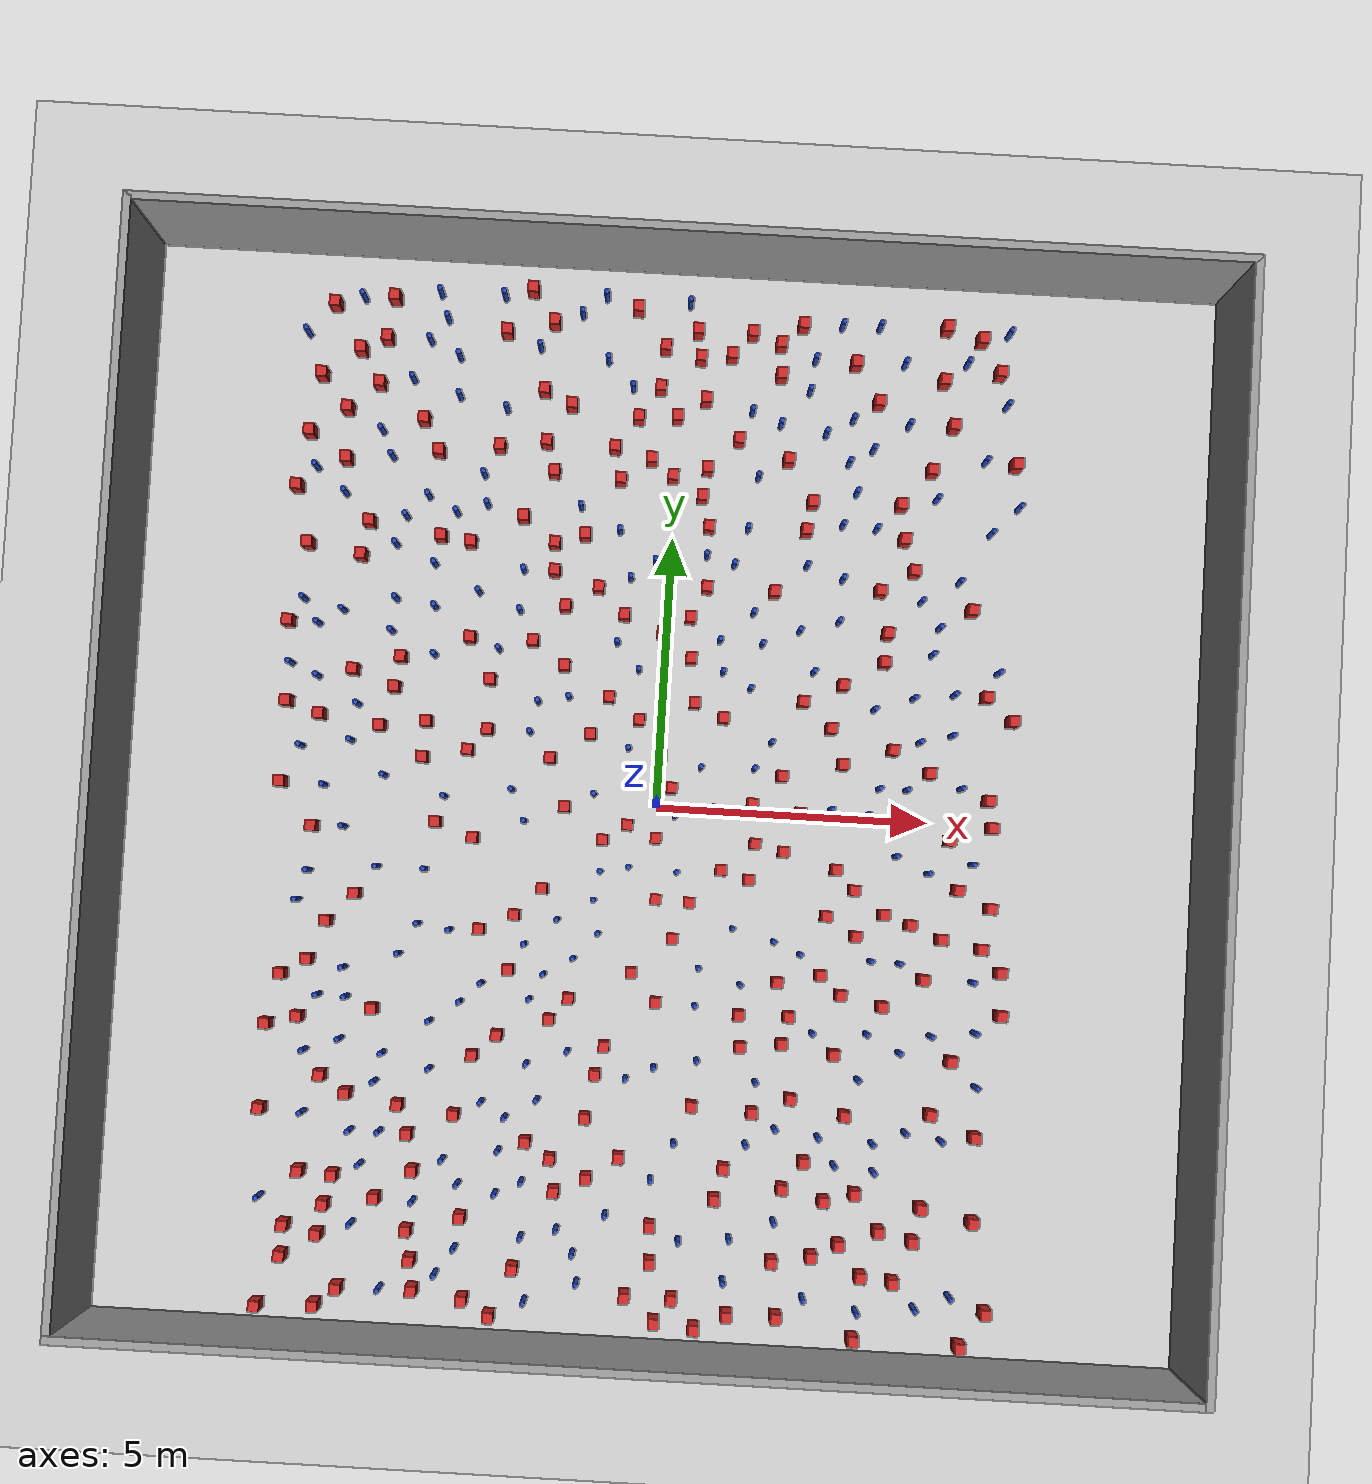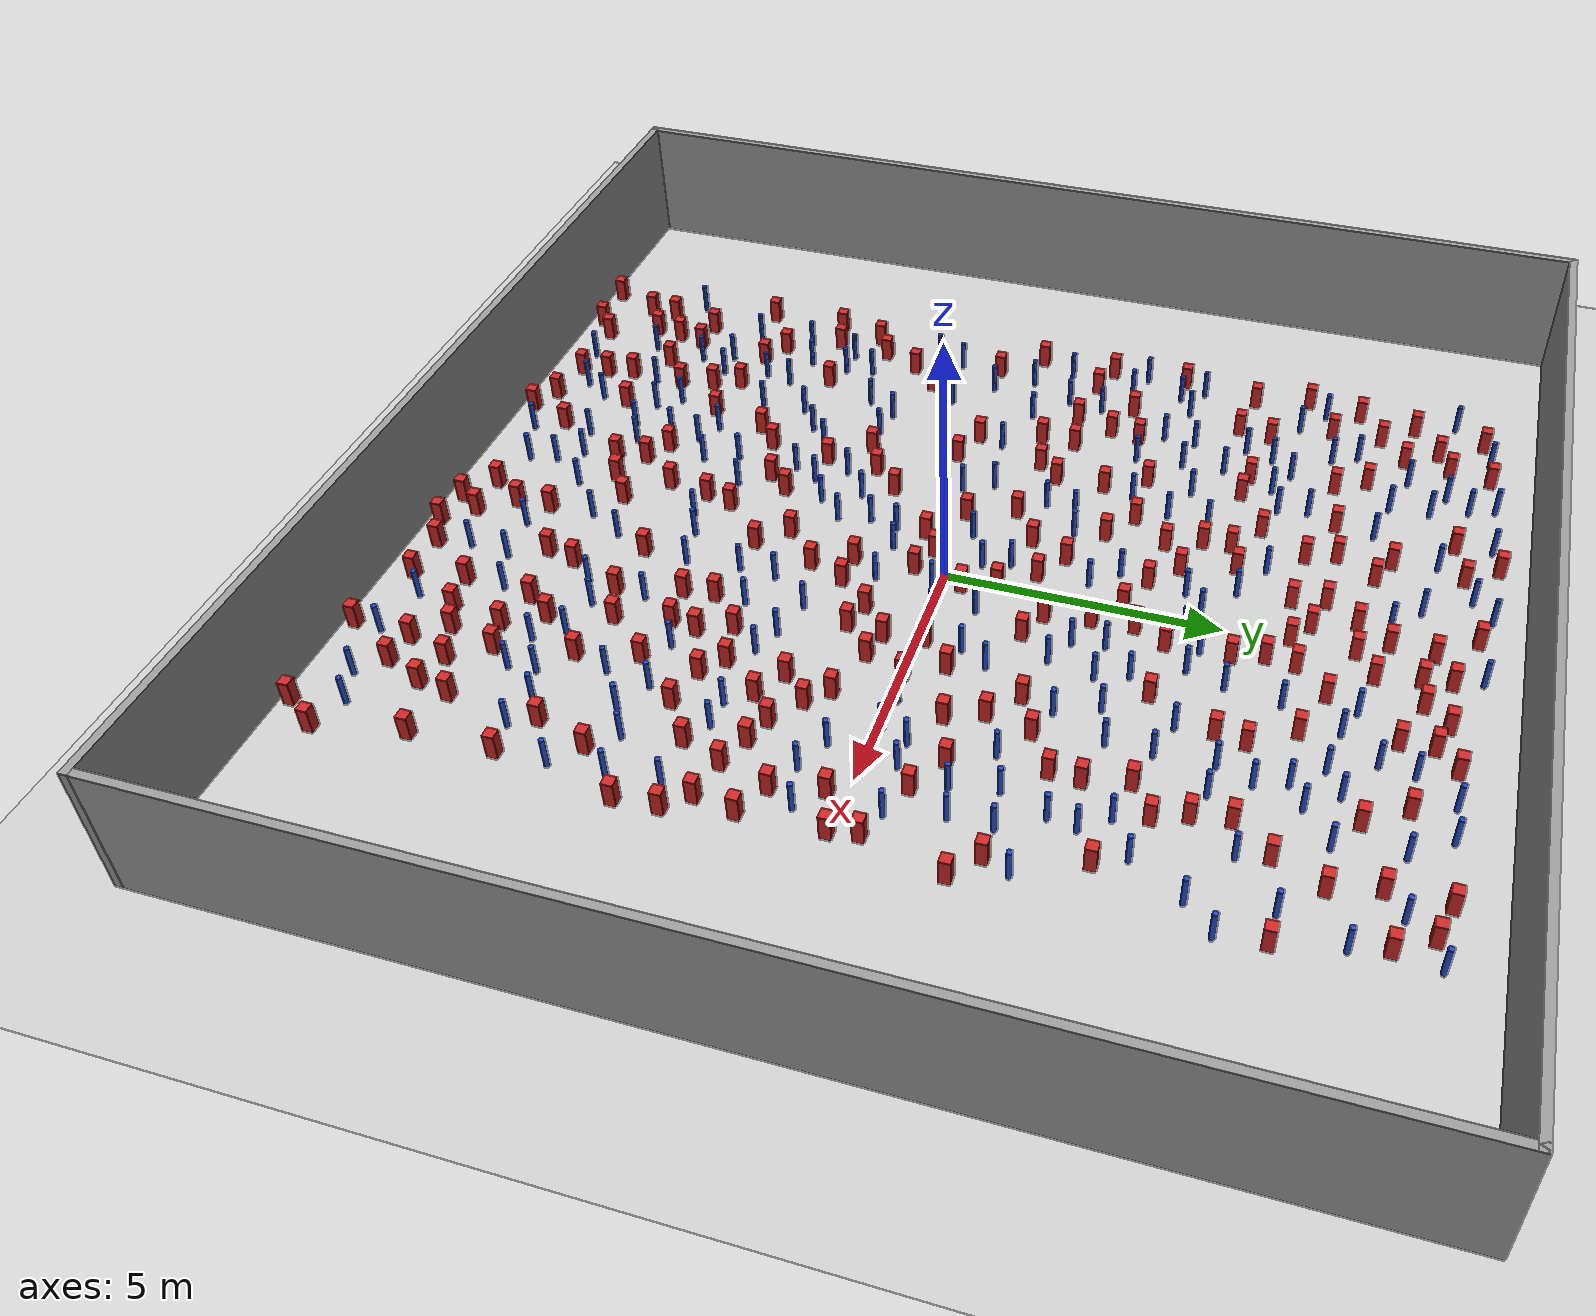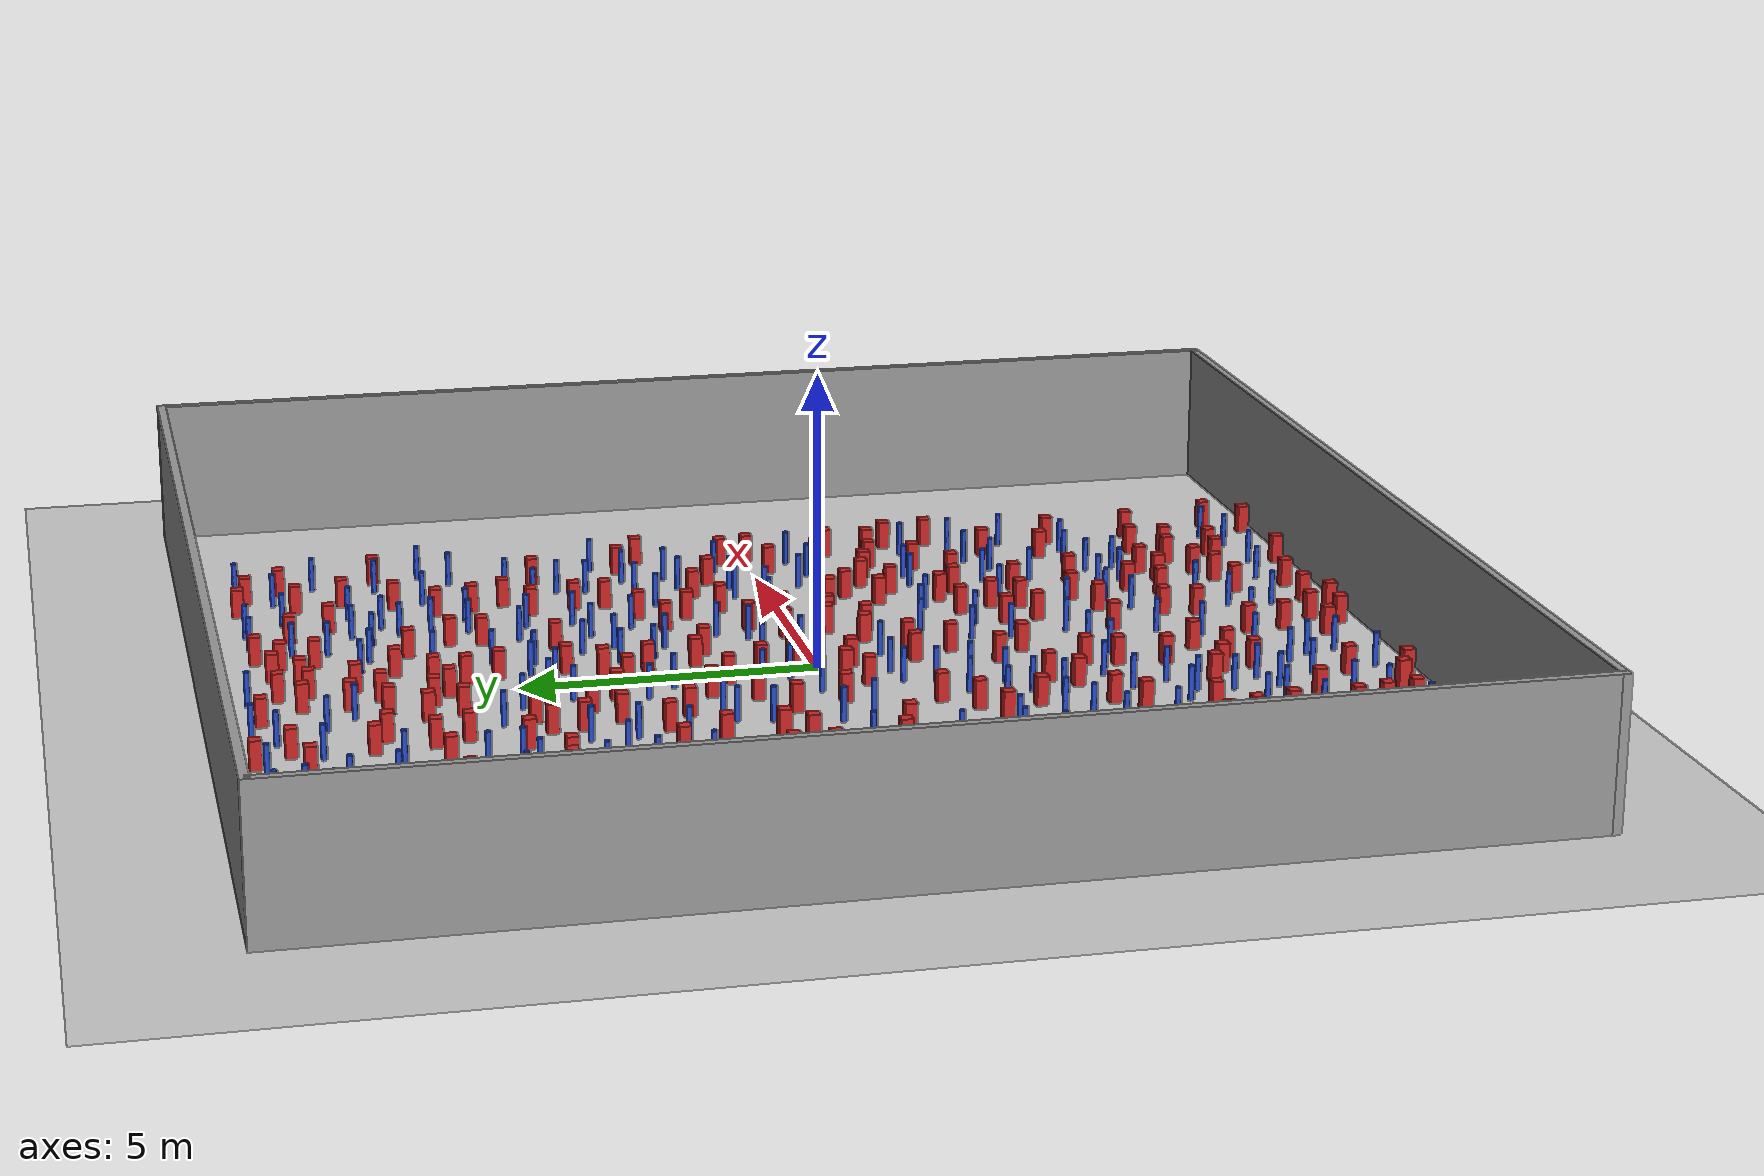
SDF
<sdf version="1.6">
 <world name="default">
  <light name="sun" type="directional">
   <pose>0 0 1000 0 -0 0</pose>
   <diffuse>0.8 0.8 0.8 1</diffuse>
   <specular>0.1 0.1 0.1 1</specular>
   <attenuation>
    <range>1000</range>
    <constant>0.9</constant>
    <linear>0.01</linear>
    <quadratic>0.001</quadratic>
   </attenuation>
   <direction>-0.5 0.5 -1</direction>
  </light>
  <model name="ground_plane">
   <static>1</static>
   <link name="link">
    <collision name="collision">
     <geometry><plane><normal>0 0 1</normal><size>100 100</size></plane></geometry>
     <surface><friction><ode><mu>100</mu><mu2>50</mu2></ode></friction></surface>
    </collision>
    <visual name="visual">
     <cast_shadows>0</cast_shadows>
     <geometry><plane><normal>0 0 1</normal><size>100 100</size></plane></geometry>
     <material>
      <ambient>1.0 1.0 1.0 1.0</ambient>
      <diffuse>0.8 0.8 0.8 1.0</diffuse>
      <specular>0.01 0.01 0.01 1.000000</specular>
     </material>
    </visual>
   </link>
  </model>
  <gravity>0 0 -9.8</gravity>
  <magnetic_field>6e-06 2.3e-05 -4.2e-05</magnetic_field>
  <atmosphere type="adiabatic"/>
  <physics name="default_physics" default="0" type="ode">
   <max_step_size>0.001</max_step_size>
   <real_time_factor>1</real_time_factor>
   <real_time_update_rate>1000</real_time_update_rate>
  </physics>
  <scene><ambient>0.4 0.4 0.4 1</ambient><background>0.7 0.7 0.7 1</background><shadows>1</shadows></scene>
  <spherical_coordinates>
   <surface_model>EARTH_WGS84</surface_model>
   <latitude_deg>0</latitude_deg>
   <longitude_deg>0</longitude_deg>
   <elevation>0</elevation>
   <heading_deg>0</heading_deg>
  </spherical_coordinates>
  <plugin name="gazebo_occupancy_map" filename="libgazebo_2Dmap_plugin.so">
   <map_resolution>0.05</map_resolution>
   <map_topic>generated_map</map_topic>
   <map_height>0.01</map_height>
   <map_size_x>50</map_size_x>
   <map_size_y>50</map_size_y>
  </plugin>
  <model name="NamedLocations">
   <static>true</static>
   <link name="DefaultStart"><pose>8.5 0 0 0 0 3.14</pose></link>
  </model>
  <model name="20x20_walls">
   <pose>0.044518 0.176112 0 0 -0 0</pose>
   <link name="Wall_1">
    <collision name="Wall_1_Collision">
     <geometry><box><size>20 0.15 2.5</size></box></geometry>
     <pose>0 0 1.25 0 -0 0</pose>
    </collision>
    <visual name="Wall_1_Visual">
     <pose>0 0 1.25 0 -0 0</pose>
     <geometry><box><size>20 0.15 2.5</size></box></geometry>
     <material>
      <script><uri>file://media/materials/scripts/gazebo.material</uri><name>Gazebo/Grey</name></script>
      <ambient>0.976471 0.992157 1 1</ambient>
     </material>
     <meta><layer>0</layer></meta>
    </visual>
    <pose>0 9.925 0 0 -0 0</pose>
   </link>
   <link name="Wall_3">
    <collision name="Wall_3_Collision">
     <geometry><box><size>20 0.15 2.5</size></box></geometry>
     <pose>0 0 1.25 0 -0 0</pose>
    </collision>
    <visual name="Wall_3_Visual">
     <pose>0 0 1.25 0 -0 0</pose>
     <geometry><box><size>20 0.15 2.5</size></box></geometry>
     <material>
      <script><uri>file://media/materials/scripts/gazebo.material</uri><name>Gazebo/Grey</name></script>
      <ambient>0.976471 0.992157 1 1</ambient>
     </material>
     <meta><layer>0</layer></meta>
    </visual>
    <pose>9.925 0 0 0 0 -1.5708</pose>
   </link>
   <link name="Wall_4">
    <collision name="Wall_4_Collision">
     <geometry><box><size>20 0.15 2.5</size></box></geometry>
     <pose>0 0 1.25 0 -0 0</pose>
    </collision>
    <visual name="Wall_4_Visual">
     <pose>0 0 1.25 0 -0 0</pose>
     <geometry><box><size>20 0.15 2.5</size></box></geometry>
     <material>
      <script><uri>file://media/materials/scripts/gazebo.material</uri><name>Gazebo/Grey</name></script>
      <ambient>0.976471 0.992157 1 1</ambient>
     </material>
     <meta><layer>0</layer></meta>
    </visual>
    <pose>0 -9.925 0 0 -0 3.14159</pose>
   </link>
   <link name="Wall_5">
    <collision name="Wall_5_Collision">
     <geometry><box><size>20 0.15 2.5</size></box></geometry>
     <pose>0 0 1.25 0 -0 0</pose>
    </collision>
    <visual name="Wall_5_Visual">
     <pose>0 0 1.25 0 -0 0</pose>
     <geometry><box><size>20 0.15 2.5</size></box></geometry>
     <material>
      <script><uri>file://media/materials/scripts/gazebo.material</uri><name>Gazebo/Grey</name></script>
      <ambient>0.976471 0.992157 1 1</ambient>
     </material>
     <meta><layer>0</layer></meta>
    </visual>
    <pose>-9.925 0 0 0 -0 1.5708</pose>
   </link>
   <static>1</static>
  </model>
  <model name="pole_obstacle0">
   <static>true</static>
   <pose>-4.96490383653 7.69837994654 2.88873142074e-08 -9.90536690842e-09 4.60219948965e-07 -1.20965994976e-07</pose>
   <link name="link">
    <pose>0 0 0.3 0 -0 0</pose>
    <inertial>
     <mass>1</mass>
     <inertia><ixx>0.145833</ixx><ixy>0</ixy><ixz>0</ixz><iyy>0.145833</iyy><iyz>0</iyz><izz>0.125</izz></inertia>
    </inertial>
    <collision name="collision">
     <geometry><cylinder><radius>0.05</radius><length>.6</length></cylinder></geometry>
    </collision>
    <visual name="visual">
     <geometry><cylinder><radius>0.05</radius><length>.6</length></cylinder></geometry>
     <material>
      <script><name>Gazebo/Blue</name><uri>file://media/materials/scripts/gazebo.material</uri></script>
     </material>
    </visual>
   </link>
  </model>
  <model name="pole_obstacle1">
   <static>true</static>
   <pose>3.19123953107 6.57956289459 2.88873142074e-08 -9.90536689859e-09 4.60219948989e-07 -1.20965994961e-07</pose>
   <link name="link">
    <pose>0 0 0.3 0 -0 0</pose>
    <inertial>
     <mass>1</mass>
     <inertia><ixx>0.145833</ixx><ixy>0</ixy><ixz>0</ixz><iyy>0.145833</iyy><iyz>0</iyz><izz>0.125</izz></inertia>
    </inertial>
    <collision name="collision">
     <geometry><cylinder><radius>0.05</radius><length>.6</length></cylinder></geometry>
    </collision>
    <visual name="visual">
     <geometry><cylinder><radius>0.05</radius><length>.6</length></cylinder></geometry>
     <material>
      <script><name>Gazebo/Blue</name><uri>file://media/materials/scripts/gazebo.material</uri></script>
     </material>
    </visual>
   </link>
  </model>
  <model name="square_post_obstacle0">
   <static>true</static>
   <pose>-3.20781454665 2.18599939971 8.22691968438e-08 7.2212513382e-06 -7.54495500217e-07 2.29674213826e-05</pose>
   <link name="link">
    <pose>0 0 0.25 0 -0 0</pose>
    <inertial>
     <mass>100</mass>
     <inertia>
      <ixx>0.166667</ixx>
      <ixy>0</ixy>
      <ixz>0</ixz>
      <iyy>0.166667</iyy>
      <iyz>0</iyz>
      <izz>0.166667</izz>
     </inertia>
    </inertial>
    <collision name="collision"><geometry><box><size>.2 .2 .5</size></box></geometry></collision>
    <visual name="visual">
     <geometry><box><size>.2 .2 .5</size></box></geometry>
     <material>
      <script><name>Gazebo/Red</name><uri>file://media/materials/scripts/gazebo.material</uri></script>
     </material>
    </visual>
   </link>
  </model>
  <model name="square_post_obstacle1">
   <static>true</static>
   <pose>-3.35054210867 -0.736798338395 8.22691968438e-08 7.2212513382e-06 -7.54495500217e-07 2.29674213826e-05</pose>
   <link name="link">
    <pose>0 0 0.25 0 -0 0</pose>
    <inertial>
     <mass>100</mass>
     <inertia>
      <ixx>0.166667</ixx>
      <ixy>0</ixy>
      <ixz>0</ixz>
      <iyy>0.166667</iyy>
      <iyz>0</iyz>
      <izz>0.166667</izz>
     </inertia>
    </inertial>
    <collision name="collision"><geometry><box><size>.2 .2 .5</size></box></geometry></collision>
    <visual name="visual">
     <geometry><box><size>.2 .2 .5</size></box></geometry>
     <material>
      <script><name>Gazebo/Red</name><uri>file://media/materials/scripts/gazebo.material</uri></script>
     </material>
    </visual>
   </link>
  </model>
  <model name="pole_obstacle2">
   <static>true</static>
   <pose>-2.73292203256 3.49728590901 2.88873142074e-08 -9.90536690232e-09 4.6021994898e-07 -1.20965994968e-07</pose>
   <link name="link">
    <pose>0 0 0.3 0 -0 0</pose>
    <inertial>
     <mass>1</mass>
     <inertia><ixx>0.145833</ixx><ixy>0</ixy><ixz>0</ixz><iyy>0.145833</iyy><iyz>0</iyz><izz>0.125</izz></inertia>
    </inertial>
    <collision name="collision">
     <geometry><cylinder><radius>0.05</radius><length>.6</length></cylinder></geometry>
    </collision>
    <visual name="visual">
     <geometry><cylinder><radius>0.05</radius><length>.6</length></cylinder></geometry>
     <material>
      <script><name>Gazebo/Blue</name><uri>file://media/materials/scripts/gazebo.material</uri></script>
     </material>
    </visual>
   </link>
  </model>
  <model name="pole_obstacle3">
   <static>true</static>
   <pose>4.42461220235 -0.647186068513 2.88873142074e-08 -9.90536689837e-09 4.60219948989e-07 -1.2096599496e-07</pose>
   <link name="link">
    <pose>0 0 0.3 0 -0 0</pose>
    <inertial>
     <mass>1</mass>
     <inertia><ixx>0.145833</ixx><ixy>0</ixy><ixz>0</ixz><iyy>0.145833</iyy><iyz>0</iyz><izz>0.125</izz></inertia>
    </inertial>
    <collision name="collision">
     <geometry><cylinder><radius>0.05</radius><length>.6</length></cylinder></geometry>
    </collision>
    <visual name="visual">
     <geometry><cylinder><radius>0.05</radius><length>.6</length></cylinder></geometry>
     <material>
      <script><name>Gazebo/Blue</name><uri>file://media/materials/scripts/gazebo.material</uri></script>
     </material>
    </visual>
   </link>
  </model>
  <model name="pole_obstacle4">
   <static>true</static>
   <pose>0.258165843569 -6.76578638505 2.88873142074e-08 -9.90536689592e-09 4.60219948995e-07 -1.20965994956e-07</pose>
   <link name="link">
    <pose>0 0 0.3 0 -0 0</pose>
    <inertial>
     <mass>1</mass>
     <inertia><ixx>0.145833</ixx><ixy>0</ixy><ixz>0</ixz><iyy>0.145833</iyy><iyz>0</iyz><izz>0.125</izz></inertia>
    </inertial>
    <collision name="collision">
     <geometry><cylinder><radius>0.05</radius><length>.6</length></cylinder></geometry>
    </collision>
    <visual name="visual">
     <geometry><cylinder><radius>0.05</radius><length>.6</length></cylinder></geometry>
     <material>
      <script><name>Gazebo/Blue</name><uri>file://media/materials/scripts/gazebo.material</uri></script>
     </material>
    </visual>
   </link>
  </model>
  <model name="pole_obstacle5">
   <static>true</static>
   <pose>-2.64452095328 8.42757156538 2.88873142074e-08 -9.90536692318e-09 4.6021994893e-07 -1.20965994988e-07</pose>
   <link name="link">
    <pose>0 0 0.3 0 -0 0</pose>
    <inertial>
     <mass>1</mass>
     <inertia><ixx>0.145833</ixx><ixy>0</ixy><ixz>0</ixz><iyy>0.145833</iyy><iyz>0</iyz><izz>0.125</izz></inertia>
    </inertial>
    <collision name="collision">
     <geometry><cylinder><radius>0.05</radius><length>.6</length></cylinder></geometry>
    </collision>
    <visual name="visual">
     <geometry><cylinder><radius>0.05</radius><length>.6</length></cylinder></geometry>
     <material>
      <script><name>Gazebo/Blue</name><uri>file://media/materials/scripts/gazebo.material</uri></script>
     </material>
    </visual>
   </link>
  </model>
  <model name="pole_obstacle6">
   <static>true</static>
   <pose>1.6934576912 -3.15217316239 2.88873142074e-08 -9.90536689791e-09 4.6021994899e-07 -1.20965994959e-07</pose>
   <link name="link">
    <pose>0 0 0.3 0 -0 0</pose>
    <inertial>
     <mass>1</mass>
     <inertia><ixx>0.145833</ixx><ixy>0</ixy><ixz>0</ixz><iyy>0.145833</iyy><iyz>0</iyz><izz>0.125</izz></inertia>
    </inertial>
    <collision name="collision">
     <geometry><cylinder><radius>0.05</radius><length>.6</length></cylinder></geometry>
    </collision>
    <visual name="visual">
     <geometry><cylinder><radius>0.05</radius><length>.6</length></cylinder></geometry>
     <material>
      <script><name>Gazebo/Blue</name><uri>file://media/materials/scripts/gazebo.material</uri></script>
     </material>
    </visual>
   </link>
  </model>
  <model name="square_post_obstacle2">
   <static>true</static>
   <pose>4.062146996 3.44321941891 8.22691968438e-08 7.2212513382e-06 -7.54495500217e-07 2.29674213826e-05</pose>
   <link name="link">
    <pose>0 0 0.25 0 -0 0</pose>
    <inertial>
     <mass>100</mass>
     <inertia>
      <ixx>0.166667</ixx>
      <ixy>0</ixy>
      <ixz>0</ixz>
      <iyy>0.166667</iyy>
      <iyz>0</iyz>
      <izz>0.166667</izz>
     </inertia>
    </inertial>
    <collision name="collision"><geometry><box><size>.2 .2 .5</size></box></geometry></collision>
    <visual name="visual">
     <geometry><box><size>.2 .2 .5</size></box></geometry>
     <material>
      <script><name>Gazebo/Red</name><uri>file://media/materials/scripts/gazebo.material</uri></script>
     </material>
    </visual>
   </link>
  </model>
  <model name="square_post_obstacle3">
   <static>true</static>
   <pose>1.18323897314 -9.39760417314 8.22691968438e-08 7.2212513382e-06 -7.54495500217e-07 2.29674213826e-05</pose>
   <link name="link">
    <pose>0 0 0.25 0 -0 0</pose>
    <inertial>
     <mass>100</mass>
     <inertia>
      <ixx>0.166667</ixx>
      <ixy>0</ixy>
      <ixz>0</ixz>
      <iyy>0.166667</iyy>
      <iyz>0</iyz>
      <izz>0.166667</izz>
     </inertia>
    </inertial>
    <collision name="collision"><geometry><box><size>.2 .2 .5</size></box></geometry></collision>
    <visual name="visual">
     <geometry><box><size>.2 .2 .5</size></box></geometry>
     <material>
      <script><name>Gazebo/Red</name><uri>file://media/materials/scripts/gazebo.material</uri></script>
     </material>
    </visual>
   </link>
  </model>
  <model name="square_post_obstacle4">
   <static>true</static>
   <pose>3.68562988007 -1.31350500014 8.22691968438e-08 7.2212513382e-06 -7.54495500217e-07 2.29674213826e-05</pose>
   <link name="link">
    <pose>0 0 0.25 0 -0 0</pose>
    <inertial>
     <mass>100</mass>
     <inertia>
      <ixx>0.166667</ixx>
      <ixy>0</ixy>
      <ixz>0</ixz>
      <iyy>0.166667</iyy>
      <iyz>0</iyz>
      <izz>0.166667</izz>
     </inertia>
    </inertial>
    <collision name="collision"><geometry><box><size>.2 .2 .5</size></box></geometry></collision>
    <visual name="visual">
     <geometry><box><size>.2 .2 .5</size></box></geometry>
     <material>
      <script><name>Gazebo/Red</name><uri>file://media/materials/scripts/gazebo.material</uri></script>
     </material>
    </visual>
   </link>
  </model>
  <model name="pole_obstacle7">
   <static>true</static>
   <pose>3.56966485649 -6.32187654859 2.88873142074e-08 -9.90536689859e-09 4.60219948989e-07 -1.20965994961e-07</pose>
   <link name="link">
    <pose>0 0 0.3 0 -0 0</pose>
    <inertial>
     <mass>1</mass>
     <inertia><ixx>0.145833</ixx><ixy>0</ixy><ixz>0</ixz><iyy>0.145833</iyy><iyz>0</iyz><izz>0.125</izz></inertia>
    </inertial>
    <collision name="collision">
     <geometry><cylinder><radius>0.05</radius><length>.6</length></cylinder></geometry>
    </collision>
    <visual name="visual">
     <geometry><cylinder><radius>0.05</radius><length>.6</length></cylinder></geometry>
     <material>
      <script><name>Gazebo/Blue</name><uri>file://media/materials/scripts/gazebo.material</uri></script>
     </material>
    </visual>
   </link>
  </model>
  <model name="pole_obstacle8">
   <static>true</static>
   <pose>-2.28974647122 -2.63171756062 2.88873142074e-08 -9.90536690232e-09 4.6021994898e-07 -1.20965994968e-07</pose>
   <link name="link">
    <pose>0 0 0.3 0 -0 0</pose>
    <inertial>
     <mass>1</mass>
     <inertia><ixx>0.145833</ixx><ixy>0</ixy><ixz>0</ixz><iyy>0.145833</iyy><iyz>0</iyz><izz>0.125</izz></inertia>
    </inertial>
    <collision name="collision">
     <geometry><cylinder><radius>0.05</radius><length>.6</length></cylinder></geometry>
    </collision>
    <visual name="visual">
     <geometry><cylinder><radius>0.05</radius><length>.6</length></cylinder></geometry>
     <material>
      <script><name>Gazebo/Blue</name><uri>file://media/materials/scripts/gazebo.material</uri></script>
     </material>
    </visual>
   </link>
  </model>
  <model name="square_post_obstacle5">
   <static>true</static>
   <pose>5.27767574691 -5.31168446191 8.22691968438e-08 7.2212513382e-06 -7.54495500217e-07 2.29674213826e-05</pose>
   <link name="link">
    <pose>0 0 0.25 0 -0 0</pose>
    <inertial>
     <mass>100</mass>
     <inertia>
      <ixx>0.166667</ixx>
      <ixy>0</ixy>
      <ixz>0</ixz>
      <iyy>0.166667</iyy>
      <iyz>0</iyz>
      <izz>0.166667</izz>
     </inertia>
    </inertial>
    <collision name="collision"><geometry><box><size>.2 .2 .5</size></box></geometry></collision>
    <visual name="visual">
     <geometry><box><size>.2 .2 .5</size></box></geometry>
     <material>
      <script><name>Gazebo/Red</name><uri>file://media/materials/scripts/gazebo.material</uri></script>
     </material>
    </visual>
   </link>
  </model>
  <model name="square_post_obstacle6">
   <static>true</static>
   <pose>0.913329731252 8.47104677812 8.22691968438e-08 7.22125133819e-06 -7.54495500217e-07 2.29674213826e-05</pose>
   <link name="link">
    <pose>0 0 0.25 0 -0 0</pose>
    <inertial>
     <mass>100</mass>
     <inertia>
      <ixx>0.166667</ixx>
      <ixy>0</ixy>
      <ixz>0</ixz>
      <iyy>0.166667</iyy>
      <iyz>0</iyz>
      <izz>0.166667</izz>
     </inertia>
    </inertial>
    <collision name="collision"><geometry><box><size>.2 .2 .5</size></box></geometry></collision>
    <visual name="visual">
     <geometry><box><size>.2 .2 .5</size></box></geometry>
     <material>
      <script><name>Gazebo/Red</name><uri>file://media/materials/scripts/gazebo.material</uri></script>
     </material>
    </visual>
   </link>
  </model>
  <model name="square_post_obstacle7">
   <static>true</static>
   <pose>-0.348357838696 -6.40661446399 8.22691968438e-08 7.2212513382e-06 -7.54495500217e-07 2.29674213826e-05</pose>
   <link name="link">
    <pose>0 0 0.25 0 -0 0</pose>
    <inertial>
     <mass>100</mass>
     <inertia>
      <ixx>0.166667</ixx>
      <ixy>0</ixy>
      <ixz>0</ixz>
      <iyy>0.166667</iyy>
      <iyz>0</iyz>
      <izz>0.166667</izz>
     </inertia>
    </inertial>
    <collision name="collision"><geometry><box><size>.2 .2 .5</size></box></geometry></collision>
    <visual name="visual">
     <geometry><box><size>.2 .2 .5</size></box></geometry>
     <material>
      <script><name>Gazebo/Red</name><uri>file://media/materials/scripts/gazebo.material</uri></script>
     </material>
    </visual>
   </link>
  </model>
  <model name="pole_obstacle9">
   <static>true</static>
   <pose>-4.39131936763 8.86157578346 2.88873142074e-08 -9.9053668967e-09 4.60219948993e-07 -1.20965994957e-07</pose>
   <link name="link">
    <pose>0 0 0.3 0 -0 0</pose>
    <inertial>
     <mass>1</mass>
     <inertia><ixx>0.145833</ixx><ixy>0</ixy><ixz>0</ixz><iyy>0.145833</iyy><iyz>0</iyz><izz>0.125</izz></inertia>
    </inertial>
    <collision name="collision">
     <geometry><cylinder><radius>0.05</radius><length>.6</length></cylinder></geometry>
    </collision>
    <visual name="visual">
     <geometry><cylinder><radius>0.05</radius><length>.6</length></cylinder></geometry>
     <material>
      <script><name>Gazebo/Blue</name><uri>file://media/materials/scripts/gazebo.material</uri></script>
     </material>
    </visual>
   </link>
  </model>
  <model name="pole_obstacle10">
   <static>true</static>
   <pose>-4.55130574229 9.33956360959 2.88873142074e-08 -9.9053668967e-09 4.60219948993e-07 -1.20965994957e-07</pose>
   <link name="link">
    <pose>0 0 0.3 0 -0 0</pose>
    <inertial>
     <mass>1</mass>
     <inertia><ixx>0.145833</ixx><ixy>0</ixy><ixz>0</ixz><iyy>0.145833</iyy><iyz>0</iyz><izz>0.125</izz></inertia>
    </inertial>
    <collision name="collision">
     <geometry><cylinder><radius>0.05</radius><length>.6</length></cylinder></geometry>
    </collision>
    <visual name="visual">
     <geometry><cylinder><radius>0.05</radius><length>.6</length></cylinder></geometry>
     <material>
      <script><name>Gazebo/Blue</name><uri>file://media/materials/scripts/gazebo.material</uri></script>
     </material>
    </visual>
   </link>
  </model>
  <model name="pole_obstacle11">
   <static>true</static>
   <pose>-1.38419072896 -4.5300421405 2.88873142074e-08 -9.90536689852e-09 4.60219948989e-07 -1.2096599496e-07</pose>
   <link name="link">
    <pose>0 0 0.3 0 -0 0</pose>
    <inertial>
     <mass>1</mass>
     <inertia><ixx>0.145833</ixx><ixy>0</ixy><ixz>0</ixz><iyy>0.145833</iyy><iyz>0</iyz><izz>0.125</izz></inertia>
    </inertial>
    <collision name="collision">
     <geometry><cylinder><radius>0.05</radius><length>.6</length></cylinder></geometry>
    </collision>
    <visual name="visual">
     <geometry><cylinder><radius>0.05</radius><length>.6</length></cylinder></geometry>
     <material>
      <script><name>Gazebo/Blue</name><uri>file://media/materials/scripts/gazebo.material</uri></script>
     </material>
    </visual>
   </link>
  </model>
  <model name="pole_obstacle12">
   <static>true</static>
   <pose>3.12738423916 -8.74129097688 2.88873142074e-08 -9.90536692318e-09 4.6021994893e-07 -1.20965994988e-07</pose>
   <link name="link">
    <pose>0 0 0.3 0 -0 0</pose>
    <inertial>
     <mass>1</mass>
     <inertia><ixx>0.145833</ixx><ixy>0</ixy><ixz>0</ixz><iyy>0.145833</iyy><iyz>0</iyz><izz>0.125</izz></inertia>
    </inertial>
    <collision name="collision">
     <geometry><cylinder><radius>0.05</radius><length>.6</length></cylinder></geometry>
    </collision>
    <visual name="visual">
     <geometry><cylinder><radius>0.05</radius><length>.6</length></cylinder></geometry>
     <material>
      <script><name>Gazebo/Blue</name><uri>file://media/materials/scripts/gazebo.material</uri></script>
     </material>
    </visual>
   </link>
  </model>
  <model name="square_post_obstacle8">
   <static>true</static>
   <pose>-2.02314259595 -1.59735954357 8.22691968438e-08 7.2212513382e-06 -7.54495500217e-07 2.29674213826e-05</pose>
   <link name="link">
    <pose>0 0 0.25 0 -0 0</pose>
    <inertial>
     <mass>100</mass>
     <inertia>
      <ixx>0.166667</ixx>
      <ixy>0</ixy>
      <ixz>0</ixz>
      <iyy>0.166667</iyy>
      <iyz>0</iyz>
      <izz>0.166667</izz>
     </inertia>
    </inertial>
    <collision name="collision"><geometry><box><size>.2 .2 .5</size></box></geometry></collision>
    <visual name="visual">
     <geometry><box><size>.2 .2 .5</size></box></geometry>
     <material>
      <script><name>Gazebo/Red</name><uri>file://media/materials/scripts/gazebo.material</uri></script>
     </material>
    </visual>
   </link>
  </model>
  <model name="square_post_obstacle9">
   <static>true</static>
   <pose>1.56774831799 -6.49441075072 8.22691968438e-08 7.2212513382e-06 -7.54495500217e-07 2.29674213826e-05</pose>
   <link name="link">
    <pose>0 0 0.25 0 -0 0</pose>
    <inertial>
     <mass>100</mass>
     <inertia>
      <ixx>0.166667</ixx>
      <ixy>0</ixy>
      <ixz>0</ixz>
      <iyy>0.166667</iyy>
      <iyz>0</iyz>
      <izz>0.166667</izz>
     </inertia>
    </inertial>
    <collision name="collision"><geometry><box><size>.2 .2 .5</size></box></geometry></collision>
    <visual name="visual">
     <geometry><box><size>.2 .2 .5</size></box></geometry>
     <material>
      <script><name>Gazebo/Red</name><uri>file://media/materials/scripts/gazebo.material</uri></script>
     </material>
    </visual>
   </link>
  </model>
  <model name="pole_obstacle13">
   <static>true</static>
   <pose>3.18473489793 4.40820543616 2.88873142074e-08 -9.90536689859e-09 4.60219948989e-07 -1.20965994961e-07</pose>
   <link name="link">
    <pose>0 0 0.3 0 -0 0</pose>
    <inertial>
     <mass>1</mass>
     <inertia><ixx>0.145833</ixx><ixy>0</ixy><ixz>0</ixz><iyy>0.145833</iyy><iyz>0</iyz><izz>0.125</izz></inertia>
    </inertial>
    <collision name="collision">
     <geometry><cylinder><radius>0.05</radius><length>.6</length></cylinder></geometry>
    </collision>
    <visual name="visual">
     <geometry><cylinder><radius>0.05</radius><length>.6</length></cylinder></geometry>
     <material>
      <script><name>Gazebo/Blue</name><uri>file://media/materials/scripts/gazebo.material</uri></script>
     </material>
    </visual>
   </link>
  </model>
  <model name="square_post_obstacle10">
   <static>true</static>
   <pose>-5.60839444574 4.99346010621 8.22691968438e-08 7.22125133819e-06 -7.54495500217e-07 2.29674213826e-05</pose>
   <link name="link">
    <pose>0 0 0.25 0 -0 0</pose>
    <inertial>
     <mass>100</mass>
     <inertia>
      <ixx>0.166667</ixx>
      <ixy>0</ixy>
      <ixz>0</ixz>
      <iyy>0.166667</iyy>
      <iyz>0</iyz>
      <izz>0.166667</izz>
     </inertia>
    </inertial>
    <collision name="collision"><geometry><box><size>.2 .2 .5</size></box></geometry></collision>
    <visual name="visual">
     <geometry><box><size>.2 .2 .5</size></box></geometry>
     <material>
      <script><name>Gazebo/Red</name><uri>file://media/materials/scripts/gazebo.material</uri></script>
     </material>
    </visual>
   </link>
  </model>
  <model name="square_post_obstacle11">
   <static>true</static>
   <pose>2.62650904284 0.0469307750388 8.22691968438e-08 7.2212513382e-06 -7.54495500217e-07 2.29674213826e-05</pose>
   <link name="link">
    <pose>0 0 0.25 0 -0 0</pose>
    <inertial>
     <mass>100</mass>
     <inertia>
      <ixx>0.166667</ixx>
      <ixy>0</ixy>
      <ixz>0</ixz>
      <iyy>0.166667</iyy>
      <iyz>0</iyz>
      <izz>0.166667</izz>
     </inertia>
    </inertial>
    <collision name="collision"><geometry><box><size>.2 .2 .5</size></box></geometry></collision>
    <visual name="visual">
     <geometry><box><size>.2 .2 .5</size></box></geometry>
     <material>
      <script><name>Gazebo/Red</name><uri>file://media/materials/scripts/gazebo.material</uri></script>
     </material>
    </visual>
   </link>
  </model>
  <model name="pole_obstacle14">
   <static>true</static>
   <pose>-2.70680773216 4.25169056416 2.88873142074e-08 -9.90536689859e-09 4.60219948989e-07 -1.20965994961e-07</pose>
   <link name="link">
    <pose>0 0 0.3 0 -0 0</pose>
    <inertial>
     <mass>1</mass>
     <inertia><ixx>0.145833</ixx><ixy>0</ixy><ixz>0</ixz><iyy>0.145833</iyy><iyz>0</iyz><izz>0.125</izz></inertia>
    </inertial>
    <collision name="collision">
     <geometry><cylinder><radius>0.05</radius><length>.6</length></cylinder></geometry>
    </collision>
    <visual name="visual">
     <geometry><cylinder><radius>0.05</radius><length>.6</length></cylinder></geometry>
     <material>
      <script><name>Gazebo/Blue</name><uri>file://media/materials/scripts/gazebo.material</uri></script>
     </material>
    </visual>
   </link>
  </model>
  <model name="pole_obstacle15">
   <static>true</static>
   <pose>-0.483504385526 2.51753381008 2.88873142074e-08 -9.90536689335e-09 4.60219949001e-07 -1.20965994953e-07</pose>
   <link name="link">
    <pose>0 0 0.3 0 -0 0</pose>
    <inertial>
     <mass>1</mass>
     <inertia><ixx>0.145833</ixx><ixy>0</ixy><ixz>0</ixz><iyy>0.145833</iyy><iyz>0</iyz><izz>0.125</izz></inertia>
    </inertial>
    <collision name="collision">
     <geometry><cylinder><radius>0.05</radius><length>.6</length></cylinder></geometry>
    </collision>
    <visual name="visual">
     <geometry><cylinder><radius>0.05</radius><length>.6</length></cylinder></geometry>
     <material>
      <script><name>Gazebo/Blue</name><uri>file://media/materials/scripts/gazebo.material</uri></script>
     </material>
    </visual>
   </link>
  </model>
  <model name="square_post_obstacle12">
   <static>true</static>
   <pose>1.22674798471 -1.0815062226 8.22691968438e-08 7.2212513382e-06 -7.54495500217e-07 2.29674213826e-05</pose>
   <link name="link">
    <pose>0 0 0.25 0 -0 0</pose>
    <inertial>
     <mass>100</mass>
     <inertia>
      <ixx>0.166667</ixx>
      <ixy>0</ixy>
      <ixz>0</ixz>
      <iyy>0.166667</iyy>
      <iyz>0</iyz>
      <izz>0.166667</izz>
     </inertia>
    </inertial>
    <collision name="collision"><geometry><box><size>.2 .2 .5</size></box></geometry></collision>
    <visual name="visual">
     <geometry><box><size>.2 .2 .5</size></box></geometry>
     <material>
      <script><name>Gazebo/Red</name><uri>file://media/materials/scripts/gazebo.material</uri></script>
     </material>
    </visual>
   </link>
  </model>
  <model name="pole_obstacle16">
   <static>true</static>
   <pose>0.983162321599 3.14520407418 2.88873142074e-08 -9.90536689802e-09 4.6021994899e-07 -1.2096599496e-07</pose>
   <link name="link">
    <pose>0 0 0.3 0 -0 0</pose>
    <inertial>
     <mass>1</mass>
     <inertia><ixx>0.145833</ixx><ixy>0</ixy><ixz>0</ixz><iyy>0.145833</iyy><iyz>0</iyz><izz>0.125</izz></inertia>
    </inertial>
    <collision name="collision">
     <geometry><cylinder><radius>0.05</radius><length>.6</length></cylinder></geometry>
    </collision>
    <visual name="visual">
     <geometry><cylinder><radius>0.05</radius><length>.6</length></cylinder></geometry>
     <material>
      <script><name>Gazebo/Blue</name><uri>file://media/materials/scripts/gazebo.material</uri></script>
     </material>
    </visual>
   </link>
  </model>
  <model name="pole_obstacle17">
   <static>true</static>
   <pose>5.93204498698 -2.86877223244 2.88873142074e-08 -9.90536690245e-09 4.6021994898e-07 -1.20965994966e-07</pose>
   <link name="link">
    <pose>0 0 0.3 0 -0 0</pose>
    <inertial>
     <mass>1</mass>
     <inertia><ixx>0.145833</ixx><ixy>0</ixy><ixz>0</ixz><iyy>0.145833</iyy><iyz>0</iyz><izz>0.125</izz></inertia>
    </inertial>
    <collision name="collision">
     <geometry><cylinder><radius>0.05</radius><length>.6</length></cylinder></geometry>
    </collision>
    <visual name="visual">
     <geometry><cylinder><radius>0.05</radius><length>.6</length></cylinder></geometry>
     <material>
      <script><name>Gazebo/Blue</name><uri>file://media/materials/scripts/gazebo.material</uri></script>
     </material>
    </visual>
   </link>
  </model>
  <model name="square_post_obstacle13">
   <static>true</static>
   <pose>-2.25063766883 6.10697820428 8.22691968438e-08 7.2212513382e-06 -7.54495500217e-07 2.29674213826e-05</pose>
   <link name="link">
    <pose>0 0 0.25 0 -0 0</pose>
    <inertial>
     <mass>100</mass>
     <inertia>
      <ixx>0.166667</ixx>
      <ixy>0</ixy>
      <ixz>0</ixz>
      <iyy>0.166667</iyy>
      <iyz>0</iyz>
      <izz>0.166667</izz>
     </inertia>
    </inertial>
    <collision name="collision"><geometry><box><size>.2 .2 .5</size></box></geometry></collision>
    <visual name="visual">
     <geometry><box><size>.2 .2 .5</size></box></geometry>
     <material>
      <script><name>Gazebo/Red</name><uri>file://media/materials/scripts/gazebo.material</uri></script>
     </material>
    </visual>
   </link>
  </model>
  <model name="pole_obstacle18">
   <static>true</static>
   <pose>5.82927272545 -0.721593858547 2.88873142074e-08 -9.90536689837e-09 4.60219948989e-07 -1.2096599496e-07</pose>
   <link name="link">
    <pose>0 0 0.3 0 -0 0</pose>
    <inertial>
     <mass>1</mass>
     <inertia><ixx>0.145833</ixx><ixy>0</ixy><ixz>0</ixz><iyy>0.145833</iyy><iyz>0</iyz><izz>0.125</izz></inertia>
    </inertial>
    <collision name="collision">
     <geometry><cylinder><radius>0.05</radius><length>.6</length></cylinder></geometry>
    </collision>
    <visual name="visual">
     <geometry><cylinder><radius>0.05</radius><length>.6</length></cylinder></geometry>
     <material>
      <script><name>Gazebo/Blue</name><uri>file://media/materials/scripts/gazebo.material</uri></script>
     </material>
    </visual>
   </link>
  </model>
  <model name="square_post_obstacle14">
   <static>true</static>
   <pose>-1.42556165094 -3.57427515595 8.22691968438e-08 7.2212513382e-06 -7.54495500217e-07 2.29674213826e-05</pose>
   <link name="link">
    <pose>0 0 0.25 0 -0 0</pose>
    <inertial>
     <mass>100</mass>
     <inertia>
      <ixx>0.166667</ixx>
      <ixy>0</ixy>
      <ixz>0</ixz>
      <iyy>0.166667</iyy>
      <iyz>0</iyz>
      <izz>0.166667</izz>
     </inertia>
    </inertial>
    <collision name="collision"><geometry><box><size>.2 .2 .5</size></box></geometry></collision>
    <visual name="visual">
     <geometry><box><size>.2 .2 .5</size></box></geometry>
     <material>
      <script><name>Gazebo/Red</name><uri>file://media/materials/scripts/gazebo.material</uri></script>
     </material>
    </visual>
   </link>
  </model>
  <model name="pole_obstacle19">
   <static>true</static>
   <pose>-3.91891887837 -0.00871485491137 2.88873142074e-08 -9.90536691065e-09 4.6021994896e-07 -1.20965994981e-07</pose>
   <link name="link">
    <pose>0 0 0.3 0 -0 0</pose>
    <inertial>
     <mass>1</mass>
     <inertia><ixx>0.145833</ixx><ixy>0</ixy><ixz>0</ixz><iyy>0.145833</iyy><iyz>0</iyz><izz>0.125</izz></inertia>
    </inertial>
    <collision name="collision">
     <geometry><cylinder><radius>0.05</radius><length>.6</length></cylinder></geometry>
    </collision>
    <visual name="visual">
     <geometry><cylinder><radius>0.05</radius><length>.6</length></cylinder></geometry>
     <material>
      <script><name>Gazebo/Blue</name><uri>file://media/materials/scripts/gazebo.material</uri></script>
     </material>
    </visual>
   </link>
  </model>
  <model name="square_post_obstacle15">
   <static>true</static>
   <pose>2.64967527114 -6.79463559241 8.22691968438e-08 7.2212513382e-06 -7.54495500217e-07 2.29674213826e-05</pose>
   <link name="link">
    <pose>0 0 0.25 0 -0 0</pose>
    <inertial>
     <mass>100</mass>
     <inertia>
      <ixx>0.166667</ixx>
      <ixy>0</ixy>
      <ixz>0</ixz>
      <iyy>0.166667</iyy>
      <iyz>0</iyz>
      <izz>0.166667</izz>
     </inertia>
    </inertial>
    <collision name="collision"><geometry><box><size>.2 .2 .5</size></box></geometry></collision>
    <visual name="visual">
     <geometry><box><size>.2 .2 .5</size></box></geometry>
     <material>
      <script><name>Gazebo/Red</name><uri>file://media/materials/scripts/gazebo.material</uri></script>
     </material>
    </visual>
   </link>
  </model>
  <model name="square_post_obstacle16">
   <static>true</static>
   <pose>-5.9660888704 8.1992055869 8.22691968438e-08 7.22125133819e-06 -7.54495500217e-07 2.29674213826e-05</pose>
   <link name="link">
    <pose>0 0 0.25 0 -0 0</pose>
    <inertial>
     <mass>100</mass>
     <inertia>
      <ixx>0.166667</ixx>
      <ixy>0</ixy>
      <ixz>0</ixz>
      <iyy>0.166667</iyy>
      <iyz>0</iyz>
      <izz>0.166667</izz>
     </inertia>
    </inertial>
    <collision name="collision"><geometry><box><size>.2 .2 .5</size></box></geometry></collision>
    <visual name="visual">
     <geometry><box><size>.2 .2 .5</size></box></geometry>
     <material>
      <script><name>Gazebo/Red</name><uri>file://media/materials/scripts/gazebo.material</uri></script>
     </material>
    </visual>
   </link>
  </model>
  <model name="square_post_obstacle17">
   <static>true</static>
   <pose>-0.917751412728 -6.81275528591 8.22691968438e-08 7.22125133819e-06 -7.54495500217e-07 2.29674213826e-05</pose>
   <link name="link">
    <pose>0 0 0.25 0 -0 0</pose>
    <inertial>
     <mass>100</mass>
     <inertia>
      <ixx>0.166667</ixx>
      <ixy>0</ixy>
      <ixz>0</ixz>
      <iyy>0.166667</iyy>
      <iyz>0</iyz>
      <izz>0.166667</izz>
     </inertia>
    </inertial>
    <collision name="collision"><geometry><box><size>.2 .2 .5</size></box></geometry></collision>
    <visual name="visual">
     <geometry><box><size>.2 .2 .5</size></box></geometry>
     <material>
      <script><name>Gazebo/Red</name><uri>file://media/materials/scripts/gazebo.material</uri></script>
     </material>
    </visual>
   </link>
  </model>
  <model name="pole_obstacle20">
   <static>true</static>
   <pose>-3.23051718857 -8.1966301705 2.88873142074e-08 -9.9053668994e-09 4.60219948987e-07 -1.20965994963e-07</pose>
   <link name="link">
    <pose>0 0 0.3 0 -0 0</pose>
    <inertial>
     <mass>1</mass>
     <inertia><ixx>0.145833</ixx><ixy>0</ixy><ixz>0</ixz><iyy>0.145833</iyy><iyz>0</iyz><izz>0.125</izz></inertia>
    </inertial>
    <collision name="collision">
     <geometry><cylinder><radius>0.05</radius><length>.6</length></cylinder></geometry>
    </collision>
    <visual name="visual">
     <geometry><cylinder><radius>0.05</radius><length>.6</length></cylinder></geometry>
     <material>
      <script><name>Gazebo/Blue</name><uri>file://media/materials/scripts/gazebo.material</uri></script>
     </material>
    </visual>
   </link>
  </model>
  <model name="pole_obstacle21">
   <static>true</static>
   <pose>-2.45525858788 -5.79399990301 2.88873142074e-08 -9.90536689859e-09 4.60219948989e-07 -1.20965994961e-07</pose>
   <link name="link">
    <pose>0 0 0.3 0 -0 0</pose>
    <inertial>
     <mass>1</mass>
     <inertia><ixx>0.145833</ixx><ixy>0</ixy><ixz>0</ixz><iyy>0.145833</iyy><iyz>0</iyz><izz>0.125</izz></inertia>
    </inertial>
    <collision name="collision">
     <geometry><cylinder><radius>0.05</radius><length>.6</length></cylinder></geometry>
    </collision>
    <visual name="visual">
     <geometry><cylinder><radius>0.05</radius><length>.6</length></cylinder></geometry>
     <material>
      <script><name>Gazebo/Blue</name><uri>file://media/materials/scripts/gazebo.material</uri></script>
     </material>
    </visual>
   </link>
  </model>
  <model name="pole_obstacle22">
   <static>true</static>
   <pose>-0.980689446663 -8.69325914813 2.88873142074e-08 -9.90536690773e-09 4.60219948967e-07 -1.20965994976e-07</pose>
   <link name="link">
    <pose>0 0 0.3 0 -0 0</pose>
    <inertial>
     <mass>1</mass>
     <inertia><ixx>0.145833</ixx><ixy>0</ixy><ixz>0</ixz><iyy>0.145833</iyy><iyz>0</iyz><izz>0.125</izz></inertia>
    </inertial>
    <collision name="collision">
     <geometry><cylinder><radius>0.05</radius><length>.6</length></cylinder></geometry>
    </collision>
    <visual name="visual">
     <geometry><cylinder><radius>0.05</radius><length>.6</length></cylinder></geometry>
     <material>
      <script><name>Gazebo/Blue</name><uri>file://media/materials/scripts/gazebo.material</uri></script>
     </material>
    </visual>
   </link>
  </model>
  <model name="pole_obstacle23">
   <static>true</static>
   <pose>5.88145847452 5.40329038732 2.88873142074e-08 -9.90536690842e-09 4.60219948965e-07 -1.20965994976e-07</pose>
   <link name="link">
    <pose>0 0 0.3 0 -0 0</pose>
    <inertial>
     <mass>1</mass>
     <inertia><ixx>0.145833</ixx><ixy>0</ixy><ixz>0</ixz><iyy>0.145833</iyy><iyz>0</iyz><izz>0.125</izz></inertia>
    </inertial>
    <collision name="collision">
     <geometry><cylinder><radius>0.05</radius><length>.6</length></cylinder></geometry>
    </collision>
    <visual name="visual">
     <geometry><cylinder><radius>0.05</radius><length>.6</length></cylinder></geometry>
     <material>
      <script><name>Gazebo/Blue</name><uri>file://media/materials/scripts/gazebo.material</uri></script>
     </material>
    </visual>
   </link>
  </model>
  <model name="square_post_obstacle18">
   <static>true</static>
   <pose>-2.84131001033 9.49645642191 8.22691968438e-08 7.22125133819e-06 -7.54495500217e-07 2.29674213826e-05</pose>
   <link name="link">
    <pose>0 0 0.25 0 -0 0</pose>
    <inertial>
     <mass>100</mass>
     <inertia>
      <ixx>0.166667</ixx>
      <ixy>0</ixy>
      <ixz>0</ixz>
      <iyy>0.166667</iyy>
      <iyz>0</iyz>
      <izz>0.166667</izz>
     </inertia>
    </inertial>
    <collision name="collision"><geometry><box><size>.2 .2 .5</size></box></geometry></collision>
    <visual name="visual">
     <geometry><box><size>.2 .2 .5</size></box></geometry>
     <material>
      <script><name>Gazebo/Red</name><uri>file://media/materials/scripts/gazebo.material</uri></script>
     </material>
    </visual>
   </link>
  </model>
  <model name="pole_obstacle24">
   <static>true</static>
   <pose>0.821740182528 -7.83802844646 2.88873142074e-08 -9.90536689661e-09 4.60219948993e-07 -1.20965994957e-07</pose>
   <link name="link">
    <pose>0 0 0.3 0 -0 0</pose>
    <inertial>
     <mass>1</mass>
     <inertia><ixx>0.145833</ixx><ixy>0</ixy><ixz>0</ixz><iyy>0.145833</iyy><iyz>0</iyz><izz>0.125</izz></inertia>
    </inertial>
    <collision name="collision">
     <geometry><cylinder><radius>0.05</radius><length>.6</length></cylinder></geometry>
    </collision>
    <visual name="visual">
     <geometry><cylinder><radius>0.05</radius><length>.6</length></cylinder></geometry>
     <material>
      <script><name>Gazebo/Blue</name><uri>file://media/materials/scripts/gazebo.material</uri></script>
     </material>
    </visual>
   </link>
  </model>
  <model name="pole_obstacle25">
   <static>true</static>
   <pose>-6.49594713914 -2.04775443947 2.88873142074e-08 -9.90536689749e-09 4.60219948991e-07 -1.20965994959e-07</pose>
   <link name="link">
    <pose>0 0 0.3 0 -0 0</pose>
    <inertial>
     <mass>1</mass>
     <inertia><ixx>0.145833</ixx><ixy>0</ixy><ixz>0</ixz><iyy>0.145833</iyy><iyz>0</iyz><izz>0.125</izz></inertia>
    </inertial>
    <collision name="collision">
     <geometry><cylinder><radius>0.05</radius><length>.6</length></cylinder></geometry>
    </collision>
    <visual name="visual">
     <geometry><cylinder><radius>0.05</radius><length>.6</length></cylinder></geometry>
     <material>
      <script><name>Gazebo/Blue</name><uri>file://media/materials/scripts/gazebo.material</uri></script>
     </material>
    </visual>
   </link>
  </model>
  <model name="pole_obstacle26">
   <static>true</static>
   <pose>-5.02933174492 3.59131452795 2.88873142074e-08 -9.90536690245e-09 4.6021994898e-07 -1.20965994966e-07</pose>
   <link name="link">
    <pose>0 0 0.3 0 -0 0</pose>
    <inertial>
     <mass>1</mass>
     <inertia><ixx>0.145833</ixx><ixy>0</ixy><ixz>0</ixz><iyy>0.145833</iyy><iyz>0</iyz><izz>0.125</izz></inertia>
    </inertial>
    <collision name="collision">
     <geometry><cylinder><radius>0.05</radius><length>.6</length></cylinder></geometry>
    </collision>
    <visual name="visual">
     <geometry><cylinder><radius>0.05</radius><length>.6</length></cylinder></geometry>
     <material>
      <script><name>Gazebo/Blue</name><uri>file://media/materials/scripts/gazebo.material</uri></script>
     </material>
    </visual>
   </link>
  </model>
  <model name="pole_obstacle27">
   <static>true</static>
   <pose>-4.93310449654 5.12727231095 2.88873142074e-08 -9.90536690842e-09 4.60219948965e-07 -1.20965994976e-07</pose>
   <link name="link">
    <pose>0 0 0.3 0 -0 0</pose>
    <inertial>
     <mass>1</mass>
     <inertia><ixx>0.145833</ixx><ixy>0</ixy><ixz>0</ixz><iyy>0.145833</iyy><iyz>0</iyz><izz>0.125</izz></inertia>
    </inertial>
    <collision name="collision">
     <geometry><cylinder><radius>0.05</radius><length>.6</length></cylinder></geometry>
    </collision>
    <visual name="visual">
     <geometry><cylinder><radius>0.05</radius><length>.6</length></cylinder></geometry>
     <material>
      <script><name>Gazebo/Blue</name><uri>file://media/materials/scripts/gazebo.material</uri></script>
     </material>
    </visual>
   </link>
  </model>
  <model name="pole_obstacle28">
   <static>true</static>
   <pose>-5.73384834355 -0.667830797117 2.88873142074e-08 -9.90536689837e-09 4.60219948989e-07 -1.2096599496e-07</pose>
   <link name="link">
    <pose>0 0 0.3 0 -0 0</pose>
    <inertial>
     <mass>1</mass>
     <inertia><ixx>0.145833</ixx><ixy>0</ixy><ixz>0</ixz><iyy>0.145833</iyy><iyz>0</iyz><izz>0.125</izz></inertia>
    </inertial>
    <collision name="collision">
     <geometry><cylinder><radius>0.05</radius><length>.6</length></cylinder></geometry>
    </collision>
    <visual name="visual">
     <geometry><cylinder><radius>0.05</radius><length>.6</length></cylinder></geometry>
     <material>
      <script><name>Gazebo/Blue</name><uri>file://media/materials/scripts/gazebo.material</uri></script>
     </material>
    </visual>
   </link>
  </model>
  <model name="square_post_obstacle19">
   <static>true</static>
   <pose>-6.31097158691 -0.686327371586 8.22691968438e-08 7.2212513382e-06 -7.54495500217e-07 2.29674213826e-05</pose>
   <link name="link">
    <pose>0 0 0.25 0 -0 0</pose>
    <inertial>
     <mass>100</mass>
     <inertia>
      <ixx>0.166667</ixx>
      <ixy>0</ixy>
      <ixz>0</ixz>
      <iyy>0.166667</iyy>
      <iyz>0</iyz>
      <izz>0.166667</izz>
     </inertia>
    </inertial>
    <collision name="collision"><geometry><box><size>.2 .2 .5</size></box></geometry></collision>
    <visual name="visual">
     <geometry><box><size>.2 .2 .5</size></box></geometry>
     <material>
      <script><name>Gazebo/Red</name><uri>file://media/materials/scripts/gazebo.material</uri></script>
     </material>
    </visual>
   </link>
  </model>
  <model name="square_post_obstacle20">
   <static>true</static>
   <pose>-3.03909078209 -9.11293925311 8.22691968438e-08 7.22125133819e-06 -7.54495500217e-07 2.29674213826e-05</pose>
   <link name="link">
    <pose>0 0 0.25 0 -0 0</pose>
    <inertial>
     <mass>100</mass>
     <inertia>
      <ixx>0.166667</ixx>
      <ixy>0</ixy>
      <ixz>0</ixz>
      <iyy>0.166667</iyy>
      <iyz>0</iyz>
      <izz>0.166667</izz>
     </inertia>
    </inertial>
    <collision name="collision"><geometry><box><size>.2 .2 .5</size></box></geometry></collision>
    <visual name="visual">
     <geometry><box><size>.2 .2 .5</size></box></geometry>
     <material>
      <script><name>Gazebo/Red</name><uri>file://media/materials/scripts/gazebo.material</uri></script>
     </material>
    </visual>
   </link>
  </model>
  <model name="pole_obstacle29">
   <static>true</static>
   <pose>-5.61676912928 1.59975428402 2.88873142074e-08 -9.90536689445e-09 4.60219948999e-07 -1.20965994956e-07</pose>
   <link name="link">
    <pose>0 0 0.3 0 -0 0</pose>
    <inertial>
     <mass>1</mass>
     <inertia><ixx>0.145833</ixx><ixy>0</ixy><ixz>0</ixz><iyy>0.145833</iyy><iyz>0</iyz><izz>0.125</izz></inertia>
    </inertial>
    <collision name="collision">
     <geometry><cylinder><radius>0.05</radius><length>.6</length></cylinder></geometry>
    </collision>
    <visual name="visual">
     <geometry><cylinder><radius>0.05</radius><length>.6</length></cylinder></geometry>
     <material>
      <script><name>Gazebo/Blue</name><uri>file://media/materials/scripts/gazebo.material</uri></script>
     </material>
    </visual>
   </link>
  </model>
  <model name="square_post_obstacle21">
   <static>true</static>
   <pose>5.58047631022 -1.2054210106 8.22691968438e-08 7.2212513382e-06 -7.54495500217e-07 2.29674213826e-05</pose>
   <link name="link">
    <pose>0 0 0.25 0 -0 0</pose>
    <inertial>
     <mass>100</mass>
     <inertia>
      <ixx>0.166667</ixx>
      <ixy>0</ixy>
      <ixz>0</ixz>
      <iyy>0.166667</iyy>
      <iyz>0</iyz>
      <izz>0.166667</izz>
     </inertia>
    </inertial>
    <collision name="collision"><geometry><box><size>.2 .2 .5</size></box></geometry></collision>
    <visual name="visual">
     <geometry><box><size>.2 .2 .5</size></box></geometry>
     <material>
      <script><name>Gazebo/Red</name><uri>file://media/materials/scripts/gazebo.material</uri></script>
     </material>
    </visual>
   </link>
  </model>
  <model name="pole_obstacle30">
   <static>true</static>
   <pose>2.26349207293 -2.33371636086 2.88873142074e-08 -9.90536690232e-09 4.6021994898e-07 -1.20965994968e-07</pose>
   <link name="link">
    <pose>0 0 0.3 0 -0 0</pose>
    <inertial>
     <mass>1</mass>
     <inertia><ixx>0.145833</ixx><ixy>0</ixy><ixz>0</ixz><iyy>0.145833</iyy><iyz>0</iyz><izz>0.125</izz></inertia>
    </inertial>
    <collision name="collision">
     <geometry><cylinder><radius>0.05</radius><length>.6</length></cylinder></geometry>
    </collision>
    <visual name="visual">
     <geometry><cylinder><radius>0.05</radius><length>.6</length></cylinder></geometry>
     <material>
      <script><name>Gazebo/Blue</name><uri>file://media/materials/scripts/gazebo.material</uri></script>
     </material>
    </visual>
   </link>
  </model>
  <model name="square_post_obstacle22">
   <static>true</static>
   <pose>-0.724402223427 -4.40228746088 8.22691968438e-08 7.2212513382e-06 -7.54495500217e-07 2.29674213826e-05</pose>
   <link name="link">
    <pose>0 0 0.25 0 -0 0</pose>
    <inertial>
     <mass>100</mass>
     <inertia>
      <ixx>0.166667</ixx>
      <ixy>0</ixy>
      <ixz>0</ixz>
      <iyy>0.166667</iyy>
      <iyz>0</iyz>
      <izz>0.166667</izz>
     </inertia>
    </inertial>
    <collision name="collision"><geometry><box><size>.2 .2 .5</size></box></geometry></collision>
    <visual name="visual">
     <geometry><box><size>.2 .2 .5</size></box></geometry>
     <material>
      <script><name>Gazebo/Red</name><uri>file://media/materials/scripts/gazebo.material</uri></script>
     </material>
    </visual>
   </link>
  </model>
  <model name="square_post_obstacle23">
   <static>true</static>
   <pose>-0.0565510198866 6.14396593043 8.22691968438e-08 7.2212513382e-06 -7.54495500217e-07 2.29674213826e-05</pose>
   <link name="link">
    <pose>0 0 0.25 0 -0 0</pose>
    <inertial>
     <mass>100</mass>
     <inertia>
      <ixx>0.166667</ixx>
      <ixy>0</ixy>
      <ixz>0</ixz>
      <iyy>0.166667</iyy>
      <iyz>0</iyz>
      <izz>0.166667</izz>
     </inertia>
    </inertial>
    <collision name="collision"><geometry><box><size>.2 .2 .5</size></box></geometry></collision>
    <visual name="visual">
     <geometry><box><size>.2 .2 .5</size></box></geometry>
     <material>
      <script><name>Gazebo/Red</name><uri>file://media/materials/scripts/gazebo.material</uri></script>
     </material>
    </visual>
   </link>
  </model>
  <model name="pole_obstacle31">
   <static>true</static>
   <pose>2.39469707681 7.87934457702 2.88873142074e-08 -9.90536689859e-09 4.60219948989e-07 -1.20965994961e-07</pose>
   <link name="link">
    <pose>0 0 0.3 0 -0 0</pose>
    <inertial>
     <mass>1</mass>
     <inertia><ixx>0.145833</ixx><ixy>0</ixy><ixz>0</ixz><iyy>0.145833</iyy><iyz>0</iyz><izz>0.125</izz></inertia>
    </inertial>
    <collision name="collision">
     <geometry><cylinder><radius>0.05</radius><length>.6</length></cylinder></geometry>
    </collision>
    <visual name="visual">
     <geometry><cylinder><radius>0.05</radius><length>.6</length></cylinder></geometry>
     <material>
      <script><name>Gazebo/Blue</name><uri>file://media/materials/scripts/gazebo.material</uri></script>
     </material>
    </visual>
   </link>
  </model>
  <model name="square_post_obstacle24">
   <static>true</static>
   <pose>4.74319959833 -1.88885405446 8.22691968438e-08 7.2212513382e-06 -7.54495500217e-07 2.29674213826e-05</pose>
   <link name="link">
    <pose>0 0 0.25 0 -0 0</pose>
    <inertial>
     <mass>100</mass>
     <inertia>
      <ixx>0.166667</ixx>
      <ixy>0</ixy>
      <ixz>0</ixz>
      <iyy>0.166667</iyy>
      <iyz>0</iyz>
      <izz>0.166667</izz>
     </inertia>
    </inertial>
    <collision name="collision"><geometry><box><size>.2 .2 .5</size></box></geometry></collision>
    <visual name="visual">
     <geometry><box><size>.2 .2 .5</size></box></geometry>
     <material>
      <script><name>Gazebo/Red</name><uri>file://media/materials/scripts/gazebo.material</uri></script>
     </material>
    </visual>
   </link>
  </model>
  <model name="square_post_obstacle25">
   <static>true</static>
   <pose>3.71786999147 -5.41917791613 8.22691968438e-08 7.2212513382e-06 -7.54495500217e-07 2.29674213826e-05</pose>
   <link name="link">
    <pose>0 0 0.25 0 -0 0</pose>
    <inertial>
     <mass>100</mass>
     <inertia>
      <ixx>0.166667</ixx>
      <ixy>0</ixy>
      <ixz>0</ixz>
      <iyy>0.166667</iyy>
      <iyz>0</iyz>
      <izz>0.166667</izz>
     </inertia>
    </inertial>
    <collision name="collision"><geometry><box><size>.2 .2 .5</size></box></geometry></collision>
    <visual name="visual">
     <geometry><box><size>.2 .2 .5</size></box></geometry>
     <material>
      <script><name>Gazebo/Red</name><uri>file://media/materials/scripts/gazebo.material</uri></script>
     </material>
    </visual>
   </link>
  </model>
  <model name="square_post_obstacle26">
   <static>true</static>
   <pose>3.53526430183 -3.23779624241 8.22691968438e-08 7.2212513382e-06 -7.54495500217e-07 2.29674213826e-05</pose>
   <link name="link">
    <pose>0 0 0.25 0 -0 0</pose>
    <inertial>
     <mass>100</mass>
     <inertia>
      <ixx>0.166667</ixx>
      <ixy>0</ixy>
      <ixz>0</ixz>
      <iyy>0.166667</iyy>
      <iyz>0</iyz>
      <izz>0.166667</izz>
     </inertia>
    </inertial>
    <collision name="collision"><geometry><box><size>.2 .2 .5</size></box></geometry></collision>
    <visual name="visual">
     <geometry><box><size>.2 .2 .5</size></box></geometry>
     <material>
      <script><name>Gazebo/Red</name><uri>file://media/materials/scripts/gazebo.material</uri></script>
     </material>
    </visual>
   </link>
  </model>
  <model name="pole_obstacle32">
   <static>true</static>
   <pose>3.15653925007 3.61359111328 2.88873142074e-08 -9.90536690232e-09 4.6021994898e-07 -1.20965994968e-07</pose>
   <link name="link">
    <pose>0 0 0.3 0 -0 0</pose>
    <inertial>
     <mass>1</mass>
     <inertia><ixx>0.145833</ixx><ixy>0</ixy><ixz>0</ixz><iyy>0.145833</iyy><iyz>0</iyz><izz>0.125</izz></inertia>
    </inertial>
    <collision name="collision">
     <geometry><cylinder><radius>0.05</radius><length>.6</length></cylinder></geometry>
    </collision>
    <visual name="visual">
     <geometry><cylinder><radius>0.05</radius><length>.6</length></cylinder></geometry>
     <material>
      <script><name>Gazebo/Blue</name><uri>file://media/materials/scripts/gazebo.material</uri></script>
     </material>
    </visual>
   </link>
  </model>
  <model name="square_post_obstacle27">
   <static>true</static>
   <pose>-5.74001574737 -8.08323386068 8.22691968438e-08 7.2212513382e-06 -7.54495500217e-07 2.29674213826e-05</pose>
   <link name="link">
    <pose>0 0 0.25 0 -0 0</pose>
    <inertial>
     <mass>100</mass>
     <inertia>
      <ixx>0.166667</ixx>
      <ixy>0</ixy>
      <ixz>0</ixz>
      <iyy>0.166667</iyy>
      <iyz>0</iyz>
      <izz>0.166667</izz>
     </inertia>
    </inertial>
    <collision name="collision"><geometry><box><size>.2 .2 .5</size></box></geometry></collision>
    <visual name="visual">
     <geometry><box><size>.2 .2 .5</size></box></geometry>
     <material>
      <script><name>Gazebo/Red</name><uri>file://media/materials/scripts/gazebo.material</uri></script>
     </material>
    </visual>
   </link>
  </model>
  <model name="square_post_obstacle28">
   <static>true</static>
   <pose>-2.5342378268 -9.38205166103 8.22691968438e-08 7.22125133819e-06 -7.54495500217e-07 2.29674213826e-05</pose>
   <link name="link">
    <pose>0 0 0.25 0 -0 0</pose>
    <inertial>
     <mass>100</mass>
     <inertia>
      <ixx>0.166667</ixx>
      <ixy>0</ixy>
      <ixz>0</ixz>
      <iyy>0.166667</iyy>
      <iyz>0</iyz>
      <izz>0.166667</izz>
     </inertia>
    </inertial>
    <collision name="collision"><geometry><box><size>.2 .2 .5</size></box></geometry></collision>
    <visual name="visual">
     <geometry><box><size>.2 .2 .5</size></box></geometry>
     <material>
      <script><name>Gazebo/Red</name><uri>file://media/materials/scripts/gazebo.material</uri></script>
     </material>
    </visual>
   </link>
  </model>
  <model name="pole_obstacle33">
   <static>true</static>
   <pose>0.201932836054 -4.73587450719 2.88873142074e-08 -9.90536689491e-09 4.60219948997e-07 -1.20965994955e-07</pose>
   <link name="link">
    <pose>0 0 0.3 0 -0 0</pose>
    <inertial>
     <mass>1</mass>
     <inertia><ixx>0.145833</ixx><ixy>0</ixy><ixz>0</ixz><iyy>0.145833</iyy><iyz>0</iyz><izz>0.125</izz></inertia>
    </inertial>
    <collision name="collision">
     <geometry><cylinder><radius>0.05</radius><length>.6</length></cylinder></geometry>
    </collision>
    <visual name="visual">
     <geometry><cylinder><radius>0.05</radius><length>.6</length></cylinder></geometry>
     <material>
      <script><name>Gazebo/Blue</name><uri>file://media/materials/scripts/gazebo.material</uri></script>
     </material>
    </visual>
   </link>
  </model>
  <model name="pole_obstacle34">
   <static>true</static>
   <pose>-2.30116864012 1.83031347452 2.88873142074e-08 -9.90536689395e-09 4.60219949e-07 -1.20965994953e-07</pose>
   <link name="link">
    <pose>0 0 0.3 0 -0 0</pose>
    <inertial>
     <mass>1</mass>
     <inertia><ixx>0.145833</ixx><ixy>0</ixy><ixz>0</ixz><iyy>0.145833</iyy><iyz>0</iyz><izz>0.125</izz></inertia>
    </inertial>
    <collision name="collision">
     <geometry><cylinder><radius>0.05</radius><length>.6</length></cylinder></geometry>
    </collision>
    <visual name="visual">
     <geometry><cylinder><radius>0.05</radius><length>.6</length></cylinder></geometry>
     <material>
      <script><name>Gazebo/Blue</name><uri>file://media/materials/scripts/gazebo.material</uri></script>
     </material>
    </visual>
   </link>
  </model>
  <model name="square_post_obstacle29">
   <static>true</static>
   <pose>-2.00035305223 7.37510239449 8.22691968438e-08 7.22125133819e-06 -7.54495500217e-07 2.29674213826e-05</pose>
   <link name="link">
    <pose>0 0 0.25 0 -0 0</pose>
    <inertial>
     <mass>100</mass>
     <inertia>
      <ixx>0.166667</ixx>
      <ixy>0</ixy>
      <ixz>0</ixz>
      <iyy>0.166667</iyy>
      <iyz>0</iyz>
      <izz>0.166667</izz>
     </inertia>
    </inertial>
    <collision name="collision"><geometry><box><size>.2 .2 .5</size></box></geometry></collision>
    <visual name="visual">
     <geometry><box><size>.2 .2 .5</size></box></geometry>
     <material>
      <script><name>Gazebo/Red</name><uri>file://media/materials/scripts/gazebo.material</uri></script>
     </material>
    </visual>
   </link>
  </model>
  <model name="pole_obstacle35">
   <static>true</static>
   <pose>-3.40290456589 -3.74607418104 2.88873142074e-08 -9.90536689597e-09 4.60219948995e-07 -1.20965994957e-07</pose>
   <link name="link">
    <pose>0 0 0.3 0 -0 0</pose>
    <inertial>
     <mass>1</mass>
     <inertia><ixx>0.145833</ixx><ixy>0</ixy><ixz>0</ixz><iyy>0.145833</iyy><iyz>0</iyz><izz>0.125</izz></inertia>
    </inertial>
    <collision name="collision">
     <geometry><cylinder><radius>0.05</radius><length>.6</length></cylinder></geometry>
    </collision>
    <visual name="visual">
     <geometry><cylinder><radius>0.05</radius><length>.6</length></cylinder></geometry>
     <material>
      <script><name>Gazebo/Blue</name><uri>file://media/materials/scripts/gazebo.material</uri></script>
     </material>
    </visual>
   </link>
  </model>
  <model name="square_post_obstacle30">
   <static>true</static>
   <pose>4.87530580692 9.20063706842 8.22691968438e-08 7.22125133819e-06 -7.54495500217e-07 2.29674213826e-05</pose>
   <link name="link">
    <pose>0 0 0.25 0 -0 0</pose>
    <inertial>
     <mass>100</mass>
     <inertia>
      <ixx>0.166667</ixx>
      <ixy>0</ixy>
      <ixz>0</ixz>
      <iyy>0.166667</iyy>
      <iyz>0</iyz>
      <izz>0.166667</izz>
     </inertia>
    </inertial>
    <collision name="collision"><geometry><box><size>.2 .2 .5</size></box></geometry></collision>
    <visual name="visual">
     <geometry><box><size>.2 .2 .5</size></box></geometry>
     <material>
      <script><name>Gazebo/Red</name><uri>file://media/materials/scripts/gazebo.material</uri></script>
     </material>
    </visual>
   </link>
  </model>
  <model name="pole_obstacle36">
   <static>true</static>
   <pose>0.915884353382 -2.89308550462 2.88873142074e-08 -9.90536689636e-09 4.60219948994e-07 -1.20965994958e-07</pose>
   <link name="link">
    <pose>0 0 0.3 0 -0 0</pose>
    <inertial>
     <mass>1</mass>
     <inertia><ixx>0.145833</ixx><ixy>0</ixy><ixz>0</ixz><iyy>0.145833</iyy><iyz>0</iyz><izz>0.125</izz></inertia>
    </inertial>
    <collision name="collision">
     <geometry><cylinder><radius>0.05</radius><length>.6</length></cylinder></geometry>
    </collision>
    <visual name="visual">
     <geometry><cylinder><radius>0.05</radius><length>.6</length></cylinder></geometry>
     <material>
      <script><name>Gazebo/Blue</name><uri>file://media/materials/scripts/gazebo.material</uri></script>
     </material>
    </visual>
   </link>
  </model>
  <model name="pole_obstacle37">
   <static>true</static>
   <pose>-2.68491432938 0.179552298153 2.88873142074e-08 -9.90536689209e-09 4.60219949004e-07 -1.20965994952e-07</pose>
   <link name="link">
    <pose>0 0 0.3 0 -0 0</pose>
    <inertial>
     <mass>1</mass>
     <inertia><ixx>0.145833</ixx><ixy>0</ixy><ixz>0</ixz><iyy>0.145833</iyy><iyz>0</iyz><izz>0.125</izz></inertia>
    </inertial>
    <collision name="collision">
     <geometry><cylinder><radius>0.05</radius><length>.6</length></cylinder></geometry>
    </collision>
    <visual name="visual">
     <geometry><cylinder><radius>0.05</radius><length>.6</length></cylinder></geometry>
     <material>
      <script><name>Gazebo/Blue</name><uri>file://media/materials/scripts/gazebo.material</uri></script>
     </material>
    </visual>
   </link>
  </model>
  <model name="pole_obstacle38">
   <static>true</static>
   <pose>-4.86659168057 -5.2782807568 2.88873142074e-08 -9.90536690842e-09 4.60219948965e-07 -1.20965994976e-07</pose>
   <link name="link">
    <pose>0 0 0.3 0 -0 0</pose>
    <inertial>
     <mass>1</mass>
     <inertia><ixx>0.145833</ixx><ixy>0</ixy><ixz>0</ixz><iyy>0.145833</iyy><iyz>0</iyz><izz>0.125</izz></inertia>
    </inertial>
    <collision name="collision">
     <geometry><cylinder><radius>0.05</radius><length>.6</length></cylinder></geometry>
    </collision>
    <visual name="visual">
     <geometry><cylinder><radius>0.05</radius><length>.6</length></cylinder></geometry>
     <material>
      <script><name>Gazebo/Blue</name><uri>file://media/materials/scripts/gazebo.material</uri></script>
     </material>
    </visual>
   </link>
  </model>
  <model name="pole_obstacle39">
   <static>true</static>
   <pose>-6.14041552199 0.0737043032614 2.88873142074e-08 -9.90536689222e-09 4.60219949004e-07 -1.20965994951e-07</pose>
   <link name="link">
    <pose>0 0 0.3 0 -0 0</pose>
    <inertial>
     <mass>1</mass>
     <inertia><ixx>0.145833</ixx><ixy>0</ixy><ixz>0</ixz><iyy>0.145833</iyy><iyz>0</iyz><izz>0.125</izz></inertia>
    </inertial>
    <collision name="collision">
     <geometry><cylinder><radius>0.05</radius><length>.6</length></cylinder></geometry>
    </collision>
    <visual name="visual">
     <geometry><cylinder><radius>0.05</radius><length>.6</length></cylinder></geometry>
     <material>
      <script><name>Gazebo/Blue</name><uri>file://media/materials/scripts/gazebo.material</uri></script>
     </material>
    </visual>
   </link>
  </model>
  <model name="pole_obstacle40">
   <static>true</static>
   <pose>0.223186373433 4.3616640634 2.88873142074e-08 -9.90536689491e-09 4.60219948997e-07 -1.20965994955e-07</pose>
   <link name="link">
    <pose>0 0 0.3 0 -0 0</pose>
    <inertial>
     <mass>1</mass>
     <inertia><ixx>0.145833</ixx><ixy>0</ixy><ixz>0</ixz><iyy>0.145833</iyy><iyz>0</iyz><izz>0.125</izz></inertia>
    </inertial>
    <collision name="collision">
     <geometry><cylinder><radius>0.05</radius><length>.6</length></cylinder></geometry>
    </collision>
    <visual name="visual">
     <geometry><cylinder><radius>0.05</radius><length>.6</length></cylinder></geometry>
     <material>
      <script><name>Gazebo/Blue</name><uri>file://media/materials/scripts/gazebo.material</uri></script>
     </material>
    </visual>
   </link>
  </model>
  <model name="pole_obstacle41">
   <static>true</static>
   <pose>1.38249493733 5.24669169826 2.88873142074e-08 -9.90536689852e-09 4.60219948989e-07 -1.2096599496e-07</pose>
   <link name="link">
    <pose>0 0 0.3 0 -0 0</pose>
    <inertial>
     <mass>1</mass>
     <inertia><ixx>0.145833</ixx><ixy>0</ixy><ixz>0</ixz><iyy>0.145833</iyy><iyz>0</iyz><izz>0.125</izz></inertia>
    </inertial>
    <collision name="collision">
     <geometry><cylinder><radius>0.05</radius><length>.6</length></cylinder></geometry>
    </collision>
    <visual name="visual">
     <geometry><cylinder><radius>0.05</radius><length>.6</length></cylinder></geometry>
     <material>
      <script><name>Gazebo/Blue</name><uri>file://media/materials/scripts/gazebo.material</uri></script>
     </material>
    </visual>
   </link>
  </model>
  <model name="pole_obstacle42">
   <static>true</static>
   <pose>0.0901893224247 9.39231995691 2.88873142074e-08 -9.90536691014e-09 4.60219948961e-07 -1.20965994979e-07</pose>
   <link name="link">
    <pose>0 0 0.3 0 -0 0</pose>
    <inertial>
     <mass>1</mass>
     <inertia><ixx>0.145833</ixx><ixy>0</ixy><ixz>0</ixz><iyy>0.145833</iyy><iyz>0</iyz><izz>0.125</izz></inertia>
    </inertial>
    <collision name="collision">
     <geometry><cylinder><radius>0.05</radius><length>.6</length></cylinder></geometry>
    </collision>
    <visual name="visual">
     <geometry><cylinder><radius>0.05</radius><length>.6</length></cylinder></geometry>
     <material>
      <script><name>Gazebo/Blue</name><uri>file://media/materials/scripts/gazebo.material</uri></script>
     </material>
    </visual>
   </link>
  </model>
  <model name="square_post_obstacle31">
   <static>true</static>
   <pose>3.97389709068 -6.81319717707 8.22691968438e-08 7.2212513382e-06 -7.54495500217e-07 2.29674213826e-05</pose>
   <link name="link">
    <pose>0 0 0.25 0 -0 0</pose>
    <inertial>
     <mass>100</mass>
     <inertia>
      <ixx>0.166667</ixx>
      <ixy>0</ixy>
      <ixz>0</ixz>
      <iyy>0.166667</iyy>
      <iyz>0</iyz>
      <izz>0.166667</izz>
     </inertia>
    </inertial>
    <collision name="collision"><geometry><box><size>.2 .2 .5</size></box></geometry></collision>
    <visual name="visual">
     <geometry><box><size>.2 .2 .5</size></box></geometry>
     <material>
      <script><name>Gazebo/Red</name><uri>file://media/materials/scripts/gazebo.material</uri></script>
     </material>
    </visual>
   </link>
  </model>
  <model name="square_post_obstacle32">
   <static>true</static>
   <pose>0.658165198636 5.23855009337 8.22691968438e-08 7.2212513382e-06 -7.54495500217e-07 2.29674213826e-05</pose>
   <link name="link">
    <pose>0 0 0.25 0 -0 0</pose>
    <inertial>
     <mass>100</mass>
     <inertia>
      <ixx>0.166667</ixx>
      <ixy>0</ixy>
      <ixz>0</ixz>
      <iyy>0.166667</iyy>
      <iyz>0</iyz>
      <izz>0.166667</izz>
     </inertia>
    </inertial>
    <collision name="collision"><geometry><box><size>.2 .2 .5</size></box></geometry></collision>
    <visual name="visual">
     <geometry><box><size>.2 .2 .5</size></box></geometry>
     <material>
      <script><name>Gazebo/Red</name><uri>file://media/materials/scripts/gazebo.material</uri></script>
     </material>
    </visual>
   </link>
  </model>
  <model name="square_post_obstacle33">
   <static>true</static>
   <pose>-3.27928689094 8.6859620101 8.22691968438e-08 7.2212513382e-06 -7.54495500217e-07 2.29674213826e-05</pose>
   <link name="link">
    <pose>0 0 0.25 0 -0 0</pose>
    <inertial>
     <mass>100</mass>
     <inertia>
      <ixx>0.166667</ixx>
      <ixy>0</ixy>
      <ixz>0</ixz>
      <iyy>0.166667</iyy>
      <iyz>0</iyz>
      <izz>0.166667</izz>
     </inertia>
    </inertial>
    <collision name="collision"><geometry><box><size>.2 .2 .5</size></box></geometry></collision>
    <visual name="visual">
     <geometry><box><size>.2 .2 .5</size></box></geometry>
     <material>
      <script><name>Gazebo/Red</name><uri>file://media/materials/scripts/gazebo.material</uri></script>
     </material>
    </visual>
   </link>
  </model>
  <model name="square_post_obstacle34">
   <static>true</static>
   <pose>-3.95529857144 -8.99004881526 8.22691968438e-08 7.22125133819e-06 -7.54495500217e-07 2.29674213826e-05</pose>
   <link name="link">
    <pose>0 0 0.25 0 -0 0</pose>
    <inertial>
     <mass>100</mass>
     <inertia>
      <ixx>0.166667</ixx>
      <ixy>0</ixy>
      <ixz>0</ixz>
      <iyy>0.166667</iyy>
      <iyz>0</iyz>
      <izz>0.166667</izz>
     </inertia>
    </inertial>
    <collision name="collision"><geometry><box><size>.2 .2 .5</size></box></geometry></collision>
    <visual name="visual">
     <geometry><box><size>.2 .2 .5</size></box></geometry>
     <material>
      <script><name>Gazebo/Red</name><uri>file://media/materials/scripts/gazebo.material</uri></script>
     </material>
    </visual>
   </link>
  </model>
  <model name="pole_obstacle43">
   <static>true</static>
   <pose>-4.00764167624 5.25091666088 2.88873142074e-08 -9.90536691069e-09 4.6021994896e-07 -1.20965994979e-07</pose>
   <link name="link">
    <pose>0 0 0.3 0 -0 0</pose>
    <inertial>
     <mass>1</mass>
     <inertia><ixx>0.145833</ixx><ixy>0</ixy><ixz>0</ixz><iyy>0.145833</iyy><iyz>0</iyz><izz>0.125</izz></inertia>
    </inertial>
    <collision name="collision">
     <geometry><cylinder><radius>0.05</radius><length>.6</length></cylinder></geometry>
    </collision>
    <visual name="visual">
     <geometry><cylinder><radius>0.05</radius><length>.6</length></cylinder></geometry>
     <material>
      <script><name>Gazebo/Blue</name><uri>file://media/materials/scripts/gazebo.material</uri></script>
     </material>
    </visual>
   </link>
  </model>
  <model name="pole_obstacle44">
   <static>true</static>
   <pose>-4.08551487643 7.42501927602 2.88873142074e-08 -9.90536690842e-09 4.60219948965e-07 -1.20965994976e-07</pose>
   <link name="link">
    <pose>0 0 0.3 0 -0 0</pose>
    <inertial>
     <mass>1</mass>
     <inertia><ixx>0.145833</ixx><ixy>0</ixy><ixz>0</ixz><iyy>0.145833</iyy><iyz>0</iyz><izz>0.125</izz></inertia>
    </inertial>
    <collision name="collision">
     <geometry><cylinder><radius>0.05</radius><length>.6</length></cylinder></geometry>
    </collision>
    <visual name="visual">
     <geometry><cylinder><radius>0.05</radius><length>.6</length></cylinder></geometry>
     <material>
      <script><name>Gazebo/Blue</name><uri>file://media/materials/scripts/gazebo.material</uri></script>
     </material>
    </visual>
   </link>
  </model>
  <model name="pole_obstacle45">
   <static>true</static>
   <pose>-4.68761905059 8.43181110242 2.88873142074e-08 -9.9053668967e-09 4.60219948993e-07 -1.20965994957e-07</pose>
   <link name="link">
    <pose>0 0 0.3 0 -0 0</pose>
    <inertial>
     <mass>1</mass>
     <inertia><ixx>0.145833</ixx><ixy>0</ixy><ixz>0</ixz><iyy>0.145833</iyy><iyz>0</iyz><izz>0.125</izz></inertia>
    </inertial>
    <collision name="collision">
     <geometry><cylinder><radius>0.05</radius><length>.6</length></cylinder></geometry>
    </collision>
    <visual name="visual">
     <geometry><cylinder><radius>0.05</radius><length>.6</length></cylinder></geometry>
     <material>
      <script><name>Gazebo/Blue</name><uri>file://media/materials/scripts/gazebo.material</uri></script>
     </material>
    </visual>
   </link>
  </model>
  <model name="square_post_obstacle35">
   <static>true</static>
   <pose>5.08791279874 7.37173077253 8.22691968438e-08 7.2212513382e-06 -7.54495500217e-07 2.29674213826e-05</pose>
   <link name="link">
    <pose>0 0 0.25 0 -0 0</pose>
    <inertial>
     <mass>100</mass>
     <inertia>
      <ixx>0.166667</ixx>
      <ixy>0</ixy>
      <ixz>0</ixz>
      <iyy>0.166667</iyy>
      <iyz>0</iyz>
      <izz>0.166667</izz>
     </inertia>
    </inertial>
    <collision name="collision"><geometry><box><size>.2 .2 .5</size></box></geometry></collision>
    <visual name="visual">
     <geometry><box><size>.2 .2 .5</size></box></geometry>
     <material>
      <script><name>Gazebo/Red</name><uri>file://media/materials/scripts/gazebo.material</uri></script>
     </material>
    </visual>
   </link>
  </model>
  <model name="pole_obstacle46">
   <static>true</static>
   <pose>1.88863690419 7.23096262054 2.88873142074e-08 -9.90536689852e-09 4.60219948989e-07 -1.2096599496e-07</pose>
   <link name="link">
    <pose>0 0 0.3 0 -0 0</pose>
    <inertial>
     <mass>1</mass>
     <inertia><ixx>0.145833</ixx><ixy>0</ixy><ixz>0</ixz><iyy>0.145833</iyy><iyz>0</iyz><izz>0.125</izz></inertia>
    </inertial>
    <collision name="collision">
     <geometry><cylinder><radius>0.05</radius><length>.6</length></cylinder></geometry>
    </collision>
    <visual name="visual">
     <geometry><cylinder><radius>0.05</radius><length>.6</length></cylinder></geometry>
     <material>
      <script><name>Gazebo/Blue</name><uri>file://media/materials/scripts/gazebo.material</uri></script>
     </material>
    </visual>
   </link>
  </model>
  <model name="pole_obstacle47">
   <static>true</static>
   <pose>0.422766478847 -1.1684217178 2.88873142074e-08 -9.90536689905e-09 4.60219948988e-07 -1.2096599496e-07</pose>
   <link name="link">
    <pose>0 0 0.3 0 -0 0</pose>
    <inertial>
     <mass>1</mass>
     <inertia><ixx>0.145833</ixx><ixy>0</ixy><ixz>0</ixz><iyy>0.145833</iyy><iyz>0</iyz><izz>0.125</izz></inertia>
    </inertial>
    <collision name="collision">
     <geometry><cylinder><radius>0.05</radius><length>.6</length></cylinder></geometry>
    </collision>
    <visual name="visual">
     <geometry><cylinder><radius>0.05</radius><length>.6</length></cylinder></geometry>
     <material>
      <script><name>Gazebo/Blue</name><uri>file://media/materials/scripts/gazebo.material</uri></script>
     </material>
    </visual>
   </link>
  </model>
  <model name="square_post_obstacle36">
   <static>true</static>
   <pose>5.59452878145 3.95318610439 8.22691968438e-08 7.2212513382e-06 -7.54495500217e-07 2.29674213826e-05</pose>
   <link name="link">
    <pose>0 0 0.25 0 -0 0</pose>
    <inertial>
     <mass>100</mass>
     <inertia>
      <ixx>0.166667</ixx>
      <ixy>0</ixy>
      <ixz>0</ixz>
      <iyy>0.166667</iyy>
      <iyz>0</iyz>
      <izz>0.166667</izz>
     </inertia>
    </inertial>
    <collision name="collision"><geometry><box><size>.2 .2 .5</size></box></geometry></collision>
    <visual name="visual">
     <geometry><box><size>.2 .2 .5</size></box></geometry>
     <material>
      <script><name>Gazebo/Red</name><uri>file://media/materials/scripts/gazebo.material</uri></script>
     </material>
    </visual>
   </link>
  </model>
  <model name="square_post_obstacle37">
   <static>true</static>
   <pose>-2.52180636206 7.6234951903 8.22691968438e-08 7.2212513382e-06 -7.54495500217e-07 2.29674213826e-05</pose>
   <link name="link">
    <pose>0 0 0.25 0 -0 0</pose>
    <inertial>
     <mass>100</mass>
     <inertia>
      <ixx>0.166667</ixx>
      <ixy>0</ixy>
      <ixz>0</ixz>
      <iyy>0.166667</iyy>
      <iyz>0</iyz>
      <izz>0.166667</izz>
     </inertia>
    </inertial>
    <collision name="collision"><geometry><box><size>.2 .2 .5</size></box></geometry></collision>
    <visual name="visual">
     <geometry><box><size>.2 .2 .5</size></box></geometry>
     <material>
      <script><name>Gazebo/Red</name><uri>file://media/materials/scripts/gazebo.material</uri></script>
     </material>
    </visual>
   </link>
  </model>
  <model name="pole_obstacle48">
   <static>true</static>
   <pose>5.49834808077 -5.77658856711 2.88873142074e-08 -9.90536690842e-09 4.60219948965e-07 -1.20965994976e-07</pose>
   <link name="link">
    <pose>0 0 0.3 0 -0 0</pose>
    <inertial>
     <mass>1</mass>
     <inertia><ixx>0.145833</ixx><ixy>0</ixy><ixz>0</ixz><iyy>0.145833</iyy><iyz>0</iyz><izz>0.125</izz></inertia>
    </inertial>
    <collision name="collision">
     <geometry><cylinder><radius>0.05</radius><length>.6</length></cylinder></geometry>
    </collision>
    <visual name="visual">
     <geometry><cylinder><radius>0.05</radius><length>.6</length></cylinder></geometry>
     <material>
      <script><name>Gazebo/Blue</name><uri>file://media/materials/scripts/gazebo.material</uri></script>
     </material>
    </visual>
   </link>
  </model>
  <model name="square_post_obstacle38">
   <static>true</static>
   <pose>-6.14481013797 7.08315656612 8.22691968438e-08 7.2212513382e-06 -7.54495500217e-07 2.29674213826e-05</pose>
   <link name="link">
    <pose>0 0 0.25 0 -0 0</pose>
    <inertial>
     <mass>100</mass>
     <inertia>
      <ixx>0.166667</ixx>
      <ixy>0</ixy>
      <ixz>0</ixz>
      <iyy>0.166667</iyy>
      <iyz>0</iyz>
      <izz>0.166667</izz>
     </inertia>
    </inertial>
    <collision name="collision"><geometry><box><size>.2 .2 .5</size></box></geometry></collision>
    <visual name="visual">
     <geometry><box><size>.2 .2 .5</size></box></geometry>
     <material>
      <script><name>Gazebo/Red</name><uri>file://media/materials/scripts/gazebo.material</uri></script>
     </material>
    </visual>
   </link>
  </model>
  <model name="square_post_obstacle39">
   <static>true</static>
   <pose>-0.997329518842 -5.72540533813 8.22691968438e-08 7.22125133819e-06 -7.54495500217e-07 2.29674213826e-05</pose>
   <link name="link">
    <pose>0 0 0.25 0 -0 0</pose>
    <inertial>
     <mass>100</mass>
     <inertia>
      <ixx>0.166667</ixx>
      <ixy>0</ixy>
      <ixz>0</ixz>
      <iyy>0.166667</iyy>
      <iyz>0</iyz>
      <izz>0.166667</izz>
     </inertia>
    </inertial>
    <collision name="collision"><geometry><box><size>.2 .2 .5</size></box></geometry></collision>
    <visual name="visual">
     <geometry><box><size>.2 .2 .5</size></box></geometry>
     <material>
      <script><name>Gazebo/Red</name><uri>file://media/materials/scripts/gazebo.material</uri></script>
     </material>
    </visual>
   </link>
  </model>
  <model name="pole_obstacle49">
   <static>true</static>
   <pose>3.76044722196 5.37779520143 2.88873142074e-08 -9.90536689859e-09 4.60219948989e-07 -1.20965994961e-07</pose>
   <link name="link">
    <pose>0 0 0.3 0 -0 0</pose>
    <inertial>
     <mass>1</mass>
     <inertia><ixx>0.145833</ixx><ixy>0</ixy><ixz>0</ixz><iyy>0.145833</iyy><iyz>0</iyz><izz>0.125</izz></inertia>
    </inertial>
    <collision name="collision">
     <geometry><cylinder><radius>0.05</radius><length>.6</length></cylinder></geometry>
    </collision>
    <visual name="visual">
     <geometry><cylinder><radius>0.05</radius><length>.6</length></cylinder></geometry>
     <material>
      <script><name>Gazebo/Blue</name><uri>file://media/materials/scripts/gazebo.material</uri></script>
     </material>
    </visual>
   </link>
  </model>
  <model name="pole_obstacle50">
   <static>true</static>
   <pose>-4.19444305447 -1.36607023959 2.88873142074e-08 -9.90536689445e-09 4.60219948999e-07 -1.20965994956e-07</pose>
   <link name="link">
    <pose>0 0 0.3 0 -0 0</pose>
    <inertial>
     <mass>1</mass>
     <inertia><ixx>0.145833</ixx><ixy>0</ixy><ixz>0</ixz><iyy>0.145833</iyy><iyz>0</iyz><izz>0.125</izz></inertia>
    </inertial>
    <collision name="collision">
     <geometry><cylinder><radius>0.05</radius><length>.6</length></cylinder></geometry>
    </collision>
    <visual name="visual">
     <geometry><cylinder><radius>0.05</radius><length>.6</length></cylinder></geometry>
     <material>
      <script><name>Gazebo/Blue</name><uri>file://media/materials/scripts/gazebo.material</uri></script>
     </material>
    </visual>
   </link>
  </model>
  <model name="pole_obstacle51">
   <static>true</static>
   <pose>-6.65193842053 5.95494044925 2.88873142074e-08 -9.90536690842e-09 4.60219948965e-07 -1.20965994976e-07</pose>
   <link name="link">
    <pose>0 0 0.3 0 -0 0</pose>
    <inertial>
     <mass>1</mass>
     <inertia><ixx>0.145833</ixx><ixy>0</ixy><ixz>0</ixz><iyy>0.145833</iyy><iyz>0</iyz><izz>0.125</izz></inertia>
    </inertial>
    <collision name="collision">
     <geometry><cylinder><radius>0.05</radius><length>.6</length></cylinder></geometry>
    </collision>
    <visual name="visual">
     <geometry><cylinder><radius>0.05</radius><length>.6</length></cylinder></geometry>
     <material>
      <script><name>Gazebo/Blue</name><uri>file://media/materials/scripts/gazebo.material</uri></script>
     </material>
    </visual>
   </link>
  </model>
  <model name="pole_obstacle52">
   <static>true</static>
   <pose>1.76650891803 3.12129963516 2.88873142074e-08 -9.90536689791e-09 4.6021994899e-07 -1.20965994959e-07</pose>
   <link name="link">
    <pose>0 0 0.3 0 -0 0</pose>
    <inertial>
     <mass>1</mass>
     <inertia><ixx>0.145833</ixx><ixy>0</ixy><ixz>0</ixz><iyy>0.145833</iyy><iyz>0</iyz><izz>0.125</izz></inertia>
    </inertial>
    <collision name="collision">
     <geometry><cylinder><radius>0.05</radius><length>.6</length></cylinder></geometry>
    </collision>
    <visual name="visual">
     <geometry><cylinder><radius>0.05</radius><length>.6</length></cylinder></geometry>
     <material>
      <script><name>Gazebo/Blue</name><uri>file://media/materials/scripts/gazebo.material</uri></script>
     </material>
    </visual>
   </link>
  </model>
  <model name="pole_obstacle53">
   <static>true</static>
   <pose>2.46697062215 8.47078407769 2.88873142074e-08 -9.90536692318e-09 4.6021994893e-07 -1.20965994988e-07</pose>
   <link name="link">
    <pose>0 0 0.3 0 -0 0</pose>
    <inertial>
     <mass>1</mass>
     <inertia><ixx>0.145833</ixx><ixy>0</ixy><ixz>0</ixz><iyy>0.145833</iyy><iyz>0</iyz><izz>0.125</izz></inertia>
    </inertial>
    <collision name="collision">
     <geometry><cylinder><radius>0.05</radius><length>.6</length></cylinder></geometry>
    </collision>
    <visual name="visual">
     <geometry><cylinder><radius>0.05</radius><length>.6</length></cylinder></geometry>
     <material>
      <script><name>Gazebo/Blue</name><uri>file://media/materials/scripts/gazebo.material</uri></script>
     </material>
    </visual>
   </link>
  </model>
  <model name="square_post_obstacle40">
   <static>true</static>
   <pose>3.14873694881 -2.89406051509 8.22691968438e-08 7.2212513382e-06 -7.54495500217e-07 2.29674213826e-05</pose>
   <link name="link">
    <pose>0 0 0.25 0 -0 0</pose>
    <inertial>
     <mass>100</mass>
     <inertia>
      <ixx>0.166667</ixx>
      <ixy>0</ixy>
      <ixz>0</ixz>
      <iyy>0.166667</iyy>
      <iyz>0</iyz>
      <izz>0.166667</izz>
     </inertia>
    </inertial>
    <collision name="collision"><geometry><box><size>.2 .2 .5</size></box></geometry></collision>
    <visual name="visual">
     <geometry><box><size>.2 .2 .5</size></box></geometry>
     <material>
      <script><name>Gazebo/Red</name><uri>file://media/materials/scripts/gazebo.material</uri></script>
     </material>
    </visual>
   </link>
  </model>
  <model name="pole_obstacle54">
   <static>true</static>
   <pose>2.06412426511 -4.90041992748 2.88873142074e-08 -9.90536689859e-09 4.60219948989e-07 -1.20965994961e-07</pose>
   <link name="link">
    <pose>0 0 0.3 0 -0 0</pose>
    <inertial>
     <mass>1</mass>
     <inertia><ixx>0.145833</ixx><ixy>0</ixy><ixz>0</ixz><iyy>0.145833</iyy><iyz>0</iyz><izz>0.125</izz></inertia>
    </inertial>
    <collision name="collision">
     <geometry><cylinder><radius>0.05</radius><length>.6</length></cylinder></geometry>
    </collision>
    <visual name="visual">
     <geometry><cylinder><radius>0.05</radius><length>.6</length></cylinder></geometry>
     <material>
      <script><name>Gazebo/Blue</name><uri>file://media/materials/scripts/gazebo.material</uri></script>
     </material>
    </visual>
   </link>
  </model>
  <model name="square_post_obstacle41">
   <static>true</static>
   <pose>-3.11937832484 -4.70375750924 8.22691968438e-08 7.22125133819e-06 -7.54495500217e-07 2.29674213826e-05</pose>
   <link name="link">
    <pose>0 0 0.25 0 -0 0</pose>
    <inertial>
     <mass>100</mass>
     <inertia>
      <ixx>0.166667</ixx>
      <ixy>0</ixy>
      <ixz>0</ixz>
      <iyy>0.166667</iyy>
      <iyz>0</iyz>
      <izz>0.166667</izz>
     </inertia>
    </inertial>
    <collision name="collision"><geometry><box><size>.2 .2 .5</size></box></geometry></collision>
    <visual name="visual">
     <geometry><box><size>.2 .2 .5</size></box></geometry>
     <material>
      <script><name>Gazebo/Red</name><uri>file://media/materials/scripts/gazebo.material</uri></script>
     </material>
    </visual>
   </link>
  </model>
  <model name="pole_obstacle55">
   <static>true</static>
   <pose>4.05016667078 0.575845721935 2.88873142074e-08 -9.90536689837e-09 4.60219948989e-07 -1.2096599496e-07</pose>
   <link name="link">
    <pose>0 0 0.3 0 -0 0</pose>
    <inertial>
     <mass>1</mass>
     <inertia><ixx>0.145833</ixx><ixy>0</ixy><ixz>0</ixz><iyy>0.145833</iyy><iyz>0</iyz><izz>0.125</izz></inertia>
    </inertial>
    <collision name="collision">
     <geometry><cylinder><radius>0.05</radius><length>.6</length></cylinder></geometry>
    </collision>
    <visual name="visual">
     <geometry><cylinder><radius>0.05</radius><length>.6</length></cylinder></geometry>
     <material>
      <script><name>Gazebo/Blue</name><uri>file://media/materials/scripts/gazebo.material</uri></script>
     </material>
    </visual>
   </link>
  </model>
  <model name="square_post_obstacle42">
   <static>true</static>
   <pose>-4.99449107915 -3.95878369442 8.22691968438e-08 7.22125133819e-06 -7.54495500217e-07 2.29674213826e-05</pose>
   <link name="link">
    <pose>0 0 0.25 0 -0 0</pose>
    <inertial>
     <mass>100</mass>
     <inertia>
      <ixx>0.166667</ixx>
      <ixy>0</ixy>
      <ixz>0</ixz>
      <iyy>0.166667</iyy>
      <iyz>0</iyz>
      <izz>0.166667</izz>
     </inertia>
    </inertial>
    <collision name="collision"><geometry><box><size>.2 .2 .5</size></box></geometry></collision>
    <visual name="visual">
     <geometry><box><size>.2 .2 .5</size></box></geometry>
     <material>
      <script><name>Gazebo/Red</name><uri>file://media/materials/scripts/gazebo.material</uri></script>
     </material>
    </visual>
   </link>
  </model>
  <model name="square_post_obstacle43">
   <static>true</static>
   <pose>1.81317104707 8.72580995912 8.22691968438e-08 7.22125133819e-06 -7.54495500217e-07 2.29674213826e-05</pose>
   <link name="link">
    <pose>0 0 0.25 0 -0 0</pose>
    <inertial>
     <mass>100</mass>
     <inertia>
      <ixx>0.166667</ixx>
      <ixy>0</ixy>
      <ixz>0</ixz>
      <iyy>0.166667</iyy>
      <iyz>0</iyz>
      <izz>0.166667</izz>
     </inertia>
    </inertial>
    <collision name="collision"><geometry><box><size>.2 .2 .5</size></box></geometry></collision>
    <visual name="visual">
     <geometry><box><size>.2 .2 .5</size></box></geometry>
     <material>
      <script><name>Gazebo/Red</name><uri>file://media/materials/scripts/gazebo.material</uri></script>
     </material>
    </visual>
   </link>
  </model>
  <model name="pole_obstacle56">
   <static>true</static>
   <pose>-6.00105610432 -3.76208218845 2.88873142074e-08 -9.90536690245e-09 4.6021994898e-07 -1.20965994966e-07</pose>
   <link name="link">
    <pose>0 0 0.3 0 -0 0</pose>
    <inertial>
     <mass>1</mass>
     <inertia><ixx>0.145833</ixx><ixy>0</ixy><ixz>0</ixz><iyy>0.145833</iyy><iyz>0</iyz><izz>0.125</izz></inertia>
    </inertial>
    <collision name="collision">
     <geometry><cylinder><radius>0.05</radius><length>.6</length></cylinder></geometry>
    </collision>
    <visual name="visual">
     <geometry><cylinder><radius>0.05</radius><length>.6</length></cylinder></geometry>
     <material>
      <script><name>Gazebo/Blue</name><uri>file://media/materials/scripts/gazebo.material</uri></script>
     </material>
    </visual>
   </link>
  </model>
  <model name="pole_obstacle57">
   <static>true</static>
   <pose>-5.0923143408 4.59737089145 2.88873142074e-08 -9.90536690842e-09 4.60219948965e-07 -1.20965994976e-07</pose>
   <link name="link">
    <pose>0 0 0.3 0 -0 0</pose>
    <inertial>
     <mass>1</mass>
     <inertia><ixx>0.145833</ixx><ixy>0</ixy><ixz>0</ixz><iyy>0.145833</iyy><iyz>0</iyz><izz>0.125</izz></inertia>
    </inertial>
    <collision name="collision">
     <geometry><cylinder><radius>0.05</radius><length>.6</length></cylinder></geometry>
    </collision>
    <visual name="visual">
     <geometry><cylinder><radius>0.05</radius><length>.6</length></cylinder></geometry>
     <material>
      <script><name>Gazebo/Blue</name><uri>file://media/materials/scripts/gazebo.material</uri></script>
     </material>
    </visual>
   </link>
  </model>
  <model name="pole_obstacle58">
   <static>true</static>
   <pose>4.65480902449 4.06893869711 2.88873142074e-08 -9.90536690842e-09 4.60219948965e-07 -1.20965994976e-07</pose>
   <link name="link">
    <pose>0 0 0.3 0 -0 0</pose>
    <inertial>
     <mass>1</mass>
     <inertia><ixx>0.145833</ixx><ixy>0</ixy><ixz>0</ixz><iyy>0.145833</iyy><iyz>0</iyz><izz>0.125</izz></inertia>
    </inertial>
    <collision name="collision">
     <geometry><cylinder><radius>0.05</radius><length>.6</length></cylinder></geometry>
    </collision>
    <visual name="visual">
     <geometry><cylinder><radius>0.05</radius><length>.6</length></cylinder></geometry>
     <material>
      <script><name>Gazebo/Blue</name><uri>file://media/materials/scripts/gazebo.material</uri></script>
     </material>
    </visual>
   </link>
  </model>
  <model name="square_post_obstacle44">
   <static>true</static>
   <pose>5.32180437083 -2.1219283067 8.22691968438e-08 7.2212513382e-06 -7.54495500217e-07 2.29674213826e-05</pose>
   <link name="link">
    <pose>0 0 0.25 0 -0 0</pose>
    <inertial>
     <mass>100</mass>
     <inertia>
      <ixx>0.166667</ixx>
      <ixy>0</ixy>
      <ixz>0</ixz>
      <iyy>0.166667</iyy>
      <iyz>0</iyz>
      <izz>0.166667</izz>
     </inertia>
    </inertial>
    <collision name="collision"><geometry><box><size>.2 .2 .5</size></box></geometry></collision>
    <visual name="visual">
     <geometry><box><size>.2 .2 .5</size></box></geometry>
     <material>
      <script><name>Gazebo/Red</name><uri>file://media/materials/scripts/gazebo.material</uri></script>
     </material>
    </visual>
   </link>
  </model>
  <model name="pole_obstacle59">
   <static>true</static>
   <pose>0.88658124254 -3.57402991647 2.88873142074e-08 -9.90536689636e-09 4.60219948994e-07 -1.20965994958e-07</pose>
   <link name="link">
    <pose>0 0 0.3 0 -0 0</pose>
    <inertial>
     <mass>1</mass>
     <inertia><ixx>0.145833</ixx><ixy>0</ixy><ixz>0</ixz><iyy>0.145833</iyy><iyz>0</iyz><izz>0.125</izz></inertia>
    </inertial>
    <collision name="collision">
     <geometry><cylinder><radius>0.05</radius><length>.6</length></cylinder></geometry>
    </collision>
    <visual name="visual">
     <geometry><cylinder><radius>0.05</radius><length>.6</length></cylinder></geometry>
     <material>
      <script><name>Gazebo/Blue</name><uri>file://media/materials/scripts/gazebo.material</uri></script>
     </material>
    </visual>
   </link>
  </model>
  <model name="square_post_obstacle45">
   <static>true</static>
   <pose>0.578849314447 1.96255494894 8.22691968438e-08 7.2212513382e-06 -7.54495500217e-07 2.29674213826e-05</pose>
   <link name="link">
    <pose>0 0 0.25 0 -0 0</pose>
    <inertial>
     <mass>100</mass>
     <inertia>
      <ixx>0.166667</ixx>
      <ixy>0</ixy>
      <ixz>0</ixz>
      <iyy>0.166667</iyy>
      <iyz>0</iyz>
      <izz>0.166667</izz>
     </inertia>
    </inertial>
    <collision name="collision"><geometry><box><size>.2 .2 .5</size></box></geometry></collision>
    <visual name="visual">
     <geometry><box><size>.2 .2 .5</size></box></geometry>
     <material>
      <script><name>Gazebo/Red</name><uri>file://media/materials/scripts/gazebo.material</uri></script>
     </material>
    </visual>
   </link>
  </model>
  <model name="pole_obstacle60">
   <static>true</static>
   <pose>-4.30689478255 3.48012031922 2.88873142074e-08 -9.90536690245e-09 4.6021994898e-07 -1.20965994966e-07</pose>
   <link name="link">
    <pose>0 0 0.3 0 -0 0</pose>
    <inertial>
     <mass>1</mass>
     <inertia><ixx>0.145833</ixx><ixy>0</ixy><ixz>0</ixz><iyy>0.145833</iyy><iyz>0</iyz><izz>0.125</izz></inertia>
    </inertial>
    <collision name="collision">
     <geometry><cylinder><radius>0.05</radius><length>.6</length></cylinder></geometry>
    </collision>
    <visual name="visual">
     <geometry><cylinder><radius>0.05</radius><length>.6</length></cylinder></geometry>
     <material>
      <script><name>Gazebo/Blue</name><uri>file://media/materials/scripts/gazebo.material</uri></script>
     </material>
    </visual>
   </link>
  </model>
  <model name="square_post_obstacle46">
   <static>true</static>
   <pose>-1.15602615086 6.6222957486 8.22691968438e-08 7.2212513382e-06 -7.54495500217e-07 2.29674213826e-05</pose>
   <link name="link">
    <pose>0 0 0.25 0 -0 0</pose>
    <inertial>
     <mass>100</mass>
     <inertia>
      <ixx>0.166667</ixx>
      <ixy>0</ixy>
      <ixz>0</ixz>
      <iyy>0.166667</iyy>
      <iyz>0</iyz>
      <izz>0.166667</izz>
     </inertia>
    </inertial>
    <collision name="collision"><geometry><box><size>.2 .2 .5</size></box></geometry></collision>
    <visual name="visual">
     <geometry><box><size>.2 .2 .5</size></box></geometry>
     <material>
      <script><name>Gazebo/Red</name><uri>file://media/materials/scripts/gazebo.material</uri></script>
     </material>
    </visual>
   </link>
  </model>
  <model name="pole_obstacle61">
   <static>true</static>
   <pose>0.329913933457 -0.143398618067 2.88873142074e-08 -9.90536689877e-09 4.60219948988e-07 -1.20965994961e-07</pose>
   <link name="link">
    <pose>0 0 0.3 0 -0 0</pose>
    <inertial>
     <mass>1</mass>
     <inertia><ixx>0.145833</ixx><ixy>0</ixy><ixz>0</ixz><iyy>0.145833</iyy><iyz>0</iyz><izz>0.125</izz></inertia>
    </inertial>
    <collision name="collision">
     <geometry><cylinder><radius>0.05</radius><length>.6</length></cylinder></geometry>
    </collision>
    <visual name="visual">
     <geometry><cylinder><radius>0.05</radius><length>.6</length></cylinder></geometry>
     <material>
      <script><name>Gazebo/Blue</name><uri>file://media/materials/scripts/gazebo.material</uri></script>
     </material>
    </visual>
   </link>
  </model>
  <model name="square_post_obstacle47">
   <static>true</static>
   <pose>4.26561126437 1.29651619205 8.22691968438e-08 7.2212513382e-06 -7.54495500217e-07 2.29674213826e-05</pose>
   <link name="link">
    <pose>0 0 0.25 0 -0 0</pose>
    <inertial>
     <mass>100</mass>
     <inertia>
      <ixx>0.166667</ixx>
      <ixy>0</ixy>
      <ixz>0</ixz>
      <iyy>0.166667</iyy>
      <iyz>0</iyz>
      <izz>0.166667</izz>
     </inertia>
    </inertial>
    <collision name="collision"><geometry><box><size>.2 .2 .5</size></box></geometry></collision>
    <visual name="visual">
     <geometry><box><size>.2 .2 .5</size></box></geometry>
     <material>
      <script><name>Gazebo/Red</name><uri>file://media/materials/scripts/gazebo.material</uri></script>
     </material>
    </visual>
   </link>
  </model>
  <model name="pole_obstacle62">
   <static>true</static>
   <pose>-3.54417577692 -6.61488590834 2.88873142074e-08 -9.90536689859e-09 4.60219948989e-07 -1.20965994961e-07</pose>
   <link name="link">
    <pose>0 0 0.3 0 -0 0</pose>
    <inertial>
     <mass>1</mass>
     <inertia><ixx>0.145833</ixx><ixy>0</ixy><ixz>0</ixz><iyy>0.145833</iyy><iyz>0</iyz><izz>0.125</izz></inertia>
    </inertial>
    <collision name="collision">
     <geometry><cylinder><radius>0.05</radius><length>.6</length></cylinder></geometry>
    </collision>
    <visual name="visual">
     <geometry><cylinder><radius>0.05</radius><length>.6</length></cylinder></geometry>
     <material>
      <script><name>Gazebo/Blue</name><uri>file://media/materials/scripts/gazebo.material</uri></script>
     </material>
    </visual>
   </link>
  </model>
  <model name="square_post_obstacle48">
   <static>true</static>
   <pose>2.46170097236 5.27326550182 8.22691968438e-08 7.2212513382e-06 -7.54495500217e-07 2.29674213826e-05</pose>
   <link name="link">
    <pose>0 0 0.25 0 -0 0</pose>
    <inertial>
     <mass>100</mass>
     <inertia>
      <ixx>0.166667</ixx>
      <ixy>0</ixy>
      <ixz>0</ixz>
      <iyy>0.166667</iyy>
      <iyz>0</iyz>
      <izz>0.166667</izz>
     </inertia>
    </inertial>
    <collision name="collision"><geometry><box><size>.2 .2 .5</size></box></geometry></collision>
    <visual name="visual">
     <geometry><box><size>.2 .2 .5</size></box></geometry>
     <material>
      <script><name>Gazebo/Red</name><uri>file://media/materials/scripts/gazebo.material</uri></script>
     </material>
    </visual>
   </link>
  </model>
  <model name="square_post_obstacle49">
   <static>true</static>
   <pose>-4.12504720239 -7.93217668984 8.22691968438e-08 7.2212513382e-06 -7.54495500217e-07 2.29674213826e-05</pose>
   <link name="link">
    <pose>0 0 0.25 0 -0 0</pose>
    <inertial>
     <mass>100</mass>
     <inertia>
      <ixx>0.166667</ixx>
      <ixy>0</ixy>
      <ixz>0</ixz>
      <iyy>0.166667</iyy>
      <iyz>0</iyz>
      <izz>0.166667</izz>
     </inertia>
    </inertial>
    <collision name="collision"><geometry><box><size>.2 .2 .5</size></box></geometry></collision>
    <visual name="visual">
     <geometry><box><size>.2 .2 .5</size></box></geometry>
     <material>
      <script><name>Gazebo/Red</name><uri>file://media/materials/scripts/gazebo.material</uri></script>
     </material>
    </visual>
   </link>
  </model>
  <model name="pole_obstacle63">
   <static>true</static>
   <pose>-6.83037953571 -7.46518707833 2.88873142074e-08 -9.90536690842e-09 4.60219948965e-07 -1.20965994976e-07</pose>
   <link name="link">
    <pose>0 0 0.3 0 -0 0</pose>
    <inertial>
     <mass>1</mass>
     <inertia><ixx>0.145833</ixx><ixy>0</ixy><ixz>0</ixz><iyy>0.145833</iyy><iyz>0</iyz><izz>0.125</izz></inertia>
    </inertial>
    <collision name="collision">
     <geometry><cylinder><radius>0.05</radius><length>.6</length></cylinder></geometry>
    </collision>
    <visual name="visual">
     <geometry><cylinder><radius>0.05</radius><length>.6</length></cylinder></geometry>
     <material>
      <script><name>Gazebo/Blue</name><uri>file://media/materials/scripts/gazebo.material</uri></script>
     </material>
    </visual>
   </link>
  </model>
  <model name="pole_obstacle64">
   <static>true</static>
   <pose>-2.55097333491 -7.17607257755 2.88873142074e-08 -9.90536689859e-09 4.60219948989e-07 -1.20965994961e-07</pose>
   <link name="link">
    <pose>0 0 0.3 0 -0 0</pose>
    <inertial>
     <mass>1</mass>
     <inertia><ixx>0.145833</ixx><ixy>0</ixy><ixz>0</ixz><iyy>0.145833</iyy><iyz>0</iyz><izz>0.125</izz></inertia>
    </inertial>
    <collision name="collision">
     <geometry><cylinder><radius>0.05</radius><length>.6</length></cylinder></geometry>
    </collision>
    <visual name="visual">
     <geometry><cylinder><radius>0.05</radius><length>.6</length></cylinder></geometry>
     <material>
      <script><name>Gazebo/Blue</name><uri>file://media/materials/scripts/gazebo.material</uri></script>
     </material>
    </visual>
   </link>
  </model>
  <model name="pole_obstacle65">
   <static>true</static>
   <pose>3.93004176277 -4.75464355111 2.88873142074e-08 -9.90536689859e-09 4.60219948989e-07 -1.20965994961e-07</pose>
   <link name="link">
    <pose>0 0 0.3 0 -0 0</pose>
    <inertial>
     <mass>1</mass>
     <inertia><ixx>0.145833</ixx><ixy>0</ixy><ixz>0</ixz><iyy>0.145833</iyy><iyz>0</iyz><izz>0.125</izz></inertia>
    </inertial>
    <collision name="collision">
     <geometry><cylinder><radius>0.05</radius><length>.6</length></cylinder></geometry>
    </collision>
    <visual name="visual">
     <geometry><cylinder><radius>0.05</radius><length>.6</length></cylinder></geometry>
     <material>
      <script><name>Gazebo/Blue</name><uri>file://media/materials/scripts/gazebo.material</uri></script>
     </material>
    </visual>
   </link>
  </model>
  <model name="pole_obstacle66">
   <static>true</static>
   <pose>-3.88295202139 -4.98923513846 2.88873142074e-08 -9.90536692062e-09 4.60219948937e-07 -1.20965994985e-07</pose>
   <link name="link">
    <pose>0 0 0.3 0 -0 0</pose>
    <inertial>
     <mass>1</mass>
     <inertia><ixx>0.145833</ixx><ixy>0</ixy><ixz>0</ixz><iyy>0.145833</iyy><iyz>0</iyz><izz>0.125</izz></inertia>
    </inertial>
    <collision name="collision">
     <geometry><cylinder><radius>0.05</radius><length>.6</length></cylinder></geometry>
    </collision>
    <visual name="visual">
     <geometry><cylinder><radius>0.05</radius><length>.6</length></cylinder></geometry>
     <material>
      <script><name>Gazebo/Blue</name><uri>file://media/materials/scripts/gazebo.material</uri></script>
     </material>
    </visual>
   </link>
  </model>
  <model name="square_post_obstacle50">
   <static>true</static>
   <pose>-5.4458712194 -1.87812994958 8.22691968438e-08 7.2212513382e-06 -7.54495500217e-07 2.29674213826e-05</pose>
   <link name="link">
    <pose>0 0 0.25 0 -0 0</pose>
    <inertial>
     <mass>100</mass>
     <inertia>
      <ixx>0.166667</ixx>
      <ixy>0</ixy>
      <ixz>0</ixz>
      <iyy>0.166667</iyy>
      <iyz>0</iyz>
      <izz>0.166667</izz>
     </inertia>
    </inertial>
    <collision name="collision"><geometry><box><size>.2 .2 .5</size></box></geometry></collision>
    <visual name="visual">
     <geometry><box><size>.2 .2 .5</size></box></geometry>
     <material>
      <script><name>Gazebo/Red</name><uri>file://media/materials/scripts/gazebo.material</uri></script>
     </material>
    </visual>
   </link>
  </model>
  <model name="pole_obstacle67">
   <static>true</static>
   <pose>4.04521997182 -3.91807612381 2.88873142074e-08 -9.90536689988e-09 4.60219948986e-07 -1.20965994963e-07</pose>
   <link name="link">
    <pose>0 0 0.3 0 -0 0</pose>
    <inertial>
     <mass>1</mass>
     <inertia><ixx>0.145833</ixx><ixy>0</ixy><ixz>0</ixz><iyy>0.145833</iyy><iyz>0</iyz><izz>0.125</izz></inertia>
    </inertial>
    <collision name="collision">
     <geometry><cylinder><radius>0.05</radius><length>.6</length></cylinder></geometry>
    </collision>
    <visual name="visual">
     <geometry><cylinder><radius>0.05</radius><length>.6</length></cylinder></geometry>
     <material>
      <script><name>Gazebo/Blue</name><uri>file://media/materials/scripts/gazebo.material</uri></script>
     </material>
    </visual>
   </link>
  </model>
  <model name="pole_obstacle68">
   <static>true</static>
   <pose>-4.25882620651 2.58898249832 2.88873142074e-08 -9.90536690245e-09 4.6021994898e-07 -1.20965994966e-07</pose>
   <link name="link">
    <pose>0 0 0.3 0 -0 0</pose>
    <inertial>
     <mass>1</mass>
     <inertia><ixx>0.145833</ixx><ixy>0</ixy><ixz>0</ixz><iyy>0.145833</iyy><iyz>0</iyz><izz>0.125</izz></inertia>
    </inertial>
    <collision name="collision">
     <geometry><cylinder><radius>0.05</radius><length>.6</length></cylinder></geometry>
    </collision>
    <visual name="visual">
     <geometry><cylinder><radius>0.05</radius><length>.6</length></cylinder></geometry>
     <material>
      <script><name>Gazebo/Blue</name><uri>file://media/materials/scripts/gazebo.material</uri></script>
     </material>
    </visual>
   </link>
  </model>
  <model name="square_post_obstacle51">
   <static>true</static>
   <pose>-4.32878848801 1.3493182708 8.22691968438e-08 7.2212513382e-06 -7.54495500217e-07 2.29674213826e-05</pose>
   <link name="link">
    <pose>0 0 0.25 0 -0 0</pose>
    <inertial>
     <mass>100</mass>
     <inertia>
      <ixx>0.166667</ixx>
      <ixy>0</ixy>
      <ixz>0</ixz>
      <iyy>0.166667</iyy>
      <iyz>0</iyz>
      <izz>0.166667</izz>
     </inertia>
    </inertial>
    <collision name="collision"><geometry><box><size>.2 .2 .5</size></box></geometry></collision>
    <visual name="visual">
     <geometry><box><size>.2 .2 .5</size></box></geometry>
     <material>
      <script><name>Gazebo/Red</name><uri>file://media/materials/scripts/gazebo.material</uri></script>
     </material>
    </visual>
   </link>
  </model>
  <model name="square_post_obstacle52">
   <static>true</static>
   <pose>0.16664809843 -3.55686902453 8.22691968438e-08 7.2212513382e-06 -7.54495500217e-07 2.29674213826e-05</pose>
   <link name="link">
    <pose>0 0 0.25 0 -0 0</pose>
    <inertial>
     <mass>100</mass>
     <inertia>
      <ixx>0.166667</ixx>
      <ixy>0</ixy>
      <ixz>0</ixz>
      <iyy>0.166667</iyy>
      <iyz>0</iyz>
      <izz>0.166667</izz>
     </inertia>
    </inertial>
    <collision name="collision"><geometry><box><size>.2 .2 .5</size></box></geometry></collision>
    <visual name="visual">
     <geometry><box><size>.2 .2 .5</size></box></geometry>
     <material>
      <script><name>Gazebo/Red</name><uri>file://media/materials/scripts/gazebo.material</uri></script>
     </material>
    </visual>
   </link>
  </model>
  <model name="square_post_obstacle53">
   <static>true</static>
   <pose>-0.373238762275 7.78887959573 8.22691968438e-08 7.22125133819e-06 -7.54495500217e-07 2.29674213826e-05</pose>
   <link name="link">
    <pose>0 0 0.25 0 -0 0</pose>
    <inertial>
     <mass>100</mass>
     <inertia>
      <ixx>0.166667</ixx>
      <ixy>0</ixy>
      <ixz>0</ixz>
      <iyy>0.166667</iyy>
      <iyz>0</iyz>
      <izz>0.166667</izz>
     </inertia>
    </inertial>
    <collision name="collision"><geometry><box><size>.2 .2 .5</size></box></geometry></collision>
    <visual name="visual">
     <geometry><box><size>.2 .2 .5</size></box></geometry>
     <material>
      <script><name>Gazebo/Red</name><uri>file://media/materials/scripts/gazebo.material</uri></script>
     </material>
    </visual>
   </link>
  </model>
  <model name="square_post_obstacle54">
   <static>true</static>
   <pose>-0.80601503607 3.52082196439 8.22691968438e-08 7.2212513382e-06 -7.54495500217e-07 2.29674213826e-05</pose>
   <link name="link">
    <pose>0 0 0.25 0 -0 0</pose>
    <inertial>
     <mass>100</mass>
     <inertia>
      <ixx>0.166667</ixx>
      <ixy>0</ixy>
      <ixz>0</ixz>
      <iyy>0.166667</iyy>
      <iyz>0</iyz>
      <izz>0.166667</izz>
     </inertia>
    </inertial>
    <collision name="collision"><geometry><box><size>.2 .2 .5</size></box></geometry></collision>
    <visual name="visual">
     <geometry><box><size>.2 .2 .5</size></box></geometry>
     <material>
      <script><name>Gazebo/Red</name><uri>file://media/materials/scripts/gazebo.material</uri></script>
     </material>
    </visual>
   </link>
  </model>
  <model name="square_post_obstacle55">
   <static>true</static>
   <pose>-1.75901744162 -3.97708110841 8.22691968438e-08 7.22125133819e-06 -7.54495500217e-07 2.29674213826e-05</pose>
   <link name="link">
    <pose>0 0 0.25 0 -0 0</pose>
    <inertial>
     <mass>100</mass>
     <inertia>
      <ixx>0.166667</ixx>
      <ixy>0</ixy>
      <ixz>0</ixz>
      <iyy>0.166667</iyy>
      <iyz>0</iyz>
      <izz>0.166667</izz>
     </inertia>
    </inertial>
    <collision name="collision"><geometry><box><size>.2 .2 .5</size></box></geometry></collision>
    <visual name="visual">
     <geometry><box><size>.2 .2 .5</size></box></geometry>
     <material>
      <script><name>Gazebo/Red</name><uri>file://media/materials/scripts/gazebo.material</uri></script>
     </material>
    </visual>
   </link>
  </model>
  <model name="square_post_obstacle56">
   <static>true</static>
   <pose>-6.656817711 7.69067604971 8.22691968438e-08 7.2212513382e-06 -7.54495500217e-07 2.29674213826e-05</pose>
   <link name="link">
    <pose>0 0 0.25 0 -0 0</pose>
    <inertial>
     <mass>100</mass>
     <inertia>
      <ixx>0.166667</ixx>
      <ixy>0</ixy>
      <ixz>0</ixz>
      <iyy>0.166667</iyy>
      <iyz>0</iyz>
      <izz>0.166667</izz>
     </inertia>
    </inertial>
    <collision name="collision"><geometry><box><size>.2 .2 .5</size></box></geometry></collision>
    <visual name="visual">
     <geometry><box><size>.2 .2 .5</size></box></geometry>
     <material>
      <script><name>Gazebo/Red</name><uri>file://media/materials/scripts/gazebo.material</uri></script>
     </material>
    </visual>
   </link>
  </model>
  <model name="square_post_obstacle57">
   <static>true</static>
   <pose>5.53468506495 9.01613387753 8.22691968438e-08 7.22125133819e-06 -7.54495500217e-07 2.29674213826e-05</pose>
   <link name="link">
    <pose>0 0 0.25 0 -0 0</pose>
    <inertial>
     <mass>100</mass>
     <inertia>
      <ixx>0.166667</ixx>
      <ixy>0</ixy>
      <ixz>0</ixz>
      <iyy>0.166667</iyy>
      <iyz>0</iyz>
      <izz>0.166667</izz>
     </inertia>
    </inertial>
    <collision name="collision"><geometry><box><size>.2 .2 .5</size></box></geometry></collision>
    <visual name="visual">
     <geometry><box><size>.2 .2 .5</size></box></geometry>
     <material>
      <script><name>Gazebo/Red</name><uri>file://media/materials/scripts/gazebo.material</uri></script>
     </material>
    </visual>
   </link>
  </model>
  <model name="square_post_obstacle58">
   <static>true</static>
   <pose>-5.72409586233 4.36190401999 8.22691968438e-08 7.2212513382e-06 -7.54495500217e-07 2.29674213826e-05</pose>
   <link name="link">
    <pose>0 0 0.25 0 -0 0</pose>
    <inertial>
     <mass>100</mass>
     <inertia>
      <ixx>0.166667</ixx>
      <ixy>0</ixy>
      <ixz>0</ixz>
      <iyy>0.166667</iyy>
      <iyz>0</iyz>
      <izz>0.166667</izz>
     </inertia>
    </inertial>
    <collision name="collision"><geometry><box><size>.2 .2 .5</size></box></geometry></collision>
    <visual name="visual">
     <geometry><box><size>.2 .2 .5</size></box></geometry>
     <material>
      <script><name>Gazebo/Red</name><uri>file://media/materials/scripts/gazebo.material</uri></script>
     </material>
    </visual>
   </link>
  </model>
  <model name="pole_obstacle69">
   <static>true</static>
   <pose>0.977220879343 -4.57353381583 2.88873142074e-08 -9.90536689421e-09 4.60219948999e-07 -1.20965994953e-07</pose>
   <link name="link">
    <pose>0 0 0.3 0 -0 0</pose>
    <inertial>
     <mass>1</mass>
     <inertia><ixx>0.145833</ixx><ixy>0</ixy><ixz>0</ixz><iyy>0.145833</iyy><iyz>0</iyz><izz>0.125</izz></inertia>
    </inertial>
    <collision name="collision">
     <geometry><cylinder><radius>0.05</radius><length>.6</length></cylinder></geometry>
    </collision>
    <visual name="visual">
     <geometry><cylinder><radius>0.05</radius><length>.6</length></cylinder></geometry>
     <material>
      <script><name>Gazebo/Blue</name><uri>file://media/materials/scripts/gazebo.material</uri></script>
     </material>
    </visual>
   </link>
  </model>
  <model name="pole_obstacle70">
   <static>true</static>
   <pose>-6.72820413691 3.49559906012 2.88873142074e-08 -9.90536690245e-09 4.6021994898e-07 -1.20965994966e-07</pose>
   <link name="link">
    <pose>0 0 0.3 0 -0 0</pose>
    <inertial>
     <mass>1</mass>
     <inertia><ixx>0.145833</ixx><ixy>0</ixy><ixz>0</ixz><iyy>0.145833</iyy><iyz>0</iyz><izz>0.125</izz></inertia>
    </inertial>
    <collision name="collision">
     <geometry><cylinder><radius>0.05</radius><length>.6</length></cylinder></geometry>
    </collision>
    <visual name="visual">
     <geometry><cylinder><radius>0.05</radius><length>.6</length></cylinder></geometry>
     <material>
      <script><name>Gazebo/Blue</name><uri>file://media/materials/scripts/gazebo.material</uri></script>
     </material>
    </visual>
   </link>
  </model>
  <model name="square_post_obstacle59">
   <static>true</static>
   <pose>-4.36329872787 0.689476009944 8.22691968438e-08 7.2212513382e-06 -7.54495500217e-07 2.29674213826e-05</pose>
   <link name="link">
    <pose>0 0 0.25 0 -0 0</pose>
    <inertial>
     <mass>100</mass>
     <inertia>
      <ixx>0.166667</ixx>
      <ixy>0</ixy>
      <ixz>0</ixz>
      <iyy>0.166667</iyy>
      <iyz>0</iyz>
      <izz>0.166667</izz>
     </inertia>
    </inertial>
    <collision name="collision"><geometry><box><size>.2 .2 .5</size></box></geometry></collision>
    <visual name="visual">
     <geometry><box><size>.2 .2 .5</size></box></geometry>
     <material>
      <script><name>Gazebo/Red</name><uri>file://media/materials/scripts/gazebo.material</uri></script>
     </material>
    </visual>
   </link>
  </model>
  <model name="square_post_obstacle60">
   <static>true</static>
   <pose>-6.30531242567 1.37823573776 8.22691968438e-08 7.2212513382e-06 -7.54495500217e-07 2.29674213826e-05</pose>
   <link name="link">
    <pose>0 0 0.25 0 -0 0</pose>
    <inertial>
     <mass>100</mass>
     <inertia>
      <ixx>0.166667</ixx>
      <ixy>0</ixy>
      <ixz>0</ixz>
      <iyy>0.166667</iyy>
      <iyz>0</iyz>
      <izz>0.166667</izz>
     </inertia>
    </inertial>
    <collision name="collision"><geometry><box><size>.2 .2 .5</size></box></geometry></collision>
    <visual name="visual">
     <geometry><box><size>.2 .2 .5</size></box></geometry>
     <material>
      <script><name>Gazebo/Red</name><uri>file://media/materials/scripts/gazebo.material</uri></script>
     </material>
    </visual>
   </link>
  </model>
  <model name="square_post_obstacle61">
   <static>true</static>
   <pose>-0.306263322913 -3.03843182342 8.22691968438e-08 7.2212513382e-06 -7.54495500217e-07 2.29674213826e-05</pose>
   <link name="link">
    <pose>0 0 0.25 0 -0 0</pose>
    <inertial>
     <mass>100</mass>
     <inertia>
      <ixx>0.166667</ixx>
      <ixy>0</ixy>
      <ixz>0</ixz>
      <iyy>0.166667</iyy>
      <iyz>0</iyz>
      <izz>0.166667</izz>
     </inertia>
    </inertial>
    <collision name="collision"><geometry><box><size>.2 .2 .5</size></box></geometry></collision>
    <visual name="visual">
     <geometry><box><size>.2 .2 .5</size></box></geometry>
     <material>
      <script><name>Gazebo/Red</name><uri>file://media/materials/scripts/gazebo.material</uri></script>
     </material>
    </visual>
   </link>
  </model>
  <model name="pole_obstacle71">
   <static>true</static>
   <pose>5.55527071689 0.659040202068 2.88873142074e-08 -9.90536689837e-09 4.60219948989e-07 -1.2096599496e-07</pose>
   <link name="link">
    <pose>0 0 0.3 0 -0 0</pose>
    <inertial>
     <mass>1</mass>
     <inertia><ixx>0.145833</ixx><ixy>0</ixy><ixz>0</ixz><iyy>0.145833</iyy><iyz>0</iyz><izz>0.125</izz></inertia>
    </inertial>
    <collision name="collision">
     <geometry><cylinder><radius>0.05</radius><length>.6</length></cylinder></geometry>
    </collision>
    <visual name="visual">
     <geometry><cylinder><radius>0.05</radius><length>.6</length></cylinder></geometry>
     <material>
      <script><name>Gazebo/Blue</name><uri>file://media/materials/scripts/gazebo.material</uri></script>
     </material>
    </visual>
   </link>
  </model>
  <model name="pole_obstacle72">
   <static>true</static>
   <pose>-1.17680404459 0.184795496325 2.88873142074e-08 -9.90536689986e-09 4.60219948986e-07 -1.20965994962e-07</pose>
   <link name="link">
    <pose>0 0 0.3 0 -0 0</pose>
    <inertial>
     <mass>1</mass>
     <inertia><ixx>0.145833</ixx><ixy>0</ixy><ixz>0</ixz><iyy>0.145833</iyy><iyz>0</iyz><izz>0.125</izz></inertia>
    </inertial>
    <collision name="collision">
     <geometry><cylinder><radius>0.05</radius><length>.6</length></cylinder></geometry>
    </collision>
    <visual name="visual">
     <geometry><cylinder><radius>0.05</radius><length>.6</length></cylinder></geometry>
     <material>
      <script><name>Gazebo/Blue</name><uri>file://media/materials/scripts/gazebo.material</uri></script>
     </material>
    </visual>
   </link>
  </model>
  <model name="square_post_obstacle62">
   <static>true</static>
   <pose>0.478777097392 7.61445152014 8.22691968438e-08 7.2212513382e-06 -7.54495500217e-07 2.29674213826e-05</pose>
   <link name="link">
    <pose>0 0 0.25 0 -0 0</pose>
    <inertial>
     <mass>100</mass>
     <inertia>
      <ixx>0.166667</ixx>
      <ixy>0</ixy>
      <ixz>0</ixz>
      <iyy>0.166667</iyy>
      <iyz>0</iyz>
      <izz>0.166667</izz>
     </inertia>
    </inertial>
    <collision name="collision"><geometry><box><size>.2 .2 .5</size></box></geometry></collision>
    <visual name="visual">
     <geometry><box><size>.2 .2 .5</size></box></geometry>
     <material>
      <script><name>Gazebo/Red</name><uri>file://media/materials/scripts/gazebo.material</uri></script>
     </material>
    </visual>
   </link>
  </model>
  <model name="square_post_obstacle63">
   <static>true</static>
   <pose>3.75345731977 -2.15209160247 8.22691968438e-08 7.2212513382e-06 -7.54495500217e-07 2.29674213826e-05</pose>
   <link name="link">
    <pose>0 0 0.25 0 -0 0</pose>
    <inertial>
     <mass>100</mass>
     <inertia>
      <ixx>0.166667</ixx>
      <ixy>0</ixy>
      <ixz>0</ixz>
      <iyy>0.166667</iyy>
      <iyz>0</iyz>
      <izz>0.166667</izz>
     </inertia>
    </inertial>
    <collision name="collision"><geometry><box><size>.2 .2 .5</size></box></geometry></collision>
    <visual name="visual">
     <geometry><box><size>.2 .2 .5</size></box></geometry>
     <material>
      <script><name>Gazebo/Red</name><uri>file://media/materials/scripts/gazebo.material</uri></script>
     </material>
    </visual>
   </link>
  </model>
  <model name="pole_obstacle73">
   <static>true</static>
   <pose>-0.290637246795 4.55423607331 2.88873142074e-08 -9.90536689618e-09 4.60219948994e-07 -1.20965994956e-07</pose>
   <link name="link">
    <pose>0 0 0.3 0 -0 0</pose>
    <inertial>
     <mass>1</mass>
     <inertia><ixx>0.145833</ixx><ixy>0</ixy><ixz>0</ixz><iyy>0.145833</iyy><iyz>0</iyz><izz>0.125</izz></inertia>
    </inertial>
    <collision name="collision">
     <geometry><cylinder><radius>0.05</radius><length>.6</length></cylinder></geometry>
    </collision>
    <visual name="visual">
     <geometry><cylinder><radius>0.05</radius><length>.6</length></cylinder></geometry>
     <material>
      <script><name>Gazebo/Blue</name><uri>file://media/materials/scripts/gazebo.material</uri></script>
     </material>
    </visual>
   </link>
  </model>
  <model name="pole_obstacle74">
   <static>true</static>
   <pose>-2.12235625767 -4.80559405233 2.88873142074e-08 -9.90536689859e-09 4.60219948989e-07 -1.20965994961e-07</pose>
   <link name="link">
    <pose>0 0 0.3 0 -0 0</pose>
    <inertial>
     <mass>1</mass>
     <inertia><ixx>0.145833</ixx><ixy>0</ixy><ixz>0</ixz><iyy>0.145833</iyy><iyz>0</iyz><izz>0.125</izz></inertia>
    </inertial>
    <collision name="collision">
     <geometry><cylinder><radius>0.05</radius><length>.6</length></cylinder></geometry>
    </collision>
    <visual name="visual">
     <geometry><cylinder><radius>0.05</radius><length>.6</length></cylinder></geometry>
     <material>
      <script><name>Gazebo/Blue</name><uri>file://media/materials/scripts/gazebo.material</uri></script>
     </material>
    </visual>
   </link>
  </model>
  <model name="square_post_obstacle64">
   <static>true</static>
   <pose>0.0626014090474 -1.68119074151 8.22691968438e-08 7.2212513382e-06 -7.54495500217e-07 2.29674213826e-05</pose>
   <link name="link">
    <pose>0 0 0.25 0 -0 0</pose>
    <inertial>
     <mass>100</mass>
     <inertia>
      <ixx>0.166667</ixx>
      <ixy>0</ixy>
      <ixz>0</ixz>
      <iyy>0.166667</iyy>
      <iyz>0</iyz>
      <izz>0.166667</izz>
     </inertia>
    </inertial>
    <collision name="collision"><geometry><box><size>.2 .2 .5</size></box></geometry></collision>
    <visual name="visual">
     <geometry><box><size>.2 .2 .5</size></box></geometry>
     <material>
      <script><name>Gazebo/Red</name><uri>file://media/materials/scripts/gazebo.material</uri></script>
     </material>
    </visual>
   </link>
  </model>
  <model name="pole_obstacle75">
   <static>true</static>
   <pose>-1.37995118022 -2.8402983033 2.88873142074e-08 -9.90536689791e-09 4.6021994899e-07 -1.20965994959e-07</pose>
   <link name="link">
    <pose>0 0 0.3 0 -0 0</pose>
    <inertial>
     <mass>1</mass>
     <inertia><ixx>0.145833</ixx><ixy>0</ixy><ixz>0</ixz><iyy>0.145833</iyy><iyz>0</iyz><izz>0.125</izz></inertia>
    </inertial>
    <collision name="collision">
     <geometry><cylinder><radius>0.05</radius><length>.6</length></cylinder></geometry>
    </collision>
    <visual name="visual">
     <geometry><cylinder><radius>0.05</radius><length>.6</length></cylinder></geometry>
     <material>
      <script><name>Gazebo/Blue</name><uri>file://media/materials/scripts/gazebo.material</uri></script>
     </material>
    </visual>
   </link>
  </model>
  <model name="pole_obstacle76">
   <static>true</static>
   <pose>4.13065987566 8.48427852959 2.88873142074e-08 -9.9053668967e-09 4.60219948993e-07 -1.20965994957e-07</pose>
   <link name="link">
    <pose>0 0 0.3 0 -0 0</pose>
    <inertial>
     <mass>1</mass>
     <inertia><ixx>0.145833</ixx><ixy>0</ixy><ixz>0</ixz><iyy>0.145833</iyy><iyz>0</iyz><izz>0.125</izz></inertia>
    </inertial>
    <collision name="collision">
     <geometry><cylinder><radius>0.05</radius><length>.6</length></cylinder></geometry>
    </collision>
    <visual name="visual">
     <geometry><cylinder><radius>0.05</radius><length>.6</length></cylinder></geometry>
     <material>
      <script><name>Gazebo/Blue</name><uri>file://media/materials/scripts/gazebo.material</uri></script>
     </material>
    </visual>
   </link>
  </model>
  <model name="square_post_obstacle65">
   <static>true</static>
   <pose>2.02727870137 -5.45863996882 8.22691968438e-08 7.22125133819e-06 -7.54495500217e-07 2.29674213826e-05</pose>
   <link name="link">
    <pose>0 0 0.25 0 -0 0</pose>
    <inertial>
     <mass>100</mass>
     <inertia>
      <ixx>0.166667</ixx>
      <ixy>0</ixy>
      <ixz>0</ixz>
      <iyy>0.166667</iyy>
      <iyz>0</iyz>
      <izz>0.166667</izz>
     </inertia>
    </inertial>
    <collision name="collision"><geometry><box><size>.2 .2 .5</size></box></geometry></collision>
    <visual name="visual">
     <geometry><box><size>.2 .2 .5</size></box></geometry>
     <material>
      <script><name>Gazebo/Red</name><uri>file://media/materials/scripts/gazebo.material</uri></script>
     </material>
    </visual>
   </link>
  </model>
  <model name="pole_obstacle77">
   <static>true</static>
   <pose>-2.53672829721 -6.39868490356 2.88873142074e-08 -9.90536689859e-09 4.60219948989e-07 -1.20965994961e-07</pose>
   <link name="link">
    <pose>0 0 0.3 0 -0 0</pose>
    <inertial>
     <mass>1</mass>
     <inertia><ixx>0.145833</ixx><ixy>0</ixy><ixz>0</ixz><iyy>0.145833</iyy><iyz>0</iyz><izz>0.125</izz></inertia>
    </inertial>
    <collision name="collision">
     <geometry><cylinder><radius>0.05</radius><length>.6</length></cylinder></geometry>
    </collision>
    <visual name="visual">
     <geometry><cylinder><radius>0.05</radius><length>.6</length></cylinder></geometry>
     <material>
      <script><name>Gazebo/Blue</name><uri>file://media/materials/scripts/gazebo.material</uri></script>
     </material>
    </visual>
   </link>
  </model>
  <model name="square_post_obstacle66">
   <static>true</static>
   <pose>4.28332563172 5.20060539239 8.22691968438e-08 7.2212513382e-06 -7.54495500217e-07 2.29674213826e-05</pose>
   <link name="link">
    <pose>0 0 0.25 0 -0 0</pose>
    <inertial>
     <mass>100</mass>
     <inertia>
      <ixx>0.166667</ixx>
      <ixy>0</ixy>
      <ixz>0</ixz>
      <iyy>0.166667</iyy>
      <iyz>0</iyz>
      <izz>0.166667</izz>
     </inertia>
    </inertial>
    <collision name="collision"><geometry><box><size>.2 .2 .5</size></box></geometry></collision>
    <visual name="visual">
     <geometry><box><size>.2 .2 .5</size></box></geometry>
     <material>
      <script><name>Gazebo/Red</name><uri>file://media/materials/scripts/gazebo.material</uri></script>
     </material>
    </visual>
   </link>
  </model>
  <model name="pole_obstacle78">
   <static>true</static>
   <pose>-3.51299128004 3.80037510205 2.88873142074e-08 -9.90536690232e-09 4.6021994898e-07 -1.20965994968e-07</pose>
   <link name="link">
    <pose>0 0 0.3 0 -0 0</pose>
    <inertial>
     <mass>1</mass>
     <inertia><ixx>0.145833</ixx><ixy>0</ixy><ixz>0</ixz><iyy>0.145833</iyy><iyz>0</iyz><izz>0.125</izz></inertia>
    </inertial>
    <collision name="collision">
     <geometry><cylinder><radius>0.05</radius><length>.6</length></cylinder></geometry>
    </collision>
    <visual name="visual">
     <geometry><cylinder><radius>0.05</radius><length>.6</length></cylinder></geometry>
     <material>
      <script><name>Gazebo/Blue</name><uri>file://media/materials/scripts/gazebo.material</uri></script>
     </material>
    </visual>
   </link>
  </model>
  <model name="pole_obstacle79">
   <static>true</static>
   <pose>4.90866591619 3.10098282916 2.88873142074e-08 -9.90536690245e-09 4.6021994898e-07 -1.20965994966e-07</pose>
   <link name="link">
    <pose>0 0 0.3 0 -0 0</pose>
    <inertial>
     <mass>1</mass>
     <inertia><ixx>0.145833</ixx><ixy>0</ixy><ixz>0</ixz><iyy>0.145833</iyy><iyz>0</iyz><izz>0.125</izz></inertia>
    </inertial>
    <collision name="collision">
     <geometry><cylinder><radius>0.05</radius><length>.6</length></cylinder></geometry>
    </collision>
    <visual name="visual">
     <geometry><cylinder><radius>0.05</radius><length>.6</length></cylinder></geometry>
     <material>
      <script><name>Gazebo/Blue</name><uri>file://media/materials/scripts/gazebo.material</uri></script>
     </material>
    </visual>
   </link>
  </model>
  <model name="square_post_obstacle67">
   <static>true</static>
   <pose>-1.61292115688 4.96891000878 8.22691968438e-08 7.2212513382e-06 -7.54495500217e-07 2.29674213826e-05</pose>
   <link name="link">
    <pose>0 0 0.25 0 -0 0</pose>
    <inertial>
     <mass>100</mass>
     <inertia>
      <ixx>0.166667</ixx>
      <ixy>0</ixy>
      <ixz>0</ixz>
      <iyy>0.166667</iyy>
      <iyz>0</iyz>
      <izz>0.166667</izz>
     </inertia>
    </inertial>
    <collision name="collision"><geometry><box><size>.2 .2 .5</size></box></geometry></collision>
    <visual name="visual">
     <geometry><box><size>.2 .2 .5</size></box></geometry>
     <material>
      <script><name>Gazebo/Red</name><uri>file://media/materials/scripts/gazebo.material</uri></script>
     </material>
    </visual>
   </link>
  </model>
  <model name="square_post_obstacle68">
   <static>true</static>
   <pose>-6.93920617958 0.0949451980479 8.22691968438e-08 7.22125133819e-06 -7.54495500217e-07 2.29674213826e-05</pose>
   <link name="link">
    <pose>0 0 0.25 0 -0 0</pose>
    <inertial>
     <mass>100</mass>
     <inertia>
      <ixx>0.166667</ixx>
      <ixy>0</ixy>
      <ixz>0</ixz>
      <iyy>0.166667</iyy>
      <iyz>0</iyz>
      <izz>0.166667</izz>
     </inertia>
    </inertial>
    <collision name="collision"><geometry><box><size>.2 .2 .5</size></box></geometry></collision>
    <visual name="visual">
     <geometry><box><size>.2 .2 .5</size></box></geometry>
     <material>
      <script><name>Gazebo/Red</name><uri>file://media/materials/scripts/gazebo.material</uri></script>
     </material>
    </visual>
   </link>
  </model>
  <model name="pole_obstacle80">
   <static>true</static>
   <pose>-3.54181624448 5.98810086829 2.88873142074e-08 -9.90536689859e-09 4.60219948989e-07 -1.20965994961e-07</pose>
   <link name="link">
    <pose>0 0 0.3 0 -0 0</pose>
    <inertial>
     <mass>1</mass>
     <inertia><ixx>0.145833</ixx><ixy>0</ixy><ixz>0</ixz><iyy>0.145833</iyy><iyz>0</iyz><izz>0.125</izz></inertia>
    </inertial>
    <collision name="collision">
     <geometry><cylinder><radius>0.05</radius><length>.6</length></cylinder></geometry>
    </collision>
    <visual name="visual">
     <geometry><cylinder><radius>0.05</radius><length>.6</length></cylinder></geometry>
     <material>
      <script><name>Gazebo/Blue</name><uri>file://media/materials/scripts/gazebo.material</uri></script>
     </material>
    </visual>
   </link>
  </model>
  <model name="square_post_obstacle69">
   <static>true</static>
   <pose>1.93498473462 4.09867230985 8.22691968438e-08 7.22125133819e-06 -7.54495500217e-07 2.29674213826e-05</pose>
   <link name="link">
    <pose>0 0 0.25 0 -0 0</pose>
    <inertial>
     <mass>100</mass>
     <inertia>
      <ixx>0.166667</ixx>
      <ixy>0</ixy>
      <ixz>0</ixz>
      <iyy>0.166667</iyy>
      <iyz>0</iyz>
      <izz>0.166667</izz>
     </inertia>
    </inertial>
    <collision name="collision"><geometry><box><size>.2 .2 .5</size></box></geometry></collision>
    <visual name="visual">
     <geometry><box><size>.2 .2 .5</size></box></geometry>
     <material>
      <script><name>Gazebo/Red</name><uri>file://media/materials/scripts/gazebo.material</uri></script>
     </material>
    </visual>
   </link>
  </model>
  <model name="pole_obstacle81">
   <static>true</static>
   <pose>5.78248510713 -8.56671844168 2.88873142074e-08 -9.9053668967e-09 4.60219948993e-07 -1.20965994957e-07</pose>
   <link name="link">
    <pose>0 0 0.3 0 -0 0</pose>
    <inertial>
     <mass>1</mass>
     <inertia><ixx>0.145833</ixx><ixy>0</ixy><ixz>0</ixz><iyy>0.145833</iyy><iyz>0</iyz><izz>0.125</izz></inertia>
    </inertial>
    <collision name="collision">
     <geometry><cylinder><radius>0.05</radius><length>.6</length></cylinder></geometry>
    </collision>
    <visual name="visual">
     <geometry><cylinder><radius>0.05</radius><length>.6</length></cylinder></geometry>
     <material>
      <script><name>Gazebo/Blue</name><uri>file://media/materials/scripts/gazebo.material</uri></script>
     </material>
    </visual>
   </link>
  </model>
  <model name="square_post_obstacle70">
   <static>true</static>
   <pose>1.76594362128 -9.12602384641 8.22691968438e-08 7.2212513382e-06 -7.54495500217e-07 2.29674213826e-05</pose>
   <link name="link">
    <pose>0 0 0.25 0 -0 0</pose>
    <inertial>
     <mass>100</mass>
     <inertia>
      <ixx>0.166667</ixx>
      <ixy>0</ixy>
      <ixz>0</ixz>
      <iyy>0.166667</iyy>
      <iyz>0</iyz>
      <izz>0.166667</izz>
     </inertia>
    </inertial>
    <collision name="collision"><geometry><box><size>.2 .2 .5</size></box></geometry></collision>
    <visual name="visual">
     <geometry><box><size>.2 .2 .5</size></box></geometry>
     <material>
      <script><name>Gazebo/Red</name><uri>file://media/materials/scripts/gazebo.material</uri></script>
     </material>
    </visual>
   </link>
  </model>
  <model name="pole_obstacle82">
   <static>true</static>
   <pose>-3.54891371886 -8.67659211748 2.88873142074e-08 -9.90536692318e-09 4.6021994893e-07 -1.20965994988e-07</pose>
   <link name="link">
    <pose>0 0 0.3 0 -0 0</pose>
    <inertial>
     <mass>1</mass>
     <inertia><ixx>0.145833</ixx><ixy>0</ixy><ixz>0</ixz><iyy>0.145833</iyy><iyz>0</iyz><izz>0.125</izz></inertia>
    </inertial>
    <collision name="collision">
     <geometry><cylinder><radius>0.05</radius><length>.6</length></cylinder></geometry>
    </collision>
    <visual name="visual">
     <geometry><cylinder><radius>0.05</radius><length>.6</length></cylinder></geometry>
     <material>
      <script><name>Gazebo/Blue</name><uri>file://media/materials/scripts/gazebo.material</uri></script>
     </material>
    </visual>
   </link>
  </model>
  <model name="square_post_obstacle71">
   <static>true</static>
   <pose>1.74569702341 -1.22707634889 8.22691968438e-08 7.2212513382e-06 -7.54495500217e-07 2.29674213826e-05</pose>
   <link name="link">
    <pose>0 0 0.25 0 -0 0</pose>
    <inertial>
     <mass>100</mass>
     <inertia>
      <ixx>0.166667</ixx>
      <ixy>0</ixy>
      <ixz>0</ixz>
      <iyy>0.166667</iyy>
      <iyz>0</iyz>
      <izz>0.166667</izz>
     </inertia>
    </inertial>
    <collision name="collision"><geometry><box><size>.2 .2 .5</size></box></geometry></collision>
    <visual name="visual">
     <geometry><box><size>.2 .2 .5</size></box></geometry>
     <material>
      <script><name>Gazebo/Red</name><uri>file://media/materials/scripts/gazebo.material</uri></script>
     </material>
    </visual>
   </link>
  </model>
  <model name="square_post_obstacle72">
   <static>true</static>
   <pose>-4.08299354153 -6.85313250317 8.22691968438e-08 7.22125133819e-06 -7.54495500217e-07 2.29674213826e-05</pose>
   <link name="link">
    <pose>0 0 0.25 0 -0 0</pose>
    <inertial>
     <mass>100</mass>
     <inertia>
      <ixx>0.166667</ixx>
      <ixy>0</ixy>
      <ixz>0</ixz>
      <iyy>0.166667</iyy>
      <iyz>0</iyz>
      <izz>0.166667</izz>
     </inertia>
    </inertial>
    <collision name="collision"><geometry><box><size>.2 .2 .5</size></box></geometry></collision>
    <visual name="visual">
     <geometry><box><size>.2 .2 .5</size></box></geometry>
     <material>
      <script><name>Gazebo/Red</name><uri>file://media/materials/scripts/gazebo.material</uri></script>
     </material>
    </visual>
   </link>
  </model>
  <model name="pole_obstacle83">
   <static>true</static>
   <pose>2.93807220961 9.14037682477 2.88873142074e-08 -9.90536692318e-09 4.6021994893e-07 -1.20965994988e-07</pose>
   <link name="link">
    <pose>0 0 0.3 0 -0 0</pose>
    <inertial>
     <mass>1</mass>
     <inertia><ixx>0.145833</ixx><ixy>0</ixy><ixz>0</ixz><iyy>0.145833</iyy><iyz>0</iyz><izz>0.125</izz></inertia>
    </inertial>
    <collision name="collision">
     <geometry><cylinder><radius>0.05</radius><length>.6</length></cylinder></geometry>
    </collision>
    <visual name="visual">
     <geometry><cylinder><radius>0.05</radius><length>.6</length></cylinder></geometry>
     <material>
      <script><name>Gazebo/Blue</name><uri>file://media/materials/scripts/gazebo.material</uri></script>
     </material>
    </visual>
   </link>
  </model>
  <model name="pole_obstacle84">
   <static>true</static>
   <pose>-4.72381636459 -6.17760296328 2.88873142074e-08 -9.90536690842e-09 4.60219948965e-07 -1.20965994976e-07</pose>
   <link name="link">
    <pose>0 0 0.3 0 -0 0</pose>
    <inertial>
     <mass>1</mass>
     <inertia><ixx>0.145833</ixx><ixy>0</ixy><ixz>0</ixz><iyy>0.145833</iyy><iyz>0</iyz><izz>0.125</izz></inertia>
    </inertial>
    <collision name="collision">
     <geometry><cylinder><radius>0.05</radius><length>.6</length></cylinder></geometry>
    </collision>
    <visual name="visual">
     <geometry><cylinder><radius>0.05</radius><length>.6</length></cylinder></geometry>
     <material>
      <script><name>Gazebo/Blue</name><uri>file://media/materials/scripts/gazebo.material</uri></script>
     </material>
    </visual>
   </link>
  </model>
  <model name="pole_obstacle85">
   <static>true</static>
   <pose>0.758235859209 0.780216733735 2.88873142074e-08 -9.90536689967e-09 4.60219948986e-07 -1.20965994963e-07</pose>
   <link name="link">
    <pose>0 0 0.3 0 -0 0</pose>
    <inertial>
     <mass>1</mass>
     <inertia><ixx>0.145833</ixx><ixy>0</ixy><ixz>0</ixz><iyy>0.145833</iyy><iyz>0</iyz><izz>0.125</izz></inertia>
    </inertial>
    <collision name="collision">
     <geometry><cylinder><radius>0.05</radius><length>.6</length></cylinder></geometry>
    </collision>
    <visual name="visual">
     <geometry><cylinder><radius>0.05</radius><length>.6</length></cylinder></geometry>
     <material>
      <script><name>Gazebo/Blue</name><uri>file://media/materials/scripts/gazebo.material</uri></script>
     </material>
    </visual>
   </link>
  </model>
  <model name="square_post_obstacle73">
   <static>true</static>
   <pose>-3.5390618023 0.868748552133 8.22691968438e-08 7.2212513382e-06 -7.54495500217e-07 2.29674213826e-05</pose>
   <link name="link">
    <pose>0 0 0.25 0 -0 0</pose>
    <inertial>
     <mass>100</mass>
     <inertia>
      <ixx>0.166667</ixx>
      <ixy>0</ixy>
      <ixz>0</ixz>
      <iyy>0.166667</iyy>
      <iyz>0</iyz>
      <izz>0.166667</izz>
     </inertia>
    </inertial>
    <collision name="collision"><geometry><box><size>.2 .2 .5</size></box></geometry></collision>
    <visual name="visual">
     <geometry><box><size>.2 .2 .5</size></box></geometry>
     <material>
      <script><name>Gazebo/Red</name><uri>file://media/materials/scripts/gazebo.material</uri></script>
     </material>
    </visual>
   </link>
  </model>
  <model name="pole_obstacle86">
   <static>true</static>
   <pose>1.01318848592 0.0629881833142 2.88873142074e-08 -9.90536689949e-09 4.60219948987e-07 -1.20965994962e-07</pose>
   <link name="link">
    <pose>0 0 0.3 0 -0 0</pose>
    <inertial>
     <mass>1</mass>
     <inertia><ixx>0.145833</ixx><ixy>0</ixy><ixz>0</ixz><iyy>0.145833</iyy><iyz>0</iyz><izz>0.125</izz></inertia>
    </inertial>
    <collision name="collision">
     <geometry><cylinder><radius>0.05</radius><length>.6</length></cylinder></geometry>
    </collision>
    <visual name="visual">
     <geometry><cylinder><radius>0.05</radius><length>.6</length></cylinder></geometry>
     <material>
      <script><name>Gazebo/Blue</name><uri>file://media/materials/scripts/gazebo.material</uri></script>
     </material>
    </visual>
   </link>
  </model>
  <model name="square_post_obstacle74">
   <static>true</static>
   <pose>-4.04884845433 -0.491943824063 8.22691968438e-08 7.2212513382e-06 -7.54495500217e-07 2.29674213826e-05</pose>
   <link name="link">
    <pose>0 0 0.25 0 -0 0</pose>
    <inertial>
     <mass>100</mass>
     <inertia>
      <ixx>0.166667</ixx>
      <ixy>0</ixy>
      <ixz>0</ixz>
      <iyy>0.166667</iyy>
      <iyz>0</iyz>
      <izz>0.166667</izz>
     </inertia>
    </inertial>
    <collision name="collision"><geometry><box><size>.2 .2 .5</size></box></geometry></collision>
    <visual name="visual">
     <geometry><box><size>.2 .2 .5</size></box></geometry>
     <material>
      <script><name>Gazebo/Red</name><uri>file://media/materials/scripts/gazebo.material</uri></script>
     </material>
    </visual>
   </link>
  </model>
  <model name="pole_obstacle87">
   <static>true</static>
   <pose>-0.975383062953 5.07444893171 2.88873142074e-08 -9.90536689644e-09 4.60219948994e-07 -1.20965994957e-07</pose>
   <link name="link">
    <pose>0 0 0.3 0 -0 0</pose>
    <inertial>
     <mass>1</mass>
     <inertia><ixx>0.145833</ixx><ixy>0</ixy><ixz>0</ixz><iyy>0.145833</iyy><iyz>0</iyz><izz>0.125</izz></inertia>
    </inertial>
    <collision name="collision">
     <geometry><cylinder><radius>0.05</radius><length>.6</length></cylinder></geometry>
    </collision>
    <visual name="visual">
     <geometry><cylinder><radius>0.05</radius><length>.6</length></cylinder></geometry>
     <material>
      <script><name>Gazebo/Blue</name><uri>file://media/materials/scripts/gazebo.material</uri></script>
     </material>
    </visual>
   </link>
  </model>
  <model name="pole_obstacle88">
   <static>true</static>
   <pose>-4.54730857434 5.53331774203 2.88873142074e-08 -9.90536690842e-09 4.60219948965e-07 -1.20965994976e-07</pose>
   <link name="link">
    <pose>0 0 0.3 0 -0 0</pose>
    <inertial>
     <mass>1</mass>
     <inertia><ixx>0.145833</ixx><ixy>0</ixy><ixz>0</ixz><iyy>0.145833</iyy><iyz>0</iyz><izz>0.125</izz></inertia>
    </inertial>
    <collision name="collision">
     <geometry><cylinder><radius>0.05</radius><length>.6</length></cylinder></geometry>
    </collision>
    <visual name="visual">
     <geometry><cylinder><radius>0.05</radius><length>.6</length></cylinder></geometry>
     <material>
      <script><name>Gazebo/Blue</name><uri>file://media/materials/scripts/gazebo.material</uri></script>
     </material>
    </visual>
   </link>
  </model>
  <model name="square_post_obstacle75">
   <static>true</static>
   <pose>-0.421297651456 1.59461641238 8.22691968438e-08 7.2212513382e-06 -7.54495500217e-07 2.29674213826e-05</pose>
   <link name="link">
    <pose>0 0 0.25 0 -0 0</pose>
    <inertial>
     <mass>100</mass>
     <inertia>
      <ixx>0.166667</ixx>
      <ixy>0</ixy>
      <ixz>0</ixz>
      <iyy>0.166667</iyy>
      <iyz>0</iyz>
      <izz>0.166667</izz>
     </inertia>
    </inertial>
    <collision name="collision"><geometry><box><size>.2 .2 .5</size></box></geometry></collision>
    <visual name="visual">
     <geometry><box><size>.2 .2 .5</size></box></geometry>
     <material>
      <script><name>Gazebo/Red</name><uri>file://media/materials/scripts/gazebo.material</uri></script>
     </material>
    </visual>
   </link>
  </model>
  <model name="square_post_obstacle76">
   <static>true</static>
   <pose>5.60767859476 -4.32569959287 8.22691968438e-08 7.2212513382e-06 -7.54495500217e-07 2.29674213826e-05</pose>
   <link name="link">
    <pose>0 0 0.25 0 -0 0</pose>
    <inertial>
     <mass>100</mass>
     <inertia>
      <ixx>0.166667</ixx>
      <ixy>0</ixy>
      <ixz>0</ixz>
      <iyy>0.166667</iyy>
      <iyz>0</iyz>
      <izz>0.166667</izz>
     </inertia>
    </inertial>
    <collision name="collision"><geometry><box><size>.2 .2 .5</size></box></geometry></collision>
    <visual name="visual">
     <geometry><box><size>.2 .2 .5</size></box></geometry>
     <material>
      <script><name>Gazebo/Red</name><uri>file://media/materials/scripts/gazebo.material</uri></script>
     </material>
    </visual>
   </link>
  </model>
  <model name="square_post_obstacle77">
   <static>true</static>
   <pose>0.680616998475 -1.7046439659 8.22691968438e-08 7.2212513382e-06 -7.54495500217e-07 2.29674213826e-05</pose>
   <link name="link">
    <pose>0 0 0.25 0 -0 0</pose>
    <inertial>
     <mass>100</mass>
     <inertia>
      <ixx>0.166667</ixx>
      <ixy>0</ixy>
      <ixz>0</ixz>
      <iyy>0.166667</iyy>
      <iyz>0</iyz>
      <izz>0.166667</izz>
     </inertia>
    </inertial>
    <collision name="collision"><geometry><box><size>.2 .2 .5</size></box></geometry></collision>
    <visual name="visual">
     <geometry><box><size>.2 .2 .5</size></box></geometry>
     <material>
      <script><name>Gazebo/Red</name><uri>file://media/materials/scripts/gazebo.material</uri></script>
     </material>
    </visual>
   </link>
  </model>
  <model name="square_post_obstacle78">
   <static>true</static>
   <pose>4.14839315322 -8.29693898589 8.22691968438e-08 7.2212513382e-06 -7.54495500217e-07 2.29674213826e-05</pose>
   <link name="link">
    <pose>0 0 0.25 0 -0 0</pose>
    <inertial>
     <mass>100</mass>
     <inertia>
      <ixx>0.166667</ixx>
      <ixy>0</ixy>
      <ixz>0</ixz>
      <iyy>0.166667</iyy>
      <iyz>0</iyz>
      <izz>0.166667</izz>
     </inertia>
    </inertial>
    <collision name="collision"><geometry><box><size>.2 .2 .5</size></box></geometry></collision>
    <visual name="visual">
     <geometry><box><size>.2 .2 .5</size></box></geometry>
     <material>
      <script><name>Gazebo/Red</name><uri>file://media/materials/scripts/gazebo.material</uri></script>
     </material>
    </visual>
   </link>
  </model>
  <model name="pole_obstacle89">
   <static>true</static>
   <pose>-5.12787751065 -7.86067862472 2.88873142074e-08 -9.90536690842e-09 4.60219948965e-07 -1.20965994976e-07</pose>
   <link name="link">
    <pose>0 0 0.3 0 -0 0</pose>
    <inertial>
     <mass>1</mass>
     <inertia><ixx>0.145833</ixx><ixy>0</ixy><ixz>0</ixz><iyy>0.145833</iyy><iyz>0</iyz><izz>0.125</izz></inertia>
    </inertial>
    <collision name="collision">
     <geometry><cylinder><radius>0.05</radius><length>.6</length></cylinder></geometry>
    </collision>
    <visual name="visual">
     <geometry><cylinder><radius>0.05</radius><length>.6</length></cylinder></geometry>
     <material>
      <script><name>Gazebo/Blue</name><uri>file://media/materials/scripts/gazebo.material</uri></script>
     </material>
    </visual>
   </link>
  </model>
  <model name="square_post_obstacle79">
   <static>true</static>
   <pose>-4.40799582355 6.37690749439 8.22691968438e-08 7.22125133819e-06 -7.54495500217e-07 2.29674213826e-05</pose>
   <link name="link">
    <pose>0 0 0.25 0 -0 0</pose>
    <inertial>
     <mass>100</mass>
     <inertia>
      <ixx>0.166667</ixx>
      <ixy>0</ixy>
      <ixz>0</ixz>
      <iyy>0.166667</iyy>
      <iyz>0</iyz>
      <izz>0.166667</izz>
     </inertia>
    </inertial>
    <collision name="collision"><geometry><box><size>.2 .2 .5</size></box></geometry></collision>
    <visual name="visual">
     <geometry><box><size>.2 .2 .5</size></box></geometry>
     <material>
      <script><name>Gazebo/Red</name><uri>file://media/materials/scripts/gazebo.material</uri></script>
     </material>
    </visual>
   </link>
  </model>
  <model name="square_post_obstacle80">
   <static>true</static>
   <pose>3.24236224813 -7.98722034212 8.22691968438e-08 7.2212513382e-06 -7.54495500217e-07 2.29674213826e-05</pose>
   <link name="link">
    <pose>0 0 0.25 0 -0 0</pose>
    <inertial>
     <mass>100</mass>
     <inertia>
      <ixx>0.166667</ixx>
      <ixy>0</ixy>
      <ixz>0</ixz>
      <iyy>0.166667</iyy>
      <iyz>0</iyz>
      <izz>0.166667</izz>
     </inertia>
    </inertial>
    <collision name="collision"><geometry><box><size>.2 .2 .5</size></box></geometry></collision>
    <visual name="visual">
     <geometry><box><size>.2 .2 .5</size></box></geometry>
     <material>
      <script><name>Gazebo/Red</name><uri>file://media/materials/scripts/gazebo.material</uri></script>
     </material>
    </visual>
   </link>
  </model>
  <model name="square_post_obstacle81">
   <static>true</static>
   <pose>-4.71707212022 6.95609193579 8.22691968438e-08 7.22125133819e-06 -7.54495500217e-07 2.29674213826e-05</pose>
   <link name="link">
    <pose>0 0 0.25 0 -0 0</pose>
    <inertial>
     <mass>100</mass>
     <inertia>
      <ixx>0.166667</ixx>
      <ixy>0</ixy>
      <ixz>0</ixz>
      <iyy>0.166667</iyy>
      <iyz>0</iyz>
      <izz>0.166667</izz>
     </inertia>
    </inertial>
    <collision name="collision"><geometry><box><size>.2 .2 .5</size></box></geometry></collision>
    <visual name="visual">
     <geometry><box><size>.2 .2 .5</size></box></geometry>
     <material>
      <script><name>Gazebo/Red</name><uri>file://media/materials/scripts/gazebo.material</uri></script>
     </material>
    </visual>
   </link>
  </model>
  <model name="pole_obstacle90">
   <static>true</static>
   <pose>2.74068062391 2.65973264462 2.88873142074e-08 -9.90536690232e-09 4.6021994898e-07 -1.20965994968e-07</pose>
   <link name="link">
    <pose>0 0 0.3 0 -0 0</pose>
    <inertial>
     <mass>1</mass>
     <inertia><ixx>0.145833</ixx><ixy>0</ixy><ixz>0</ixz><iyy>0.145833</iyy><iyz>0</iyz><izz>0.125</izz></inertia>
    </inertial>
    <collision name="collision">
     <geometry><cylinder><radius>0.05</radius><length>.6</length></cylinder></geometry>
    </collision>
    <visual name="visual">
     <geometry><cylinder><radius>0.05</radius><length>.6</length></cylinder></geometry>
     <material>
      <script><name>Gazebo/Blue</name><uri>file://media/materials/scripts/gazebo.material</uri></script>
     </material>
    </visual>
   </link>
  </model>
  <model name="square_post_obstacle82">
   <static>true</static>
   <pose>-0.861315098195 -4.92922673165 8.22691968438e-08 7.22125133819e-06 -7.54495500217e-07 2.29674213826e-05</pose>
   <link name="link">
    <pose>0 0 0.25 0 -0 0</pose>
    <inertial>
     <mass>100</mass>
     <inertia>
      <ixx>0.166667</ixx>
      <ixy>0</ixy>
      <ixz>0</ixz>
      <iyy>0.166667</iyy>
      <iyz>0</iyz>
      <izz>0.166667</izz>
     </inertia>
    </inertial>
    <collision name="collision"><geometry><box><size>.2 .2 .5</size></box></geometry></collision>
    <visual name="visual">
     <geometry><box><size>.2 .2 .5</size></box></geometry>
     <material>
      <script><name>Gazebo/Red</name><uri>file://media/materials/scripts/gazebo.material</uri></script>
     </material>
    </visual>
   </link>
  </model>
  <model name="square_post_obstacle83">
   <static>true</static>
   <pose>3.28955789506 2.44246129395 8.22691968438e-08 7.2212513382e-06 -7.54495500217e-07 2.29674213826e-05</pose>
   <link name="link">
    <pose>0 0 0.25 0 -0 0</pose>
    <inertial>
     <mass>100</mass>
     <inertia>
      <ixx>0.166667</ixx>
      <ixy>0</ixy>
      <ixz>0</ixz>
      <iyy>0.166667</iyy>
      <iyz>0</iyz>
      <izz>0.166667</izz>
     </inertia>
    </inertial>
    <collision name="collision"><geometry><box><size>.2 .2 .5</size></box></geometry></collision>
    <visual name="visual">
     <geometry><box><size>.2 .2 .5</size></box></geometry>
     <material>
      <script><name>Gazebo/Red</name><uri>file://media/materials/scripts/gazebo.material</uri></script>
     </material>
    </visual>
   </link>
  </model>
  <model name="square_post_obstacle84">
   <static>true</static>
   <pose>3.46405293755 -4.32347575651 8.22691968438e-08 7.2212513382e-06 -7.54495500217e-07 2.29674213826e-05</pose>
   <link name="link">
    <pose>0 0 0.25 0 -0 0</pose>
    <inertial>
     <mass>100</mass>
     <inertia>
      <ixx>0.166667</ixx>
      <ixy>0</ixy>
      <ixz>0</ixz>
      <iyy>0.166667</iyy>
      <iyz>0</iyz>
      <izz>0.166667</izz>
     </inertia>
    </inertial>
    <collision name="collision"><geometry><box><size>.2 .2 .5</size></box></geometry></collision>
    <visual name="visual">
     <geometry><box><size>.2 .2 .5</size></box></geometry>
     <material>
      <script><name>Gazebo/Red</name><uri>file://media/materials/scripts/gazebo.material</uri></script>
     </material>
    </visual>
   </link>
  </model>
  <model name="pole_obstacle91">
   <static>true</static>
   <pose>-1.90899262102 -9.07476908773 2.88873142074e-08 -9.90536690474e-09 4.60219948974e-07 -1.2096599497e-07</pose>
   <link name="link">
    <pose>0 0 0.3 0 -0 0</pose>
    <inertial>
     <mass>1</mass>
     <inertia><ixx>0.145833</ixx><ixy>0</ixy><ixz>0</ixz><iyy>0.145833</iyy><iyz>0</iyz><izz>0.125</izz></inertia>
    </inertial>
    <collision name="collision">
     <geometry><cylinder><radius>0.05</radius><length>.6</length></cylinder></geometry>
    </collision>
    <visual name="visual">
     <geometry><cylinder><radius>0.05</radius><length>.6</length></cylinder></geometry>
     <material>
      <script><name>Gazebo/Blue</name><uri>file://media/materials/scripts/gazebo.material</uri></script>
     </material>
    </visual>
   </link>
  </model>
  <model name="square_post_obstacle85">
   <static>true</static>
   <pose>-0.0994437773608 -8.8917714208 8.22691968438e-08 7.22125133819e-06 -7.54495500217e-07 2.29674213826e-05</pose>
   <link name="link">
    <pose>0 0 0.25 0 -0 0</pose>
    <inertial>
     <mass>100</mass>
     <inertia>
      <ixx>0.166667</ixx>
      <ixy>0</ixy>
      <ixz>0</ixz>
      <iyy>0.166667</iyy>
      <iyz>0</iyz>
      <izz>0.166667</izz>
     </inertia>
    </inertial>
    <collision name="collision"><geometry><box><size>.2 .2 .5</size></box></geometry></collision>
    <visual name="visual">
     <geometry><box><size>.2 .2 .5</size></box></geometry>
     <material>
      <script><name>Gazebo/Red</name><uri>file://media/materials/scripts/gazebo.material</uri></script>
     </material>
    </visual>
   </link>
  </model>
  <model name="pole_obstacle92">
   <static>true</static>
   <pose>-2.13639956047 -3.62703696184 2.88873142074e-08 -9.90536690232e-09 4.6021994898e-07 -1.20965994968e-07</pose>
   <link name="link">
    <pose>0 0 0.3 0 -0 0</pose>
    <inertial>
     <mass>1</mass>
     <inertia><ixx>0.145833</ixx><ixy>0</ixy><ixz>0</ixz><iyy>0.145833</iyy><iyz>0</iyz><izz>0.125</izz></inertia>
    </inertial>
    <collision name="collision">
     <geometry><cylinder><radius>0.05</radius><length>.6</length></cylinder></geometry>
    </collision>
    <visual name="visual">
     <geometry><cylinder><radius>0.05</radius><length>.6</length></cylinder></geometry>
     <material>
      <script><name>Gazebo/Blue</name><uri>file://media/materials/scripts/gazebo.material</uri></script>
     </material>
    </visual>
   </link>
  </model>
  <model name="pole_obstacle93">
   <static>true</static>
   <pose>4.83847030464 -5.66097397467 2.88873142074e-08 -9.90536690842e-09 4.60219948965e-07 -1.20965994976e-07</pose>
   <link name="link">
    <pose>0 0 0.3 0 -0 0</pose>
    <inertial>
     <mass>1</mass>
     <inertia><ixx>0.145833</ixx><ixy>0</ixy><ixz>0</ixz><iyy>0.145833</iyy><iyz>0</iyz><izz>0.125</izz></inertia>
    </inertial>
    <collision name="collision">
     <geometry><cylinder><radius>0.05</radius><length>.6</length></cylinder></geometry>
    </collision>
    <visual name="visual">
     <geometry><cylinder><radius>0.05</radius><length>.6</length></cylinder></geometry>
     <material>
      <script><name>Gazebo/Blue</name><uri>file://media/materials/scripts/gazebo.material</uri></script>
     </material>
    </visual>
   </link>
  </model>
  <model name="square_post_obstacle86">
   <static>true</static>
   <pose>5.38943612626 -0.30596903943 8.22691968438e-08 7.2212513382e-06 -7.54495500217e-07 2.29674213826e-05</pose>
   <link name="link">
    <pose>0 0 0.25 0 -0 0</pose>
    <inertial>
     <mass>100</mass>
     <inertia>
      <ixx>0.166667</ixx>
      <ixy>0</ixy>
      <ixz>0</ixz>
      <iyy>0.166667</iyy>
      <iyz>0</iyz>
      <izz>0.166667</izz>
     </inertia>
    </inertial>
    <collision name="collision"><geometry><box><size>.2 .2 .5</size></box></geometry></collision>
    <visual name="visual">
     <geometry><box><size>.2 .2 .5</size></box></geometry>
     <material>
      <script><name>Gazebo/Red</name><uri>file://media/materials/scripts/gazebo.material</uri></script>
     </material>
    </visual>
   </link>
  </model>
  <model name="pole_obstacle94">
   <static>true</static>
   <pose>4.58280692459 -2.60312896247 2.88873142074e-08 -9.90536690245e-09 4.6021994898e-07 -1.20965994966e-07</pose>
   <link name="link">
    <pose>0 0 0.3 0 -0 0</pose>
    <inertial>
     <mass>1</mass>
     <inertia><ixx>0.145833</ixx><ixy>0</ixy><ixz>0</ixz><iyy>0.145833</iyy><iyz>0</iyz><izz>0.125</izz></inertia>
    </inertial>
    <collision name="collision">
     <geometry><cylinder><radius>0.05</radius><length>.6</length></cylinder></geometry>
    </collision>
    <visual name="visual">
     <geometry><cylinder><radius>0.05</radius><length>.6</length></cylinder></geometry>
     <material>
      <script><name>Gazebo/Blue</name><uri>file://media/materials/scripts/gazebo.material</uri></script>
     </material>
    </visual>
   </link>
  </model>
  <model name="square_post_obstacle87">
   <static>true</static>
   <pose>-6.91724910143 -4.33223253423 8.22691968438e-08 7.2212513382e-06 -7.54495500217e-07 2.29674213826e-05</pose>
   <link name="link">
    <pose>0 0 0.25 0 -0 0</pose>
    <inertial>
     <mass>100</mass>
     <inertia>
      <ixx>0.166667</ixx>
      <ixy>0</ixy>
      <ixz>0</ixz>
      <iyy>0.166667</iyy>
      <iyz>0</iyz>
      <izz>0.166667</izz>
     </inertia>
    </inertial>
    <collision name="collision"><geometry><box><size>.2 .2 .5</size></box></geometry></collision>
    <visual name="visual">
     <geometry><box><size>.2 .2 .5</size></box></geometry>
     <material>
      <script><name>Gazebo/Red</name><uri>file://media/materials/scripts/gazebo.material</uri></script>
     </material>
    </visual>
   </link>
  </model>
  <model name="pole_obstacle95">
   <static>true</static>
   <pose>6.08729764255 -4.77026511333 2.88873142074e-08 -9.90536690842e-09 4.60219948965e-07 -1.20965994976e-07</pose>
   <link name="link">
    <pose>0 0 0.3 0 -0 0</pose>
    <inertial>
     <mass>1</mass>
     <inertia><ixx>0.145833</ixx><ixy>0</ixy><ixz>0</ixz><iyy>0.145833</iyy><iyz>0</iyz><izz>0.125</izz></inertia>
    </inertial>
    <collision name="collision">
     <geometry><cylinder><radius>0.05</radius><length>.6</length></cylinder></geometry>
    </collision>
    <visual name="visual">
     <geometry><cylinder><radius>0.05</radius><length>.6</length></cylinder></geometry>
     <material>
      <script><name>Gazebo/Blue</name><uri>file://media/materials/scripts/gazebo.material</uri></script>
     </material>
    </visual>
   </link>
  </model>
  <model name="square_post_obstacle88">
   <static>true</static>
   <pose>3.11283507683 1.63237849577 8.22691968438e-08 7.2212513382e-06 -7.54495500217e-07 2.29674213826e-05</pose>
   <link name="link">
    <pose>0 0 0.25 0 -0 0</pose>
    <inertial>
     <mass>100</mass>
     <inertia>
      <ixx>0.166667</ixx>
      <ixy>0</ixy>
      <ixz>0</ixz>
      <iyy>0.166667</iyy>
      <iyz>0</iyz>
      <izz>0.166667</izz>
     </inertia>
    </inertial>
    <collision name="collision"><geometry><box><size>.2 .2 .5</size></box></geometry></collision>
    <visual name="visual">
     <geometry><box><size>.2 .2 .5</size></box></geometry>
     <material>
      <script><name>Gazebo/Red</name><uri>file://media/materials/scripts/gazebo.material</uri></script>
     </material>
    </visual>
   </link>
  </model>
  <model name="pole_obstacle96">
   <static>true</static>
   <pose>3.86282414813 0.08764672177 2.88873142074e-08 -9.90536691979e-09 4.60219948939e-07 -1.20965994984e-07</pose>
   <link name="link">
    <pose>0 0 0.3 0 -0 0</pose>
    <inertial>
     <mass>1</mass>
     <inertia><ixx>0.145833</ixx><ixy>0</ixy><ixz>0</ixz><iyy>0.145833</iyy><iyz>0</iyz><izz>0.125</izz></inertia>
    </inertial>
    <collision name="collision">
     <geometry><cylinder><radius>0.05</radius><length>.6</length></cylinder></geometry>
    </collision>
    <visual name="visual">
     <geometry><cylinder><radius>0.05</radius><length>.6</length></cylinder></geometry>
     <material>
      <script><name>Gazebo/Blue</name><uri>file://media/materials/scripts/gazebo.material</uri></script>
     </material>
    </visual>
   </link>
  </model>
  <model name="pole_obstacle97">
   <static>true</static>
   <pose>4.29264258816 -6.39985280666 2.88873142074e-08 -9.90536690842e-09 4.60219948965e-07 -1.20965994976e-07</pose>
   <link name="link">
    <pose>0 0 0.3 0 -0 0</pose>
    <inertial>
     <mass>1</mass>
     <inertia><ixx>0.145833</ixx><ixy>0</ixy><ixz>0</ixz><iyy>0.145833</iyy><iyz>0</iyz><izz>0.125</izz></inertia>
    </inertial>
    <collision name="collision">
     <geometry><cylinder><radius>0.05</radius><length>.6</length></cylinder></geometry>
    </collision>
    <visual name="visual">
     <geometry><cylinder><radius>0.05</radius><length>.6</length></cylinder></geometry>
     <material>
      <script><name>Gazebo/Blue</name><uri>file://media/materials/scripts/gazebo.material</uri></script>
     </material>
    </visual>
   </link>
  </model>
  <model name="square_post_obstacle89">
   <static>true</static>
   <pose>-6.10793203646 6.14099744367 8.22691968438e-08 7.22125133819e-06 -7.54495500217e-07 2.29674213826e-05</pose>
   <link name="link">
    <pose>0 0 0.25 0 -0 0</pose>
    <inertial>
     <mass>100</mass>
     <inertia>
      <ixx>0.166667</ixx>
      <ixy>0</ixy>
      <ixz>0</ixz>
      <iyy>0.166667</iyy>
      <iyz>0</iyz>
      <izz>0.166667</izz>
     </inertia>
    </inertial>
    <collision name="collision"><geometry><box><size>.2 .2 .5</size></box></geometry></collision>
    <visual name="visual">
     <geometry><box><size>.2 .2 .5</size></box></geometry>
     <material>
      <script><name>Gazebo/Red</name><uri>file://media/materials/scripts/gazebo.material</uri></script>
     </material>
    </visual>
   </link>
  </model>
  <model name="pole_obstacle98">
   <static>true</static>
   <pose>-6.43764757645 3.0581776882 2.88873142074e-08 -9.90536690245e-09 4.6021994898e-07 -1.20965994966e-07</pose>
   <link name="link">
    <pose>0 0 0.3 0 -0 0</pose>
    <inertial>
     <mass>1</mass>
     <inertia><ixx>0.145833</ixx><ixy>0</ixy><ixz>0</ixz><iyy>0.145833</iyy><iyz>0</iyz><izz>0.125</izz></inertia>
    </inertial>
    <collision name="collision">
     <geometry><cylinder><radius>0.05</radius><length>.6</length></cylinder></geometry>
    </collision>
    <visual name="visual">
     <geometry><cylinder><radius>0.05</radius><length>.6</length></cylinder></geometry>
     <material>
      <script><name>Gazebo/Blue</name><uri>file://media/materials/scripts/gazebo.material</uri></script>
     </material>
    </visual>
   </link>
  </model>
  <model name="pole_obstacle99">
   <static>true</static>
   <pose>1.49637911414 -2.13594542364 2.88873142074e-08 -9.90536689791e-09 4.6021994899e-07 -1.20965994959e-07</pose>
   <link name="link">
    <pose>0 0 0.3 0 -0 0</pose>
    <inertial>
     <mass>1</mass>
     <inertia><ixx>0.145833</ixx><ixy>0</ixy><ixz>0</ixz><iyy>0.145833</iyy><iyz>0</iyz><izz>0.125</izz></inertia>
    </inertial>
    <collision name="collision">
     <geometry><cylinder><radius>0.05</radius><length>.6</length></cylinder></geometry>
    </collision>
    <visual name="visual">
     <geometry><cylinder><radius>0.05</radius><length>.6</length></cylinder></geometry>
     <material>
      <script><name>Gazebo/Blue</name><uri>file://media/materials/scripts/gazebo.material</uri></script>
     </material>
    </visual>
   </link>
  </model>
  <model name="square_post_obstacle90">
   <static>true</static>
   <pose>-1.59532195453 -6.49650093177 8.22691968438e-08 7.2212513382e-06 -7.54495500217e-07 2.29674213826e-05</pose>
   <link name="link">
    <pose>0 0 0.25 0 -0 0</pose>
    <inertial>
     <mass>100</mass>
     <inertia>
      <ixx>0.166667</ixx>
      <ixy>0</ixy>
      <ixz>0</ixz>
      <iyy>0.166667</iyy>
      <iyz>0</iyz>
      <izz>0.166667</izz>
     </inertia>
    </inertial>
    <collision name="collision"><geometry><box><size>.2 .2 .5</size></box></geometry></collision>
    <visual name="visual">
     <geometry><box><size>.2 .2 .5</size></box></geometry>
     <material>
      <script><name>Gazebo/Red</name><uri>file://media/materials/scripts/gazebo.material</uri></script>
     </material>
    </visual>
   </link>
  </model>
  <model name="square_post_obstacle91">
   <static>true</static>
   <pose>4.19035391945 5.8473071399 8.22691968438e-08 7.2212513382e-06 -7.54495500217e-07 2.29674213826e-05</pose>
   <link name="link">
    <pose>0 0 0.25 0 -0 0</pose>
    <inertial>
     <mass>100</mass>
     <inertia>
      <ixx>0.166667</ixx>
      <ixy>0</ixy>
      <ixz>0</ixz>
      <iyy>0.166667</iyy>
      <iyz>0</iyz>
      <izz>0.166667</izz>
     </inertia>
    </inertial>
    <collision name="collision"><geometry><box><size>.2 .2 .5</size></box></geometry></collision>
    <visual name="visual">
     <geometry><box><size>.2 .2 .5</size></box></geometry>
     <material>
      <script><name>Gazebo/Red</name><uri>file://media/materials/scripts/gazebo.material</uri></script>
     </material>
    </visual>
   </link>
  </model>
  <model name="pole_obstacle100">
   <static>true</static>
   <pose>-0.907342043116 3.00085684457 2.88873142074e-08 -9.90536689636e-09 4.60219948994e-07 -1.20965994958e-07</pose>
   <link name="link">
    <pose>0 0 0.3 0 -0 0</pose>
    <inertial>
     <mass>1</mass>
     <inertia><ixx>0.145833</ixx><ixy>0</ixy><ixz>0</ixz><iyy>0.145833</iyy><iyz>0</iyz><izz>0.125</izz></inertia>
    </inertial>
    <collision name="collision">
     <geometry><cylinder><radius>0.05</radius><length>.6</length></cylinder></geometry>
    </collision>
    <visual name="visual">
     <geometry><cylinder><radius>0.05</radius><length>.6</length></cylinder></geometry>
     <material>
      <script><name>Gazebo/Blue</name><uri>file://media/materials/scripts/gazebo.material</uri></script>
     </material>
    </visual>
   </link>
  </model>
  <model name="square_post_obstacle92">
   <static>true</static>
   <pose>-1.30807589757 4.00174248024 8.22691968438e-08 7.22125133819e-06 -7.54495500217e-07 2.29674213826e-05</pose>
   <link name="link">
    <pose>0 0 0.25 0 -0 0</pose>
    <inertial>
     <mass>100</mass>
     <inertia>
      <ixx>0.166667</ixx>
      <ixy>0</ixy>
      <ixz>0</ixz>
      <iyy>0.166667</iyy>
      <iyz>0</iyz>
      <izz>0.166667</izz>
     </inertia>
    </inertial>
    <collision name="collision"><geometry><box><size>.2 .2 .5</size></box></geometry></collision>
    <visual name="visual">
     <geometry><box><size>.2 .2 .5</size></box></geometry>
     <material>
      <script><name>Gazebo/Red</name><uri>file://media/materials/scripts/gazebo.material</uri></script>
     </material>
    </visual>
   </link>
  </model>
  <model name="pole_obstacle101">
   <static>true</static>
   <pose>1.59274613654 2.28603636847 2.88873142074e-08 -9.90536689791e-09 4.6021994899e-07 -1.20965994959e-07</pose>
   <link name="link">
    <pose>0 0 0.3 0 -0 0</pose>
    <inertial>
     <mass>1</mass>
     <inertia><ixx>0.145833</ixx><ixy>0</ixy><ixz>0</ixz><iyy>0.145833</iyy><iyz>0</iyz><izz>0.125</izz></inertia>
    </inertial>
    <collision name="collision">
     <geometry><cylinder><radius>0.05</radius><length>.6</length></cylinder></geometry>
    </collision>
    <visual name="visual">
     <geometry><cylinder><radius>0.05</radius><length>.6</length></cylinder></geometry>
     <material>
      <script><name>Gazebo/Blue</name><uri>file://media/materials/scripts/gazebo.material</uri></script>
     </material>
    </visual>
   </link>
  </model>
  <model name="square_post_obstacle93">
   <static>true</static>
   <pose>0.241724282587 0.372869688427 8.22691968438e-08 7.2212513382e-06 -7.54495500217e-07 2.29674213826e-05</pose>
   <link name="link">
    <pose>0 0 0.25 0 -0 0</pose>
    <inertial>
     <mass>100</mass>
     <inertia>
      <ixx>0.166667</ixx>
      <ixy>0</ixy>
      <ixz>0</ixz>
      <iyy>0.166667</iyy>
      <iyz>0</iyz>
      <izz>0.166667</izz>
     </inertia>
    </inertial>
    <collision name="collision"><geometry><box><size>.2 .2 .5</size></box></geometry></collision>
    <visual name="visual">
     <geometry><box><size>.2 .2 .5</size></box></geometry>
     <material>
      <script><name>Gazebo/Red</name><uri>file://media/materials/scripts/gazebo.material</uri></script>
     </material>
    </visual>
   </link>
  </model>
  <model name="square_post_obstacle94">
   <static>true</static>
   <pose>-4.02886952963 -8.45556875409 8.22691968438e-08 7.22125133819e-06 -7.54495500217e-07 2.29674213826e-05</pose>
   <link name="link">
    <pose>0 0 0.25 0 -0 0</pose>
    <inertial>
     <mass>100</mass>
     <inertia>
      <ixx>0.166667</ixx>
      <ixy>0</ixy>
      <ixz>0</ixz>
      <iyy>0.166667</iyy>
      <iyz>0</iyz>
      <izz>0.166667</izz>
     </inertia>
    </inertial>
    <collision name="collision"><geometry><box><size>.2 .2 .5</size></box></geometry></collision>
    <visual name="visual">
     <geometry><box><size>.2 .2 .5</size></box></geometry>
     <material>
      <script><name>Gazebo/Red</name><uri>file://media/materials/scripts/gazebo.material</uri></script>
     </material>
    </visual>
   </link>
  </model>
  <model name="square_post_obstacle95">
   <static>true</static>
   <pose>4.72839891841 6.51399406358 8.22691968438e-08 7.2212513382e-06 -7.54495500217e-07 2.29674213826e-05</pose>
   <link name="link">
    <pose>0 0 0.25 0 -0 0</pose>
    <inertial>
     <mass>100</mass>
     <inertia>
      <ixx>0.166667</ixx>
      <ixy>0</ixy>
      <ixz>0</ixz>
      <iyy>0.166667</iyy>
      <iyz>0</iyz>
      <izz>0.166667</izz>
     </inertia>
    </inertial>
    <collision name="collision"><geometry><box><size>.2 .2 .5</size></box></geometry></collision>
    <visual name="visual">
     <geometry><box><size>.2 .2 .5</size></box></geometry>
     <material>
      <script><name>Gazebo/Red</name><uri>file://media/materials/scripts/gazebo.material</uri></script>
     </material>
    </visual>
   </link>
  </model>
  <model name="square_post_obstacle96">
   <static>true</static>
   <pose>6.19433944871 -1.5109624413 8.22691968438e-08 7.2212513382e-06 -7.54495500217e-07 2.29674213826e-05</pose>
   <link name="link">
    <pose>0 0 0.25 0 -0 0</pose>
    <inertial>
     <mass>100</mass>
     <inertia>
      <ixx>0.166667</ixx>
      <ixy>0</ixy>
      <ixz>0</ixz>
      <iyy>0.166667</iyy>
      <iyz>0</iyz>
      <izz>0.166667</izz>
     </inertia>
    </inertial>
    <collision name="collision"><geometry><box><size>.2 .2 .5</size></box></geometry></collision>
    <visual name="visual">
     <geometry><box><size>.2 .2 .5</size></box></geometry>
     <material>
      <script><name>Gazebo/Red</name><uri>file://media/materials/scripts/gazebo.material</uri></script>
     </material>
    </visual>
   </link>
  </model>
  <model name="square_post_obstacle97">
   <static>true</static>
   <pose>2.54819670207 5.80178896222 8.22691968438e-08 7.2212513382e-06 -7.54495500217e-07 2.29674213826e-05</pose>
   <link name="link">
    <pose>0 0 0.25 0 -0 0</pose>
    <inertial>
     <mass>100</mass>
     <inertia>
      <ixx>0.166667</ixx>
      <ixy>0</ixy>
      <ixz>0</ixz>
      <iyy>0.166667</iyy>
      <iyz>0</iyz>
      <izz>0.166667</izz>
     </inertia>
    </inertial>
    <collision name="collision"><geometry><box><size>.2 .2 .5</size></box></geometry></collision>
    <visual name="visual">
     <geometry><box><size>.2 .2 .5</size></box></geometry>
     <material>
      <script><name>Gazebo/Red</name><uri>file://media/materials/scripts/gazebo.material</uri></script>
     </material>
    </visual>
   </link>
  </model>
  <model name="pole_obstacle102">
   <static>true</static>
   <pose>-2.42795892452 -0.380992136866 2.88873142074e-08 -9.90536689307e-09 4.60219949002e-07 -1.20965994954e-07</pose>
   <link name="link">
    <pose>0 0 0.3 0 -0 0</pose>
    <inertial>
     <mass>1</mass>
     <inertia><ixx>0.145833</ixx><ixy>0</ixy><ixz>0</ixz><iyy>0.145833</iyy><iyz>0</iyz><izz>0.125</izz></inertia>
    </inertial>
    <collision name="collision">
     <geometry><cylinder><radius>0.05</radius><length>.6</length></cylinder></geometry>
    </collision>
    <visual name="visual">
     <geometry><cylinder><radius>0.05</radius><length>.6</length></cylinder></geometry>
     <material>
      <script><name>Gazebo/Blue</name><uri>file://media/materials/scripts/gazebo.material</uri></script>
     </material>
    </visual>
   </link>
  </model>
  <model name="pole_obstacle103">
   <static>true</static>
   <pose>-5.69747602138 0.925611544059 2.88873142074e-08 -9.90536689837e-09 4.60219948989e-07 -1.2096599496e-07</pose>
   <link name="link">
    <pose>0 0 0.3 0 -0 0</pose>
    <inertial>
     <mass>1</mass>
     <inertia><ixx>0.145833</ixx><ixy>0</ixy><ixz>0</ixz><iyy>0.145833</iyy><iyz>0</iyz><izz>0.125</izz></inertia>
    </inertial>
    <collision name="collision">
     <geometry><cylinder><radius>0.05</radius><length>.6</length></cylinder></geometry>
    </collision>
    <visual name="visual">
     <geometry><cylinder><radius>0.05</radius><length>.6</length></cylinder></geometry>
     <material>
      <script><name>Gazebo/Blue</name><uri>file://media/materials/scripts/gazebo.material</uri></script>
     </material>
    </visual>
   </link>
  </model>
  <model name="square_post_obstacle98">
   <static>true</static>
   <pose>-2.13656163109 4.26552883706 8.22691968438e-08 7.2212513382e-06 -7.54495500217e-07 2.29674213826e-05</pose>
   <link name="link">
    <pose>0 0 0.25 0 -0 0</pose>
    <inertial>
     <mass>100</mass>
     <inertia>
      <ixx>0.166667</ixx>
      <ixy>0</ixy>
      <ixz>0</ixz>
      <iyy>0.166667</iyy>
      <iyz>0</iyz>
      <izz>0.166667</izz>
     </inertia>
    </inertial>
    <collision name="collision"><geometry><box><size>.2 .2 .5</size></box></geometry></collision>
    <visual name="visual">
     <geometry><box><size>.2 .2 .5</size></box></geometry>
     <material>
      <script><name>Gazebo/Red</name><uri>file://media/materials/scripts/gazebo.material</uri></script>
     </material>
    </visual>
   </link>
  </model>
  <model name="square_post_obstacle99">
   <static>true</static>
   <pose>-0.467155363257 6.44325476049 8.22691968438e-08 7.22125133819e-06 -7.54495500217e-07 2.29674213826e-05</pose>
   <link name="link">
    <pose>0 0 0.25 0 -0 0</pose>
    <inertial>
     <mass>100</mass>
     <inertia>
      <ixx>0.166667</ixx>
      <ixy>0</ixy>
      <ixz>0</ixz>
      <iyy>0.166667</iyy>
      <iyz>0</iyz>
      <izz>0.166667</izz>
     </inertia>
    </inertial>
    <collision name="collision"><geometry><box><size>.2 .2 .5</size></box></geometry></collision>
    <visual name="visual">
     <geometry><box><size>.2 .2 .5</size></box></geometry>
     <material>
      <script><name>Gazebo/Red</name><uri>file://media/materials/scripts/gazebo.material</uri></script>
     </material>
    </visual>
   </link>
  </model>
  <model name="pole_obstacle104">
   <static>true</static>
   <pose>-5.26396981702 6.22924657028 2.88873142074e-08 -9.90536690842e-09 4.60219948965e-07 -1.20965994976e-07</pose>
   <link name="link">
    <pose>0 0 0.3 0 -0 0</pose>
    <inertial>
     <mass>1</mass>
     <inertia><ixx>0.145833</ixx><ixy>0</ixy><ixz>0</ixz><iyy>0.145833</iyy><iyz>0</iyz><izz>0.125</izz></inertia>
    </inertial>
    <collision name="collision">
     <geometry><cylinder><radius>0.05</radius><length>.6</length></cylinder></geometry>
    </collision>
    <visual name="visual">
     <geometry><cylinder><radius>0.05</radius><length>.6</length></cylinder></geometry>
     <material>
      <script><name>Gazebo/Blue</name><uri>file://media/materials/scripts/gazebo.material</uri></script>
     </material>
    </visual>
   </link>
  </model>
  <model name="pole_obstacle105">
   <static>true</static>
   <pose>4.65974124168 -4.22466077166 2.88873142074e-08 -9.90536690842e-09 4.60219948965e-07 -1.20965994976e-07</pose>
   <link name="link">
    <pose>0 0 0.3 0 -0 0</pose>
    <inertial>
     <mass>1</mass>
     <inertia><ixx>0.145833</ixx><ixy>0</ixy><ixz>0</ixz><iyy>0.145833</iyy><iyz>0</iyz><izz>0.125</izz></inertia>
    </inertial>
    <collision name="collision">
     <geometry><cylinder><radius>0.05</radius><length>.6</length></cylinder></geometry>
    </collision>
    <visual name="visual">
     <geometry><cylinder><radius>0.05</radius><length>.6</length></cylinder></geometry>
     <material>
      <script><name>Gazebo/Blue</name><uri>file://media/materials/scripts/gazebo.material</uri></script>
     </material>
    </visual>
   </link>
  </model>
  <model name="square_post_obstacle100">
   <static>true</static>
   <pose>-1.01549460541 6.03403709478 8.22691968438e-08 7.2212513382e-06 -7.54495500217e-07 2.29674213826e-05</pose>
   <link name="link">
    <pose>0 0 0.25 0 -0 0</pose>
    <inertial>
     <mass>100</mass>
     <inertia>
      <ixx>0.166667</ixx>
      <ixy>0</ixy>
      <ixz>0</ixz>
      <iyy>0.166667</iyy>
      <iyz>0</iyz>
      <izz>0.166667</izz>
     </inertia>
    </inertial>
    <collision name="collision"><geometry><box><size>.2 .2 .5</size></box></geometry></collision>
    <visual name="visual">
     <geometry><box><size>.2 .2 .5</size></box></geometry>
     <material>
      <script><name>Gazebo/Red</name><uri>file://media/materials/scripts/gazebo.material</uri></script>
     </material>
    </visual>
   </link>
  </model>
  <model name="pole_obstacle106">
   <static>true</static>
   <pose>3.62266707134 6.84829248047 2.88873142074e-08 -9.90536689859e-09 4.60219948989e-07 -1.20965994961e-07</pose>
   <link name="link">
    <pose>0 0 0.3 0 -0 0</pose>
    <inertial>
     <mass>1</mass>
     <inertia><ixx>0.145833</ixx><ixy>0</ixy><ixz>0</ixz><iyy>0.145833</iyy><iyz>0</iyz><izz>0.125</izz></inertia>
    </inertial>
    <collision name="collision">
     <geometry><cylinder><radius>0.05</radius><length>.6</length></cylinder></geometry>
    </collision>
    <visual name="visual">
     <geometry><cylinder><radius>0.05</radius><length>.6</length></cylinder></geometry>
     <material>
      <script><name>Gazebo/Blue</name><uri>file://media/materials/scripts/gazebo.material</uri></script>
     </material>
    </visual>
   </link>
  </model>
  <model name="square_post_obstacle101">
   <static>true</static>
   <pose>1.69350406136 -3.70212380641 8.22691968438e-08 7.2212513382e-06 -7.54495500217e-07 2.29674213826e-05</pose>
   <link name="link">
    <pose>0 0 0.25 0 -0 0</pose>
    <inertial>
     <mass>100</mass>
     <inertia>
      <ixx>0.166667</ixx>
      <ixy>0</ixy>
      <ixz>0</ixz>
      <iyy>0.166667</iyy>
      <iyz>0</iyz>
      <izz>0.166667</izz>
     </inertia>
    </inertial>
    <collision name="collision"><geometry><box><size>.2 .2 .5</size></box></geometry></collision>
    <visual name="visual">
     <geometry><box><size>.2 .2 .5</size></box></geometry>
     <material>
      <script><name>Gazebo/Red</name><uri>file://media/materials/scripts/gazebo.material</uri></script>
     </material>
    </visual>
   </link>
  </model>
  <model name="square_post_obstacle102">
   <static>true</static>
   <pose>-2.77029066422 5.24135393858 8.22691968438e-08 7.2212513382e-06 -7.54495500217e-07 2.29674213826e-05</pose>
   <link name="link">
    <pose>0 0 0.25 0 -0 0</pose>
    <inertial>
     <mass>100</mass>
     <inertia>
      <ixx>0.166667</ixx>
      <ixy>0</ixy>
      <ixz>0</ixz>
      <iyy>0.166667</iyy>
      <iyz>0</iyz>
      <izz>0.166667</izz>
     </inertia>
    </inertial>
    <collision name="collision"><geometry><box><size>.2 .2 .5</size></box></geometry></collision>
    <visual name="visual">
     <geometry><box><size>.2 .2 .5</size></box></geometry>
     <material>
      <script><name>Gazebo/Red</name><uri>file://media/materials/scripts/gazebo.material</uri></script>
     </material>
    </visual>
   </link>
  </model>
  <model name="pole_obstacle107">
   <static>true</static>
   <pose>1.34589777619 7.43705154483 2.88873142074e-08 -9.90536689852e-09 4.60219948989e-07 -1.2096599496e-07</pose>
   <link name="link">
    <pose>0 0 0.3 0 -0 0</pose>
    <inertial>
     <mass>1</mass>
     <inertia><ixx>0.145833</ixx><ixy>0</ixy><ixz>0</ixz><iyy>0.145833</iyy><iyz>0</iyz><izz>0.125</izz></inertia>
    </inertial>
    <collision name="collision">
     <geometry><cylinder><radius>0.05</radius><length>.6</length></cylinder></geometry>
    </collision>
    <visual name="visual">
     <geometry><cylinder><radius>0.05</radius><length>.6</length></cylinder></geometry>
     <material>
      <script><name>Gazebo/Blue</name><uri>file://media/materials/scripts/gazebo.material</uri></script>
     </material>
    </visual>
   </link>
  </model>
  <model name="pole_obstacle108">
   <static>true</static>
   <pose>-1.89030429949 -5.4449027839 2.88873142074e-08 -9.90536689852e-09 4.60219948989e-07 -1.2096599496e-07</pose>
   <link name="link">
    <pose>0 0 0.3 0 -0 0</pose>
    <inertial>
     <mass>1</mass>
     <inertia><ixx>0.145833</ixx><ixy>0</ixy><ixz>0</ixz><iyy>0.145833</iyy><iyz>0</iyz><izz>0.125</izz></inertia>
    </inertial>
    <collision name="collision">
     <geometry><cylinder><radius>0.05</radius><length>.6</length></cylinder></geometry>
    </collision>
    <visual name="visual">
     <geometry><cylinder><radius>0.05</radius><length>.6</length></cylinder></geometry>
     <material>
      <script><name>Gazebo/Blue</name><uri>file://media/materials/scripts/gazebo.material</uri></script>
     </material>
    </visual>
   </link>
  </model>
  <model name="pole_obstacle109">
   <static>true</static>
   <pose>2.52933595209 -7.3986799206 2.88873142074e-08 -9.90536689859e-09 4.60219948989e-07 -1.20965994961e-07</pose>
   <link name="link">
    <pose>0 0 0.3 0 -0 0</pose>
    <inertial>
     <mass>1</mass>
     <inertia><ixx>0.145833</ixx><ixy>0</ixy><ixz>0</ixz><iyy>0.145833</iyy><iyz>0</iyz><izz>0.125</izz></inertia>
    </inertial>
    <collision name="collision">
     <geometry><cylinder><radius>0.05</radius><length>.6</length></cylinder></geometry>
    </collision>
    <visual name="visual">
     <geometry><cylinder><radius>0.05</radius><length>.6</length></cylinder></geometry>
     <material>
      <script><name>Gazebo/Blue</name><uri>file://media/materials/scripts/gazebo.material</uri></script>
     </material>
    </visual>
   </link>
  </model>
  <model name="pole_obstacle110">
   <static>true</static>
   <pose>-0.530276055327 -7.43998476336 2.88873142074e-08 -9.90536689526e-09 4.60219948997e-07 -1.20965994955e-07</pose>
   <link name="link">
    <pose>0 0 0.3 0 -0 0</pose>
    <inertial>
     <mass>1</mass>
     <inertia><ixx>0.145833</ixx><ixy>0</ixy><ixz>0</ixz><iyy>0.145833</iyy><iyz>0</iyz><izz>0.125</izz></inertia>
    </inertial>
    <collision name="collision">
     <geometry><cylinder><radius>0.05</radius><length>.6</length></cylinder></geometry>
    </collision>
    <visual name="visual">
     <geometry><cylinder><radius>0.05</radius><length>.6</length></cylinder></geometry>
     <material>
      <script><name>Gazebo/Blue</name><uri>file://media/materials/scripts/gazebo.material</uri></script>
     </material>
    </visual>
   </link>
  </model>
  <model name="square_post_obstacle103">
   <static>true</static>
   <pose>6.1349526741 -7.20706647186 8.22691968438e-08 7.2212513382e-06 -7.54495500217e-07 2.29674213826e-05</pose>
   <link name="link">
    <pose>0 0 0.25 0 -0 0</pose>
    <inertial>
     <mass>100</mass>
     <inertia>
      <ixx>0.166667</ixx>
      <ixy>0</ixy>
      <ixz>0</ixz>
      <iyy>0.166667</iyy>
      <iyz>0</iyz>
      <izz>0.166667</izz>
     </inertia>
    </inertial>
    <collision name="collision"><geometry><box><size>.2 .2 .5</size></box></geometry></collision>
    <visual name="visual">
     <geometry><box><size>.2 .2 .5</size></box></geometry>
     <material>
      <script><name>Gazebo/Red</name><uri>file://media/materials/scripts/gazebo.material</uri></script>
     </material>
    </visual>
   </link>
  </model>
  <model name="square_post_obstacle104">
   <static>true</static>
   <pose>4.24581197212 -1.72708767338 8.22691968438e-08 7.2212513382e-06 -7.54495500217e-07 2.29674213826e-05</pose>
   <link name="link">
    <pose>0 0 0.25 0 -0 0</pose>
    <inertial>
     <mass>100</mass>
     <inertia>
      <ixx>0.166667</ixx>
      <ixy>0</ixy>
      <ixz>0</ixz>
      <iyy>0.166667</iyy>
      <iyz>0</iyz>
      <izz>0.166667</izz>
     </inertia>
    </inertial>
    <collision name="collision"><geometry><box><size>.2 .2 .5</size></box></geometry></collision>
    <visual name="visual">
     <geometry><box><size>.2 .2 .5</size></box></geometry>
     <material>
      <script><name>Gazebo/Red</name><uri>file://media/materials/scripts/gazebo.material</uri></script>
     </material>
    </visual>
   </link>
  </model>
  <model name="square_post_obstacle105">
   <static>true</static>
   <pose>-1.85438892987 2.51725558635 8.22691968438e-08 7.2212513382e-06 -7.54495500217e-07 2.29674213826e-05</pose>
   <link name="link">
    <pose>0 0 0.25 0 -0 0</pose>
    <inertial>
     <mass>100</mass>
     <inertia>
      <ixx>0.166667</ixx>
      <ixy>0</ixy>
      <ixz>0</ixz>
      <iyy>0.166667</iyy>
      <iyz>0</iyz>
      <izz>0.166667</izz>
     </inertia>
    </inertial>
    <collision name="collision"><geometry><box><size>.2 .2 .5</size></box></geometry></collision>
    <visual name="visual">
     <geometry><box><size>.2 .2 .5</size></box></geometry>
     <material>
      <script><name>Gazebo/Red</name><uri>file://media/materials/scripts/gazebo.material</uri></script>
     </material>
    </visual>
   </link>
  </model>
  <model name="pole_obstacle111">
   <static>true</static>
   <pose>-1.37111148797 8.25089201593 2.88873142074e-08 -9.90536690474e-09 4.60219948974e-07 -1.2096599497e-07</pose>
   <link name="link">
    <pose>0 0 0.3 0 -0 0</pose>
    <inertial>
     <mass>1</mass>
     <inertia><ixx>0.145833</ixx><ixy>0</ixy><ixz>0</ixz><iyy>0.145833</iyy><iyz>0</iyz><izz>0.125</izz></inertia>
    </inertial>
    <collision name="collision">
     <geometry><cylinder><radius>0.05</radius><length>.6</length></cylinder></geometry>
    </collision>
    <visual name="visual">
     <geometry><cylinder><radius>0.05</radius><length>.6</length></cylinder></geometry>
     <material>
      <script><name>Gazebo/Blue</name><uri>file://media/materials/scripts/gazebo.material</uri></script>
     </material>
    </visual>
   </link>
  </model>
  <model name="square_post_obstacle106">
   <static>true</static>
   <pose>0.0021457492201 -0.565267215337 8.22691968438e-08 7.2212513382e-06 -7.54495500217e-07 2.29674213826e-05</pose>
   <link name="link">
    <pose>0 0 0.25 0 -0 0</pose>
    <inertial>
     <mass>100</mass>
     <inertia>
      <ixx>0.166667</ixx>
      <ixy>0</ixy>
      <ixz>0</ixz>
      <iyy>0.166667</iyy>
      <iyz>0</iyz>
      <izz>0.166667</izz>
     </inertia>
    </inertial>
    <collision name="collision"><geometry><box><size>.2 .2 .5</size></box></geometry></collision>
    <visual name="visual">
     <geometry><box><size>.2 .2 .5</size></box></geometry>
     <material>
      <script><name>Gazebo/Red</name><uri>file://media/materials/scripts/gazebo.material</uri></script>
     </material>
    </visual>
   </link>
  </model>
  <model name="square_post_obstacle107">
   <static>true</static>
   <pose>0.466710206263 2.77962973129 8.22691968438e-08 7.22125133819e-06 -7.54495500217e-07 2.29674213826e-05</pose>
   <link name="link">
    <pose>0 0 0.25 0 -0 0</pose>
    <inertial>
     <mass>100</mass>
     <inertia>
      <ixx>0.166667</ixx>
      <ixy>0</ixy>
      <ixz>0</ixz>
      <iyy>0.166667</iyy>
      <iyz>0</iyz>
      <izz>0.166667</izz>
     </inertia>
    </inertial>
    <collision name="collision"><geometry><box><size>.2 .2 .5</size></box></geometry></collision>
    <visual name="visual">
     <geometry><box><size>.2 .2 .5</size></box></geometry>
     <material>
      <script><name>Gazebo/Red</name><uri>file://media/materials/scripts/gazebo.material</uri></script>
     </material>
    </visual>
   </link>
  </model>
  <model name="square_post_obstacle108">
   <static>true</static>
   <pose>-5.736907735 2.23303035047 8.22691968438e-08 7.2212513382e-06 -7.54495500217e-07 2.29674213826e-05</pose>
   <link name="link">
    <pose>0 0 0.25 0 -0 0</pose>
    <inertial>
     <mass>100</mass>
     <inertia>
      <ixx>0.166667</ixx>
      <ixy>0</ixy>
      <ixz>0</ixz>
      <iyy>0.166667</iyy>
      <iyz>0</iyz>
      <izz>0.166667</izz>
     </inertia>
    </inertial>
    <collision name="collision"><geometry><box><size>.2 .2 .5</size></box></geometry></collision>
    <visual name="visual">
     <geometry><box><size>.2 .2 .5</size></box></geometry>
     <material>
      <script><name>Gazebo/Red</name><uri>file://media/materials/scripts/gazebo.material</uri></script>
     </material>
    </visual>
   </link>
  </model>
  <model name="pole_obstacle112">
   <static>true</static>
   <pose>-3.24332521711 -7.04028647669 2.88873142074e-08 -9.90536692062e-09 4.60219948937e-07 -1.20965994985e-07</pose>
   <link name="link">
    <pose>0 0 0.3 0 -0 0</pose>
    <inertial>
     <mass>1</mass>
     <inertia><ixx>0.145833</ixx><ixy>0</ixy><ixz>0</ixz><iyy>0.145833</iyy><iyz>0</iyz><izz>0.125</izz></inertia>
    </inertial>
    <collision name="collision">
     <geometry><cylinder><radius>0.05</radius><length>.6</length></cylinder></geometry>
    </collision>
    <visual name="visual">
     <geometry><cylinder><radius>0.05</radius><length>.6</length></cylinder></geometry>
     <material>
      <script><name>Gazebo/Blue</name><uri>file://media/materials/scripts/gazebo.material</uri></script>
     </material>
    </visual>
   </link>
  </model>
  <model name="square_post_obstacle109">
   <static>true</static>
   <pose>-2.45861375442 2.94761041539 8.22691968438e-08 7.2212513382e-06 -7.54495500217e-07 2.29674213826e-05</pose>
   <link name="link">
    <pose>0 0 0.25 0 -0 0</pose>
    <inertial>
     <mass>100</mass>
     <inertia>
      <ixx>0.166667</ixx>
      <ixy>0</ixy>
      <ixz>0</ixz>
      <iyy>0.166667</iyy>
      <iyz>0</iyz>
      <izz>0.166667</izz>
     </inertia>
    </inertial>
    <collision name="collision"><geometry><box><size>.2 .2 .5</size></box></geometry></collision>
    <visual name="visual">
     <geometry><box><size>.2 .2 .5</size></box></geometry>
     <material>
      <script><name>Gazebo/Red</name><uri>file://media/materials/scripts/gazebo.material</uri></script>
     </material>
    </visual>
   </link>
  </model>
  <model name="square_post_obstacle110">
   <static>true</static>
   <pose>3.68331745202 7.73902149261 8.22691968438e-08 7.2212513382e-06 -7.54495500217e-07 2.29674213826e-05</pose>
   <link name="link">
    <pose>0 0 0.25 0 -0 0</pose>
    <inertial>
     <mass>100</mass>
     <inertia>
      <ixx>0.166667</ixx>
      <ixy>0</ixy>
      <ixz>0</ixz>
      <iyy>0.166667</iyy>
      <iyz>0</iyz>
      <izz>0.166667</izz>
     </inertia>
    </inertial>
    <collision name="collision"><geometry><box><size>.2 .2 .5</size></box></geometry></collision>
    <visual name="visual">
     <geometry><box><size>.2 .2 .5</size></box></geometry>
     <material>
      <script><name>Gazebo/Red</name><uri>file://media/materials/scripts/gazebo.material</uri></script>
     </material>
    </visual>
   </link>
  </model>
  <model name="pole_obstacle113">
   <static>true</static>
   <pose>-3.67171919615 -2.4490359921 2.88873142074e-08 -9.90536690232e-09 4.6021994898e-07 -1.20965994968e-07</pose>
   <link name="link">
    <pose>0 0 0.3 0 -0 0</pose>
    <inertial>
     <mass>1</mass>
     <inertia><ixx>0.145833</ixx><ixy>0</ixy><ixz>0</ixz><iyy>0.145833</iyy><iyz>0</iyz><izz>0.125</izz></inertia>
    </inertial>
    <collision name="collision">
     <geometry><cylinder><radius>0.05</radius><length>.6</length></cylinder></geometry>
    </collision>
    <visual name="visual">
     <geometry><cylinder><radius>0.05</radius><length>.6</length></cylinder></geometry>
     <material>
      <script><name>Gazebo/Blue</name><uri>file://media/materials/scripts/gazebo.material</uri></script>
     </material>
    </visual>
   </link>
  </model>
  <model name="pole_obstacle114">
   <static>true</static>
   <pose>-4.54447999468 -8.99239263103 2.88873142074e-08 -9.9053668967e-09 4.60219948993e-07 -1.20965994957e-07</pose>
   <link name="link">
    <pose>0 0 0.3 0 -0 0</pose>
    <inertial>
     <mass>1</mass>
     <inertia><ixx>0.145833</ixx><ixy>0</ixy><ixz>0</ixz><iyy>0.145833</iyy><iyz>0</iyz><izz>0.125</izz></inertia>
    </inertial>
    <collision name="collision">
     <geometry><cylinder><radius>0.05</radius><length>.6</length></cylinder></geometry>
    </collision>
    <visual name="visual">
     <geometry><cylinder><radius>0.05</radius><length>.6</length></cylinder></geometry>
     <material>
      <script><name>Gazebo/Blue</name><uri>file://media/materials/scripts/gazebo.material</uri></script>
     </material>
    </visual>
   </link>
  </model>
  <model name="square_post_obstacle111">
   <static>true</static>
   <pose>0.505751158955 5.80068399848 8.22691968438e-08 7.2212513382e-06 -7.54495500217e-07 2.29674213826e-05</pose>
   <link name="link">
    <pose>0 0 0.25 0 -0 0</pose>
    <inertial>
     <mass>100</mass>
     <inertia>
      <ixx>0.166667</ixx>
      <ixy>0</ixy>
      <ixz>0</ixz>
      <iyy>0.166667</iyy>
      <iyz>0</iyz>
      <izz>0.166667</izz>
     </inertia>
    </inertial>
    <collision name="collision"><geometry><box><size>.2 .2 .5</size></box></geometry></collision>
    <visual name="visual">
     <geometry><box><size>.2 .2 .5</size></box></geometry>
     <material>
      <script><name>Gazebo/Red</name><uri>file://media/materials/scripts/gazebo.material</uri></script>
     </material>
    </visual>
   </link>
  </model>
  <model name="pole_obstacle115">
   <static>true</static>
   <pose>-5.48015971884 6.70255468638 2.88873142074e-08 -9.90536690842e-09 4.60219948965e-07 -1.20965994976e-07</pose>
   <link name="link">
    <pose>0 0 0.3 0 -0 0</pose>
    <inertial>
     <mass>1</mass>
     <inertia><ixx>0.145833</ixx><ixy>0</ixy><ixz>0</ixz><iyy>0.145833</iyy><iyz>0</iyz><izz>0.125</izz></inertia>
    </inertial>
    <collision name="collision">
     <geometry><cylinder><radius>0.05</radius><length>.6</length></cylinder></geometry>
    </collision>
    <visual name="visual">
     <geometry><cylinder><radius>0.05</radius><length>.6</length></cylinder></geometry>
     <material>
      <script><name>Gazebo/Blue</name><uri>file://media/materials/scripts/gazebo.material</uri></script>
     </material>
    </visual>
   </link>
  </model>
  <model name="square_post_obstacle112">
   <static>true</static>
   <pose>-5.71250029169 -9.35559924075 8.22691968438e-08 7.22125133819e-06 -7.54495500217e-07 2.29674213826e-05</pose>
   <link name="link">
    <pose>0 0 0.25 0 -0 0</pose>
    <inertial>
     <mass>100</mass>
     <inertia>
      <ixx>0.166667</ixx>
      <ixy>0</ixy>
      <ixz>0</ixz>
      <iyy>0.166667</iyy>
      <iyz>0</iyz>
      <izz>0.166667</izz>
     </inertia>
    </inertial>
    <collision name="collision"><geometry><box><size>.2 .2 .5</size></box></geometry></collision>
    <visual name="visual">
     <geometry><box><size>.2 .2 .5</size></box></geometry>
     <material>
      <script><name>Gazebo/Red</name><uri>file://media/materials/scripts/gazebo.material</uri></script>
     </material>
    </visual>
   </link>
  </model>
  <model name="square_post_obstacle113">
   <static>true</static>
   <pose>5.9023980784 8.40773841688 8.22691968438e-08 7.22125133819e-06 -7.54495500217e-07 2.29674213826e-05</pose>
   <link name="link">
    <pose>0 0 0.25 0 -0 0</pose>
    <inertial>
     <mass>100</mass>
     <inertia>
      <ixx>0.166667</ixx>
      <ixy>0</ixy>
      <ixz>0</ixz>
      <iyy>0.166667</iyy>
      <iyz>0</iyz>
      <izz>0.166667</izz>
     </inertia>
    </inertial>
    <collision name="collision"><geometry><box><size>.2 .2 .5</size></box></geometry></collision>
    <visual name="visual">
     <geometry><box><size>.2 .2 .5</size></box></geometry>
     <material>
      <script><name>Gazebo/Red</name><uri>file://media/materials/scripts/gazebo.material</uri></script>
     </material>
    </visual>
   </link>
  </model>
  <model name="square_post_obstacle114">
   <static>true</static>
   <pose>-3.19970918607 1.26109049599 8.22691968438e-08 7.22125133819e-06 -7.54495500217e-07 2.29674213826e-05</pose>
   <link name="link">
    <pose>0 0 0.25 0 -0 0</pose>
    <inertial>
     <mass>100</mass>
     <inertia>
      <ixx>0.166667</ixx>
      <ixy>0</ixy>
      <ixz>0</ixz>
      <iyy>0.166667</iyy>
      <iyz>0</iyz>
      <izz>0.166667</izz>
     </inertia>
    </inertial>
    <collision name="collision"><geometry><box><size>.2 .2 .5</size></box></geometry></collision>
    <visual name="visual">
     <geometry><box><size>.2 .2 .5</size></box></geometry>
     <material>
      <script><name>Gazebo/Red</name><uri>file://media/materials/scripts/gazebo.material</uri></script>
     </material>
    </visual>
   </link>
  </model>
  <model name="square_post_obstacle115">
   <static>true</static>
   <pose>-6.23688760859 -3.12087339624 8.22691968438e-08 7.2212513382e-06 -7.54495500217e-07 2.29674213826e-05</pose>
   <link name="link">
    <pose>0 0 0.25 0 -0 0</pose>
    <inertial>
     <mass>100</mass>
     <inertia>
      <ixx>0.166667</ixx>
      <ixy>0</ixy>
      <ixz>0</ixz>
      <iyy>0.166667</iyy>
      <iyz>0</iyz>
      <izz>0.166667</izz>
     </inertia>
    </inertial>
    <collision name="collision"><geometry><box><size>.2 .2 .5</size></box></geometry></collision>
    <visual name="visual">
     <geometry><box><size>.2 .2 .5</size></box></geometry>
     <material>
      <script><name>Gazebo/Red</name><uri>file://media/materials/scripts/gazebo.material</uri></script>
     </material>
    </visual>
   </link>
  </model>
  <model name="pole_obstacle116">
   <static>true</static>
   <pose>1.94506822743 -6.03640967678 2.88873142074e-08 -9.90536689852e-09 4.60219948989e-07 -1.2096599496e-07</pose>
   <link name="link">
    <pose>0 0 0.3 0 -0 0</pose>
    <inertial>
     <mass>1</mass>
     <inertia><ixx>0.145833</ixx><ixy>0</ixy><ixz>0</ixz><iyy>0.145833</iyy><iyz>0</iyz><izz>0.125</izz></inertia>
    </inertial>
    <collision name="collision">
     <geometry><cylinder><radius>0.05</radius><length>.6</length></cylinder></geometry>
    </collision>
    <visual name="visual">
     <geometry><cylinder><radius>0.05</radius><length>.6</length></cylinder></geometry>
     <material>
      <script><name>Gazebo/Blue</name><uri>file://media/materials/scripts/gazebo.material</uri></script>
     </material>
    </visual>
   </link>
  </model>
  <model name="pole_obstacle117">
   <static>true</static>
   <pose>-3.36020792621 9.35193041854 2.88873142074e-08 -9.90536692318e-09 4.6021994893e-07 -1.20965994988e-07</pose>
   <link name="link">
    <pose>0 0 0.3 0 -0 0</pose>
    <inertial>
     <mass>1</mass>
     <inertia><ixx>0.145833</ixx><ixy>0</ixy><ixz>0</ixz><iyy>0.145833</iyy><iyz>0</iyz><izz>0.125</izz></inertia>
    </inertial>
    <collision name="collision">
     <geometry><cylinder><radius>0.05</radius><length>.6</length></cylinder></geometry>
    </collision>
    <visual name="visual">
     <geometry><cylinder><radius>0.05</radius><length>.6</length></cylinder></geometry>
     <material>
      <script><name>Gazebo/Blue</name><uri>file://media/materials/scripts/gazebo.material</uri></script>
     </material>
    </visual>
   </link>
  </model>
  <model name="square_post_obstacle116">
   <static>true</static>
   <pose>1.11979004734 1.71169048348 8.22691968438e-08 7.2212513382e-06 -7.54495500217e-07 2.29674213826e-05</pose>
   <link name="link">
    <pose>0 0 0.25 0 -0 0</pose>
    <inertial>
     <mass>100</mass>
     <inertia>
      <ixx>0.166667</ixx>
      <ixy>0</ixy>
      <ixz>0</ixz>
      <iyy>0.166667</iyy>
      <iyz>0</iyz>
      <izz>0.166667</izz>
     </inertia>
    </inertial>
    <collision name="collision"><geometry><box><size>.2 .2 .5</size></box></geometry></collision>
    <visual name="visual">
     <geometry><box><size>.2 .2 .5</size></box></geometry>
     <material>
      <script><name>Gazebo/Red</name><uri>file://media/materials/scripts/gazebo.material</uri></script>
     </material>
    </visual>
   </link>
  </model>
  <model name="square_post_obstacle117">
   <static>true</static>
   <pose>-2.42572153409 6.65937914462 8.22691968438e-08 7.2212513382e-06 -7.54495500217e-07 2.29674213826e-05</pose>
   <link name="link">
    <pose>0 0 0.25 0 -0 0</pose>
    <inertial>
     <mass>100</mass>
     <inertia>
      <ixx>0.166667</ixx>
      <ixy>0</ixy>
      <ixz>0</ixz>
      <iyy>0.166667</iyy>
      <iyz>0</iyz>
      <izz>0.166667</izz>
     </inertia>
    </inertial>
    <collision name="collision"><geometry><box><size>.2 .2 .5</size></box></geometry></collision>
    <visual name="visual">
     <geometry><box><size>.2 .2 .5</size></box></geometry>
     <material>
      <script><name>Gazebo/Red</name><uri>file://media/materials/scripts/gazebo.material</uri></script>
     </material>
    </visual>
   </link>
  </model>
  <model name="square_post_obstacle118">
   <static>true</static>
   <pose>-6.35644505102 -7.95260192705 8.22691968438e-08 7.2212513382e-06 -7.54495500217e-07 2.29674213826e-05</pose>
   <link name="link">
    <pose>0 0 0.25 0 -0 0</pose>
    <inertial>
     <mass>100</mass>
     <inertia>
      <ixx>0.166667</ixx>
      <ixy>0</ixy>
      <ixz>0</ixz>
      <iyy>0.166667</iyy>
      <iyz>0</iyz>
      <izz>0.166667</izz>
     </inertia>
    </inertial>
    <collision name="collision"><geometry><box><size>.2 .2 .5</size></box></geometry></collision>
    <visual name="visual">
     <geometry><box><size>.2 .2 .5</size></box></geometry>
     <material>
      <script><name>Gazebo/Red</name><uri>file://media/materials/scripts/gazebo.material</uri></script>
     </material>
    </visual>
   </link>
  </model>
  <model name="pole_obstacle118">
   <static>true</static>
   <pose>0.642095071675 -6.08358443852 2.88873142074e-08 -9.90536689661e-09 4.60219948993e-07 -1.20965994957e-07</pose>
   <link name="link">
    <pose>0 0 0.3 0 -0 0</pose>
    <inertial>
     <mass>1</mass>
     <inertia><ixx>0.145833</ixx><ixy>0</ixy><ixz>0</ixz><iyy>0.145833</iyy><iyz>0</iyz><izz>0.125</izz></inertia>
    </inertial>
    <collision name="collision">
     <geometry><cylinder><radius>0.05</radius><length>.6</length></cylinder></geometry>
    </collision>
    <visual name="visual">
     <geometry><cylinder><radius>0.05</radius><length>.6</length></cylinder></geometry>
     <material>
      <script><name>Gazebo/Blue</name><uri>file://media/materials/scripts/gazebo.material</uri></script>
     </material>
    </visual>
   </link>
  </model>
  <model name="square_post_obstacle119">
   <static>true</static>
   <pose>-0.869909542746 9.25083181522 8.22691968438e-08 7.22125133819e-06 -7.54495500217e-07 2.29674213826e-05</pose>
   <link name="link">
    <pose>0 0 0.25 0 -0 0</pose>
    <inertial>
     <mass>100</mass>
     <inertia>
      <ixx>0.166667</ixx>
      <ixy>0</ixy>
      <ixz>0</ixz>
      <iyy>0.166667</iyy>
      <iyz>0</iyz>
      <izz>0.166667</izz>
     </inertia>
    </inertial>
    <collision name="collision"><geometry><box><size>.2 .2 .5</size></box></geometry></collision>
    <visual name="visual">
     <geometry><box><size>.2 .2 .5</size></box></geometry>
     <material>
      <script><name>Gazebo/Red</name><uri>file://media/materials/scripts/gazebo.material</uri></script>
     </material>
    </visual>
   </link>
  </model>
  <model name="square_post_obstacle120">
   <static>true</static>
   <pose>-5.3213302282 -9.02735830246 8.22691968438e-08 7.22125133819e-06 -7.54495500217e-07 2.29674213826e-05</pose>
   <link name="link">
    <pose>0 0 0.25 0 -0 0</pose>
    <inertial>
     <mass>100</mass>
     <inertia>
      <ixx>0.166667</ixx>
      <ixy>0</ixy>
      <ixz>0</ixz>
      <iyy>0.166667</iyy>
      <iyz>0</iyz>
      <izz>0.166667</izz>
     </inertia>
    </inertial>
    <collision name="collision"><geometry><box><size>.2 .2 .5</size></box></geometry></collision>
    <visual name="visual">
     <geometry><box><size>.2 .2 .5</size></box></geometry>
     <material>
      <script><name>Gazebo/Red</name><uri>file://media/materials/scripts/gazebo.material</uri></script>
     </material>
    </visual>
   </link>
  </model>
  <model name="pole_obstacle119">
   <static>true</static>
   <pose>-0.725809451937 4.21421105818 2.88873142074e-08 -9.90536689661e-09 4.60219948993e-07 -1.20965994957e-07</pose>
   <link name="link">
    <pose>0 0 0.3 0 -0 0</pose>
    <inertial>
     <mass>1</mass>
     <inertia><ixx>0.145833</ixx><ixy>0</ixy><ixz>0</ixz><iyy>0.145833</iyy><iyz>0</iyz><izz>0.125</izz></inertia>
    </inertial>
    <collision name="collision">
     <geometry><cylinder><radius>0.05</radius><length>.6</length></cylinder></geometry>
    </collision>
    <visual name="visual">
     <geometry><cylinder><radius>0.05</radius><length>.6</length></cylinder></geometry>
     <material>
      <script><name>Gazebo/Blue</name><uri>file://media/materials/scripts/gazebo.material</uri></script>
     </material>
    </visual>
   </link>
  </model>
  <model name="pole_obstacle120">
   <static>true</static>
   <pose>4.75560475428 1.47030281342 2.88873142074e-08 -9.90536689445e-09 4.60219948999e-07 -1.20965994956e-07</pose>
   <link name="link">
    <pose>0 0 0.3 0 -0 0</pose>
    <inertial>
     <mass>1</mass>
     <inertia><ixx>0.145833</ixx><ixy>0</ixy><ixz>0</ixz><iyy>0.145833</iyy><iyz>0</iyz><izz>0.125</izz></inertia>
    </inertial>
    <collision name="collision">
     <geometry><cylinder><radius>0.05</radius><length>.6</length></cylinder></geometry>
    </collision>
    <visual name="visual">
     <geometry><cylinder><radius>0.05</radius><length>.6</length></cylinder></geometry>
     <material>
      <script><name>Gazebo/Blue</name><uri>file://media/materials/scripts/gazebo.material</uri></script>
     </material>
    </visual>
   </link>
  </model>
  <model name="pole_obstacle121">
   <static>true</static>
   <pose>5.34711265626 2.37785144688 2.88873142074e-08 -9.90536690245e-09 4.6021994898e-07 -1.20965994966e-07</pose>
   <link name="link">
    <pose>0 0 0.3 0 -0 0</pose>
    <inertial>
     <mass>1</mass>
     <inertia><ixx>0.145833</ixx><ixy>0</ixy><ixz>0</ixz><iyy>0.145833</iyy><iyz>0</iyz><izz>0.125</izz></inertia>
    </inertial>
    <collision name="collision">
     <geometry><cylinder><radius>0.05</radius><length>.6</length></cylinder></geometry>
    </collision>
    <visual name="visual">
     <geometry><cylinder><radius>0.05</radius><length>.6</length></cylinder></geometry>
     <material>
      <script><name>Gazebo/Blue</name><uri>file://media/materials/scripts/gazebo.material</uri></script>
     </material>
    </visual>
   </link>
  </model>
  <model name="square_post_obstacle121">
   <static>true</static>
   <pose>4.95970962082 0.907179144384 8.22691968438e-08 7.2212513382e-06 -7.54495500217e-07 2.29674213826e-05</pose>
   <link name="link">
    <pose>0 0 0.25 0 -0 0</pose>
    <inertial>
     <mass>100</mass>
     <inertia>
      <ixx>0.166667</ixx>
      <ixy>0</ixy>
      <ixz>0</ixz>
      <iyy>0.166667</iyy>
      <iyz>0</iyz>
      <izz>0.166667</izz>
     </inertia>
    </inertial>
    <collision name="collision"><geometry><box><size>.2 .2 .5</size></box></geometry></collision>
    <visual name="visual">
     <geometry><box><size>.2 .2 .5</size></box></geometry>
     <material>
      <script><name>Gazebo/Red</name><uri>file://media/materials/scripts/gazebo.material</uri></script>
     </material>
    </visual>
   </link>
  </model>
  <model name="pole_obstacle122">
   <static>true</static>
   <pose>2.44371661772 3.40573432583 2.88873142074e-08 -9.90536690232e-09 4.6021994898e-07 -1.20965994968e-07</pose>
   <link name="link">
    <pose>0 0 0.3 0 -0 0</pose>
    <inertial>
     <mass>1</mass>
     <inertia><ixx>0.145833</ixx><ixy>0</ixy><ixz>0</ixz><iyy>0.145833</iyy><iyz>0</iyz><izz>0.125</izz></inertia>
    </inertial>
    <collision name="collision">
     <geometry><cylinder><radius>0.05</radius><length>.6</length></cylinder></geometry>
    </collision>
    <visual name="visual">
     <geometry><cylinder><radius>0.05</radius><length>.6</length></cylinder></geometry>
     <material>
      <script><name>Gazebo/Blue</name><uri>file://media/materials/scripts/gazebo.material</uri></script>
     </material>
    </visual>
   </link>
  </model>
  <model name="pole_obstacle123">
   <static>true</static>
   <pose>-3.201302053 7.23477478456 2.88873142074e-08 -9.90536692062e-09 4.60219948937e-07 -1.20965994985e-07</pose>
   <link name="link">
    <pose>0 0 0.3 0 -0 0</pose>
    <inertial>
     <mass>1</mass>
     <inertia><ixx>0.145833</ixx><ixy>0</ixy><ixz>0</ixz><iyy>0.145833</iyy><iyz>0</iyz><izz>0.125</izz></inertia>
    </inertial>
    <collision name="collision">
     <geometry><cylinder><radius>0.05</radius><length>.6</length></cylinder></geometry>
    </collision>
    <visual name="visual">
     <geometry><cylinder><radius>0.05</radius><length>.6</length></cylinder></geometry>
     <material>
      <script><name>Gazebo/Blue</name><uri>file://media/materials/scripts/gazebo.material</uri></script>
     </material>
    </visual>
   </link>
  </model>
  <model name="pole_obstacle124">
   <static>true</static>
   <pose>-0.463806236329 -1.12231233375 2.88873142074e-08 -9.90536689939e-09 4.60219948987e-07 -1.20965994963e-07</pose>
   <link name="link">
    <pose>0 0 0.3 0 -0 0</pose>
    <inertial>
     <mass>1</mass>
     <inertia><ixx>0.145833</ixx><ixy>0</ixy><ixz>0</ixz><iyy>0.145833</iyy><iyz>0</iyz><izz>0.125</izz></inertia>
    </inertial>
    <collision name="collision">
     <geometry><cylinder><radius>0.05</radius><length>.6</length></cylinder></geometry>
    </collision>
    <visual name="visual">
     <geometry><cylinder><radius>0.05</radius><length>.6</length></cylinder></geometry>
     <material>
      <script><name>Gazebo/Blue</name><uri>file://media/materials/scripts/gazebo.material</uri></script>
     </material>
    </visual>
   </link>
  </model>
  <model name="pole_obstacle125">
   <static>true</static>
   <pose>-1.08273426989 -8.17155200205 2.88873142074e-08 -9.90536690474e-09 4.60219948974e-07 -1.2096599497e-07</pose>
   <link name="link">
    <pose>0 0 0.3 0 -0 0</pose>
    <inertial>
     <mass>1</mass>
     <inertia><ixx>0.145833</ixx><ixy>0</ixy><ixz>0</ixz><iyy>0.145833</iyy><iyz>0</iyz><izz>0.125</izz></inertia>
    </inertial>
    <collision name="collision">
     <geometry><cylinder><radius>0.05</radius><length>.6</length></cylinder></geometry>
    </collision>
    <visual name="visual">
     <geometry><cylinder><radius>0.05</radius><length>.6</length></cylinder></geometry>
     <material>
      <script><name>Gazebo/Blue</name><uri>file://media/materials/scripts/gazebo.material</uri></script>
     </material>
    </visual>
   </link>
  </model>
  <model name="pole_obstacle126">
   <static>true</static>
   <pose>5.21669670748 -3.88716579072 2.88873142074e-08 -9.90536690245e-09 4.6021994898e-07 -1.20965994966e-07</pose>
   <link name="link">
    <pose>0 0 0.3 0 -0 0</pose>
    <inertial>
     <mass>1</mass>
     <inertia><ixx>0.145833</ixx><ixy>0</ixy><ixz>0</ixz><iyy>0.145833</iyy><iyz>0</iyz><izz>0.125</izz></inertia>
    </inertial>
    <collision name="collision">
     <geometry><cylinder><radius>0.05</radius><length>.6</length></cylinder></geometry>
    </collision>
    <visual name="visual">
     <geometry><cylinder><radius>0.05</radius><length>.6</length></cylinder></geometry>
     <material>
      <script><name>Gazebo/Blue</name><uri>file://media/materials/scripts/gazebo.material</uri></script>
     </material>
    </visual>
   </link>
  </model>
  <model name="square_post_obstacle122">
   <static>true</static>
   <pose>4.29911087968 -3.40329820885 8.22691968438e-08 7.2212513382e-06 -7.54495500217e-07 2.29674213826e-05</pose>
   <link name="link">
    <pose>0 0 0.25 0 -0 0</pose>
    <inertial>
     <mass>100</mass>
     <inertia>
      <ixx>0.166667</ixx>
      <ixy>0</ixy>
      <ixz>0</ixz>
      <iyy>0.166667</iyy>
      <iyz>0</iyz>
      <izz>0.166667</izz>
     </inertia>
    </inertial>
    <collision name="collision"><geometry><box><size>.2 .2 .5</size></box></geometry></collision>
    <visual name="visual">
     <geometry><box><size>.2 .2 .5</size></box></geometry>
     <material>
      <script><name>Gazebo/Red</name><uri>file://media/materials/scripts/gazebo.material</uri></script>
     </material>
    </visual>
   </link>
  </model>
  <model name="pole_obstacle127">
   <static>true</static>
   <pose>-6.6108698611 0.775485537895 2.88873142074e-08 -9.90536689837e-09 4.60219948989e-07 -1.2096599496e-07</pose>
   <link name="link">
    <pose>0 0 0.3 0 -0 0</pose>
    <inertial>
     <mass>1</mass>
     <inertia><ixx>0.145833</ixx><ixy>0</ixy><ixz>0</ixz><iyy>0.145833</iyy><iyz>0</iyz><izz>0.125</izz></inertia>
    </inertial>
    <collision name="collision">
     <geometry><cylinder><radius>0.05</radius><length>.6</length></cylinder></geometry>
    </collision>
    <visual name="visual">
     <geometry><cylinder><radius>0.05</radius><length>.6</length></cylinder></geometry>
     <material>
      <script><name>Gazebo/Blue</name><uri>file://media/materials/scripts/gazebo.material</uri></script>
     </material>
    </visual>
   </link>
  </model>
  <model name="square_post_obstacle123">
   <static>true</static>
   <pose>-3.71665706565 4.71311001846 8.22691968438e-08 7.2212513382e-06 -7.54495500217e-07 2.29674213826e-05</pose>
   <link name="link">
    <pose>0 0 0.25 0 -0 0</pose>
    <inertial>
     <mass>100</mass>
     <inertia>
      <ixx>0.166667</ixx>
      <ixy>0</ixy>
      <ixz>0</ixz>
      <iyy>0.166667</iyy>
      <iyz>0</iyz>
      <izz>0.166667</izz>
     </inertia>
    </inertial>
    <collision name="collision"><geometry><box><size>.2 .2 .5</size></box></geometry></collision>
    <visual name="visual">
     <geometry><box><size>.2 .2 .5</size></box></geometry>
     <material>
      <script><name>Gazebo/Red</name><uri>file://media/materials/scripts/gazebo.material</uri></script>
     </material>
    </visual>
   </link>
  </model>
  <model name="pole_obstacle128">
   <static>true</static>
   <pose>-3.07985576159 2.75883447984 2.88873142074e-08 -9.90536690232e-09 4.6021994898e-07 -1.20965994968e-07</pose>
   <link name="link">
    <pose>0 0 0.3 0 -0 0</pose>
    <inertial>
     <mass>1</mass>
     <inertia><ixx>0.145833</ixx><ixy>0</ixy><ixz>0</ixz><iyy>0.145833</iyy><iyz>0</iyz><izz>0.125</izz></inertia>
    </inertial>
    <collision name="collision">
     <geometry><cylinder><radius>0.05</radius><length>.6</length></cylinder></geometry>
    </collision>
    <visual name="visual">
     <geometry><cylinder><radius>0.05</radius><length>.6</length></cylinder></geometry>
     <material>
      <script><name>Gazebo/Blue</name><uri>file://media/materials/scripts/gazebo.material</uri></script>
     </material>
    </visual>
   </link>
  </model>
  <model name="square_post_obstacle124">
   <static>true</static>
   <pose>2.20818835917 9.10818057557 8.22691968438e-08 7.22125133819e-06 -7.54495500217e-07 2.29674213826e-05</pose>
   <link name="link">
    <pose>0 0 0.25 0 -0 0</pose>
    <inertial>
     <mass>100</mass>
     <inertia>
      <ixx>0.166667</ixx>
      <ixy>0</ixy>
      <ixz>0</ixz>
      <iyy>0.166667</iyy>
      <iyz>0</iyz>
      <izz>0.166667</izz>
     </inertia>
    </inertial>
    <collision name="collision"><geometry><box><size>.2 .2 .5</size></box></geometry></collision>
    <visual name="visual">
     <geometry><box><size>.2 .2 .5</size></box></geometry>
     <material>
      <script><name>Gazebo/Red</name><uri>file://media/materials/scripts/gazebo.material</uri></script>
     </material>
    </visual>
   </link>
  </model>
  <model name="pole_obstacle129">
   <static>true</static>
   <pose>6.03570572407 9.15384262761 2.88873142074e-08 -9.9053668967e-09 4.60219948993e-07 -1.20965994957e-07</pose>
   <link name="link">
    <pose>0 0 0.3 0 -0 0</pose>
    <inertial>
     <mass>1</mass>
     <inertia><ixx>0.145833</ixx><ixy>0</ixy><ixz>0</ixz><iyy>0.145833</iyy><iyz>0</iyz><izz>0.125</izz></inertia>
    </inertial>
    <collision name="collision">
     <geometry><cylinder><radius>0.05</radius><length>.6</length></cylinder></geometry>
    </collision>
    <visual name="visual">
     <geometry><cylinder><radius>0.05</radius><length>.6</length></cylinder></geometry>
     <material>
      <script><name>Gazebo/Blue</name><uri>file://media/materials/scripts/gazebo.material</uri></script>
     </material>
    </visual>
   </link>
  </model>
  <model name="square_post_obstacle125">
   <static>true</static>
   <pose>2.65856451985 -9.1048607819 8.22691968438e-08 7.22125133819e-06 -7.54495500217e-07 2.29674213826e-05</pose>
   <link name="link">
    <pose>0 0 0.25 0 -0 0</pose>
    <inertial>
     <mass>100</mass>
     <inertia>
      <ixx>0.166667</ixx>
      <ixy>0</ixy>
      <ixz>0</ixz>
      <iyy>0.166667</iyy>
      <iyz>0</iyz>
      <izz>0.166667</izz>
     </inertia>
    </inertial>
    <collision name="collision"><geometry><box><size>.2 .2 .5</size></box></geometry></collision>
    <visual name="visual">
     <geometry><box><size>.2 .2 .5</size></box></geometry>
     <material>
      <script><name>Gazebo/Red</name><uri>file://media/materials/scripts/gazebo.material</uri></script>
     </material>
    </visual>
   </link>
  </model>
  <model name="pole_obstacle130">
   <static>true</static>
   <pose>2.51026544646 4.62201940795 2.88873142074e-08 -9.90536689859e-09 4.60219948989e-07 -1.20965994961e-07</pose>
   <link name="link">
    <pose>0 0 0.3 0 -0 0</pose>
    <inertial>
     <mass>1</mass>
     <inertia><ixx>0.145833</ixx><ixy>0</ixy><ixz>0</ixz><iyy>0.145833</iyy><iyz>0</iyz><izz>0.125</izz></inertia>
    </inertial>
    <collision name="collision">
     <geometry><cylinder><radius>0.05</radius><length>.6</length></cylinder></geometry>
    </collision>
    <visual name="visual">
     <geometry><cylinder><radius>0.05</radius><length>.6</length></cylinder></geometry>
     <material>
      <script><name>Gazebo/Blue</name><uri>file://media/materials/scripts/gazebo.material</uri></script>
     </material>
    </visual>
   </link>
  </model>
  <model name="pole_obstacle131">
   <static>true</static>
   <pose>3.89083848318 2.02515649781 2.88873142074e-08 -9.90536689662e-09 4.60219948993e-07 -1.20965994957e-07</pose>
   <link name="link">
    <pose>0 0 0.3 0 -0 0</pose>
    <inertial>
     <mass>1</mass>
     <inertia><ixx>0.145833</ixx><ixy>0</ixy><ixz>0</ixz><iyy>0.145833</iyy><iyz>0</iyz><izz>0.125</izz></inertia>
    </inertial>
    <collision name="collision">
     <geometry><cylinder><radius>0.05</radius><length>.6</length></cylinder></geometry>
    </collision>
    <visual name="visual">
     <geometry><cylinder><radius>0.05</radius><length>.6</length></cylinder></geometry>
     <material>
      <script><name>Gazebo/Blue</name><uri>file://media/materials/scripts/gazebo.material</uri></script>
     </material>
    </visual>
   </link>
  </model>
  <model name="square_post_obstacle126">
   <static>true</static>
   <pose>3.01374309312 -6.29353346831 8.22691968438e-08 7.22125133819e-06 -7.54495500217e-07 2.29674213826e-05</pose>
   <link name="link">
    <pose>0 0 0.25 0 -0 0</pose>
    <inertial>
     <mass>100</mass>
     <inertia>
      <ixx>0.166667</ixx>
      <ixy>0</ixy>
      <ixz>0</ixz>
      <iyy>0.166667</iyy>
      <iyz>0</iyz>
      <izz>0.166667</izz>
     </inertia>
    </inertial>
    <collision name="collision"><geometry><box><size>.2 .2 .5</size></box></geometry></collision>
    <visual name="visual">
     <geometry><box><size>.2 .2 .5</size></box></geometry>
     <material>
      <script><name>Gazebo/Red</name><uri>file://media/materials/scripts/gazebo.material</uri></script>
     </material>
    </visual>
   </link>
  </model>
  <model name="square_post_obstacle127">
   <static>true</static>
   <pose>-6.49059726187 9.02569230222 8.22691968438e-08 7.22125133819e-06 -7.54495500217e-07 2.29674213826e-05</pose>
   <link name="link">
    <pose>0 0 0.25 0 -0 0</pose>
    <inertial>
     <mass>100</mass>
     <inertia>
      <ixx>0.166667</ixx>
      <ixy>0</ixy>
      <ixz>0</ixz>
      <iyy>0.166667</iyy>
      <iyz>0</iyz>
      <izz>0.166667</izz>
     </inertia>
    </inertial>
    <collision name="collision"><geometry><box><size>.2 .2 .5</size></box></geometry></collision>
    <visual name="visual">
     <geometry><box><size>.2 .2 .5</size></box></geometry>
     <material>
      <script><name>Gazebo/Red</name><uri>file://media/materials/scripts/gazebo.material</uri></script>
     </material>
    </visual>
   </link>
  </model>
  <model name="square_post_obstacle128">
   <static>true</static>
   <pose>1.8469598954 8.14797993601 8.22691968438e-08 7.22125133819e-06 -7.54495500217e-07 2.29674213826e-05</pose>
   <link name="link">
    <pose>0 0 0.25 0 -0 0</pose>
    <inertial>
     <mass>100</mass>
     <inertia>
      <ixx>0.166667</ixx>
      <ixy>0</ixy>
      <ixz>0</ixz>
      <iyy>0.166667</iyy>
      <iyz>0</iyz>
      <izz>0.166667</izz>
     </inertia>
    </inertial>
    <collision name="collision"><geometry><box><size>.2 .2 .5</size></box></geometry></collision>
    <visual name="visual">
     <geometry><box><size>.2 .2 .5</size></box></geometry>
     <material>
      <script><name>Gazebo/Red</name><uri>file://media/materials/scripts/gazebo.material</uri></script>
     </material>
    </visual>
   </link>
  </model>
  <model name="pole_obstacle132">
   <static>true</static>
   <pose>6.36926894897 5.909163744 2.88873142074e-08 -9.90536690842e-09 4.60219948965e-07 -1.20965994976e-07</pose>
   <link name="link">
    <pose>0 0 0.3 0 -0 0</pose>
    <inertial>
     <mass>1</mass>
     <inertia><ixx>0.145833</ixx><ixy>0</ixy><ixz>0</ixz><iyy>0.145833</iyy><iyz>0</iyz><izz>0.125</izz></inertia>
    </inertial>
    <collision name="collision">
     <geometry><cylinder><radius>0.05</radius><length>.6</length></cylinder></geometry>
    </collision>
    <visual name="visual">
     <geometry><cylinder><radius>0.05</radius><length>.6</length></cylinder></geometry>
     <material>
      <script><name>Gazebo/Blue</name><uri>file://media/materials/scripts/gazebo.material</uri></script>
     </material>
    </visual>
   </link>
  </model>
  <model name="square_post_obstacle129">
   <static>true</static>
   <pose>-0.0374609143018 7.25691526056 8.22691968438e-08 7.2212513382e-06 -7.54495500217e-07 2.29674213826e-05</pose>
   <link name="link">
    <pose>0 0 0.25 0 -0 0</pose>
    <inertial>
     <mass>100</mass>
     <inertia>
      <ixx>0.166667</ixx>
      <ixy>0</ixy>
      <ixz>0</ixz>
      <iyy>0.166667</iyy>
      <iyz>0</iyz>
      <izz>0.166667</izz>
     </inertia>
    </inertial>
    <collision name="collision"><geometry><box><size>.2 .2 .5</size></box></geometry></collision>
    <visual name="visual">
     <geometry><box><size>.2 .2 .5</size></box></geometry>
     <material>
      <script><name>Gazebo/Red</name><uri>file://media/materials/scripts/gazebo.material</uri></script>
     </material>
    </visual>
   </link>
  </model>
  <model name="square_post_obstacle130">
   <static>true</static>
   <pose>-2.1596336606 -8.50711701602 8.22691968438e-08 7.22125133819e-06 -7.54495500217e-07 2.29674213826e-05</pose>
   <link name="link">
    <pose>0 0 0.25 0 -0 0</pose>
    <inertial>
     <mass>100</mass>
     <inertia>
      <ixx>0.166667</ixx>
      <ixy>0</ixy>
      <ixz>0</ixz>
      <iyy>0.166667</iyy>
      <iyz>0</iyz>
      <izz>0.166667</izz>
     </inertia>
    </inertial>
    <collision name="collision"><geometry><box><size>.2 .2 .5</size></box></geometry></collision>
    <visual name="visual">
     <geometry><box><size>.2 .2 .5</size></box></geometry>
     <material>
      <script><name>Gazebo/Red</name><uri>file://media/materials/scripts/gazebo.material</uri></script>
     </material>
    </visual>
   </link>
  </model>
  <model name="square_post_obstacle131">
   <static>true</static>
   <pose>-5.86619119729 -5.21629282603 8.22691968438e-08 7.2212513382e-06 -7.54495500217e-07 2.29674213826e-05</pose>
   <link name="link">
    <pose>0 0 0.25 0 -0 0</pose>
    <inertial>
     <mass>100</mass>
     <inertia>
      <ixx>0.166667</ixx>
      <ixy>0</ixy>
      <ixz>0</ixz>
      <iyy>0.166667</iyy>
      <iyz>0</iyz>
      <izz>0.166667</izz>
     </inertia>
    </inertial>
    <collision name="collision"><geometry><box><size>.2 .2 .5</size></box></geometry></collision>
    <visual name="visual">
     <geometry><box><size>.2 .2 .5</size></box></geometry>
     <material>
      <script><name>Gazebo/Red</name><uri>file://media/materials/scripts/gazebo.material</uri></script>
     </material>
    </visual>
   </link>
  </model>
  <model name="square_post_obstacle132">
   <static>true</static>
   <pose>0.322460825541 -8.25888351649 8.22691968438e-08 7.2212513382e-06 -7.54495500217e-07 2.29674213826e-05</pose>
   <link name="link">
    <pose>0 0 0.25 0 -0 0</pose>
    <inertial>
     <mass>100</mass>
     <inertia>
      <ixx>0.166667</ixx>
      <ixy>0</ixy>
      <ixz>0</ixz>
      <iyy>0.166667</iyy>
      <iyz>0</iyz>
      <izz>0.166667</izz>
     </inertia>
    </inertial>
    <collision name="collision"><geometry><box><size>.2 .2 .5</size></box></geometry></collision>
    <visual name="visual">
     <geometry><box><size>.2 .2 .5</size></box></geometry>
     <material>
      <script><name>Gazebo/Red</name><uri>file://media/materials/scripts/gazebo.material</uri></script>
     </material>
    </visual>
   </link>
  </model>
  <model name="pole_obstacle133">
   <static>true</static>
   <pose>-0.589688553463 1.06342430037 2.88873142074e-08 -9.90536689855e-09 4.60219948989e-07 -1.20965994962e-07</pose>
   <link name="link">
    <pose>0 0 0.3 0 -0 0</pose>
    <inertial>
     <mass>1</mass>
     <inertia><ixx>0.145833</ixx><ixy>0</ixy><ixz>0</ixz><iyy>0.145833</iyy><iyz>0</iyz><izz>0.125</izz></inertia>
    </inertial>
    <collision name="collision">
     <geometry><cylinder><radius>0.05</radius><length>.6</length></cylinder></geometry>
    </collision>
    <visual name="visual">
     <geometry><cylinder><radius>0.05</radius><length>.6</length></cylinder></geometry>
     <material>
      <script><name>Gazebo/Blue</name><uri>file://media/materials/scripts/gazebo.material</uri></script>
     </material>
    </visual>
   </link>
  </model>
  <model name="pole_obstacle134">
   <static>true</static>
   <pose>5.34154555311 1.62409567526 2.88873142074e-08 -9.90536689445e-09 4.60219948999e-07 -1.20965994956e-07</pose>
   <link name="link">
    <pose>0 0 0.3 0 -0 0</pose>
    <inertial>
     <mass>1</mass>
     <inertia><ixx>0.145833</ixx><ixy>0</ixy><ixz>0</ixz><iyy>0.145833</iyy><iyz>0</iyz><izz>0.125</izz></inertia>
    </inertial>
    <collision name="collision">
     <geometry><cylinder><radius>0.05</radius><length>.6</length></cylinder></geometry>
    </collision>
    <visual name="visual">
     <geometry><cylinder><radius>0.05</radius><length>.6</length></cylinder></geometry>
     <material>
      <script><name>Gazebo/Blue</name><uri>file://media/materials/scripts/gazebo.material</uri></script>
     </material>
    </visual>
   </link>
  </model>
  <model name="pole_obstacle135">
   <static>true</static>
   <pose>-4.75639364919 -4.75412487937 2.88873142074e-08 -9.90536690842e-09 4.60219948965e-07 -1.20965994976e-07</pose>
   <link name="link">
    <pose>0 0 0.3 0 -0 0</pose>
    <inertial>
     <mass>1</mass>
     <inertia><ixx>0.145833</ixx><ixy>0</ixy><ixz>0</ixz><iyy>0.145833</iyy><iyz>0</iyz><izz>0.125</izz></inertia>
    </inertial>
    <collision name="collision">
     <geometry><cylinder><radius>0.05</radius><length>.6</length></cylinder></geometry>
    </collision>
    <visual name="visual">
     <geometry><cylinder><radius>0.05</radius><length>.6</length></cylinder></geometry>
     <material>
      <script><name>Gazebo/Blue</name><uri>file://media/materials/scripts/gazebo.material</uri></script>
     </material>
    </visual>
   </link>
  </model>
  <model name="pole_obstacle136">
   <static>true</static>
   <pose>1.66689477773 -8.5169670554 2.88873142074e-08 -9.90536690474e-09 4.60219948974e-07 -1.2096599497e-07</pose>
   <link name="link">
    <pose>0 0 0.3 0 -0 0</pose>
    <inertial>
     <mass>1</mass>
     <inertia><ixx>0.145833</ixx><ixy>0</ixy><ixz>0</ixz><iyy>0.145833</iyy><iyz>0</iyz><izz>0.125</izz></inertia>
    </inertial>
    <collision name="collision">
     <geometry><cylinder><radius>0.05</radius><length>.6</length></cylinder></geometry>
    </collision>
    <visual name="visual">
     <geometry><cylinder><radius>0.05</radius><length>.6</length></cylinder></geometry>
     <material>
      <script><name>Gazebo/Blue</name><uri>file://media/materials/scripts/gazebo.material</uri></script>
     </material>
    </visual>
   </link>
  </model>
  <model name="square_post_obstacle133">
   <static>true</static>
   <pose>-4.42000778696 -5.67378131727 8.22691968438e-08 7.2212513382e-06 -7.54495500217e-07 2.29674213826e-05</pose>
   <link name="link">
    <pose>0 0 0.25 0 -0 0</pose>
    <inertial>
     <mass>100</mass>
     <inertia>
      <ixx>0.166667</ixx>
      <ixy>0</ixy>
      <ixz>0</ixz>
      <iyy>0.166667</iyy>
      <iyz>0</iyz>
      <izz>0.166667</izz>
     </inertia>
    </inertial>
    <collision name="collision"><geometry><box><size>.2 .2 .5</size></box></geometry></collision>
    <visual name="visual">
     <geometry><box><size>.2 .2 .5</size></box></geometry>
     <material>
      <script><name>Gazebo/Red</name><uri>file://media/materials/scripts/gazebo.material</uri></script>
     </material>
    </visual>
   </link>
  </model>
  <model name="pole_obstacle137">
   <static>true</static>
   <pose>3.2249252004 7.39122287335 2.88873142074e-08 -9.90536689859e-09 4.60219948989e-07 -1.20965994961e-07</pose>
   <link name="link">
    <pose>0 0 0.3 0 -0 0</pose>
    <inertial>
     <mass>1</mass>
     <inertia><ixx>0.145833</ixx><ixy>0</ixy><ixz>0</ixz><iyy>0.145833</iyy><iyz>0</iyz><izz>0.125</izz></inertia>
    </inertial>
    <collision name="collision">
     <geometry><cylinder><radius>0.05</radius><length>.6</length></cylinder></geometry>
    </collision>
    <visual name="visual">
     <geometry><cylinder><radius>0.05</radius><length>.6</length></cylinder></geometry>
     <material>
      <script><name>Gazebo/Blue</name><uri>file://media/materials/scripts/gazebo.material</uri></script>
     </material>
    </visual>
   </link>
  </model>
  <model name="pole_obstacle138">
   <static>true</static>
   <pose>3.35797718544 6.02547066716 2.88873142074e-08 -9.90536689859e-09 4.60219948989e-07 -1.20965994961e-07</pose>
   <link name="link">
    <pose>0 0 0.3 0 -0 0</pose>
    <inertial>
     <mass>1</mass>
     <inertia><ixx>0.145833</ixx><ixy>0</ixy><ixz>0</ixz><iyy>0.145833</iyy><iyz>0</iyz><izz>0.125</izz></inertia>
    </inertial>
    <collision name="collision">
     <geometry><cylinder><radius>0.05</radius><length>.6</length></cylinder></geometry>
    </collision>
    <visual name="visual">
     <geometry><cylinder><radius>0.05</radius><length>.6</length></cylinder></geometry>
     <material>
      <script><name>Gazebo/Blue</name><uri>file://media/materials/scripts/gazebo.material</uri></script>
     </material>
    </visual>
   </link>
  </model>
  <model name="square_post_obstacle134">
   <static>true</static>
   <pose>-5.49029104836 8.439986902 8.22691968438e-08 7.22125133819e-06 -7.54495500217e-07 2.29674213826e-05</pose>
   <link name="link">
    <pose>0 0 0.25 0 -0 0</pose>
    <inertial>
     <mass>100</mass>
     <inertia>
      <ixx>0.166667</ixx>
      <ixy>0</ixy>
      <ixz>0</ixz>
      <iyy>0.166667</iyy>
      <iyz>0</iyz>
      <izz>0.166667</izz>
     </inertia>
    </inertial>
    <collision name="collision"><geometry><box><size>.2 .2 .5</size></box></geometry></collision>
    <visual name="visual">
     <geometry><box><size>.2 .2 .5</size></box></geometry>
     <material>
      <script><name>Gazebo/Red</name><uri>file://media/materials/scripts/gazebo.material</uri></script>
     </material>
    </visual>
   </link>
  </model>
  <model name="pole_obstacle139">
   <static>true</static>
   <pose>6.02071232159 -3.7887462193 2.88873142074e-08 -9.90536690245e-09 4.6021994898e-07 -1.20965994966e-07</pose>
   <link name="link">
    <pose>0 0 0.3 0 -0 0</pose>
    <inertial>
     <mass>1</mass>
     <inertia><ixx>0.145833</ixx><ixy>0</ixy><ixz>0</ixz><iyy>0.145833</iyy><iyz>0</iyz><izz>0.125</izz></inertia>
    </inertial>
    <collision name="collision">
     <geometry><cylinder><radius>0.05</radius><length>.6</length></cylinder></geometry>
    </collision>
    <visual name="visual">
     <geometry><cylinder><radius>0.05</radius><length>.6</length></cylinder></geometry>
     <material>
      <script><name>Gazebo/Blue</name><uri>file://media/materials/scripts/gazebo.material</uri></script>
     </material>
    </visual>
   </link>
  </model>
  <model name="pole_obstacle140">
   <static>true</static>
   <pose>4.25076910204 -5.89413783788 2.88873142074e-08 -9.90536690842e-09 4.60219948965e-07 -1.20965994976e-07</pose>
   <link name="link">
    <pose>0 0 0.3 0 -0 0</pose>
    <inertial>
     <mass>1</mass>
     <inertia><ixx>0.145833</ixx><ixy>0</ixy><ixz>0</ixz><iyy>0.145833</iyy><iyz>0</iyz><izz>0.125</izz></inertia>
    </inertial>
    <collision name="collision">
     <geometry><cylinder><radius>0.05</radius><length>.6</length></cylinder></geometry>
    </collision>
    <visual name="visual">
     <geometry><cylinder><radius>0.05</radius><length>.6</length></cylinder></geometry>
     <material>
      <script><name>Gazebo/Blue</name><uri>file://media/materials/scripts/gazebo.material</uri></script>
     </material>
    </visual>
   </link>
  </model>
  <model name="square_post_obstacle135">
   <static>true</static>
   <pose>6.15386285492 -0.035589223932 8.22691968438e-08 7.2212513382e-06 -7.54495500217e-07 2.29674213826e-05</pose>
   <link name="link">
    <pose>0 0 0.25 0 -0 0</pose>
    <inertial>
     <mass>100</mass>
     <inertia>
      <ixx>0.166667</ixx>
      <ixy>0</ixy>
      <ixz>0</ixz>
      <iyy>0.166667</iyy>
      <iyz>0</iyz>
      <izz>0.166667</izz>
     </inertia>
    </inertial>
    <collision name="collision"><geometry><box><size>.2 .2 .5</size></box></geometry></collision>
    <visual name="visual">
     <geometry><box><size>.2 .2 .5</size></box></geometry>
     <material>
      <script><name>Gazebo/Red</name><uri>file://media/materials/scripts/gazebo.material</uri></script>
     </material>
    </visual>
   </link>
  </model>
  <model name="square_post_obstacle136">
   <static>true</static>
   <pose>4.0687676821 -9.43047107392 8.22691968438e-08 7.22125133819e-06 -7.54495500217e-07 2.29674213826e-05</pose>
   <link name="link">
    <pose>0 0 0.25 0 -0 0</pose>
    <inertial>
     <mass>100</mass>
     <inertia>
      <ixx>0.166667</ixx>
      <ixy>0</ixy>
      <ixz>0</ixz>
      <iyy>0.166667</iyy>
      <iyz>0</iyz>
      <izz>0.166667</izz>
     </inertia>
    </inertial>
    <collision name="collision"><geometry><box><size>.2 .2 .5</size></box></geometry></collision>
    <visual name="visual">
     <geometry><box><size>.2 .2 .5</size></box></geometry>
     <material>
      <script><name>Gazebo/Red</name><uri>file://media/materials/scripts/gazebo.material</uri></script>
     </material>
    </visual>
   </link>
  </model>
  <model name="square_post_obstacle137">
   <static>true</static>
   <pose>-6.14834986976 -6.96834936034 8.22691968438e-08 7.2212513382e-06 -7.54495500217e-07 2.29674213826e-05</pose>
   <link name="link">
    <pose>0 0 0.25 0 -0 0</pose>
    <inertial>
     <mass>100</mass>
     <inertia>
      <ixx>0.166667</ixx>
      <ixy>0</ixy>
      <ixz>0</ixz>
      <iyy>0.166667</iyy>
      <iyz>0</iyz>
      <izz>0.166667</izz>
     </inertia>
    </inertial>
    <collision name="collision"><geometry><box><size>.2 .2 .5</size></box></geometry></collision>
    <visual name="visual">
     <geometry><box><size>.2 .2 .5</size></box></geometry>
     <material>
      <script><name>Gazebo/Red</name><uri>file://media/materials/scripts/gazebo.material</uri></script>
     </material>
    </visual>
   </link>
  </model>
  <model name="pole_obstacle141">
   <static>true</static>
   <pose>2.03128316658 1.31391764888 2.88873142074e-08 -9.90536689629e-09 4.60219948994e-07 -1.20965994957e-07</pose>
   <link name="link">
    <pose>0 0 0.3 0 -0 0</pose>
    <inertial>
     <mass>1</mass>
     <inertia><ixx>0.145833</ixx><ixy>0</ixy><ixz>0</ixz><iyy>0.145833</iyy><iyz>0</iyz><izz>0.125</izz></inertia>
    </inertial>
    <collision name="collision">
     <geometry><cylinder><radius>0.05</radius><length>.6</length></cylinder></geometry>
    </collision>
    <visual name="visual">
     <geometry><cylinder><radius>0.05</radius><length>.6</length></cylinder></geometry>
     <material>
      <script><name>Gazebo/Blue</name><uri>file://media/materials/scripts/gazebo.material</uri></script>
     </material>
    </visual>
   </link>
  </model>
  <model name="square_post_obstacle138">
   <static>true</static>
   <pose>-4.95675530133 1.94909734934 8.22691968438e-08 7.2212513382e-06 -7.54495500217e-07 2.29674213826e-05</pose>
   <link name="link">
    <pose>0 0 0.25 0 -0 0</pose>
    <inertial>
     <mass>100</mass>
     <inertia>
      <ixx>0.166667</ixx>
      <ixy>0</ixy>
      <ixz>0</ixz>
      <iyy>0.166667</iyy>
      <iyz>0</iyz>
      <izz>0.166667</izz>
     </inertia>
    </inertial>
    <collision name="collision"><geometry><box><size>.2 .2 .5</size></box></geometry></collision>
    <visual name="visual">
     <geometry><box><size>.2 .2 .5</size></box></geometry>
     <material>
      <script><name>Gazebo/Red</name><uri>file://media/materials/scripts/gazebo.material</uri></script>
     </material>
    </visual>
   </link>
  </model>
  <model name="pole_obstacle142">
   <static>true</static>
   <pose>-0.884013147092 7.76270005286 2.88873142074e-08 -9.90536689661e-09 4.60219948993e-07 -1.20965994957e-07</pose>
   <link name="link">
    <pose>0 0 0.3 0 -0 0</pose>
    <inertial>
     <mass>1</mass>
     <inertia><ixx>0.145833</ixx><ixy>0</ixy><ixz>0</ixz><iyy>0.145833</iyy><iyz>0</iyz><izz>0.125</izz></inertia>
    </inertial>
    <collision name="collision">
     <geometry><cylinder><radius>0.05</radius><length>.6</length></cylinder></geometry>
    </collision>
    <visual name="visual">
     <geometry><cylinder><radius>0.05</radius><length>.6</length></cylinder></geometry>
     <material>
      <script><name>Gazebo/Blue</name><uri>file://media/materials/scripts/gazebo.material</uri></script>
     </material>
    </visual>
   </link>
  </model>
  <model name="square_post_obstacle139">
   <static>true</static>
   <pose>3.72480539066 -7.74724934188 8.22691968438e-08 7.2212513382e-06 -7.54495500217e-07 2.29674213826e-05</pose>
   <link name="link">
    <pose>0 0 0.25 0 -0 0</pose>
    <inertial>
     <mass>100</mass>
     <inertia>
      <ixx>0.166667</ixx>
      <ixy>0</ixy>
      <ixz>0</ixz>
      <iyy>0.166667</iyy>
      <iyz>0</iyz>
      <izz>0.166667</izz>
     </inertia>
    </inertial>
    <collision name="collision"><geometry><box><size>.2 .2 .5</size></box></geometry></collision>
    <visual name="visual">
     <geometry><box><size>.2 .2 .5</size></box></geometry>
     <material>
      <script><name>Gazebo/Red</name><uri>file://media/materials/scripts/gazebo.material</uri></script>
     </material>
    </visual>
   </link>
  </model>
  <model name="pole_obstacle143">
   <static>true</static>
   <pose>-4.57410857033 -2.9325874355 2.88873142074e-08 -9.90536690245e-09 4.6021994898e-07 -1.20965994966e-07</pose>
   <link name="link">
    <pose>0 0 0.3 0 -0 0</pose>
    <inertial>
     <mass>1</mass>
     <inertia><ixx>0.145833</ixx><ixy>0</ixy><ixz>0</ixz><iyy>0.145833</iyy><iyz>0</iyz><izz>0.125</izz></inertia>
    </inertial>
    <collision name="collision">
     <geometry><cylinder><radius>0.05</radius><length>.6</length></cylinder></geometry>
    </collision>
    <visual name="visual">
     <geometry><cylinder><radius>0.05</radius><length>.6</length></cylinder></geometry>
     <material>
      <script><name>Gazebo/Blue</name><uri>file://media/materials/scripts/gazebo.material</uri></script>
     </material>
    </visual>
   </link>
  </model>
  <model name="pole_obstacle144">
   <static>true</static>
   <pose>6.05798402083 7.80340541203 2.88873142074e-08 -9.90536690842e-09 4.60219948965e-07 -1.20965994976e-07</pose>
   <link name="link">
    <pose>0 0 0.3 0 -0 0</pose>
    <inertial>
     <mass>1</mass>
     <inertia><ixx>0.145833</ixx><ixy>0</ixy><ixz>0</ixz><iyy>0.145833</iyy><iyz>0</iyz><izz>0.125</izz></inertia>
    </inertial>
    <collision name="collision">
     <geometry><cylinder><radius>0.05</radius><length>.6</length></cylinder></geometry>
    </collision>
    <visual name="visual">
     <geometry><cylinder><radius>0.05</radius><length>.6</length></cylinder></geometry>
     <material>
      <script><name>Gazebo/Blue</name><uri>file://media/materials/scripts/gazebo.material</uri></script>
     </material>
    </visual>
   </link>
  </model>
  <model name="pole_obstacle145">
   <static>true</static>
   <pose>4.60626664698 2.27681054039 2.88873142074e-08 -9.90536690245e-09 4.6021994898e-07 -1.20965994966e-07</pose>
   <link name="link">
    <pose>0 0 0.3 0 -0 0</pose>
    <inertial>
     <mass>1</mass>
     <inertia><ixx>0.145833</ixx><ixy>0</ixy><ixz>0</ixz><iyy>0.145833</iyy><iyz>0</iyz><izz>0.125</izz></inertia>
    </inertial>
    <collision name="collision">
     <geometry><cylinder><radius>0.05</radius><length>.6</length></cylinder></geometry>
    </collision>
    <visual name="visual">
     <geometry><cylinder><radius>0.05</radius><length>.6</length></cylinder></geometry>
     <material>
      <script><name>Gazebo/Blue</name><uri>file://media/materials/scripts/gazebo.material</uri></script>
     </material>
    </visual>
   </link>
  </model>
  <model name="square_post_obstacle140">
   <static>true</static>
   <pose>2.50380068462 -4.18130180175 8.22691968438e-08 7.22125133819e-06 -7.54495500217e-07 2.29674213826e-05</pose>
   <link name="link">
    <pose>0 0 0.25 0 -0 0</pose>
    <inertial>
     <mass>100</mass>
     <inertia>
      <ixx>0.166667</ixx>
      <ixy>0</ixy>
      <ixz>0</ixz>
      <iyy>0.166667</iyy>
      <iyz>0</iyz>
      <izz>0.166667</izz>
     </inertia>
    </inertial>
    <collision name="collision"><geometry><box><size>.2 .2 .5</size></box></geometry></collision>
    <visual name="visual">
     <geometry><box><size>.2 .2 .5</size></box></geometry>
     <material>
      <script><name>Gazebo/Red</name><uri>file://media/materials/scripts/gazebo.material</uri></script>
     </material>
    </visual>
   </link>
  </model>
  <model name="pole_obstacle146">
   <static>true</static>
   <pose>-5.07546914162 2.98411276494 2.88873142074e-08 -9.90536690245e-09 4.6021994898e-07 -1.20965994966e-07</pose>
   <link name="link">
    <pose>0 0 0.3 0 -0 0</pose>
    <inertial>
     <mass>1</mass>
     <inertia><ixx>0.145833</ixx><ixy>0</ixy><ixz>0</ixz><iyy>0.145833</iyy><iyz>0</iyz><izz>0.125</izz></inertia>
    </inertial>
    <collision name="collision">
     <geometry><cylinder><radius>0.05</radius><length>.6</length></cylinder></geometry>
    </collision>
    <visual name="visual">
     <geometry><cylinder><radius>0.05</radius><length>.6</length></cylinder></geometry>
     <material>
      <script><name>Gazebo/Blue</name><uri>file://media/materials/scripts/gazebo.material</uri></script>
     </material>
    </visual>
   </link>
  </model>
  <model name="pole_obstacle147">
   <static>true</static>
   <pose>-0.978974253905 -1.22667080508 2.88873142074e-08 -9.90536689826e-09 4.6021994899e-07 -1.20965994961e-07</pose>
   <link name="link">
    <pose>0 0 0.3 0 -0 0</pose>
    <inertial>
     <mass>1</mass>
     <inertia><ixx>0.145833</ixx><ixy>0</ixy><ixz>0</ixz><iyy>0.145833</iyy><iyz>0</iyz><izz>0.125</izz></inertia>
    </inertial>
    <collision name="collision">
     <geometry><cylinder><radius>0.05</radius><length>.6</length></cylinder></geometry>
    </collision>
    <visual name="visual">
     <geometry><cylinder><radius>0.05</radius><length>.6</length></cylinder></geometry>
     <material>
      <script><name>Gazebo/Blue</name><uri>file://media/materials/scripts/gazebo.material</uri></script>
     </material>
    </visual>
   </link>
  </model>
  <model name="square_post_obstacle141">
   <static>true</static>
   <pose>-3.13210528845 -2.4026798415 8.22691968438e-08 7.2212513382e-06 -7.54495500217e-07 2.29674213826e-05</pose>
   <link name="link">
    <pose>0 0 0.25 0 -0 0</pose>
    <inertial>
     <mass>100</mass>
     <inertia>
      <ixx>0.166667</ixx>
      <ixy>0</ixy>
      <ixz>0</ixz>
      <iyy>0.166667</iyy>
      <iyz>0</iyz>
      <izz>0.166667</izz>
     </inertia>
    </inertial>
    <collision name="collision"><geometry><box><size>.2 .2 .5</size></box></geometry></collision>
    <visual name="visual">
     <geometry><box><size>.2 .2 .5</size></box></geometry>
     <material>
      <script><name>Gazebo/Red</name><uri>file://media/materials/scripts/gazebo.material</uri></script>
     </material>
    </visual>
   </link>
  </model>
  <model name="pole_obstacle148">
   <static>true</static>
   <pose>5.15485827563 -8.81208544478 2.88873142074e-08 -9.9053668967e-09 4.60219948993e-07 -1.20965994957e-07</pose>
   <link name="link">
    <pose>0 0 0.3 0 -0 0</pose>
    <inertial>
     <mass>1</mass>
     <inertia><ixx>0.145833</ixx><ixy>0</ixy><ixz>0</ixz><iyy>0.145833</iyy><iyz>0</iyz><izz>0.125</izz></inertia>
    </inertial>
    <collision name="collision">
     <geometry><cylinder><radius>0.05</radius><length>.6</length></cylinder></geometry>
    </collision>
    <visual name="visual">
     <geometry><cylinder><radius>0.05</radius><length>.6</length></cylinder></geometry>
     <material>
      <script><name>Gazebo/Blue</name><uri>file://media/materials/scripts/gazebo.material</uri></script>
     </material>
    </visual>
   </link>
  </model>
  <model name="pole_obstacle149">
   <static>true</static>
   <pose>1.73872814829 -7.74606213514 2.88873142074e-08 -9.90536689852e-09 4.60219948989e-07 -1.2096599496e-07</pose>
   <link name="link">
    <pose>0 0 0.3 0 -0 0</pose>
    <inertial>
     <mass>1</mass>
     <inertia><ixx>0.145833</ixx><ixy>0</ixy><ixz>0</ixz><iyy>0.145833</iyy><iyz>0</iyz><izz>0.125</izz></inertia>
    </inertial>
    <collision name="collision">
     <geometry><cylinder><radius>0.05</radius><length>.6</length></cylinder></geometry>
    </collision>
    <visual name="visual">
     <geometry><cylinder><radius>0.05</radius><length>.6</length></cylinder></geometry>
     <material>
      <script><name>Gazebo/Blue</name><uri>file://media/materials/scripts/gazebo.material</uri></script>
     </material>
    </visual>
   </link>
  </model>
  <model name="square_post_obstacle142">
   <static>true</static>
   <pose>0.927425518588 -5.40101833418 8.22691968438e-08 7.2212513382e-06 -7.54495500217e-07 2.29674213826e-05</pose>
   <link name="link">
    <pose>0 0 0.25 0 -0 0</pose>
    <inertial>
     <mass>100</mass>
     <inertia>
      <ixx>0.166667</ixx>
      <ixy>0</ixy>
      <ixz>0</ixz>
      <iyy>0.166667</iyy>
      <iyz>0</iyz>
      <izz>0.166667</izz>
     </inertia>
    </inertial>
    <collision name="collision"><geometry><box><size>.2 .2 .5</size></box></geometry></collision>
    <visual name="visual">
     <geometry><box><size>.2 .2 .5</size></box></geometry>
     <material>
      <script><name>Gazebo/Red</name><uri>file://media/materials/scripts/gazebo.material</uri></script>
     </material>
    </visual>
   </link>
  </model>
  <model name="square_post_obstacle143">
   <static>true</static>
   <pose>-6.71862336254 4.52796603733 8.22691968438e-08 7.2212513382e-06 -7.54495500217e-07 2.29674213826e-05</pose>
   <link name="link">
    <pose>0 0 0.25 0 -0 0</pose>
    <inertial>
     <mass>100</mass>
     <inertia>
      <ixx>0.166667</ixx>
      <ixy>0</ixy>
      <ixz>0</ixz>
      <iyy>0.166667</iyy>
      <iyz>0</iyz>
      <izz>0.166667</izz>
     </inertia>
    </inertial>
    <collision name="collision"><geometry><box><size>.2 .2 .5</size></box></geometry></collision>
    <visual name="visual">
     <geometry><box><size>.2 .2 .5</size></box></geometry>
     <material>
      <script><name>Gazebo/Red</name><uri>file://media/materials/scripts/gazebo.material</uri></script>
     </material>
    </visual>
   </link>
  </model>
  <model name="square_post_obstacle144">
   <static>true</static>
   <pose>3.35886243863 0.981629406882 8.22691968438e-08 7.2212513382e-06 -7.54495500217e-07 2.29674213826e-05</pose>
   <link name="link">
    <pose>0 0 0.25 0 -0 0</pose>
    <inertial>
     <mass>100</mass>
     <inertia>
      <ixx>0.166667</ixx>
      <ixy>0</ixy>
      <ixz>0</ixz>
      <iyy>0.166667</iyy>
      <iyz>0</iyz>
      <izz>0.166667</izz>
     </inertia>
    </inertial>
    <collision name="collision"><geometry><box><size>.2 .2 .5</size></box></geometry></collision>
    <visual name="visual">
     <geometry><box><size>.2 .2 .5</size></box></geometry>
     <material>
      <script><name>Gazebo/Red</name><uri>file://media/materials/scripts/gazebo.material</uri></script>
     </material>
    </visual>
   </link>
  </model>
  <model name="pole_obstacle150">
   <static>true</static>
   <pose>5.02860811994 -0.929401138507 2.88873142074e-08 -9.90536689837e-09 4.60219948989e-07 -1.2096599496e-07</pose>
   <link name="link">
    <pose>0 0 0.3 0 -0 0</pose>
    <inertial>
     <mass>1</mass>
     <inertia><ixx>0.145833</ixx><ixy>0</ixy><ixz>0</ixz><iyy>0.145833</iyy><iyz>0</iyz><izz>0.125</izz></inertia>
    </inertial>
    <collision name="collision">
     <geometry><cylinder><radius>0.05</radius><length>.6</length></cylinder></geometry>
    </collision>
    <visual name="visual">
     <geometry><cylinder><radius>0.05</radius><length>.6</length></cylinder></geometry>
     <material>
      <script><name>Gazebo/Blue</name><uri>file://media/materials/scripts/gazebo.material</uri></script>
     </material>
    </visual>
   </link>
  </model>
  <model name="pole_obstacle151">
   <static>true</static>
   <pose>3.63331723428 9.15454733646 2.88873142074e-08 -9.90536692318e-09 4.6021994893e-07 -1.20965994988e-07</pose>
   <link name="link">
    <pose>0 0 0.3 0 -0 0</pose>
    <inertial>
     <mass>1</mass>
     <inertia><ixx>0.145833</ixx><ixy>0</ixy><ixz>0</ixz><iyy>0.145833</iyy><iyz>0</iyz><izz>0.125</izz></inertia>
    </inertial>
    <collision name="collision">
     <geometry><cylinder><radius>0.05</radius><length>.6</length></cylinder></geometry>
    </collision>
    <visual name="visual">
     <geometry><cylinder><radius>0.05</radius><length>.6</length></cylinder></geometry>
     <material>
      <script><name>Gazebo/Blue</name><uri>file://media/materials/scripts/gazebo.material</uri></script>
     </material>
    </visual>
   </link>
  </model>
  <model name="pole_obstacle152">
   <static>true</static>
   <pose>-6.32846131377 -1.50407365661 2.88873142074e-08 -9.90536689445e-09 4.60219948999e-07 -1.20965994956e-07</pose>
   <link name="link">
    <pose>0 0 0.3 0 -0 0</pose>
    <inertial>
     <mass>1</mass>
     <inertia><ixx>0.145833</ixx><ixy>0</ixy><ixz>0</ixz><iyy>0.145833</iyy><iyz>0</iyz><izz>0.125</izz></inertia>
    </inertial>
    <collision name="collision">
     <geometry><cylinder><radius>0.05</radius><length>.6</length></cylinder></geometry>
    </collision>
    <visual name="visual">
     <geometry><cylinder><radius>0.05</radius><length>.6</length></cylinder></geometry>
     <material>
      <script><name>Gazebo/Blue</name><uri>file://media/materials/scripts/gazebo.material</uri></script>
     </material>
    </visual>
   </link>
  </model>
  <model name="square_post_obstacle145">
   <static>true</static>
   <pose>5.94182676036 2.36542448707 8.22691968438e-08 7.2212513382e-06 -7.54495500217e-07 2.29674213826e-05</pose>
   <link name="link">
    <pose>0 0 0.25 0 -0 0</pose>
    <inertial>
     <mass>100</mass>
     <inertia>
      <ixx>0.166667</ixx>
      <ixy>0</ixy>
      <ixz>0</ixz>
      <iyy>0.166667</iyy>
      <iyz>0</iyz>
      <izz>0.166667</izz>
     </inertia>
    </inertial>
    <collision name="collision"><geometry><box><size>.2 .2 .5</size></box></geometry></collision>
    <visual name="visual">
     <geometry><box><size>.2 .2 .5</size></box></geometry>
     <material>
      <script><name>Gazebo/Red</name><uri>file://media/materials/scripts/gazebo.material</uri></script>
     </material>
    </visual>
   </link>
  </model>
  <model name="square_post_obstacle146">
   <static>true</static>
   <pose>5.06438201518 -7.61676682553 8.22691968438e-08 7.2212513382e-06 -7.54495500217e-07 2.29674213826e-05</pose>
   <link name="link">
    <pose>0 0 0.25 0 -0 0</pose>
    <inertial>
     <mass>100</mass>
     <inertia>
      <ixx>0.166667</ixx>
      <ixy>0</ixy>
      <ixz>0</ixz>
      <iyy>0.166667</iyy>
      <iyz>0</iyz>
      <izz>0.166667</izz>
     </inertia>
    </inertial>
    <collision name="collision"><geometry><box><size>.2 .2 .5</size></box></geometry></collision>
    <visual name="visual">
     <geometry><box><size>.2 .2 .5</size></box></geometry>
     <material>
      <script><name>Gazebo/Red</name><uri>file://media/materials/scripts/gazebo.material</uri></script>
     </material>
    </visual>
   </link>
  </model>
  <model name="square_post_obstacle147">
   <static>true</static>
   <pose>-2.16358443132 4.78139373979 8.22691968438e-08 7.2212513382e-06 -7.54495500217e-07 2.29674213826e-05</pose>
   <link name="link">
    <pose>0 0 0.25 0 -0 0</pose>
    <inertial>
     <mass>100</mass>
     <inertia>
      <ixx>0.166667</ixx>
      <ixy>0</ixy>
      <ixz>0</ixz>
      <iyy>0.166667</iyy>
      <iyz>0</iyz>
      <izz>0.166667</izz>
     </inertia>
    </inertial>
    <collision name="collision"><geometry><box><size>.2 .2 .5</size></box></geometry></collision>
    <visual name="visual">
     <geometry><box><size>.2 .2 .5</size></box></geometry>
     <material>
      <script><name>Gazebo/Red</name><uri>file://media/materials/scripts/gazebo.material</uri></script>
     </material>
    </visual>
   </link>
  </model>
  <model name="square_post_obstacle148">
   <static>true</static>
   <pose>6.27502830692 6.70637151003 8.22691968438e-08 7.2212513382e-06 -7.54495500217e-07 2.29674213826e-05</pose>
   <link name="link">
    <pose>0 0 0.25 0 -0 0</pose>
    <inertial>
     <mass>100</mass>
     <inertia>
      <ixx>0.166667</ixx>
      <ixy>0</ixy>
      <ixz>0</ixz>
      <iyy>0.166667</iyy>
      <iyz>0</iyz>
      <izz>0.166667</izz>
     </inertia>
    </inertial>
    <collision name="collision"><geometry><box><size>.2 .2 .5</size></box></geometry></collision>
    <visual name="visual">
     <geometry><box><size>.2 .2 .5</size></box></geometry>
     <material>
      <script><name>Gazebo/Red</name><uri>file://media/materials/scripts/gazebo.material</uri></script>
     </material>
    </visual>
   </link>
  </model>
  <model name="square_post_obstacle149">
   <static>true</static>
   <pose>-2.40959027589 8.9100381789 8.22691968438e-08 7.22125133819e-06 -7.54495500217e-07 2.29674213826e-05</pose>
   <link name="link">
    <pose>0 0 0.25 0 -0 0</pose>
    <inertial>
     <mass>100</mass>
     <inertia>
      <ixx>0.166667</ixx>
      <ixy>0</ixy>
      <ixz>0</ixz>
      <iyy>0.166667</iyy>
      <iyz>0</iyz>
      <izz>0.166667</izz>
     </inertia>
    </inertial>
    <collision name="collision"><geometry><box><size>.2 .2 .5</size></box></geometry></collision>
    <visual name="visual">
     <geometry><box><size>.2 .2 .5</size></box></geometry>
     <material>
      <script><name>Gazebo/Red</name><uri>file://media/materials/scripts/gazebo.material</uri></script>
     </material>
    </visual>
   </link>
  </model>
  <model name="square_post_obstacle150">
   <static>true</static>
   <pose>-5.37987601175 -5.51822755546 8.22691968438e-08 7.22125133819e-06 -7.54495500217e-07 2.29674213826e-05</pose>
   <link name="link">
    <pose>0 0 0.25 0 -0 0</pose>
    <inertial>
     <mass>100</mass>
     <inertia>
      <ixx>0.166667</ixx>
      <ixy>0</ixy>
      <ixz>0</ixz>
      <iyy>0.166667</iyy>
      <iyz>0</iyz>
      <izz>0.166667</izz>
     </inertia>
    </inertial>
    <collision name="collision"><geometry><box><size>.2 .2 .5</size></box></geometry></collision>
    <visual name="visual">
     <geometry><box><size>.2 .2 .5</size></box></geometry>
     <material>
      <script><name>Gazebo/Red</name><uri>file://media/materials/scripts/gazebo.material</uri></script>
     </material>
    </visual>
   </link>
  </model>
  <model name="pole_obstacle153">
   <static>true</static>
   <pose>1.57483651848 3.69182474702 2.88873142074e-08 -9.90536689791e-09 4.6021994899e-07 -1.20965994959e-07</pose>
   <link name="link">
    <pose>0 0 0.3 0 -0 0</pose>
    <inertial>
     <mass>1</mass>
     <inertia><ixx>0.145833</ixx><ixy>0</ixy><ixz>0</ixz><iyy>0.145833</iyy><iyz>0</iyz><izz>0.125</izz></inertia>
    </inertial>
    <collision name="collision">
     <geometry><cylinder><radius>0.05</radius><length>.6</length></cylinder></geometry>
    </collision>
    <visual name="visual">
     <geometry><cylinder><radius>0.05</radius><length>.6</length></cylinder></geometry>
     <material>
      <script><name>Gazebo/Blue</name><uri>file://media/materials/scripts/gazebo.material</uri></script>
     </material>
    </visual>
   </link>
  </model>
  <model name="pole_obstacle154">
   <static>true</static>
   <pose>0.650008066042 4.70589127056 2.88873142074e-08 -9.90536689661e-09 4.60219948993e-07 -1.20965994957e-07</pose>
   <link name="link">
    <pose>0 0 0.3 0 -0 0</pose>
    <inertial>
     <mass>1</mass>
     <inertia><ixx>0.145833</ixx><ixy>0</ixy><ixz>0</ixz><iyy>0.145833</iyy><iyz>0</iyz><izz>0.125</izz></inertia>
    </inertial>
    <collision name="collision">
     <geometry><cylinder><radius>0.05</radius><length>.6</length></cylinder></geometry>
    </collision>
    <visual name="visual">
     <geometry><cylinder><radius>0.05</radius><length>.6</length></cylinder></geometry>
     <material>
      <script><name>Gazebo/Blue</name><uri>file://media/materials/scripts/gazebo.material</uri></script>
     </material>
    </visual>
   </link>
  </model>
  <model name="square_post_obstacle151">
   <static>true</static>
   <pose>2.7157439911 -5.17041640803 8.22691968438e-08 7.2212513382e-06 -7.54495500217e-07 2.29674213826e-05</pose>
   <link name="link">
    <pose>0 0 0.25 0 -0 0</pose>
    <inertial>
     <mass>100</mass>
     <inertia>
      <ixx>0.166667</ixx>
      <ixy>0</ixy>
      <ixz>0</ixz>
      <iyy>0.166667</iyy>
      <iyz>0</iyz>
      <izz>0.166667</izz>
     </inertia>
    </inertial>
    <collision name="collision"><geometry><box><size>.2 .2 .5</size></box></geometry></collision>
    <visual name="visual">
     <geometry><box><size>.2 .2 .5</size></box></geometry>
     <material>
      <script><name>Gazebo/Red</name><uri>file://media/materials/scripts/gazebo.material</uri></script>
     </material>
    </visual>
   </link>
  </model>
  <model name="pole_obstacle155">
   <static>true</static>
   <pose>-1.90558491253 -3.1603530864 2.88873142074e-08 -9.90536689791e-09 4.6021994899e-07 -1.20965994959e-07</pose>
   <link name="link">
    <pose>0 0 0.3 0 -0 0</pose>
    <inertial>
     <mass>1</mass>
     <inertia><ixx>0.145833</ixx><ixy>0</ixy><ixz>0</ixz><iyy>0.145833</iyy><iyz>0</iyz><izz>0.125</izz></inertia>
    </inertial>
    <collision name="collision">
     <geometry><cylinder><radius>0.05</radius><length>.6</length></cylinder></geometry>
    </collision>
    <visual name="visual">
     <geometry><cylinder><radius>0.05</radius><length>.6</length></cylinder></geometry>
     <material>
      <script><name>Gazebo/Blue</name><uri>file://media/materials/scripts/gazebo.material</uri></script>
     </material>
    </visual>
   </link>
  </model>
  <model name="pole_obstacle156">
   <static>true</static>
   <pose>-5.55078375375 -4.54211556654 2.88873142074e-08 -9.90536690842e-09 4.60219948965e-07 -1.20965994976e-07</pose>
   <link name="link">
    <pose>0 0 0.3 0 -0 0</pose>
    <inertial>
     <mass>1</mass>
     <inertia><ixx>0.145833</ixx><ixy>0</ixy><ixz>0</ixz><iyy>0.145833</iyy><iyz>0</iyz><izz>0.125</izz></inertia>
    </inertial>
    <collision name="collision">
     <geometry><cylinder><radius>0.05</radius><length>.6</length></cylinder></geometry>
    </collision>
    <visual name="visual">
     <geometry><cylinder><radius>0.05</radius><length>.6</length></cylinder></geometry>
     <material>
      <script><name>Gazebo/Blue</name><uri>file://media/materials/scripts/gazebo.material</uri></script>
     </material>
    </visual>
   </link>
  </model>
  <model name="square_post_obstacle152">
   <static>true</static>
   <pose>-5.93408647971 -2.40738026158 8.22691968438e-08 7.2212513382e-06 -7.54495500217e-07 2.29674213826e-05</pose>
   <link name="link">
    <pose>0 0 0.25 0 -0 0</pose>
    <inertial>
     <mass>100</mass>
     <inertia>
      <ixx>0.166667</ixx>
      <ixy>0</ixy>
      <ixz>0</ixz>
      <iyy>0.166667</iyy>
      <iyz>0</iyz>
      <izz>0.166667</izz>
     </inertia>
    </inertial>
    <collision name="collision"><geometry><box><size>.2 .2 .5</size></box></geometry></collision>
    <visual name="visual">
     <geometry><box><size>.2 .2 .5</size></box></geometry>
     <material>
      <script><name>Gazebo/Red</name><uri>file://media/materials/scripts/gazebo.material</uri></script>
     </material>
    </visual>
   </link>
  </model>
  <model name="pole_obstacle157">
   <static>true</static>
   <pose>-1.4016550704 -7.75342017304 2.88873142074e-08 -9.90536689852e-09 4.60219948989e-07 -1.2096599496e-07</pose>
   <link name="link">
    <pose>0 0 0.3 0 -0 0</pose>
    <inertial>
     <mass>1</mass>
     <inertia><ixx>0.145833</ixx><ixy>0</ixy><ixz>0</ixz><iyy>0.145833</iyy><iyz>0</iyz><izz>0.125</izz></inertia>
    </inertial>
    <collision name="collision">
     <geometry><cylinder><radius>0.05</radius><length>.6</length></cylinder></geometry>
    </collision>
    <visual name="visual">
     <geometry><cylinder><radius>0.05</radius><length>.6</length></cylinder></geometry>
     <material>
      <script><name>Gazebo/Blue</name><uri>file://media/materials/scripts/gazebo.material</uri></script>
     </material>
    </visual>
   </link>
  </model>
  <model name="pole_obstacle158">
   <static>true</static>
   <pose>1.52254583418 6.21823410261 2.88873142074e-08 -9.90536689852e-09 4.60219948989e-07 -1.2096599496e-07</pose>
   <link name="link">
    <pose>0 0 0.3 0 -0 0</pose>
    <inertial>
     <mass>1</mass>
     <inertia><ixx>0.145833</ixx><ixy>0</ixy><ixz>0</ixz><iyy>0.145833</iyy><iyz>0</iyz><izz>0.125</izz></inertia>
    </inertial>
    <collision name="collision">
     <geometry><cylinder><radius>0.05</radius><length>.6</length></cylinder></geometry>
    </collision>
    <visual name="visual">
     <geometry><cylinder><radius>0.05</radius><length>.6</length></cylinder></geometry>
     <material>
      <script><name>Gazebo/Blue</name><uri>file://media/materials/scripts/gazebo.material</uri></script>
     </material>
    </visual>
   </link>
  </model>
  <model name="square_post_obstacle153">
   <static>true</static>
   <pose>-0.091797681498 3.22264916927 8.22691968438e-08 7.22125133819e-06 -7.54495500217e-07 2.29674213826e-05</pose>
   <link name="link">
    <pose>0 0 0.25 0 -0 0</pose>
    <inertial>
     <mass>100</mass>
     <inertia>
      <ixx>0.166667</ixx>
      <ixy>0</ixy>
      <ixz>0</ixz>
      <iyy>0.166667</iyy>
      <iyz>0</iyz>
      <izz>0.166667</izz>
     </inertia>
    </inertial>
    <collision name="collision"><geometry><box><size>.2 .2 .5</size></box></geometry></collision>
    <visual name="visual">
     <geometry><box><size>.2 .2 .5</size></box></geometry>
     <material>
      <script><name>Gazebo/Red</name><uri>file://media/materials/scripts/gazebo.material</uri></script>
     </material>
    </visual>
   </link>
  </model>
  <model name="pole_obstacle159">
   <static>true</static>
   <pose>-1.89638910515 9.08785788315 2.88873142074e-08 -9.90536690474e-09 4.60219948974e-07 -1.2096599497e-07</pose>
   <link name="link">
    <pose>0 0 0.3 0 -0 0</pose>
    <inertial>
     <mass>1</mass>
     <inertia><ixx>0.145833</ixx><ixy>0</ixy><ixz>0</ixz><iyy>0.145833</iyy><iyz>0</iyz><izz>0.125</izz></inertia>
    </inertial>
    <collision name="collision">
     <geometry><cylinder><radius>0.05</radius><length>.6</length></cylinder></geometry>
    </collision>
    <visual name="visual">
     <geometry><cylinder><radius>0.05</radius><length>.6</length></cylinder></geometry>
     <material>
      <script><name>Gazebo/Blue</name><uri>file://media/materials/scripts/gazebo.material</uri></script>
     </material>
    </visual>
   </link>
  </model>
  <model name="pole_obstacle160">
   <static>true</static>
   <pose>3.25515368768 -5.83073312186 2.88873142074e-08 -9.90536689859e-09 4.60219948989e-07 -1.20965994961e-07</pose>
   <link name="link">
    <pose>0 0 0.3 0 -0 0</pose>
    <inertial>
     <mass>1</mass>
     <inertia><ixx>0.145833</ixx><ixy>0</ixy><ixz>0</ixz><iyy>0.145833</iyy><iyz>0</iyz><izz>0.125</izz></inertia>
    </inertial>
    <collision name="collision">
     <geometry><cylinder><radius>0.05</radius><length>.6</length></cylinder></geometry>
    </collision>
    <visual name="visual">
     <geometry><cylinder><radius>0.05</radius><length>.6</length></cylinder></geometry>
     <material>
      <script><name>Gazebo/Blue</name><uri>file://media/materials/scripts/gazebo.material</uri></script>
     </material>
    </visual>
   </link>
  </model>
  <model name="pole_obstacle161">
   <static>true</static>
   <pose>-2.89869568328 -5.5387897747 2.88873142074e-08 -9.90536689859e-09 4.60219948989e-07 -1.20965994961e-07</pose>
   <link name="link">
    <pose>0 0 0.3 0 -0 0</pose>
    <inertial>
     <mass>1</mass>
     <inertia><ixx>0.145833</ixx><ixy>0</ixy><ixz>0</ixz><iyy>0.145833</iyy><iyz>0</iyz><izz>0.125</izz></inertia>
    </inertial>
    <collision name="collision">
     <geometry><cylinder><radius>0.05</radius><length>.6</length></cylinder></geometry>
    </collision>
    <visual name="visual">
     <geometry><cylinder><radius>0.05</radius><length>.6</length></cylinder></geometry>
     <material>
      <script><name>Gazebo/Blue</name><uri>file://media/materials/scripts/gazebo.material</uri></script>
     </material>
    </visual>
   </link>
  </model>
  <model name="pole_obstacle162">
   <static>true</static>
   <pose>5.28960352226 8.55436398244 2.88873142074e-08 -9.9053668967e-09 4.60219948993e-07 -1.20965994957e-07</pose>
   <link name="link">
    <pose>0 0 0.3 0 -0 0</pose>
    <inertial>
     <mass>1</mass>
     <inertia><ixx>0.145833</ixx><ixy>0</ixy><ixz>0</ixz><iyy>0.145833</iyy><iyz>0</iyz><izz>0.125</izz></inertia>
    </inertial>
    <collision name="collision">
     <geometry><cylinder><radius>0.05</radius><length>.6</length></cylinder></geometry>
    </collision>
    <visual name="visual">
     <geometry><cylinder><radius>0.05</radius><length>.6</length></cylinder></geometry>
     <material>
      <script><name>Gazebo/Blue</name><uri>file://media/materials/scripts/gazebo.material</uri></script>
     </material>
    </visual>
   </link>
  </model>
  <model name="pole_obstacle163">
   <static>true</static>
   <pose>6.13854482344 2.82607821008 2.88873142074e-08 -9.90536690245e-09 4.6021994898e-07 -1.20965994966e-07</pose>
   <link name="link">
    <pose>0 0 0.3 0 -0 0</pose>
    <inertial>
     <mass>1</mass>
     <inertia><ixx>0.145833</ixx><ixy>0</ixy><ixz>0</ixz><iyy>0.145833</iyy><iyz>0</iyz><izz>0.125</izz></inertia>
    </inertial>
    <collision name="collision">
     <geometry><cylinder><radius>0.05</radius><length>.6</length></cylinder></geometry>
    </collision>
    <visual name="visual">
     <geometry><cylinder><radius>0.05</radius><length>.6</length></cylinder></geometry>
     <material>
      <script><name>Gazebo/Blue</name><uri>file://media/materials/scripts/gazebo.material</uri></script>
     </material>
    </visual>
   </link>
  </model>
  <model name="square_post_obstacle154">
   <static>true</static>
   <pose>2.36379942801 -3.0722607405 8.22691968438e-08 7.2212513382e-06 -7.54495500217e-07 2.29674213826e-05</pose>
   <link name="link">
    <pose>0 0 0.25 0 -0 0</pose>
    <inertial>
     <mass>100</mass>
     <inertia>
      <ixx>0.166667</ixx>
      <ixy>0</ixy>
      <ixz>0</ixz>
      <iyy>0.166667</iyy>
      <iyz>0</iyz>
      <izz>0.166667</izz>
     </inertia>
    </inertial>
    <collision name="collision"><geometry><box><size>.2 .2 .5</size></box></geometry></collision>
    <visual name="visual">
     <geometry><box><size>.2 .2 .5</size></box></geometry>
     <material>
      <script><name>Gazebo/Red</name><uri>file://media/materials/scripts/gazebo.material</uri></script>
     </material>
    </visual>
   </link>
  </model>
  <model name="pole_obstacle164">
   <static>true</static>
   <pose>-6.18806806261 -4.77774602749 2.88873142074e-08 -9.90536690842e-09 4.60219948965e-07 -1.20965994976e-07</pose>
   <link name="link">
    <pose>0 0 0.3 0 -0 0</pose>
    <inertial>
     <mass>1</mass>
     <inertia><ixx>0.145833</ixx><ixy>0</ixy><ixz>0</ixz><iyy>0.145833</iyy><iyz>0</iyz><izz>0.125</izz></inertia>
    </inertial>
    <collision name="collision">
     <geometry><cylinder><radius>0.05</radius><length>.6</length></cylinder></geometry>
    </collision>
    <visual name="visual">
     <geometry><cylinder><radius>0.05</radius><length>.6</length></cylinder></geometry>
     <material>
      <script><name>Gazebo/Blue</name><uri>file://media/materials/scripts/gazebo.material</uri></script>
     </material>
    </visual>
   </link>
  </model>
  <model name="square_post_obstacle155">
   <static>true</static>
   <pose>5.18587756092 -7.00854474139 8.22691968438e-08 7.22125133819e-06 -7.54495500217e-07 2.29674213826e-05</pose>
   <link name="link">
    <pose>0 0 0.25 0 -0 0</pose>
    <inertial>
     <mass>100</mass>
     <inertia>
      <ixx>0.166667</ixx>
      <ixy>0</ixy>
      <ixz>0</ixz>
      <iyy>0.166667</iyy>
      <iyz>0</iyz>
      <izz>0.166667</izz>
     </inertia>
    </inertial>
    <collision name="collision"><geometry><box><size>.2 .2 .5</size></box></geometry></collision>
    <visual name="visual">
     <geometry><box><size>.2 .2 .5</size></box></geometry>
     <material>
      <script><name>Gazebo/Red</name><uri>file://media/materials/scripts/gazebo.material</uri></script>
     </material>
    </visual>
   </link>
  </model>
  <model name="square_post_obstacle156">
   <static>true</static>
   <pose>-1.3022013157 1.2790174871 8.22691968438e-08 7.2212513382e-06 -7.54495500217e-07 2.29674213826e-05</pose>
   <link name="link">
    <pose>0 0 0.25 0 -0 0</pose>
    <inertial>
     <mass>100</mass>
     <inertia>
      <ixx>0.166667</ixx>
      <ixy>0</ixy>
      <ixz>0</ixz>
      <iyy>0.166667</iyy>
      <iyz>0</iyz>
      <izz>0.166667</izz>
     </inertia>
    </inertial>
    <collision name="collision"><geometry><box><size>.2 .2 .5</size></box></geometry></collision>
    <visual name="visual">
     <geometry><box><size>.2 .2 .5</size></box></geometry>
     <material>
      <script><name>Gazebo/Red</name><uri>file://media/materials/scripts/gazebo.material</uri></script>
     </material>
    </visual>
   </link>
  </model>
  <model name="square_post_obstacle157">
   <static>true</static>
   <pose>0.751619681205 -8.88951896313 8.22691968438e-08 7.22125133819e-06 -7.54495500217e-07 2.29674213826e-05</pose>
   <link name="link">
    <pose>0 0 0.25 0 -0 0</pose>
    <inertial>
     <mass>100</mass>
     <inertia>
      <ixx>0.166667</ixx>
      <ixy>0</ixy>
      <ixz>0</ixz>
      <iyy>0.166667</iyy>
      <iyz>0</iyz>
      <izz>0.166667</izz>
     </inertia>
    </inertial>
    <collision name="collision"><geometry><box><size>.2 .2 .5</size></box></geometry></collision>
    <visual name="visual">
     <geometry><box><size>.2 .2 .5</size></box></geometry>
     <material>
      <script><name>Gazebo/Red</name><uri>file://media/materials/scripts/gazebo.material</uri></script>
     </material>
    </visual>
   </link>
  </model>
  <model name="square_post_obstacle158">
   <static>true</static>
   <pose>0.683829110132 4.11239577165 8.22691968438e-08 7.2212513382e-06 -7.54495500217e-07 2.29674213826e-05</pose>
   <link name="link">
    <pose>0 0 0.25 0 -0 0</pose>
    <inertial>
     <mass>100</mass>
     <inertia>
      <ixx>0.166667</ixx>
      <ixy>0</ixy>
      <ixz>0</ixz>
      <iyy>0.166667</iyy>
      <iyz>0</iyz>
      <izz>0.166667</izz>
     </inertia>
    </inertial>
    <collision name="collision"><geometry><box><size>.2 .2 .5</size></box></geometry></collision>
    <visual name="visual">
     <geometry><box><size>.2 .2 .5</size></box></geometry>
     <material>
      <script><name>Gazebo/Red</name><uri>file://media/materials/scripts/gazebo.material</uri></script>
     </material>
    </visual>
   </link>
  </model>
  <model name="pole_obstacle165">
   <static>true</static>
   <pose>4.05225880508 -2.58812450288 2.88873142074e-08 -9.90536690245e-09 4.6021994898e-07 -1.20965994966e-07</pose>
   <link name="link">
    <pose>0 0 0.3 0 -0 0</pose>
    <inertial>
     <mass>1</mass>
     <inertia><ixx>0.145833</ixx><ixy>0</ixy><ixz>0</ixz><iyy>0.145833</iyy><iyz>0</iyz><izz>0.125</izz></inertia>
    </inertial>
    <collision name="collision">
     <geometry><cylinder><radius>0.05</radius><length>.6</length></cylinder></geometry>
    </collision>
    <visual name="visual">
     <geometry><cylinder><radius>0.05</radius><length>.6</length></cylinder></geometry>
     <material>
      <script><name>Gazebo/Blue</name><uri>file://media/materials/scripts/gazebo.material</uri></script>
     </material>
    </visual>
   </link>
  </model>
  <model name="square_post_obstacle159">
   <static>true</static>
   <pose>0.288750291195 -7.60520864366 8.22691968438e-08 7.2212513382e-06 -7.54495500217e-07 2.29674213826e-05</pose>
   <link name="link">
    <pose>0 0 0.25 0 -0 0</pose>
    <inertial>
     <mass>100</mass>
     <inertia>
      <ixx>0.166667</ixx>
      <ixy>0</ixy>
      <ixz>0</ixz>
      <iyy>0.166667</iyy>
      <iyz>0</iyz>
      <izz>0.166667</izz>
     </inertia>
    </inertial>
    <collision name="collision"><geometry><box><size>.2 .2 .5</size></box></geometry></collision>
    <visual name="visual">
     <geometry><box><size>.2 .2 .5</size></box></geometry>
     <material>
      <script><name>Gazebo/Red</name><uri>file://media/materials/scripts/gazebo.material</uri></script>
     </material>
    </visual>
   </link>
  </model>
  <model name="square_post_obstacle160">
   <static>true</static>
   <pose>0.413211939052 3.53737971342 8.22691968438e-08 7.22125133819e-06 -7.54495500217e-07 2.29674213826e-05</pose>
   <link name="link">
    <pose>0 0 0.25 0 -0 0</pose>
    <inertial>
     <mass>100</mass>
     <inertia>
      <ixx>0.166667</ixx>
      <ixy>0</ixy>
      <ixz>0</ixz>
      <iyy>0.166667</iyy>
      <iyz>0</iyz>
      <izz>0.166667</izz>
     </inertia>
    </inertial>
    <collision name="collision"><geometry><box><size>.2 .2 .5</size></box></geometry></collision>
    <visual name="visual">
     <geometry><box><size>.2 .2 .5</size></box></geometry>
     <material>
      <script><name>Gazebo/Red</name><uri>file://media/materials/scripts/gazebo.material</uri></script>
     </material>
    </visual>
   </link>
  </model>
  <model name="square_post_obstacle161">
   <static>true</static>
   <pose>1.73333586975 0.165960571735 8.22691968438e-08 7.2212513382e-06 -7.54495500217e-07 2.29674213826e-05</pose>
   <link name="link">
    <pose>0 0 0.25 0 -0 0</pose>
    <inertial>
     <mass>100</mass>
     <inertia>
      <ixx>0.166667</ixx>
      <ixy>0</ixy>
      <ixz>0</ixz>
      <iyy>0.166667</iyy>
      <iyz>0</iyz>
      <izz>0.166667</izz>
     </inertia>
    </inertial>
    <collision name="collision"><geometry><box><size>.2 .2 .5</size></box></geometry></collision>
    <visual name="visual">
     <geometry><box><size>.2 .2 .5</size></box></geometry>
     <material>
      <script><name>Gazebo/Red</name><uri>file://media/materials/scripts/gazebo.material</uri></script>
     </material>
    </visual>
   </link>
  </model>
  <model name="square_post_obstacle162">
   <static>true</static>
   <pose>1.82490909765 -0.562751629441 8.22691968438e-08 7.22125133819e-06 -7.54495500217e-07 2.29674213826e-05</pose>
   <link name="link">
    <pose>0 0 0.25 0 -0 0</pose>
    <inertial>
     <mass>100</mass>
     <inertia>
      <ixx>0.166667</ixx>
      <ixy>0</ixy>
      <ixz>0</ixz>
      <iyy>0.166667</iyy>
      <iyz>0</iyz>
      <izz>0.166667</izz>
     </inertia>
    </inertial>
    <collision name="collision"><geometry><box><size>.2 .2 .5</size></box></geometry></collision>
    <visual name="visual">
     <geometry><box><size>.2 .2 .5</size></box></geometry>
     <material>
      <script><name>Gazebo/Red</name><uri>file://media/materials/scripts/gazebo.material</uri></script>
     </material>
    </visual>
   </link>
  </model>
  <model name="square_post_obstacle163">
   <static>true</static>
   <pose>-6.98962426232 5.58108127175 8.22691968438e-08 7.2212513382e-06 -7.54495500217e-07 2.29674213826e-05</pose>
   <link name="link">
    <pose>0 0 0.25 0 -0 0</pose>
    <inertial>
     <mass>100</mass>
     <inertia>
      <ixx>0.166667</ixx>
      <ixy>0</ixy>
      <ixz>0</ixz>
      <iyy>0.166667</iyy>
      <iyz>0</iyz>
      <izz>0.166667</izz>
     </inertia>
    </inertial>
    <collision name="collision"><geometry><box><size>.2 .2 .5</size></box></geometry></collision>
    <visual name="visual">
     <geometry><box><size>.2 .2 .5</size></box></geometry>
     <material>
      <script><name>Gazebo/Red</name><uri>file://media/materials/scripts/gazebo.material</uri></script>
     </material>
    </visual>
   </link>
  </model>
  <model name="pole_obstacle166">
   <static>true</static>
   <pose>-6.38347037262 2.07661071237 2.88873142074e-08 -9.90536690245e-09 4.6021994898e-07 -1.20965994966e-07</pose>
   <link name="link">
    <pose>0 0 0.3 0 -0 0</pose>
    <inertial>
     <mass>1</mass>
     <inertia><ixx>0.145833</ixx><ixy>0</ixy><ixz>0</ixz><iyy>0.145833</iyy><iyz>0</iyz><izz>0.125</izz></inertia>
    </inertial>
    <collision name="collision">
     <geometry><cylinder><radius>0.05</radius><length>.6</length></cylinder></geometry>
    </collision>
    <visual name="visual">
     <geometry><cylinder><radius>0.05</radius><length>.6</length></cylinder></geometry>
     <material>
      <script><name>Gazebo/Blue</name><uri>file://media/materials/scripts/gazebo.material</uri></script>
     </material>
    </visual>
   </link>
  </model>
  <model name="square_post_obstacle164">
   <static>true</static>
   <pose>-5.65650703554 -7.54136615032 8.22691968438e-08 7.22125133819e-06 -7.54495500217e-07 2.29674213826e-05</pose>
   <link name="link">
    <pose>0 0 0.25 0 -0 0</pose>
    <inertial>
     <mass>100</mass>
     <inertia>
      <ixx>0.166667</ixx>
      <ixy>0</ixy>
      <ixz>0</ixz>
      <iyy>0.166667</iyy>
      <iyz>0</iyz>
      <izz>0.166667</izz>
     </inertia>
    </inertial>
    <collision name="collision"><geometry><box><size>.2 .2 .5</size></box></geometry></collision>
    <visual name="visual">
     <geometry><box><size>.2 .2 .5</size></box></geometry>
     <material>
      <script><name>Gazebo/Red</name><uri>file://media/materials/scripts/gazebo.material</uri></script>
     </material>
    </visual>
   </link>
  </model>
  <model name="pole_obstacle167">
   <static>true</static>
   <pose>4.55910694301 0.576673541064 2.88873142074e-08 -9.90536689837e-09 4.60219948989e-07 -1.2096599496e-07</pose>
   <link name="link">
    <pose>0 0 0.3 0 -0 0</pose>
    <inertial>
     <mass>1</mass>
     <inertia><ixx>0.145833</ixx><ixy>0</ixy><ixz>0</ixz><iyy>0.145833</iyy><iyz>0</iyz><izz>0.125</izz></inertia>
    </inertial>
    <collision name="collision">
     <geometry><cylinder><radius>0.05</radius><length>.6</length></cylinder></geometry>
    </collision>
    <visual name="visual">
     <geometry><cylinder><radius>0.05</radius><length>.6</length></cylinder></geometry>
     <material>
      <script><name>Gazebo/Blue</name><uri>file://media/materials/scripts/gazebo.material</uri></script>
     </material>
    </visual>
   </link>
  </model>
  <model name="pole_obstacle168">
   <static>true</static>
   <pose>-2.08210004575 -6.93854949618 2.88873142074e-08 -9.90536689859e-09 4.60219948989e-07 -1.20965994961e-07</pose>
   <link name="link">
    <pose>0 0 0.3 0 -0 0</pose>
    <inertial>
     <mass>1</mass>
     <inertia><ixx>0.145833</ixx><ixy>0</ixy><ixz>0</ixz><iyy>0.145833</iyy><iyz>0</iyz><izz>0.125</izz></inertia>
    </inertial>
    <collision name="collision">
     <geometry><cylinder><radius>0.05</radius><length>.6</length></cylinder></geometry>
    </collision>
    <visual name="visual">
     <geometry><cylinder><radius>0.05</radius><length>.6</length></cylinder></geometry>
     <material>
      <script><name>Gazebo/Blue</name><uri>file://media/materials/scripts/gazebo.material</uri></script>
     </material>
    </visual>
   </link>
  </model>
  <model name="square_post_obstacle165">
   <static>true</static>
   <pose>-6.76194366493 -9.41154506289 8.22691968438e-08 7.2212513382e-06 -7.54495500217e-07 2.29674213826e-05</pose>
   <link name="link">
    <pose>0 0 0.25 0 -0 0</pose>
    <inertial>
     <mass>100</mass>
     <inertia>
      <ixx>0.166667</ixx>
      <ixy>0</ixy>
      <ixz>0</ixz>
      <iyy>0.166667</iyy>
      <iyz>0</iyz>
      <izz>0.166667</izz>
     </inertia>
    </inertial>
    <collision name="collision"><geometry><box><size>.2 .2 .5</size></box></geometry></collision>
    <visual name="visual">
     <geometry><box><size>.2 .2 .5</size></box></geometry>
     <material>
      <script><name>Gazebo/Red</name><uri>file://media/materials/scripts/gazebo.material</uri></script>
     </material>
    </visual>
   </link>
  </model>
  <model name="square_post_obstacle166">
   <static>true</static>
   <pose>3.19271462823 -1.81259660943 8.22691968438e-08 7.2212513382e-06 -7.54495500217e-07 2.29674213826e-05</pose>
   <link name="link">
    <pose>0 0 0.25 0 -0 0</pose>
    <inertial>
     <mass>100</mass>
     <inertia>
      <ixx>0.166667</ixx>
      <ixy>0</ixy>
      <ixz>0</ixz>
      <iyy>0.166667</iyy>
      <iyz>0</iyz>
      <izz>0.166667</izz>
     </inertia>
    </inertial>
    <collision name="collision"><geometry><box><size>.2 .2 .5</size></box></geometry></collision>
    <visual name="visual">
     <geometry><box><size>.2 .2 .5</size></box></geometry>
     <material>
      <script><name>Gazebo/Red</name><uri>file://media/materials/scripts/gazebo.material</uri></script>
     </material>
    </visual>
   </link>
  </model>
  <model name="square_post_obstacle167">
   <static>true</static>
   <pose>0.0113943146473 0.961047599435 8.22691968438e-08 7.2212513382e-06 -7.54495500217e-07 2.29674213826e-05</pose>
   <link name="link">
    <pose>0 0 0.25 0 -0 0</pose>
    <inertial>
     <mass>100</mass>
     <inertia>
      <ixx>0.166667</ixx>
      <ixy>0</ixy>
      <ixz>0</ixz>
      <iyy>0.166667</iyy>
      <iyz>0</iyz>
      <izz>0.166667</izz>
     </inertia>
    </inertial>
    <collision name="collision"><geometry><box><size>.2 .2 .5</size></box></geometry></collision>
    <visual name="visual">
     <geometry><box><size>.2 .2 .5</size></box></geometry>
     <material>
      <script><name>Gazebo/Red</name><uri>file://media/materials/scripts/gazebo.material</uri></script>
     </material>
    </visual>
   </link>
  </model>
  <model name="pole_obstacle169">
   <static>true</static>
   <pose>-3.93540898508 -4.12521932056 2.88873142074e-08 -9.90536689859e-09 4.60219948989e-07 -1.20965994961e-07</pose>
   <link name="link">
    <pose>0 0 0.3 0 -0 0</pose>
    <inertial>
     <mass>1</mass>
     <inertia><ixx>0.145833</ixx><ixy>0</ixy><ixz>0</ixz><iyy>0.145833</iyy><iyz>0</iyz><izz>0.125</izz></inertia>
    </inertial>
    <collision name="collision">
     <geometry><cylinder><radius>0.05</radius><length>.6</length></cylinder></geometry>
    </collision>
    <visual name="visual">
     <geometry><cylinder><radius>0.05</radius><length>.6</length></cylinder></geometry>
     <material>
      <script><name>Gazebo/Blue</name><uri>file://media/materials/scripts/gazebo.material</uri></script>
     </material>
    </visual>
   </link>
  </model>
  <model name="square_post_obstacle168">
   <static>true</static>
   <pose>6.0050628091 -9.44818628498 8.22691968438e-08 7.2212513382e-06 -7.54495500217e-07 2.29674213826e-05</pose>
   <link name="link">
    <pose>0 0 0.25 0 -0 0</pose>
    <inertial>
     <mass>100</mass>
     <inertia>
      <ixx>0.166667</ixx>
      <ixy>0</ixy>
      <ixz>0</ixz>
      <iyy>0.166667</iyy>
      <iyz>0</iyz>
      <izz>0.166667</izz>
     </inertia>
    </inertial>
    <collision name="collision"><geometry><box><size>.2 .2 .5</size></box></geometry></collision>
    <visual name="visual">
     <geometry><box><size>.2 .2 .5</size></box></geometry>
     <material>
      <script><name>Gazebo/Red</name><uri>file://media/materials/scripts/gazebo.material</uri></script>
     </material>
    </visual>
   </link>
  </model>
  <model name="square_post_obstacle169">
   <static>true</static>
   <pose>-1.49004234248 -7.08176794612 8.22691968438e-08 7.2212513382e-06 -7.54495500217e-07 2.29674213826e-05</pose>
   <link name="link">
    <pose>0 0 0.25 0 -0 0</pose>
    <inertial>
     <mass>100</mass>
     <inertia>
      <ixx>0.166667</ixx>
      <ixy>0</ixy>
      <ixz>0</ixz>
      <iyy>0.166667</iyy>
      <iyz>0</iyz>
      <izz>0.166667</izz>
     </inertia>
    </inertial>
    <collision name="collision"><geometry><box><size>.2 .2 .5</size></box></geometry></collision>
    <visual name="visual">
     <geometry><box><size>.2 .2 .5</size></box></geometry>
     <material>
      <script><name>Gazebo/Red</name><uri>file://media/materials/scripts/gazebo.material</uri></script>
     </material>
    </visual>
   </link>
  </model>
  <model name="square_post_obstacle170">
   <static>true</static>
   <pose>0.262400881148 8.89025189909 8.22691968438e-08 7.22125133819e-06 -7.54495500217e-07 2.29674213826e-05</pose>
   <link name="link">
    <pose>0 0 0.25 0 -0 0</pose>
    <inertial>
     <mass>100</mass>
     <inertia>
      <ixx>0.166667</ixx>
      <ixy>0</ixy>
      <ixz>0</ixz>
      <iyy>0.166667</iyy>
      <iyz>0</iyz>
      <izz>0.166667</izz>
     </inertia>
    </inertial>
    <collision name="collision"><geometry><box><size>.2 .2 .5</size></box></geometry></collision>
    <visual name="visual">
     <geometry><box><size>.2 .2 .5</size></box></geometry>
     <material>
      <script><name>Gazebo/Red</name><uri>file://media/materials/scripts/gazebo.material</uri></script>
     </material>
    </visual>
   </link>
  </model>
  <model name="square_post_obstacle171">
   <static>true</static>
   <pose>0.409944966286 -2.38163323306 8.22691968438e-08 7.22125133819e-06 -7.54495500217e-07 2.29674213826e-05</pose>
   <link name="link">
    <pose>0 0 0.25 0 -0 0</pose>
    <inertial>
     <mass>100</mass>
     <inertia>
      <ixx>0.166667</ixx>
      <ixy>0</ixy>
      <ixz>0</ixz>
      <iyy>0.166667</iyy>
      <iyz>0</iyz>
      <izz>0.166667</izz>
     </inertia>
    </inertial>
    <collision name="collision"><geometry><box><size>.2 .2 .5</size></box></geometry></collision>
    <visual name="visual">
     <geometry><box><size>.2 .2 .5</size></box></geometry>
     <material>
      <script><name>Gazebo/Red</name><uri>file://media/materials/scripts/gazebo.material</uri></script>
     </material>
    </visual>
   </link>
  </model>
  <model name="pole_obstacle170">
   <static>true</static>
   <pose>-1.71747427616 5.48751633443 2.88873142074e-08 -9.90536689852e-09 4.60219948989e-07 -1.2096599496e-07</pose>
   <link name="link">
    <pose>0 0 0.3 0 -0 0</pose>
    <inertial>
     <mass>1</mass>
     <inertia><ixx>0.145833</ixx><ixy>0</ixy><ixz>0</ixz><iyy>0.145833</iyy><iyz>0</iyz><izz>0.125</izz></inertia>
    </inertial>
    <collision name="collision">
     <geometry><cylinder><radius>0.05</radius><length>.6</length></cylinder></geometry>
    </collision>
    <visual name="visual">
     <geometry><cylinder><radius>0.05</radius><length>.6</length></cylinder></geometry>
     <material>
      <script><name>Gazebo/Blue</name><uri>file://media/materials/scripts/gazebo.material</uri></script>
     </material>
    </visual>
   </link>
  </model>
  <model name="pole_obstacle171">
   <static>true</static>
   <pose>4.84716301932 5.99158660181 2.88873142074e-08 -9.90536690842e-09 4.60219948965e-07 -1.20965994976e-07</pose>
   <link name="link">
    <pose>0 0 0.3 0 -0 0</pose>
    <inertial>
     <mass>1</mass>
     <inertia><ixx>0.145833</ixx><ixy>0</ixy><ixz>0</ixz><iyy>0.145833</iyy><iyz>0</iyz><izz>0.125</izz></inertia>
    </inertial>
    <collision name="collision">
     <geometry><cylinder><radius>0.05</radius><length>.6</length></cylinder></geometry>
    </collision>
    <visual name="visual">
     <geometry><cylinder><radius>0.05</radius><length>.6</length></cylinder></geometry>
     <material>
      <script><name>Gazebo/Blue</name><uri>file://media/materials/scripts/gazebo.material</uri></script>
     </material>
    </visual>
   </link>
  </model>
  <model name="pole_obstacle172">
   <static>true</static>
   <pose>-5.07344633658 -1.36597032883 2.88873142074e-08 -9.90536689445e-09 4.60219948999e-07 -1.20965994956e-07</pose>
   <link name="link">
    <pose>0 0 0.3 0 -0 0</pose>
    <inertial>
     <mass>1</mass>
     <inertia><ixx>0.145833</ixx><ixy>0</ixy><ixz>0</ixz><iyy>0.145833</iyy><iyz>0</iyz><izz>0.125</izz></inertia>
    </inertial>
    <collision name="collision">
     <geometry><cylinder><radius>0.05</radius><length>.6</length></cylinder></geometry>
    </collision>
    <visual name="visual">
     <geometry><cylinder><radius>0.05</radius><length>.6</length></cylinder></geometry>
     <material>
      <script><name>Gazebo/Blue</name><uri>file://media/materials/scripts/gazebo.material</uri></script>
     </material>
    </visual>
   </link>
  </model>
  <model name="pole_obstacle173">
   <static>true</static>
   <pose>-0.300268435206 -4.96803522833 2.88873142074e-08 -9.90536689683e-09 4.60219948993e-07 -1.20965994957e-07</pose>
   <link name="link">
    <pose>0 0 0.3 0 -0 0</pose>
    <inertial>
     <mass>1</mass>
     <inertia><ixx>0.145833</ixx><ixy>0</ixy><ixz>0</ixz><iyy>0.145833</iyy><iyz>0</iyz><izz>0.125</izz></inertia>
    </inertial>
    <collision name="collision">
     <geometry><cylinder><radius>0.05</radius><length>.6</length></cylinder></geometry>
    </collision>
    <visual name="visual">
     <geometry><cylinder><radius>0.05</radius><length>.6</length></cylinder></geometry>
     <material>
      <script><name>Gazebo/Blue</name><uri>file://media/materials/scripts/gazebo.material</uri></script>
     </material>
    </visual>
   </link>
  </model>
  <model name="pole_obstacle174">
   <static>true</static>
   <pose>-1.07127131974 -1.75477117098 2.88873142074e-08 -9.90536689672e-09 4.60219948993e-07 -1.20965994959e-07</pose>
   <link name="link">
    <pose>0 0 0.3 0 -0 0</pose>
    <inertial>
     <mass>1</mass>
     <inertia><ixx>0.145833</ixx><ixy>0</ixy><ixz>0</ixz><iyy>0.145833</iyy><iyz>0</iyz><izz>0.125</izz></inertia>
    </inertial>
    <collision name="collision">
     <geometry><cylinder><radius>0.05</radius><length>.6</length></cylinder></geometry>
    </collision>
    <visual name="visual">
     <geometry><cylinder><radius>0.05</radius><length>.6</length></cylinder></geometry>
     <material>
      <script><name>Gazebo/Blue</name><uri>file://media/materials/scripts/gazebo.material</uri></script>
     </material>
    </visual>
   </link>
  </model>
  <model name="square_post_obstacle172">
   <static>true</static>
   <pose>-3.39115172778 -5.79566399939 8.22691968438e-08 7.22125133819e-06 -7.54495500217e-07 2.29674213826e-05</pose>
   <link name="link">
    <pose>0 0 0.25 0 -0 0</pose>
    <inertial>
     <mass>100</mass>
     <inertia>
      <ixx>0.166667</ixx>
      <ixy>0</ixy>
      <ixz>0</ixz>
      <iyy>0.166667</iyy>
      <iyz>0</iyz>
      <izz>0.166667</izz>
     </inertia>
    </inertial>
    <collision name="collision"><geometry><box><size>.2 .2 .5</size></box></geometry></collision>
    <visual name="visual">
     <geometry><box><size>.2 .2 .5</size></box></geometry>
     <material>
      <script><name>Gazebo/Red</name><uri>file://media/materials/scripts/gazebo.material</uri></script>
     </material>
    </visual>
   </link>
  </model>
  <model name="square_post_obstacle173">
   <static>true</static>
   <pose>-5.52347424165 -7.00774336505 8.22691968438e-08 7.2212513382e-06 -7.54495500217e-07 2.29674213826e-05</pose>
   <link name="link">
    <pose>0 0 0.25 0 -0 0</pose>
    <inertial>
     <mass>100</mass>
     <inertia>
      <ixx>0.166667</ixx>
      <ixy>0</ixy>
      <ixz>0</ixz>
      <iyy>0.166667</iyy>
      <iyz>0</iyz>
      <izz>0.166667</izz>
     </inertia>
    </inertial>
    <collision name="collision"><geometry><box><size>.2 .2 .5</size></box></geometry></collision>
    <visual name="visual">
     <geometry><box><size>.2 .2 .5</size></box></geometry>
     <material>
      <script><name>Gazebo/Red</name><uri>file://media/materials/scripts/gazebo.material</uri></script>
     </material>
    </visual>
   </link>
  </model>
  <model name="pole_obstacle175">
   <static>true</static>
   <pose>-1.46802687113 9.44811960307 2.88873142074e-08 -9.90536690474e-09 4.60219948974e-07 -1.2096599497e-07</pose>
   <link name="link">
    <pose>0 0 0.3 0 -0 0</pose>
    <inertial>
     <mass>1</mass>
     <inertia><ixx>0.145833</ixx><ixy>0</ixy><ixz>0</ixz><iyy>0.145833</iyy><iyz>0</iyz><izz>0.125</izz></inertia>
    </inertial>
    <collision name="collision">
     <geometry><cylinder><radius>0.05</radius><length>.6</length></cylinder></geometry>
    </collision>
    <visual name="visual">
     <geometry><cylinder><radius>0.05</radius><length>.6</length></cylinder></geometry>
     <material>
      <script><name>Gazebo/Blue</name><uri>file://media/materials/scripts/gazebo.material</uri></script>
     </material>
    </visual>
   </link>
  </model>
  <model name="pole_obstacle176">
   <static>true</static>
   <pose>-5.03919440594 -6.78604194261 2.88873142074e-08 -9.90536690842e-09 4.60219948965e-07 -1.20965994976e-07</pose>
   <link name="link">
    <pose>0 0 0.3 0 -0 0</pose>
    <inertial>
     <mass>1</mass>
     <inertia><ixx>0.145833</ixx><ixy>0</ixy><ixz>0</ixz><iyy>0.145833</iyy><iyz>0</iyz><izz>0.125</izz></inertia>
    </inertial>
    <collision name="collision">
     <geometry><cylinder><radius>0.05</radius><length>.6</length></cylinder></geometry>
    </collision>
    <visual name="visual">
     <geometry><cylinder><radius>0.05</radius><length>.6</length></cylinder></geometry>
     <material>
      <script><name>Gazebo/Blue</name><uri>file://media/materials/scripts/gazebo.material</uri></script>
     </material>
    </visual>
   </link>
  </model>
  <model name="square_post_obstacle174">
   <static>true</static>
   <pose>-3.62013616205 2.94229446803 8.22691968438e-08 7.2212513382e-06 -7.54495500217e-07 2.29674213826e-05</pose>
   <link name="link">
    <pose>0 0 0.25 0 -0 0</pose>
    <inertial>
     <mass>100</mass>
     <inertia>
      <ixx>0.166667</ixx>
      <ixy>0</ixy>
      <ixz>0</ixz>
      <iyy>0.166667</iyy>
      <iyz>0</iyz>
      <izz>0.166667</izz>
     </inertia>
    </inertial>
    <collision name="collision"><geometry><box><size>.2 .2 .5</size></box></geometry></collision>
    <visual name="visual">
     <geometry><box><size>.2 .2 .5</size></box></geometry>
     <material>
      <script><name>Gazebo/Red</name><uri>file://media/materials/scripts/gazebo.material</uri></script>
     </material>
    </visual>
   </link>
  </model>
  <model name="pole_obstacle177">
   <static>true</static>
   <pose>3.12985846044 5.40985099026 2.88873142074e-08 -9.90536689859e-09 4.60219948989e-07 -1.20965994961e-07</pose>
   <link name="link">
    <pose>0 0 0.3 0 -0 0</pose>
    <inertial>
     <mass>1</mass>
     <inertia><ixx>0.145833</ixx><ixy>0</ixy><ixz>0</ixz><iyy>0.145833</iyy><iyz>0</iyz><izz>0.125</izz></inertia>
    </inertial>
    <collision name="collision">
     <geometry><cylinder><radius>0.05</radius><length>.6</length></cylinder></geometry>
    </collision>
    <visual name="visual">
     <geometry><cylinder><radius>0.05</radius><length>.6</length></cylinder></geometry>
     <material>
      <script><name>Gazebo/Blue</name><uri>file://media/materials/scripts/gazebo.material</uri></script>
     </material>
    </visual>
   </link>
  </model>
  <model name="pole_obstacle178">
   <static>true</static>
   <pose>1.74711648371 0.815507520064 2.88873142074e-08 -9.90536689692e-09 4.60219948993e-07 -1.20965994958e-07</pose>
   <link name="link">
    <pose>0 0 0.3 0 -0 0</pose>
    <inertial>
     <mass>1</mass>
     <inertia><ixx>0.145833</ixx><ixy>0</ixy><ixz>0</ixz><iyy>0.145833</iyy><iyz>0</iyz><izz>0.125</izz></inertia>
    </inertial>
    <collision name="collision">
     <geometry><cylinder><radius>0.05</radius><length>.6</length></cylinder></geometry>
    </collision>
    <visual name="visual">
     <geometry><cylinder><radius>0.05</radius><length>.6</length></cylinder></geometry>
     <material>
      <script><name>Gazebo/Blue</name><uri>file://media/materials/scripts/gazebo.material</uri></script>
     </material>
    </visual>
   </link>
  </model>
  <model name="pole_obstacle179">
   <static>true</static>
   <pose>2.75977865736 -2.54017797805 2.88873142074e-08 -9.90536690232e-09 4.6021994898e-07 -1.20965994968e-07</pose>
   <link name="link">
    <pose>0 0 0.3 0 -0 0</pose>
    <inertial>
     <mass>1</mass>
     <inertia><ixx>0.145833</ixx><ixy>0</ixy><ixz>0</ixz><iyy>0.145833</iyy><iyz>0</iyz><izz>0.125</izz></inertia>
    </inertial>
    <collision name="collision">
     <geometry><cylinder><radius>0.05</radius><length>.6</length></cylinder></geometry>
    </collision>
    <visual name="visual">
     <geometry><cylinder><radius>0.05</radius><length>.6</length></cylinder></geometry>
     <material>
      <script><name>Gazebo/Blue</name><uri>file://media/materials/scripts/gazebo.material</uri></script>
     </material>
    </visual>
   </link>
  </model>
  <model name="square_post_obstacle175">
   <static>true</static>
   <pose>3.33061655054 -0.95269912782 8.22691968438e-08 7.2212513382e-06 -7.54495500217e-07 2.29674213826e-05</pose>
   <link name="link">
    <pose>0 0 0.25 0 -0 0</pose>
    <inertial>
     <mass>100</mass>
     <inertia>
      <ixx>0.166667</ixx>
      <ixy>0</ixy>
      <ixz>0</ixz>
      <iyy>0.166667</iyy>
      <iyz>0</iyz>
      <izz>0.166667</izz>
     </inertia>
    </inertial>
    <collision name="collision"><geometry><box><size>.2 .2 .5</size></box></geometry></collision>
    <visual name="visual">
     <geometry><box><size>.2 .2 .5</size></box></geometry>
     <material>
      <script><name>Gazebo/Red</name><uri>file://media/materials/scripts/gazebo.material</uri></script>
     </material>
    </visual>
   </link>
  </model>
  <model name="square_post_obstacle176">
   <static>true</static>
   <pose>-1.00235854007 1.98320811394 8.22691968438e-08 7.22125133819e-06 -7.54495500217e-07 2.29674213826e-05</pose>
   <link name="link">
    <pose>0 0 0.25 0 -0 0</pose>
    <inertial>
     <mass>100</mass>
     <inertia>
      <ixx>0.166667</ixx>
      <ixy>0</ixy>
      <ixz>0</ixz>
      <iyy>0.166667</iyy>
      <iyz>0</iyz>
      <izz>0.166667</izz>
     </inertia>
    </inertial>
    <collision name="collision"><geometry><box><size>.2 .2 .5</size></box></geometry></collision>
    <visual name="visual">
     <geometry><box><size>.2 .2 .5</size></box></geometry>
     <material>
      <script><name>Gazebo/Red</name><uri>file://media/materials/scripts/gazebo.material</uri></script>
     </material>
    </visual>
   </link>
  </model>
  <model name="square_post_obstacle177">
   <static>true</static>
   <pose>-1.70469651387 -0.081892507935 8.22691968438e-08 7.2212513382e-06 -7.54495500217e-07 2.29674213826e-05</pose>
   <link name="link">
    <pose>0 0 0.25 0 -0 0</pose>
    <inertial>
     <mass>100</mass>
     <inertia>
      <ixx>0.166667</ixx>
      <ixy>0</ixy>
      <ixz>0</ixz>
      <iyy>0.166667</iyy>
      <iyz>0</iyz>
      <izz>0.166667</izz>
     </inertia>
    </inertial>
    <collision name="collision"><geometry><box><size>.2 .2 .5</size></box></geometry></collision>
    <visual name="visual">
     <geometry><box><size>.2 .2 .5</size></box></geometry>
     <material>
      <script><name>Gazebo/Red</name><uri>file://media/materials/scripts/gazebo.material</uri></script>
     </material>
    </visual>
   </link>
  </model>
  <model name="square_post_obstacle178">
   <static>true</static>
   <pose>-0.532365024979 -0.350612750066 8.22691968438e-08 7.22125133819e-06 -7.54495500217e-07 2.29674213826e-05</pose>
   <link name="link">
    <pose>0 0 0.25 0 -0 0</pose>
    <inertial>
     <mass>100</mass>
     <inertia>
      <ixx>0.166667</ixx>
      <ixy>0</ixy>
      <ixz>0</ixz>
      <iyy>0.166667</iyy>
      <iyz>0</iyz>
      <izz>0.166667</izz>
     </inertia>
    </inertial>
    <collision name="collision"><geometry><box><size>.2 .2 .5</size></box></geometry></collision>
    <visual name="visual">
     <geometry><box><size>.2 .2 .5</size></box></geometry>
     <material>
      <script><name>Gazebo/Red</name><uri>file://media/materials/scripts/gazebo.material</uri></script>
     </material>
    </visual>
   </link>
  </model>
  <model name="square_post_obstacle179">
   <static>true</static>
   <pose>1.27571727882 8.90372420095 8.22691968438e-08 7.22125133819e-06 -7.54495500217e-07 2.29674213826e-05</pose>
   <link name="link">
    <pose>0 0 0.25 0 -0 0</pose>
    <inertial>
     <mass>100</mass>
     <inertia>
      <ixx>0.166667</ixx>
      <ixy>0</ixy>
      <ixz>0</ixz>
      <iyy>0.166667</iyy>
      <iyz>0</iyz>
      <izz>0.166667</izz>
     </inertia>
    </inertial>
    <collision name="collision"><geometry><box><size>.2 .2 .5</size></box></geometry></collision>
    <visual name="visual">
     <geometry><box><size>.2 .2 .5</size></box></geometry>
     <material>
      <script><name>Gazebo/Red</name><uri>file://media/materials/scripts/gazebo.material</uri></script>
     </material>
    </visual>
   </link>
  </model>
  <model name="pole_obstacle180">
   <static>true</static>
   <pose>-0.429030085352 0.564830417211 2.88873142074e-08 -9.9053668986e-09 4.60219948989e-07 -1.20965994961e-07</pose>
   <link name="link">
    <pose>0 0 0.3 0 -0 0</pose>
    <inertial>
     <mass>1</mass>
     <inertia><ixx>0.145833</ixx><ixy>0</ixy><ixz>0</ixz><iyy>0.145833</iyy><iyz>0</iyz><izz>0.125</izz></inertia>
    </inertial>
    <collision name="collision">
     <geometry><cylinder><radius>0.05</radius><length>.6</length></cylinder></geometry>
    </collision>
    <visual name="visual">
     <geometry><cylinder><radius>0.05</radius><length>.6</length></cylinder></geometry>
     <material>
      <script><name>Gazebo/Blue</name><uri>file://media/materials/scripts/gazebo.material</uri></script>
     </material>
    </visual>
   </link>
  </model>
  <model name="square_post_obstacle180">
   <static>true</static>
   <pose>3.8848983444 4.22326085638 8.22691968438e-08 7.2212513382e-06 -7.54495500217e-07 2.29674213826e-05</pose>
   <link name="link">
    <pose>0 0 0.25 0 -0 0</pose>
    <inertial>
     <mass>100</mass>
     <inertia>
      <ixx>0.166667</ixx>
      <ixy>0</ixy>
      <ixz>0</ixz>
      <iyy>0.166667</iyy>
      <iyz>0</iyz>
      <izz>0.166667</izz>
     </inertia>
    </inertial>
    <collision name="collision"><geometry><box><size>.2 .2 .5</size></box></geometry></collision>
    <visual name="visual">
     <geometry><box><size>.2 .2 .5</size></box></geometry>
     <material>
      <script><name>Gazebo/Red</name><uri>file://media/materials/scripts/gazebo.material</uri></script>
     </material>
    </visual>
   </link>
  </model>
  <model name="pole_obstacle181">
   <static>true</static>
   <pose>3.05278144514 -3.95952765166 2.88873142074e-08 -9.90536690455e-09 4.60219948975e-07 -1.20965994972e-07</pose>
   <link name="link">
    <pose>0 0 0.3 0 -0 0</pose>
    <inertial>
     <mass>1</mass>
     <inertia><ixx>0.145833</ixx><ixy>0</ixy><ixz>0</ixz><iyy>0.145833</iyy><iyz>0</iyz><izz>0.125</izz></inertia>
    </inertial>
    <collision name="collision">
     <geometry><cylinder><radius>0.05</radius><length>.6</length></cylinder></geometry>
    </collision>
    <visual name="visual">
     <geometry><cylinder><radius>0.05</radius><length>.6</length></cylinder></geometry>
     <material>
      <script><name>Gazebo/Blue</name><uri>file://media/materials/scripts/gazebo.material</uri></script>
     </material>
    </visual>
   </link>
  </model>
  <model name="square_post_obstacle181">
   <static>true</static>
   <pose>-2.50234768167 -2.10553576669 8.22691968438e-08 7.2212513382e-06 -7.54495500217e-07 2.29674213826e-05</pose>
   <link name="link">
    <pose>0 0 0.25 0 -0 0</pose>
    <inertial>
     <mass>100</mass>
     <inertia>
      <ixx>0.166667</ixx>
      <ixy>0</ixy>
      <ixz>0</ixz>
      <iyy>0.166667</iyy>
      <iyz>0</iyz>
      <izz>0.166667</izz>
     </inertia>
    </inertial>
    <collision name="collision"><geometry><box><size>.2 .2 .5</size></box></geometry></collision>
    <visual name="visual">
     <geometry><box><size>.2 .2 .5</size></box></geometry>
     <material>
      <script><name>Gazebo/Red</name><uri>file://media/materials/scripts/gazebo.material</uri></script>
     </material>
    </visual>
   </link>
  </model>
  <model name="pole_obstacle182">
   <static>true</static>
   <pose>-6.09313840711 5.50679580519 2.88873142074e-08 -9.90536690842e-09 4.60219948965e-07 -1.20965994976e-07</pose>
   <link name="link">
    <pose>0 0 0.3 0 -0 0</pose>
    <inertial>
     <mass>1</mass>
     <inertia><ixx>0.145833</ixx><ixy>0</ixy><ixz>0</ixz><iyy>0.145833</iyy><iyz>0</iyz><izz>0.125</izz></inertia>
    </inertial>
    <collision name="collision">
     <geometry><cylinder><radius>0.05</radius><length>.6</length></cylinder></geometry>
    </collision>
    <visual name="visual">
     <geometry><cylinder><radius>0.05</radius><length>.6</length></cylinder></geometry>
     <material>
      <script><name>Gazebo/Blue</name><uri>file://media/materials/scripts/gazebo.material</uri></script>
     </material>
    </visual>
   </link>
  </model>
  <model name="square_post_obstacle182">
   <static>true</static>
   <pose>-2.02002918949 0.801723323046 8.22691968438e-08 7.2212513382e-06 -7.54495500217e-07 2.29674213826e-05</pose>
   <link name="link">
    <pose>0 0 0.25 0 -0 0</pose>
    <inertial>
     <mass>100</mass>
     <inertia>
      <ixx>0.166667</ixx>
      <ixy>0</ixy>
      <ixz>0</ixz>
      <iyy>0.166667</iyy>
      <iyz>0</iyz>
      <izz>0.166667</izz>
     </inertia>
    </inertial>
    <collision name="collision"><geometry><box><size>.2 .2 .5</size></box></geometry></collision>
    <visual name="visual">
     <geometry><box><size>.2 .2 .5</size></box></geometry>
     <material>
      <script><name>Gazebo/Red</name><uri>file://media/materials/scripts/gazebo.material</uri></script>
     </material>
    </visual>
   </link>
  </model>
  <model name="pole_obstacle183">
   <static>true</static>
   <pose>-5.04801754741 0.31465747134 2.88873142074e-08 -9.90536689981e-09 4.60219948986e-07 -1.20965994962e-07</pose>
   <link name="link">
    <pose>0 0 0.3 0 -0 0</pose>
    <inertial>
     <mass>1</mass>
     <inertia><ixx>0.145833</ixx><ixy>0</ixy><ixz>0</ixz><iyy>0.145833</iyy><iyz>0</iyz><izz>0.125</izz></inertia>
    </inertial>
    <collision name="collision">
     <geometry><cylinder><radius>0.05</radius><length>.6</length></cylinder></geometry>
    </collision>
    <visual name="visual">
     <geometry><cylinder><radius>0.05</radius><length>.6</length></cylinder></geometry>
     <material>
      <script><name>Gazebo/Blue</name><uri>file://media/materials/scripts/gazebo.material</uri></script>
     </material>
    </visual>
   </link>
  </model>
  <model name="square_post_obstacle183">
   <static>true</static>
   <pose>-6.7070407622 -3.41318464159 8.22691968438e-08 7.2212513382e-06 -7.54495500217e-07 2.29674213826e-05</pose>
   <link name="link">
    <pose>0 0 0.25 0 -0 0</pose>
    <inertial>
     <mass>100</mass>
     <inertia>
      <ixx>0.166667</ixx>
      <ixy>0</ixy>
      <ixz>0</ixz>
      <iyy>0.166667</iyy>
      <iyz>0</iyz>
      <izz>0.166667</izz>
     </inertia>
    </inertial>
    <collision name="collision"><geometry><box><size>.2 .2 .5</size></box></geometry></collision>
    <visual name="visual">
     <geometry><box><size>.2 .2 .5</size></box></geometry>
     <material>
      <script><name>Gazebo/Red</name><uri>file://media/materials/scripts/gazebo.material</uri></script>
     </material>
    </visual>
   </link>
  </model>
  <model name="pole_obstacle184">
   <static>true</static>
   <pose>-5.26001765277 -6.18838491505 2.88873142074e-08 -9.90536690842e-09 4.60219948965e-07 -1.20965994976e-07</pose>
   <link name="link">
    <pose>0 0 0.3 0 -0 0</pose>
    <inertial>
     <mass>1</mass>
     <inertia><ixx>0.145833</ixx><ixy>0</ixy><ixz>0</ixz><iyy>0.145833</iyy><iyz>0</iyz><izz>0.125</izz></inertia>
    </inertial>
    <collision name="collision">
     <geometry><cylinder><radius>0.05</radius><length>.6</length></cylinder></geometry>
    </collision>
    <visual name="visual">
     <geometry><cylinder><radius>0.05</radius><length>.6</length></cylinder></geometry>
     <material>
      <script><name>Gazebo/Blue</name><uri>file://media/materials/scripts/gazebo.material</uri></script>
     </material>
    </visual>
   </link>
  </model>
  <model name="pole_obstacle185">
   <static>true</static>
   <pose>-6.14565330414 -5.90467585186 2.88873142074e-08 -9.90536690842e-09 4.60219948965e-07 -1.20965994976e-07</pose>
   <link name="link">
    <pose>0 0 0.3 0 -0 0</pose>
    <inertial>
     <mass>1</mass>
     <inertia><ixx>0.145833</ixx><ixy>0</ixy><ixz>0</ixz><iyy>0.145833</iyy><iyz>0</iyz><izz>0.125</izz></inertia>
    </inertial>
    <collision name="collision">
     <geometry><cylinder><radius>0.05</radius><length>.6</length></cylinder></geometry>
    </collision>
    <visual name="visual">
     <geometry><cylinder><radius>0.05</radius><length>.6</length></cylinder></geometry>
     <material>
      <script><name>Gazebo/Blue</name><uri>file://media/materials/scripts/gazebo.material</uri></script>
     </material>
    </visual>
   </link>
  </model>
  <model name="square_post_obstacle184">
   <static>true</static>
   <pose>-6.9293934586 -5.87089429786 8.22691968438e-08 7.22125133819e-06 -7.54495500217e-07 2.29674213826e-05</pose>
   <link name="link">
    <pose>0 0 0.25 0 -0 0</pose>
    <inertial>
     <mass>100</mass>
     <inertia>
      <ixx>0.166667</ixx>
      <ixy>0</ixy>
      <ixz>0</ixz>
      <iyy>0.166667</iyy>
      <iyz>0</iyz>
      <izz>0.166667</izz>
     </inertia>
    </inertial>
    <collision name="collision"><geometry><box><size>.2 .2 .5</size></box></geometry></collision>
    <visual name="visual">
     <geometry><box><size>.2 .2 .5</size></box></geometry>
     <material>
      <script><name>Gazebo/Red</name><uri>file://media/materials/scripts/gazebo.material</uri></script>
     </material>
    </visual>
   </link>
  </model>
  <model name="square_post_obstacle185">
   <static>true</static>
   <pose>-0.322947175691 8.55364489366 8.22691968438e-08 7.22125133819e-06 -7.54495500217e-07 2.29674213826e-05</pose>
   <link name="link">
    <pose>0 0 0.25 0 -0 0</pose>
    <inertial>
     <mass>100</mass>
     <inertia>
      <ixx>0.166667</ixx>
      <ixy>0</ixy>
      <ixz>0</ixz>
      <iyy>0.166667</iyy>
      <iyz>0</iyz>
      <izz>0.166667</izz>
     </inertia>
    </inertial>
    <collision name="collision"><geometry><box><size>.2 .2 .5</size></box></geometry></collision>
    <visual name="visual">
     <geometry><box><size>.2 .2 .5</size></box></geometry>
     <material>
      <script><name>Gazebo/Red</name><uri>file://media/materials/scripts/gazebo.material</uri></script>
     </material>
    </visual>
   </link>
  </model>
  <model name="square_post_obstacle186">
   <static>true</static>
   <pose>-5.184143916 1.22664276586 8.22691968438e-08 7.2212513382e-06 -7.54495500217e-07 2.29674213826e-05</pose>
   <link name="link">
    <pose>0 0 0.25 0 -0 0</pose>
    <inertial>
     <mass>100</mass>
     <inertia>
      <ixx>0.166667</ixx>
      <ixy>0</ixy>
      <ixz>0</ixz>
      <iyy>0.166667</iyy>
      <iyz>0</iyz>
      <izz>0.166667</izz>
     </inertia>
    </inertial>
    <collision name="collision"><geometry><box><size>.2 .2 .5</size></box></geometry></collision>
    <visual name="visual">
     <geometry><box><size>.2 .2 .5</size></box></geometry>
     <material>
      <script><name>Gazebo/Red</name><uri>file://media/materials/scripts/gazebo.material</uri></script>
     </material>
    </visual>
   </link>
  </model>
  <model name="pole_obstacle186">
   <static>true</static>
   <pose>-2.41857350396 1.2611414964 2.88873142074e-08 -9.90536689395e-09 4.60219949e-07 -1.20965994953e-07</pose>
   <link name="link">
    <pose>0 0 0.3 0 -0 0</pose>
    <inertial>
     <mass>1</mass>
     <inertia><ixx>0.145833</ixx><ixy>0</ixy><ixz>0</ixz><iyy>0.145833</iyy><iyz>0</iyz><izz>0.125</izz></inertia>
    </inertial>
    <collision name="collision">
     <geometry><cylinder><radius>0.05</radius><length>.6</length></cylinder></geometry>
    </collision>
    <visual name="visual">
     <geometry><cylinder><radius>0.05</radius><length>.6</length></cylinder></geometry>
     <material>
      <script><name>Gazebo/Blue</name><uri>file://media/materials/scripts/gazebo.material</uri></script>
     </material>
    </visual>
   </link>
  </model>
  <model name="square_post_obstacle187">
   <static>true</static>
   <pose>-6.34833343962 -4.17386887576 8.22691968438e-08 7.22125133819e-06 -7.54495500217e-07 2.29674213826e-05</pose>
   <link name="link">
    <pose>0 0 0.25 0 -0 0</pose>
    <inertial>
     <mass>100</mass>
     <inertia>
      <ixx>0.166667</ixx>
      <ixy>0</ixy>
      <ixz>0</ixz>
      <iyy>0.166667</iyy>
      <iyz>0</iyz>
      <izz>0.166667</izz>
     </inertia>
    </inertial>
    <collision name="collision"><geometry><box><size>.2 .2 .5</size></box></geometry></collision>
    <visual name="visual">
     <geometry><box><size>.2 .2 .5</size></box></geometry>
     <material>
      <script><name>Gazebo/Red</name><uri>file://media/materials/scripts/gazebo.material</uri></script>
     </material>
    </visual>
   </link>
  </model>
  <model name="square_post_obstacle188">
   <static>true</static>
   <pose>-2.06120087211 -6.21768012758 8.22691968438e-08 7.22125133819e-06 -7.54495500217e-07 2.29674213826e-05</pose>
   <link name="link">
    <pose>0 0 0.25 0 -0 0</pose>
    <inertial>
     <mass>100</mass>
     <inertia>
      <ixx>0.166667</ixx>
      <ixy>0</ixy>
      <ixz>0</ixz>
      <iyy>0.166667</iyy>
      <iyz>0</iyz>
      <izz>0.166667</izz>
     </inertia>
    </inertial>
    <collision name="collision"><geometry><box><size>.2 .2 .5</size></box></geometry></collision>
    <visual name="visual">
     <geometry><box><size>.2 .2 .5</size></box></geometry>
     <material>
      <script><name>Gazebo/Red</name><uri>file://media/materials/scripts/gazebo.material</uri></script>
     </material>
    </visual>
   </link>
  </model>
  <model name="square_post_obstacle189">
   <static>true</static>
   <pose>2.25268386021 0.703580271355 8.22691968438e-08 7.2212513382e-06 -7.54495500217e-07 2.29674213826e-05</pose>
   <link name="link">
    <pose>0 0 0.25 0 -0 0</pose>
    <inertial>
     <mass>100</mass>
     <inertia>
      <ixx>0.166667</ixx>
      <ixy>0</ixy>
      <ixz>0</ixz>
      <iyy>0.166667</iyy>
      <iyz>0</iyz>
      <izz>0.166667</izz>
     </inertia>
    </inertial>
    <collision name="collision"><geometry><box><size>.2 .2 .5</size></box></geometry></collision>
    <visual name="visual">
     <geometry><box><size>.2 .2 .5</size></box></geometry>
     <material>
      <script><name>Gazebo/Red</name><uri>file://media/materials/scripts/gazebo.material</uri></script>
     </material>
    </visual>
   </link>
  </model>
  <model name="square_post_obstacle190">
   <static>true</static>
   <pose>6.10289131188 -5.67769386373 8.22691968438e-08 7.2212513382e-06 -7.54495500217e-07 2.29674213826e-05</pose>
   <link name="link">
    <pose>0 0 0.25 0 -0 0</pose>
    <inertial>
     <mass>100</mass>
     <inertia>
      <ixx>0.166667</ixx>
      <ixy>0</ixy>
      <ixz>0</ixz>
      <iyy>0.166667</iyy>
      <iyz>0</iyz>
      <izz>0.166667</izz>
     </inertia>
    </inertial>
    <collision name="collision"><geometry><box><size>.2 .2 .5</size></box></geometry></collision>
    <visual name="visual">
     <geometry><box><size>.2 .2 .5</size></box></geometry>
     <material>
      <script><name>Gazebo/Red</name><uri>file://media/materials/scripts/gazebo.material</uri></script>
     </material>
    </visual>
   </link>
  </model>
  <model name="square_post_obstacle191">
   <static>true</static>
   <pose>-4.8717413797 2.51260036744 8.22691968438e-08 7.2212513382e-06 -7.54495500217e-07 2.29674213826e-05</pose>
   <link name="link">
    <pose>0 0 0.25 0 -0 0</pose>
    <inertial>
     <mass>100</mass>
     <inertia>
      <ixx>0.166667</ixx>
      <ixy>0</ixy>
      <ixz>0</ixz>
      <iyy>0.166667</iyy>
      <iyz>0</iyz>
      <izz>0.166667</izz>
     </inertia>
    </inertial>
    <collision name="collision"><geometry><box><size>.2 .2 .5</size></box></geometry></collision>
    <visual name="visual">
     <geometry><box><size>.2 .2 .5</size></box></geometry>
     <material>
      <script><name>Gazebo/Red</name><uri>file://media/materials/scripts/gazebo.material</uri></script>
     </material>
    </visual>
   </link>
  </model>
  <model name="square_post_obstacle192">
   <static>true</static>
   <pose>4.43359181025 -7.46878836986 8.22691968438e-08 7.2212513382e-06 -7.54495500217e-07 2.29674213826e-05</pose>
   <link name="link">
    <pose>0 0 0.25 0 -0 0</pose>
    <inertial>
     <mass>100</mass>
     <inertia>
      <ixx>0.166667</ixx>
      <ixy>0</ixy>
      <ixz>0</ixz>
      <iyy>0.166667</iyy>
      <iyz>0</iyz>
      <izz>0.166667</izz>
     </inertia>
    </inertial>
    <collision name="collision"><geometry><box><size>.2 .2 .5</size></box></geometry></collision>
    <visual name="visual">
     <geometry><box><size>.2 .2 .5</size></box></geometry>
     <material>
      <script><name>Gazebo/Red</name><uri>file://media/materials/scripts/gazebo.material</uri></script>
     </material>
    </visual>
   </link>
  </model>
  <model name="pole_obstacle187">
   <static>true</static>
   <pose>-4.13294640908 8.16646526233 2.88873142074e-08 -9.9053668967e-09 4.60219948993e-07 -1.20965994957e-07</pose>
   <link name="link">
    <pose>0 0 0.3 0 -0 0</pose>
    <inertial>
     <mass>1</mass>
     <inertia><ixx>0.145833</ixx><ixy>0</ixy><ixz>0</ixz><iyy>0.145833</iyy><iyz>0</iyz><izz>0.125</izz></inertia>
    </inertial>
    <collision name="collision">
     <geometry><cylinder><radius>0.05</radius><length>.6</length></cylinder></geometry>
    </collision>
    <visual name="visual">
     <geometry><cylinder><radius>0.05</radius><length>.6</length></cylinder></geometry>
     <material>
      <script><name>Gazebo/Blue</name><uri>file://media/materials/scripts/gazebo.material</uri></script>
     </material>
    </visual>
   </link>
  </model>
  <model name="square_post_obstacle193">
   <static>true</static>
   <pose>6.06564479938 -2.26159742042 8.22691968438e-08 7.2212513382e-06 -7.54495500217e-07 2.29674213826e-05</pose>
   <link name="link">
    <pose>0 0 0.25 0 -0 0</pose>
    <inertial>
     <mass>100</mass>
     <inertia>
      <ixx>0.166667</ixx>
      <ixy>0</ixy>
      <ixz>0</ixz>
      <iyy>0.166667</iyy>
      <iyz>0</iyz>
      <izz>0.166667</izz>
     </inertia>
    </inertial>
    <collision name="collision"><geometry><box><size>.2 .2 .5</size></box></geometry></collision>
    <visual name="visual">
     <geometry><box><size>.2 .2 .5</size></box></geometry>
     <material>
      <script><name>Gazebo/Red</name><uri>file://media/materials/scripts/gazebo.material</uri></script>
     </material>
    </visual>
   </link>
  </model>
  <model name="square_post_obstacle194">
   <static>true</static>
   <pose>5.02956553779 -2.87210104464 8.22691968438e-08 7.2212513382e-06 -7.54495500217e-07 2.29674213826e-05</pose>
   <link name="link">
    <pose>0 0 0.25 0 -0 0</pose>
    <inertial>
     <mass>100</mass>
     <inertia>
      <ixx>0.166667</ixx>
      <ixy>0</ixy>
      <ixz>0</ixz>
      <iyy>0.166667</iyy>
      <iyz>0</iyz>
      <izz>0.166667</izz>
     </inertia>
    </inertial>
    <collision name="collision"><geometry><box><size>.2 .2 .5</size></box></geometry></collision>
    <visual name="visual">
     <geometry><box><size>.2 .2 .5</size></box></geometry>
     <material>
      <script><name>Gazebo/Red</name><uri>file://media/materials/scripts/gazebo.material</uri></script>
     </material>
    </visual>
   </link>
  </model>
  <model name="square_post_obstacle195">
   <static>true</static>
   <pose>2.35396343929 -0.681744549044 8.22691968438e-08 7.2212513382e-06 -7.54495500217e-07 2.29674213826e-05</pose>
   <link name="link">
    <pose>0 0 0.25 0 -0 0</pose>
    <inertial>
     <mass>100</mass>
     <inertia>
      <ixx>0.166667</ixx>
      <ixy>0</ixy>
      <ixz>0</ixz>
      <iyy>0.166667</iyy>
      <iyz>0</iyz>
      <izz>0.166667</izz>
     </inertia>
    </inertial>
    <collision name="collision"><geometry><box><size>.2 .2 .5</size></box></geometry></collision>
    <visual name="visual">
     <geometry><box><size>.2 .2 .5</size></box></geometry>
     <material>
      <script><name>Gazebo/Red</name><uri>file://media/materials/scripts/gazebo.material</uri></script>
     </material>
    </visual>
   </link>
  </model>
  <model name="square_post_obstacle196">
   <static>true</static>
   <pose>4.86992573599 8.20114353314 8.22691968438e-08 7.22125133819e-06 -7.54495500217e-07 2.29674213826e-05</pose>
   <link name="link">
    <pose>0 0 0.25 0 -0 0</pose>
    <inertial>
     <mass>100</mass>
     <inertia>
      <ixx>0.166667</ixx>
      <ixy>0</ixy>
      <ixz>0</ixz>
      <iyy>0.166667</iyy>
      <iyz>0</iyz>
      <izz>0.166667</izz>
     </inertia>
    </inertial>
    <collision name="collision"><geometry><box><size>.2 .2 .5</size></box></geometry></collision>
    <visual name="visual">
     <geometry><box><size>.2 .2 .5</size></box></geometry>
     <material>
      <script><name>Gazebo/Red</name><uri>file://media/materials/scripts/gazebo.material</uri></script>
     </material>
    </visual>
   </link>
  </model>
  <model name="pole_obstacle188">
   <static>true</static>
   <pose>-4.25882314995 -2.36570035124 2.88873142074e-08 -9.90536690245e-09 4.6021994898e-07 -1.20965994966e-07</pose>
   <link name="link">
    <pose>0 0 0.3 0 -0 0</pose>
    <inertial>
     <mass>1</mass>
     <inertia><ixx>0.145833</ixx><ixy>0</ixy><ixz>0</ixz><iyy>0.145833</iyy><iyz>0</iyz><izz>0.125</izz></inertia>
    </inertial>
    <collision name="collision">
     <geometry><cylinder><radius>0.05</radius><length>.6</length></cylinder></geometry>
    </collision>
    <visual name="visual">
     <geometry><cylinder><radius>0.05</radius><length>.6</length></cylinder></geometry>
     <material>
      <script><name>Gazebo/Blue</name><uri>file://media/materials/scripts/gazebo.material</uri></script>
     </material>
    </visual>
   </link>
  </model>
  <model name="square_post_obstacle197">
   <static>true</static>
   <pose>-6.98478495859 3.06513257583 8.22691968438e-08 7.2212513382e-06 -7.54495500217e-07 2.29674213826e-05</pose>
   <link name="link">
    <pose>0 0 0.25 0 -0 0</pose>
    <inertial>
     <mass>100</mass>
     <inertia>
      <ixx>0.166667</ixx>
      <ixy>0</ixy>
      <ixz>0</ixz>
      <iyy>0.166667</iyy>
      <iyz>0</iyz>
      <izz>0.166667</izz>
     </inertia>
    </inertial>
    <collision name="collision"><geometry><box><size>.2 .2 .5</size></box></geometry></collision>
    <visual name="visual">
     <geometry><box><size>.2 .2 .5</size></box></geometry>
     <material>
      <script><name>Gazebo/Red</name><uri>file://media/materials/scripts/gazebo.material</uri></script>
     </material>
    </visual>
   </link>
  </model>
  <model name="pole_obstacle189">
   <static>true</static>
   <pose>2.46439380759 -5.72789144295 2.88873142074e-08 -9.90536689859e-09 4.60219948989e-07 -1.20965994961e-07</pose>
   <link name="link">
    <pose>0 0 0.3 0 -0 0</pose>
    <inertial>
     <mass>1</mass>
     <inertia><ixx>0.145833</ixx><ixy>0</ixy><ixz>0</ixz><iyy>0.145833</iyy><iyz>0</iyz><izz>0.125</izz></inertia>
    </inertial>
    <collision name="collision">
     <geometry><cylinder><radius>0.05</radius><length>.6</length></cylinder></geometry>
    </collision>
    <visual name="visual">
     <geometry><cylinder><radius>0.05</radius><length>.6</length></cylinder></geometry>
     <material>
      <script><name>Gazebo/Blue</name><uri>file://media/materials/scripts/gazebo.material</uri></script>
     </material>
    </visual>
   </link>
  </model>
  <model name="pole_obstacle190">
   <static>true</static>
   <pose>4.10735267676 -8.92927211717 2.88873142074e-08 -9.9053668967e-09 4.60219948993e-07 -1.20965994957e-07</pose>
   <link name="link">
    <pose>0 0 0.3 0 -0 0</pose>
    <inertial>
     <mass>1</mass>
     <inertia><ixx>0.145833</ixx><ixy>0</ixy><ixz>0</ixz><iyy>0.145833</iyy><iyz>0</iyz><izz>0.125</izz></inertia>
    </inertial>
    <collision name="collision">
     <geometry><cylinder><radius>0.05</radius><length>.6</length></cylinder></geometry>
    </collision>
    <visual name="visual">
     <geometry><cylinder><radius>0.05</radius><length>.6</length></cylinder></geometry>
     <material>
      <script><name>Gazebo/Blue</name><uri>file://media/materials/scripts/gazebo.material</uri></script>
     </material>
    </visual>
   </link>
  </model>
  <model name="square_post_obstacle198">
   <static>true</static>
   <pose>1.75329467121 -4.28252028872 8.22691968438e-08 7.2212513382e-06 -7.54495500217e-07 2.29674213826e-05</pose>
   <link name="link">
    <pose>0 0 0.25 0 -0 0</pose>
    <inertial>
     <mass>100</mass>
     <inertia>
      <ixx>0.166667</ixx>
      <ixy>0</ixy>
      <ixz>0</ixz>
      <iyy>0.166667</iyy>
      <iyz>0</iyz>
      <izz>0.166667</izz>
     </inertia>
    </inertial>
    <collision name="collision"><geometry><box><size>.2 .2 .5</size></box></geometry></collision>
    <visual name="visual">
     <geometry><box><size>.2 .2 .5</size></box></geometry>
     <material>
      <script><name>Gazebo/Red</name><uri>file://media/materials/scripts/gazebo.material</uri></script>
     </material>
    </visual>
   </link>
  </model>
  <model name="square_post_obstacle199">
   <static>true</static>
   <pose>-1.8961464261 3.61996227297 8.22691968438e-08 7.2212513382e-06 -7.54495500217e-07 2.29674213826e-05</pose>
   <link name="link">
    <pose>0 0 0.25 0 -0 0</pose>
    <inertial>
     <mass>100</mass>
     <inertia>
      <ixx>0.166667</ixx>
      <ixy>0</ixy>
      <ixz>0</ixz>
      <iyy>0.166667</iyy>
      <iyz>0</iyz>
      <izz>0.166667</izz>
     </inertia>
    </inertial>
    <collision name="collision"><geometry><box><size>.2 .2 .5</size></box></geometry></collision>
    <visual name="visual">
     <geometry><box><size>.2 .2 .5</size></box></geometry>
     <material>
      <script><name>Gazebo/Red</name><uri>file://media/materials/scripts/gazebo.material</uri></script>
     </material>
    </visual>
   </link>
  </model>
  <model name="square_post_obstacle200">
   <static>true</static>
   <pose>6.4733171537 -3.45177957072 8.22691968438e-08 7.2212513382e-06 -7.54495500217e-07 2.29674213826e-05</pose>
   <link name="link">
    <pose>0 0 0.25 0 -0 0</pose>
    <inertial>
     <mass>100</mass>
     <inertia>
      <ixx>0.166667</ixx>
      <ixy>0</ixy>
      <ixz>0</ixz>
      <iyy>0.166667</iyy>
      <iyz>0</iyz>
      <izz>0.166667</izz>
     </inertia>
    </inertial>
    <collision name="collision"><geometry><box><size>.2 .2 .5</size></box></geometry></collision>
    <visual name="visual">
     <geometry><box><size>.2 .2 .5</size></box></geometry>
     <material>
      <script><name>Gazebo/Red</name><uri>file://media/materials/scripts/gazebo.material</uri></script>
     </material>
    </visual>
   </link>
  </model>
  <model name="square_post_obstacle201">
   <static>true</static>
   <pose>6.43268476872 -2.67118710327 8.22691968438e-08 7.2212513382e-06 -7.54495500217e-07 2.29674213826e-05</pose>
   <link name="link">
    <pose>0 0 0.25 0 -0 0</pose>
    <inertial>
     <mass>100</mass>
     <inertia>
      <ixx>0.166667</ixx>
      <ixy>0</ixy>
      <ixz>0</ixz>
      <iyy>0.166667</iyy>
      <iyz>0</iyz>
      <izz>0.166667</izz>
     </inertia>
    </inertial>
    <collision name="collision"><geometry><box><size>.2 .2 .5</size></box></geometry></collision>
    <visual name="visual">
     <geometry><box><size>.2 .2 .5</size></box></geometry>
     <material>
      <script><name>Gazebo/Red</name><uri>file://media/materials/scripts/gazebo.material</uri></script>
     </material>
    </visual>
   </link>
  </model>
  <model name="pole_obstacle191">
   <static>true</static>
   <pose>1.1685619937 4.57035297304 2.88873142074e-08 -9.90536689852e-09 4.60219948989e-07 -1.2096599496e-07</pose>
   <link name="link">
    <pose>0 0 0.3 0 -0 0</pose>
    <inertial>
     <mass>1</mass>
     <inertia><ixx>0.145833</ixx><ixy>0</ixy><ixz>0</ixz><iyy>0.145833</iyy><iyz>0</iyz><izz>0.125</izz></inertia>
    </inertial>
    <collision name="collision">
     <geometry><cylinder><radius>0.05</radius><length>.6</length></cylinder></geometry>
    </collision>
    <visual name="visual">
     <geometry><cylinder><radius>0.05</radius><length>.6</length></cylinder></geometry>
     <material>
      <script><name>Gazebo/Blue</name><uri>file://media/materials/scripts/gazebo.material</uri></script>
     </material>
    </visual>
   </link>
  </model>
  <model name="pole_obstacle192">
   <static>true</static>
   <pose>-4.03336812961 -7.39478385578 2.88873142074e-08 -9.90536691069e-09 4.6021994896e-07 -1.20965994979e-07</pose>
   <link name="link">
    <pose>0 0 0.3 0 -0 0</pose>
    <inertial>
     <mass>1</mass>
     <inertia><ixx>0.145833</ixx><ixy>0</ixy><ixz>0</ixz><iyy>0.145833</iyy><iyz>0</iyz><izz>0.125</izz></inertia>
    </inertial>
    <collision name="collision">
     <geometry><cylinder><radius>0.05</radius><length>.6</length></cylinder></geometry>
    </collision>
    <visual name="visual">
     <geometry><cylinder><radius>0.05</radius><length>.6</length></cylinder></geometry>
     <material>
      <script><name>Gazebo/Blue</name><uri>file://media/materials/scripts/gazebo.material</uri></script>
     </material>
    </visual>
   </link>
  </model>
  <model name="square_post_obstacle202">
   <static>true</static>
   <pose>1.43017796905 -7.06009660912 8.22691968438e-08 7.2212513382e-06 -7.54495500217e-07 2.29674213826e-05</pose>
   <link name="link">
    <pose>0 0 0.25 0 -0 0</pose>
    <inertial>
     <mass>100</mass>
     <inertia>
      <ixx>0.166667</ixx>
      <ixy>0</ixy>
      <ixz>0</ixz>
      <iyy>0.166667</iyy>
      <iyz>0</iyz>
      <izz>0.166667</izz>
     </inertia>
    </inertial>
    <collision name="collision"><geometry><box><size>.2 .2 .5</size></box></geometry></collision>
    <visual name="visual">
     <geometry><box><size>.2 .2 .5</size></box></geometry>
     <material>
      <script><name>Gazebo/Red</name><uri>file://media/materials/scripts/gazebo.material</uri></script>
     </material>
    </visual>
   </link>
  </model>
  <model name="square_post_obstacle203">
   <static>true</static>
   <pose>-3.28463570666 6.52842920971 8.22691968438e-08 7.2212513382e-06 -7.54495500217e-07 2.29674213826e-05</pose>
   <link name="link">
    <pose>0 0 0.25 0 -0 0</pose>
    <inertial>
     <mass>100</mass>
     <inertia>
      <ixx>0.166667</ixx>
      <ixy>0</ixy>
      <ixz>0</ixz>
      <iyy>0.166667</iyy>
      <iyz>0</iyz>
      <izz>0.166667</izz>
     </inertia>
    </inertial>
    <collision name="collision"><geometry><box><size>.2 .2 .5</size></box></geometry></collision>
    <visual name="visual">
     <geometry><box><size>.2 .2 .5</size></box></geometry>
     <material>
      <script><name>Gazebo/Red</name><uri>file://media/materials/scripts/gazebo.material</uri></script>
     </material>
    </visual>
   </link>
  </model>
  <model name="square_post_obstacle204">
   <static>true</static>
   <pose>0.573244125707 6.32484830398 8.22691968438e-08 7.2212513382e-06 -7.54495500217e-07 2.29674213826e-05</pose>
   <link name="link">
    <pose>0 0 0.25 0 -0 0</pose>
    <inertial>
     <mass>100</mass>
     <inertia>
      <ixx>0.166667</ixx>
      <ixy>0</ixy>
      <ixz>0</ixz>
      <iyy>0.166667</iyy>
      <iyz>0</iyz>
      <izz>0.166667</izz>
     </inertia>
    </inertial>
    <collision name="collision"><geometry><box><size>.2 .2 .5</size></box></geometry></collision>
    <visual name="visual">
     <geometry><box><size>.2 .2 .5</size></box></geometry>
     <material>
      <script><name>Gazebo/Red</name><uri>file://media/materials/scripts/gazebo.material</uri></script>
     </material>
    </visual>
   </link>
  </model>
  <model name="square_post_obstacle205">
   <static>true</static>
   <pose>6.43681997224 1.94491494396 8.22691968438e-08 7.2212513382e-06 -7.54495500217e-07 2.29674213826e-05</pose>
   <link name="link">
    <pose>0 0 0.25 0 -0 0</pose>
    <inertial>
     <mass>100</mass>
     <inertia>
      <ixx>0.166667</ixx>
      <ixy>0</ixy>
      <ixz>0</ixz>
      <iyy>0.166667</iyy>
      <iyz>0</iyz>
      <izz>0.166667</izz>
     </inertia>
    </inertial>
    <collision name="collision"><geometry><box><size>.2 .2 .5</size></box></geometry></collision>
    <visual name="visual">
     <geometry><box><size>.2 .2 .5</size></box></geometry>
     <material>
      <script><name>Gazebo/Red</name><uri>file://media/materials/scripts/gazebo.material</uri></script>
     </material>
    </visual>
   </link>
  </model>
  <model name="square_post_obstacle206">
   <static>true</static>
   <pose>4.4926005219 4.62681279372 8.22691968438e-08 7.2212513382e-06 -7.54495500217e-07 2.29674213826e-05</pose>
   <link name="link">
    <pose>0 0 0.25 0 -0 0</pose>
    <inertial>
     <mass>100</mass>
     <inertia>
      <ixx>0.166667</ixx>
      <ixy>0</ixy>
      <ixz>0</ixz>
      <iyy>0.166667</iyy>
      <iyz>0</iyz>
      <izz>0.166667</izz>
     </inertia>
    </inertial>
    <collision name="collision"><geometry><box><size>.2 .2 .5</size></box></geometry></collision>
    <visual name="visual">
     <geometry><box><size>.2 .2 .5</size></box></geometry>
     <material>
      <script><name>Gazebo/Red</name><uri>file://media/materials/scripts/gazebo.material</uri></script>
     </material>
    </visual>
   </link>
  </model>
  <model name="pole_obstacle193">
   <static>true</static>
   <pose>-1.73754515861 1.94685900482 2.88873142074e-08 -9.90536689672e-09 4.60219948993e-07 -1.20965994959e-07</pose>
   <link name="link">
    <pose>0 0 0.3 0 -0 0</pose>
    <inertial>
     <mass>1</mass>
     <inertia><ixx>0.145833</ixx><ixy>0</ixy><ixz>0</ixz><iyy>0.145833</iyy><iyz>0</iyz><izz>0.125</izz></inertia>
    </inertial>
    <collision name="collision">
     <geometry><cylinder><radius>0.05</radius><length>.6</length></cylinder></geometry>
    </collision>
    <visual name="visual">
     <geometry><cylinder><radius>0.05</radius><length>.6</length></cylinder></geometry>
     <material>
      <script><name>Gazebo/Blue</name><uri>file://media/materials/scripts/gazebo.material</uri></script>
     </material>
    </visual>
   </link>
  </model>
  <model name="pole_obstacle194">
   <static>true</static>
   <pose>-5.9679445609 9.17393271784 2.88873142074e-08 -9.9053668967e-09 4.60219948993e-07 -1.20965994957e-07</pose>
   <link name="link">
    <pose>0 0 0.3 0 -0 0</pose>
    <inertial>
     <mass>1</mass>
     <inertia><ixx>0.145833</ixx><ixy>0</ixy><ixz>0</ixz><iyy>0.145833</iyy><iyz>0</iyz><izz>0.125</izz></inertia>
    </inertial>
    <collision name="collision">
     <geometry><cylinder><radius>0.05</radius><length>.6</length></cylinder></geometry>
    </collision>
    <visual name="visual">
     <geometry><cylinder><radius>0.05</radius><length>.6</length></cylinder></geometry>
     <material>
      <script><name>Gazebo/Blue</name><uri>file://media/materials/scripts/gazebo.material</uri></script>
     </material>
    </visual>
   </link>
  </model>
  <model name="pole_obstacle195">
   <static>true</static>
   <pose>5.34209408805 4.47072459554 2.88873142074e-08 -9.90536690842e-09 4.60219948965e-07 -1.20965994976e-07</pose>
   <link name="link">
    <pose>0 0 0.3 0 -0 0</pose>
    <inertial>
     <mass>1</mass>
     <inertia><ixx>0.145833</ixx><ixy>0</ixy><ixz>0</ixz><iyy>0.145833</iyy><iyz>0</iyz><izz>0.125</izz></inertia>
    </inertial>
    <collision name="collision">
     <geometry><cylinder><radius>0.05</radius><length>.6</length></cylinder></geometry>
    </collision>
    <visual name="visual">
     <geometry><cylinder><radius>0.05</radius><length>.6</length></cylinder></geometry>
     <material>
      <script><name>Gazebo/Blue</name><uri>file://media/materials/scripts/gazebo.material</uri></script>
     </material>
    </visual>
   </link>
  </model>
  <model name="pole_obstacle196">
   <static>true</static>
   <pose>-1.71449219077 -2.15231349025 2.88873142074e-08 -9.90536689791e-09 4.6021994899e-07 -1.20965994959e-07</pose>
   <link name="link">
    <pose>0 0 0.3 0 -0 0</pose>
    <inertial>
     <mass>1</mass>
     <inertia><ixx>0.145833</ixx><ixy>0</ixy><ixz>0</ixz><iyy>0.145833</iyy><iyz>0</iyz><izz>0.125</izz></inertia>
    </inertial>
    <collision name="collision">
     <geometry><cylinder><radius>0.05</radius><length>.6</length></cylinder></geometry>
    </collision>
    <visual name="visual">
     <geometry><cylinder><radius>0.05</radius><length>.6</length></cylinder></geometry>
     <material>
      <script><name>Gazebo/Blue</name><uri>file://media/materials/scripts/gazebo.material</uri></script>
     </material>
    </visual>
   </link>
  </model>
  <model name="pole_obstacle197">
   <static>true</static>
   <pose>5.71372043611 6.74056020509 2.88873142074e-08 -9.90536690842e-09 4.60219948965e-07 -1.20965994976e-07</pose>
   <link name="link">
    <pose>0 0 0.3 0 -0 0</pose>
    <inertial>
     <mass>1</mass>
     <inertia><ixx>0.145833</ixx><ixy>0</ixy><ixz>0</ixz><iyy>0.145833</iyy><iyz>0</iyz><izz>0.125</izz></inertia>
    </inertial>
    <collision name="collision">
     <geometry><cylinder><radius>0.05</radius><length>.6</length></cylinder></geometry>
    </collision>
    <visual name="visual">
     <geometry><cylinder><radius>0.05</radius><length>.6</length></cylinder></geometry>
     <material>
      <script><name>Gazebo/Blue</name><uri>file://media/materials/scripts/gazebo.material</uri></script>
     </material>
    </visual>
   </link>
  </model>
  <model name="pole_obstacle198">
   <static>true</static>
   <pose>-0.953180382731 -2.36375899948 2.88873142074e-08 -9.90536689742e-09 4.60219948991e-07 -1.2096599496e-07</pose>
   <link name="link">
    <pose>0 0 0.3 0 -0 0</pose>
    <inertial>
     <mass>1</mass>
     <inertia><ixx>0.145833</ixx><ixy>0</ixy><ixz>0</ixz><iyy>0.145833</iyy><iyz>0</iyz><izz>0.125</izz></inertia>
    </inertial>
    <collision name="collision">
     <geometry><cylinder><radius>0.05</radius><length>.6</length></cylinder></geometry>
    </collision>
    <visual name="visual">
     <geometry><cylinder><radius>0.05</radius><length>.6</length></cylinder></geometry>
     <material>
      <script><name>Gazebo/Blue</name><uri>file://media/materials/scripts/gazebo.material</uri></script>
     </material>
    </visual>
   </link>
  </model>
  <model name="pole_obstacle199">
   <static>true</static>
   <pose>-4.35756416884 4.27308367416 2.88873142074e-08 -9.90536690842e-09 4.60219948965e-07 -1.20965994976e-07</pose>
   <link name="link">
    <pose>0 0 0.3 0 -0 0</pose>
    <inertial>
     <mass>1</mass>
     <inertia><ixx>0.145833</ixx><ixy>0</ixy><ixz>0</ixz><iyy>0.145833</iyy><iyz>0</iyz><izz>0.125</izz></inertia>
    </inertial>
    <collision name="collision">
     <geometry><cylinder><radius>0.05</radius><length>.6</length></cylinder></geometry>
    </collision>
    <visual name="visual">
     <geometry><cylinder><radius>0.05</radius><length>.6</length></cylinder></geometry>
     <material>
      <script><name>Gazebo/Blue</name><uri>file://media/materials/scripts/gazebo.material</uri></script>
     </material>
    </visual>
   </link>
  </model>
  <model name="pole_obstacle200">
   <static>true</static>
   <pose>-3.03126800744 -3.38604618474 2.88873142074e-08 -9.90536690232e-09 4.6021994898e-07 -1.20965994968e-07</pose>
   <link name="link">
    <pose>0 0 0.3 0 -0 0</pose>
    <inertial>
     <mass>1</mass>
     <inertia><ixx>0.145833</ixx><ixy>0</ixy><ixz>0</ixz><iyy>0.145833</iyy><iyz>0</iyz><izz>0.125</izz></inertia>
    </inertial>
    <collision name="collision">
     <geometry><cylinder><radius>0.05</radius><length>.6</length></cylinder></geometry>
    </collision>
    <visual name="visual">
     <geometry><cylinder><radius>0.05</radius><length>.6</length></cylinder></geometry>
     <material>
      <script><name>Gazebo/Blue</name><uri>file://media/materials/scripts/gazebo.material</uri></script>
     </material>
    </visual>
   </link>
  </model>
  <model name="pole_obstacle201">
   <static>true</static>
   <pose>-6.96771923657 8.46247485373 2.88873142074e-08 -9.9053668967e-09 4.60219948993e-07 -1.20965994957e-07</pose>
   <link name="link">
    <pose>0 0 0.3 0 -0 0</pose>
    <inertial>
     <mass>1</mass>
     <inertia><ixx>0.145833</ixx><ixy>0</ixy><ixz>0</ixz><iyy>0.145833</iyy><iyz>0</iyz><izz>0.125</izz></inertia>
    </inertial>
    <collision name="collision">
     <geometry><cylinder><radius>0.05</radius><length>.6</length></cylinder></geometry>
    </collision>
    <visual name="visual">
     <geometry><cylinder><radius>0.05</radius><length>.6</length></cylinder></geometry>
     <material>
      <script><name>Gazebo/Blue</name><uri>file://media/materials/scripts/gazebo.material</uri></script>
     </material>
    </visual>
   </link>
  </model>
  <model name="pole_obstacle202">
   <static>true</static>
   <pose>4.26391294254 7.34778698662 2.88873142074e-08 -9.90536690842e-09 4.60219948965e-07 -1.20965994976e-07</pose>
   <link name="link">
    <pose>0 0 0.3 0 -0 0</pose>
    <inertial>
     <mass>1</mass>
     <inertia><ixx>0.145833</ixx><ixy>0</ixy><ixz>0</ixz><iyy>0.145833</iyy><iyz>0</iyz><izz>0.125</izz></inertia>
    </inertial>
    <collision name="collision">
     <geometry><cylinder><radius>0.05</radius><length>.6</length></cylinder></geometry>
    </collision>
    <visual name="visual">
     <geometry><cylinder><radius>0.05</radius><length>.6</length></cylinder></geometry>
     <material>
      <script><name>Gazebo/Blue</name><uri>file://media/materials/scripts/gazebo.material</uri></script>
     </material>
    </visual>
   </link>
  </model>
  <model name="pole_obstacle203">
   <static>true</static>
   <pose>5.01134573544 3.59938887492 2.88873142074e-08 -9.90536690245e-09 4.6021994898e-07 -1.20965994966e-07</pose>
   <link name="link">
    <pose>0 0 0.3 0 -0 0</pose>
    <inertial>
     <mass>1</mass>
     <inertia><ixx>0.145833</ixx><ixy>0</ixy><ixz>0</ixz><iyy>0.145833</iyy><iyz>0</iyz><izz>0.125</izz></inertia>
    </inertial>
    <collision name="collision">
     <geometry><cylinder><radius>0.05</radius><length>.6</length></cylinder></geometry>
    </collision>
    <visual name="visual">
     <geometry><cylinder><radius>0.05</radius><length>.6</length></cylinder></geometry>
     <material>
      <script><name>Gazebo/Blue</name><uri>file://media/materials/scripts/gazebo.material</uri></script>
     </material>
    </visual>
   </link>
  </model>
  <model name="pole_obstacle204">
   <static>true</static>
   <pose>3.19467457638 0.145615036291 2.88873142074e-08 -9.90536689314e-09 4.60219949002e-07 -1.20965994953e-07</pose>
   <link name="link">
    <pose>0 0 0.3 0 -0 0</pose>
    <inertial>
     <mass>1</mass>
     <inertia><ixx>0.145833</ixx><ixy>0</ixy><ixz>0</ixz><iyy>0.145833</iyy><iyz>0</iyz><izz>0.125</izz></inertia>
    </inertial>
    <collision name="collision">
     <geometry><cylinder><radius>0.05</radius><length>.6</length></cylinder></geometry>
    </collision>
    <visual name="visual">
     <geometry><cylinder><radius>0.05</radius><length>.6</length></cylinder></geometry>
     <material>
      <script><name>Gazebo/Blue</name><uri>file://media/materials/scripts/gazebo.material</uri></script>
     </material>
    </visual>
   </link>
  </model>
  <model name="pole_obstacle205">
   <static>true</static>
   <pose>-5.9908155837 3.32283171509 2.88873142074e-08 -9.90536690245e-09 4.6021994898e-07 -1.20965994966e-07</pose>
   <link name="link">
    <pose>0 0 0.3 0 -0 0</pose>
    <inertial>
     <mass>1</mass>
     <inertia><ixx>0.145833</ixx><ixy>0</ixy><ixz>0</ixz><iyy>0.145833</iyy><iyz>0</iyz><izz>0.125</izz></inertia>
    </inertial>
    <collision name="collision">
     <geometry><cylinder><radius>0.05</radius><length>.6</length></cylinder></geometry>
    </collision>
    <visual name="visual">
     <geometry><cylinder><radius>0.05</radius><length>.6</length></cylinder></geometry>
     <material>
      <script><name>Gazebo/Blue</name><uri>file://media/materials/scripts/gazebo.material</uri></script>
     </material>
    </visual>
   </link>
  </model>
  <model name="pole_obstacle206">
   <static>true</static>
   <pose>1.07053117359 2.56723272812 2.88873142074e-08 -9.90536689791e-09 4.6021994899e-07 -1.20965994959e-07</pose>
   <link name="link">
    <pose>0 0 0.3 0 -0 0</pose>
    <inertial>
     <mass>1</mass>
     <inertia><ixx>0.145833</ixx><ixy>0</ixy><ixz>0</ixz><iyy>0.145833</iyy><iyz>0</iyz><izz>0.125</izz></inertia>
    </inertial>
    <collision name="collision">
     <geometry><cylinder><radius>0.05</radius><length>.6</length></cylinder></geometry>
    </collision>
    <visual name="visual">
     <geometry><cylinder><radius>0.05</radius><length>.6</length></cylinder></geometry>
     <material>
      <script><name>Gazebo/Blue</name><uri>file://media/materials/scripts/gazebo.material</uri></script>
     </material>
    </visual>
   </link>
  </model>
  <model name="pole_obstacle207">
   <static>true</static>
   <pose>2.73674350545 7.10166758908 2.88873142074e-08 -9.90536689859e-09 4.60219948989e-07 -1.20965994961e-07</pose>
   <link name="link">
    <pose>0 0 0.3 0 -0 0</pose>
    <inertial>
     <mass>1</mass>
     <inertia><ixx>0.145833</ixx><ixy>0</ixy><ixz>0</ixz><iyy>0.145833</iyy><iyz>0</iyz><izz>0.125</izz></inertia>
    </inertial>
    <collision name="collision">
     <geometry><cylinder><radius>0.05</radius><length>.6</length></cylinder></geometry>
    </collision>
    <visual name="visual">
     <geometry><cylinder><radius>0.05</radius><length>.6</length></cylinder></geometry>
     <material>
      <script><name>Gazebo/Blue</name><uri>file://media/materials/scripts/gazebo.material</uri></script>
     </material>
    </visual>
   </link>
  </model>
  <model name="pole_obstacle208">
   <static>true</static>
   <pose>-3.45101915885 5.43058893809 2.88873142074e-08 -9.90536689859e-09 4.60219948989e-07 -1.20965994961e-07</pose>
   <link name="link">
    <pose>0 0 0.3 0 -0 0</pose>
    <inertial>
     <mass>1</mass>
     <inertia><ixx>0.145833</ixx><ixy>0</ixy><ixz>0</ixz><iyy>0.145833</iyy><iyz>0</iyz><izz>0.125</izz></inertia>
    </inertial>
    <collision name="collision">
     <geometry><cylinder><radius>0.05</radius><length>.6</length></cylinder></geometry>
    </collision>
    <visual name="visual">
     <geometry><cylinder><radius>0.05</radius><length>.6</length></cylinder></geometry>
     <material>
      <script><name>Gazebo/Blue</name><uri>file://media/materials/scripts/gazebo.material</uri></script>
     </material>
    </visual>
   </link>
  </model>
  <model name="pole_obstacle209">
   <static>true</static>
   <pose>-5.4882993271 -3.77214540476 2.88873142074e-08 -9.90536690245e-09 4.6021994898e-07 -1.20965994966e-07</pose>
   <link name="link">
    <pose>0 0 0.3 0 -0 0</pose>
    <inertial>
     <mass>1</mass>
     <inertia><ixx>0.145833</ixx><ixy>0</ixy><ixz>0</ixz><iyy>0.145833</iyy><iyz>0</iyz><izz>0.125</izz></inertia>
    </inertial>
    <collision name="collision">
     <geometry><cylinder><radius>0.05</radius><length>.6</length></cylinder></geometry>
    </collision>
    <visual name="visual">
     <geometry><cylinder><radius>0.05</radius><length>.6</length></cylinder></geometry>
     <material>
      <script><name>Gazebo/Blue</name><uri>file://media/materials/scripts/gazebo.material</uri></script>
     </material>
    </visual>
   </link>
  </model>
  <model name="pole_obstacle210">
   <static>true</static>
   <pose>-2.03688509876 -7.92377407672 2.88873142074e-08 -9.90536689575e-09 4.60219948995e-07 -1.20965994956e-07</pose>
   <link name="link">
    <pose>0 0 0.3 0 -0 0</pose>
    <inertial>
     <mass>1</mass>
     <inertia><ixx>0.145833</ixx><ixy>0</ixy><ixz>0</ixz><iyy>0.145833</iyy><iyz>0</iyz><izz>0.125</izz></inertia>
    </inertial>
    <collision name="collision">
     <geometry><cylinder><radius>0.05</radius><length>.6</length></cylinder></geometry>
    </collision>
    <visual name="visual">
     <geometry><cylinder><radius>0.05</radius><length>.6</length></cylinder></geometry>
     <material>
      <script><name>Gazebo/Blue</name><uri>file://media/materials/scripts/gazebo.material</uri></script>
     </material>
    </visual>
   </link>
  </model>
  <model name="square_post_obstacle207">
   <static>true</static>
   <pose>1.12366547584 6.89828514076 8.22691968438e-08 7.2212513382e-06 -7.54495500217e-07 2.29674213826e-05</pose>
   <link name="link">
    <pose>0 0 0.25 0 -0 0</pose>
    <inertial>
     <mass>100</mass>
     <inertia>
      <ixx>0.166667</ixx>
      <ixy>0</ixy>
      <ixz>0</ixz>
      <iyy>0.166667</iyy>
      <iyz>0</iyz>
      <izz>0.166667</izz>
     </inertia>
    </inertial>
    <collision name="collision"><geometry><box><size>.2 .2 .5</size></box></geometry></collision>
    <visual name="visual">
     <geometry><box><size>.2 .2 .5</size></box></geometry>
     <material>
      <script><name>Gazebo/Red</name><uri>file://media/materials/scripts/gazebo.material</uri></script>
     </material>
    </visual>
   </link>
  </model>
  <model name="square_post_obstacle208">
   <static>true</static>
   <pose>6.44077407653 -8.81840523616 8.22691968438e-08 7.2212513382e-06 -7.54495500217e-07 2.29674213826e-05</pose>
   <link name="link">
    <pose>0 0 0.25 0 -0 0</pose>
    <inertial>
     <mass>100</mass>
     <inertia>
      <ixx>0.166667</ixx>
      <ixy>0</ixy>
      <ixz>0</ixz>
      <iyy>0.166667</iyy>
      <iyz>0</iyz>
      <izz>0.166667</izz>
     </inertia>
    </inertial>
    <collision name="collision"><geometry><box><size>.2 .2 .5</size></box></geometry></collision>
    <visual name="visual">
     <geometry><box><size>.2 .2 .5</size></box></geometry>
     <material>
      <script><name>Gazebo/Red</name><uri>file://media/materials/scripts/gazebo.material</uri></script>
     </material>
    </visual>
   </link>
  </model>
  <model name="square_post_obstacle209">
   <static>true</static>
   <pose>-4.73647324028 -7.37490939599 8.22691968438e-08 7.2212513382e-06 -7.54495500217e-07 2.29674213826e-05</pose>
   <link name="link">
    <pose>0 0 0.25 0 -0 0</pose>
    <inertial>
     <mass>100</mass>
     <inertia>
      <ixx>0.166667</ixx>
      <ixy>0</ixy>
      <ixz>0</ixz>
      <iyy>0.166667</iyy>
      <iyz>0</iyz>
      <izz>0.166667</izz>
     </inertia>
    </inertial>
    <collision name="collision"><geometry><box><size>.2 .2 .5</size></box></geometry></collision>
    <visual name="visual">
     <geometry><box><size>.2 .2 .5</size></box></geometry>
     <material>
      <script><name>Gazebo/Red</name><uri>file://media/materials/scripts/gazebo.material</uri></script>
     </material>
    </visual>
   </link>
  </model>
  <model name="square_post_obstacle210">
   <static>true</static>
   <pose>6.06859105004 0.464624207577 8.22691968438e-08 7.2212513382e-06 -7.54495500217e-07 2.29674213826e-05</pose>
   <link name="link">
    <pose>0 0 0.25 0 -0 0</pose>
    <inertial>
     <mass>100</mass>
     <inertia>
      <ixx>0.166667</ixx>
      <ixy>0</ixy>
      <ixz>0</ixz>
      <iyy>0.166667</iyy>
      <iyz>0</iyz>
      <izz>0.166667</izz>
     </inertia>
    </inertial>
    <collision name="collision"><geometry><box><size>.2 .2 .5</size></box></geometry></collision>
    <visual name="visual">
     <geometry><box><size>.2 .2 .5</size></box></geometry>
     <material>
      <script><name>Gazebo/Red</name><uri>file://media/materials/scripts/gazebo.material</uri></script>
     </material>
    </visual>
   </link>
  </model>
  <model name="square_post_obstacle211">
   <static>true</static>
   <pose>2.06352617098 6.56889536694 8.22691968438e-08 7.22125133819e-06 -7.54495500217e-07 2.29674213826e-05</pose>
   <link name="link">
    <pose>0 0 0.25 0 -0 0</pose>
    <inertial>
     <mass>100</mass>
     <inertia>
      <ixx>0.166667</ixx>
      <ixy>0</ixy>
      <ixz>0</ixz>
      <iyy>0.166667</iyy>
      <iyz>0</iyz>
      <izz>0.166667</izz>
     </inertia>
    </inertial>
    <collision name="collision"><geometry><box><size>.2 .2 .5</size></box></geometry></collision>
    <visual name="visual">
     <geometry><box><size>.2 .2 .5</size></box></geometry>
     <material>
      <script><name>Gazebo/Red</name><uri>file://media/materials/scripts/gazebo.material</uri></script>
     </material>
    </visual>
   </link>
  </model>
  <model name="square_post_obstacle212">
   <static>true</static>
   <pose>3.22103937087 8.44693176599 8.22691968438e-08 7.22125133819e-06 -7.54495500217e-07 2.29674213826e-05</pose>
   <link name="link">
    <pose>0 0 0.25 0 -0 0</pose>
    <inertial>
     <mass>100</mass>
     <inertia>
      <ixx>0.166667</ixx>
      <ixy>0</ixy>
      <ixz>0</ixz>
      <iyy>0.166667</iyy>
      <iyz>0</iyz>
      <izz>0.166667</izz>
     </inertia>
    </inertial>
    <collision name="collision"><geometry><box><size>.2 .2 .5</size></box></geometry></collision>
    <visual name="visual">
     <geometry><box><size>.2 .2 .5</size></box></geometry>
     <material>
      <script><name>Gazebo/Red</name><uri>file://media/materials/scripts/gazebo.material</uri></script>
     </material>
    </visual>
   </link>
  </model>
  <model name="pole_obstacle211">
   <static>true</static>
   <pose>-6.8965012398 2.29546509599 2.88873142074e-08 -9.90536690245e-09 4.6021994898e-07 -1.20965994966e-07</pose>
   <link name="link">
    <pose>0 0 0.3 0 -0 0</pose>
    <inertial>
     <mass>1</mass>
     <inertia><ixx>0.145833</ixx><ixy>0</ixy><ixz>0</ixz><iyy>0.145833</iyy><iyz>0</iyz><izz>0.125</izz></inertia>
    </inertial>
    <collision name="collision">
     <geometry><cylinder><radius>0.05</radius><length>.6</length></cylinder></geometry>
    </collision>
    <visual name="visual">
     <geometry><cylinder><radius>0.05</radius><length>.6</length></cylinder></geometry>
     <material>
      <script><name>Gazebo/Blue</name><uri>file://media/materials/scripts/gazebo.material</uri></script>
     </material>
    </visual>
   </link>
  </model>
  <model name="pole_obstacle212">
   <static>true</static>
   <pose>-5.56913853558 -3.23951742422 2.88873142074e-08 -9.90536690245e-09 4.6021994898e-07 -1.20965994966e-07</pose>
   <link name="link">
    <pose>0 0 0.3 0 -0 0</pose>
    <inertial>
     <mass>1</mass>
     <inertia><ixx>0.145833</ixx><ixy>0</ixy><ixz>0</ixz><iyy>0.145833</iyy><iyz>0</iyz><izz>0.125</izz></inertia>
    </inertial>
    <collision name="collision">
     <geometry><cylinder><radius>0.05</radius><length>.6</length></cylinder></geometry>
    </collision>
    <visual name="visual">
     <geometry><cylinder><radius>0.05</radius><length>.6</length></cylinder></geometry>
     <material>
      <script><name>Gazebo/Blue</name><uri>file://media/materials/scripts/gazebo.material</uri></script>
     </material>
    </visual>
   </link>
  </model>
  <model name="square_post_obstacle213">
   <static>true</static>
   <pose>2.57338572127 2.09837037033 8.22691968438e-08 7.2212513382e-06 -7.54495500217e-07 2.29674213826e-05</pose>
   <link name="link">
    <pose>0 0 0.25 0 -0 0</pose>
    <inertial>
     <mass>100</mass>
     <inertia>
      <ixx>0.166667</ixx>
      <ixy>0</ixy>
      <ixz>0</ixz>
      <iyy>0.166667</iyy>
      <iyz>0</iyz>
      <izz>0.166667</izz>
     </inertia>
    </inertial>
    <collision name="collision"><geometry><box><size>.2 .2 .5</size></box></geometry></collision>
    <visual name="visual">
     <geometry><box><size>.2 .2 .5</size></box></geometry>
     <material>
      <script><name>Gazebo/Red</name><uri>file://media/materials/scripts/gazebo.material</uri></script>
     </material>
    </visual>
   </link>
  </model>
  <model name="square_post_obstacle214">
   <static>true</static>
   <pose>-6.37355786323 -8.49640020763 8.22691968438e-08 7.2212513382e-06 -7.54495500217e-07 2.29674213826e-05</pose>
   <link name="link">
    <pose>0 0 0.25 0 -0 0</pose>
    <inertial>
     <mass>100</mass>
     <inertia>
      <ixx>0.166667</ixx>
      <ixy>0</ixy>
      <ixz>0</ixz>
      <iyy>0.166667</iyy>
      <iyz>0</iyz>
      <izz>0.166667</izz>
     </inertia>
    </inertial>
    <collision name="collision"><geometry><box><size>.2 .2 .5</size></box></geometry></collision>
    <visual name="visual">
     <geometry><box><size>.2 .2 .5</size></box></geometry>
     <material>
      <script><name>Gazebo/Red</name><uri>file://media/materials/scripts/gazebo.material</uri></script>
     </material>
    </visual>
   </link>
  </model>
  <model name="square_post_obstacle215">
   <static>true</static>
   <pose>2.60597713625 -3.68017534248 8.22691968438e-08 7.2212513382e-06 -7.54495500217e-07 2.29674213826e-05</pose>
   <link name="link">
    <pose>0 0 0.25 0 -0 0</pose>
    <inertial>
     <mass>100</mass>
     <inertia>
      <ixx>0.166667</ixx>
      <ixy>0</ixy>
      <ixz>0</ixz>
      <iyy>0.166667</iyy>
      <iyz>0</iyz>
      <izz>0.166667</izz>
     </inertia>
    </inertial>
    <collision name="collision"><geometry><box><size>.2 .2 .5</size></box></geometry></collision>
    <visual name="visual">
     <geometry><box><size>.2 .2 .5</size></box></geometry>
     <material>
      <script><name>Gazebo/Red</name><uri>file://media/materials/scripts/gazebo.material</uri></script>
     </material>
    </visual>
   </link>
  </model>
  <model name="square_post_obstacle216">
   <static>true</static>
   <pose>2.52918342245 -8.12331189028 8.22691968438e-08 7.22125133819e-06 -7.54495500217e-07 2.29674213826e-05</pose>
   <link name="link">
    <pose>0 0 0.25 0 -0 0</pose>
    <inertial>
     <mass>100</mass>
     <inertia>
      <ixx>0.166667</ixx>
      <ixy>0</ixy>
      <ixz>0</ixz>
      <iyy>0.166667</iyy>
      <iyz>0</iyz>
      <izz>0.166667</izz>
     </inertia>
    </inertial>
    <collision name="collision"><geometry><box><size>.2 .2 .5</size></box></geometry></collision>
    <visual name="visual">
     <geometry><box><size>.2 .2 .5</size></box></geometry>
     <material>
      <script><name>Gazebo/Red</name><uri>file://media/materials/scripts/gazebo.material</uri></script>
     </material>
    </visual>
   </link>
  </model>
  <model name="square_post_obstacle217">
   <static>true</static>
   <pose>-0.969109059625 -0.646746559868 8.22691968438e-08 7.2212513382e-06 -7.54495500217e-07 2.29674213826e-05</pose>
   <link name="link">
    <pose>0 0 0.25 0 -0 0</pose>
    <inertial>
     <mass>100</mass>
     <inertia>
      <ixx>0.166667</ixx>
      <ixy>0</ixy>
      <ixz>0</ixz>
      <iyy>0.166667</iyy>
      <iyz>0</iyz>
      <izz>0.166667</izz>
     </inertia>
    </inertial>
    <collision name="collision"><geometry><box><size>.2 .2 .5</size></box></geometry></collision>
    <visual name="visual">
     <geometry><box><size>.2 .2 .5</size></box></geometry>
     <material>
      <script><name>Gazebo/Red</name><uri>file://media/materials/scripts/gazebo.material</uri></script>
     </material>
    </visual>
   </link>
  </model>
  <model name="square_post_obstacle218">
   <static>true</static>
   <pose>-5.39465795027 9.20462158314 8.22691968438e-08 7.22125133819e-06 -7.54495500217e-07 2.29674213826e-05</pose>
   <link name="link">
    <pose>0 0 0.25 0 -0 0</pose>
    <inertial>
     <mass>100</mass>
     <inertia>
      <ixx>0.166667</ixx>
      <ixy>0</ixy>
      <ixz>0</ixz>
      <iyy>0.166667</iyy>
      <iyz>0</iyz>
      <izz>0.166667</izz>
     </inertia>
    </inertial>
    <collision name="collision"><geometry><box><size>.2 .2 .5</size></box></geometry></collision>
    <visual name="visual">
     <geometry><box><size>.2 .2 .5</size></box></geometry>
     <material>
      <script><name>Gazebo/Red</name><uri>file://media/materials/scripts/gazebo.material</uri></script>
     </material>
    </visual>
   </link>
  </model>
  <model name="square_post_obstacle219">
   <static>true</static>
   <pose>3.41129324649 -6.97936808304 8.22691968438e-08 7.2212513382e-06 -7.54495500217e-07 2.29674213826e-05</pose>
   <link name="link">
    <pose>0 0 0.25 0 -0 0</pose>
    <inertial>
     <mass>100</mass>
     <inertia>
      <ixx>0.166667</ixx>
      <ixy>0</ixy>
      <ixz>0</ixz>
      <iyy>0.166667</iyy>
      <iyz>0</iyz>
      <izz>0.166667</izz>
     </inertia>
    </inertial>
    <collision name="collision"><geometry><box><size>.2 .2 .5</size></box></geometry></collision>
    <visual name="visual">
     <geometry><box><size>.2 .2 .5</size></box></geometry>
     <material>
      <script><name>Gazebo/Red</name><uri>file://media/materials/scripts/gazebo.material</uri></script>
     </material>
    </visual>
   </link>
  </model>
  <model name="square_post_obstacle220">
   <static>true</static>
   <pose>-4.27046723769 4.79386493201 8.22691968438e-08 7.22125133819e-06 -7.54495500217e-07 2.29674213826e-05</pose>
   <link name="link">
    <pose>0 0 0.25 0 -0 0</pose>
    <inertial>
     <mass>100</mass>
     <inertia>
      <ixx>0.166667</ixx>
      <ixy>0</ixy>
      <ixz>0</ixz>
      <iyy>0.166667</iyy>
      <iyz>0</iyz>
      <izz>0.166667</izz>
     </inertia>
    </inertial>
    <collision name="collision"><geometry><box><size>.2 .2 .5</size></box></geometry></collision>
    <visual name="visual">
     <geometry><box><size>.2 .2 .5</size></box></geometry>
     <material>
      <script><name>Gazebo/Red</name><uri>file://media/materials/scripts/gazebo.material</uri></script>
     </material>
    </visual>
   </link>
  </model>
  <model name="square_post_obstacle221">
   <static>true</static>
   <pose>-6.92410509175 1.58457585205 8.22691968438e-08 7.2212513382e-06 -7.54495500217e-07 2.29674213826e-05</pose>
   <link name="link">
    <pose>0 0 0.25 0 -0 0</pose>
    <inertial>
     <mass>100</mass>
     <inertia>
      <ixx>0.166667</ixx>
      <ixy>0</ixy>
      <ixz>0</ixz>
      <iyy>0.166667</iyy>
      <iyz>0</iyz>
      <izz>0.166667</izz>
     </inertia>
    </inertial>
    <collision name="collision"><geometry><box><size>.2 .2 .5</size></box></geometry></collision>
    <visual name="visual">
     <geometry><box><size>.2 .2 .5</size></box></geometry>
     <material>
      <script><name>Gazebo/Red</name><uri>file://media/materials/scripts/gazebo.material</uri></script>
     </material>
    </visual>
   </link>
  </model>
  <model name="square_post_obstacle222">
   <static>true</static>
   <pose>-6.81578070866 6.60815078893 8.22691968438e-08 7.22125133819e-06 -7.54495500217e-07 2.29674213826e-05</pose>
   <link name="link">
    <pose>0 0 0.25 0 -0 0</pose>
    <inertial>
     <mass>100</mass>
     <inertia>
      <ixx>0.166667</ixx>
      <ixy>0</ixy>
      <ixz>0</ixz>
      <iyy>0.166667</iyy>
      <iyz>0</iyz>
      <izz>0.166667</izz>
     </inertia>
    </inertial>
    <collision name="collision"><geometry><box><size>.2 .2 .5</size></box></geometry></collision>
    <visual name="visual">
     <geometry><box><size>.2 .2 .5</size></box></geometry>
     <material>
      <script><name>Gazebo/Red</name><uri>file://media/materials/scripts/gazebo.material</uri></script>
     </material>
    </visual>
   </link>
  </model>
  <model name="square_post_obstacle223">
   <static>true</static>
   <pose>4.74120143286 -8.36564684214 8.22691968438e-08 7.22125133819e-06 -7.54495500217e-07 2.29674213826e-05</pose>
   <link name="link">
    <pose>0 0 0.25 0 -0 0</pose>
    <inertial>
     <mass>100</mass>
     <inertia>
      <ixx>0.166667</ixx>
      <ixy>0</ixy>
      <ixz>0</ixz>
      <iyy>0.166667</iyy>
      <iyz>0</iyz>
      <izz>0.166667</izz>
     </inertia>
    </inertial>
    <collision name="collision"><geometry><box><size>.2 .2 .5</size></box></geometry></collision>
    <visual name="visual">
     <geometry><box><size>.2 .2 .5</size></box></geometry>
     <material>
      <script><name>Gazebo/Red</name><uri>file://media/materials/scripts/gazebo.material</uri></script>
     </material>
    </visual>
   </link>
  </model>
  <model name="square_post_obstacle224">
   <static>true</static>
   <pose>0.458315120702 -9.31936731539 8.22691968438e-08 7.22125133819e-06 -7.54495500217e-07 2.29674213826e-05</pose>
   <link name="link">
    <pose>0 0 0.25 0 -0 0</pose>
    <inertial>
     <mass>100</mass>
     <inertia>
      <ixx>0.166667</ixx>
      <ixy>0</ixy>
      <ixz>0</ixz>
      <iyy>0.166667</iyy>
      <iyz>0</iyz>
      <izz>0.166667</izz>
     </inertia>
    </inertial>
    <collision name="collision"><geometry><box><size>.2 .2 .5</size></box></geometry></collision>
    <visual name="visual">
     <geometry><box><size>.2 .2 .5</size></box></geometry>
     <material>
      <script><name>Gazebo/Red</name><uri>file://media/materials/scripts/gazebo.material</uri></script>
     </material>
    </visual>
   </link>
  </model>
  <model name="square_post_obstacle225">
   <static>true</static>
   <pose>-0.747747814109 7.20970002235 8.22691968438e-08 7.2212513382e-06 -7.54495500217e-07 2.29674213826e-05</pose>
   <link name="link">
    <pose>0 0 0.25 0 -0 0</pose>
    <inertial>
     <mass>100</mass>
     <inertia>
      <ixx>0.166667</ixx>
      <ixy>0</ixy>
      <ixz>0</ixz>
      <iyy>0.166667</iyy>
      <iyz>0</iyz>
      <izz>0.166667</izz>
     </inertia>
    </inertial>
    <collision name="collision"><geometry><box><size>.2 .2 .5</size></box></geometry></collision>
    <visual name="visual">
     <geometry><box><size>.2 .2 .5</size></box></geometry>
     <material>
      <script><name>Gazebo/Red</name><uri>file://media/materials/scripts/gazebo.material</uri></script>
     </material>
    </visual>
   </link>
  </model>
  <model name="square_post_obstacle226">
   <static>true</static>
   <pose>-2.55586475853 -3.1171937908 8.22691968438e-08 7.2212513382e-06 -7.54495500217e-07 2.29674213826e-05</pose>
   <link name="link">
    <pose>0 0 0.25 0 -0 0</pose>
    <inertial>
     <mass>100</mass>
     <inertia>
      <ixx>0.166667</ixx>
      <ixy>0</ixy>
      <ixz>0</ixz>
      <iyy>0.166667</iyy>
      <iyz>0</iyz>
      <izz>0.166667</izz>
     </inertia>
    </inertial>
    <collision name="collision"><geometry><box><size>.2 .2 .5</size></box></geometry></collision>
    <visual name="visual">
     <geometry><box><size>.2 .2 .5</size></box></geometry>
     <material>
      <script><name>Gazebo/Red</name><uri>file://media/materials/scripts/gazebo.material</uri></script>
     </material>
    </visual>
   </link>
  </model>
  <model name="square_post_obstacle227">
   <static>true</static>
   <pose>-3.16013181525 -7.6393167914 8.22691968438e-08 7.22125133819e-06 -7.54495500217e-07 2.29674213826e-05</pose>
   <link name="link">
    <pose>0 0 0.25 0 -0 0</pose>
    <inertial>
     <mass>100</mass>
     <inertia>
      <ixx>0.166667</ixx>
      <ixy>0</ixy>
      <ixz>0</ixz>
      <iyy>0.166667</iyy>
      <iyz>0</iyz>
      <izz>0.166667</izz>
     </inertia>
    </inertial>
    <collision name="collision"><geometry><box><size>.2 .2 .5</size></box></geometry></collision>
    <visual name="visual">
     <geometry><box><size>.2 .2 .5</size></box></geometry>
     <material>
      <script><name>Gazebo/Red</name><uri>file://media/materials/scripts/gazebo.material</uri></script>
     </material>
    </visual>
   </link>
  </model>
  <model name="square_post_obstacle228">
   <static>true</static>
   <pose>4.0241496609 2.90635134047 8.22691968438e-08 7.2212513382e-06 -7.54495500217e-07 2.29674213826e-05</pose>
   <link name="link">
    <pose>0 0 0.25 0 -0 0</pose>
    <inertial>
     <mass>100</mass>
     <inertia>
      <ixx>0.166667</ixx>
      <ixy>0</ixy>
      <ixz>0</ixz>
      <iyy>0.166667</iyy>
      <iyz>0</iyz>
      <izz>0.166667</izz>
     </inertia>
    </inertial>
    <collision name="collision"><geometry><box><size>.2 .2 .5</size></box></geometry></collision>
    <visual name="visual">
     <geometry><box><size>.2 .2 .5</size></box></geometry>
     <material>
      <script><name>Gazebo/Red</name><uri>file://media/materials/scripts/gazebo.material</uri></script>
     </material>
    </visual>
   </link>
  </model>
  <model name="square_post_obstacle229">
   <static>true</static>
   <pose>0.339701368823 8.38746277149 8.22691968438e-08 7.22125133819e-06 -7.54495500217e-07 2.29674213826e-05</pose>
   <link name="link">
    <pose>0 0 0.25 0 -0 0</pose>
    <inertial>
     <mass>100</mass>
     <inertia>
      <ixx>0.166667</ixx>
      <ixy>0</ixy>
      <ixz>0</ixz>
      <iyy>0.166667</iyy>
      <iyz>0</iyz>
      <izz>0.166667</izz>
     </inertia>
    </inertial>
    <collision name="collision"><geometry><box><size>.2 .2 .5</size></box></geometry></collision>
    <visual name="visual">
     <geometry><box><size>.2 .2 .5</size></box></geometry>
     <material>
      <script><name>Gazebo/Red</name><uri>file://media/materials/scripts/gazebo.material</uri></script>
     </material>
    </visual>
   </link>
  </model>
  <model name="square_post_obstacle230">
   <static>true</static>
   <pose>-5.57927784133 7.57942993257 8.22691968438e-08 7.2212513382e-06 -7.54495500217e-07 2.29674213826e-05</pose>
   <link name="link">
    <pose>0 0 0.25 0 -0 0</pose>
    <inertial>
     <mass>100</mass>
     <inertia>
      <ixx>0.166667</ixx>
      <ixy>0</ixy>
      <ixz>0</ixz>
      <iyy>0.166667</iyy>
      <iyz>0</iyz>
      <izz>0.166667</izz>
     </inertia>
    </inertial>
    <collision name="collision"><geometry><box><size>.2 .2 .5</size></box></geometry></collision>
    <visual name="visual">
     <geometry><box><size>.2 .2 .5</size></box></geometry>
     <material>
      <script><name>Gazebo/Red</name><uri>file://media/materials/scripts/gazebo.material</uri></script>
     </material>
    </visual>
   </link>
  </model>
  <model name="square_post_obstacle231">
   <static>true</static>
   <pose>-2.69107873927 -4.31241232831 8.22691968438e-08 7.2212513382e-06 -7.54495500217e-07 2.29674213826e-05</pose>
   <link name="link">
    <pose>0 0 0.25 0 -0 0</pose>
    <inertial>
     <mass>100</mass>
     <inertia>
      <ixx>0.166667</ixx>
      <ixy>0</ixy>
      <ixz>0</ixz>
      <iyy>0.166667</iyy>
      <iyz>0</iyz>
      <izz>0.166667</izz>
     </inertia>
    </inertial>
    <collision name="collision"><geometry><box><size>.2 .2 .5</size></box></geometry></collision>
    <visual name="visual">
     <geometry><box><size>.2 .2 .5</size></box></geometry>
     <material>
      <script><name>Gazebo/Red</name><uri>file://media/materials/scripts/gazebo.material</uri></script>
     </material>
    </visual>
   </link>
  </model>
  <model name="square_post_obstacle232">
   <static>true</static>
   <pose>-4.21678665517 -6.19535342941 8.22691968438e-08 7.22125133819e-06 -7.54495500217e-07 2.29674213826e-05</pose>
   <link name="link">
    <pose>0 0 0.25 0 -0 0</pose>
    <inertial>
     <mass>100</mass>
     <inertia>
      <ixx>0.166667</ixx>
      <ixy>0</ixy>
      <ixz>0</ixz>
      <iyy>0.166667</iyy>
      <iyz>0</iyz>
      <izz>0.166667</izz>
     </inertia>
    </inertial>
    <collision name="collision"><geometry><box><size>.2 .2 .5</size></box></geometry></collision>
    <visual name="visual">
     <geometry><box><size>.2 .2 .5</size></box></geometry>
     <material>
      <script><name>Gazebo/Red</name><uri>file://media/materials/scripts/gazebo.material</uri></script>
     </material>
    </visual>
   </link>
  </model>
 </world>
</sdf>
